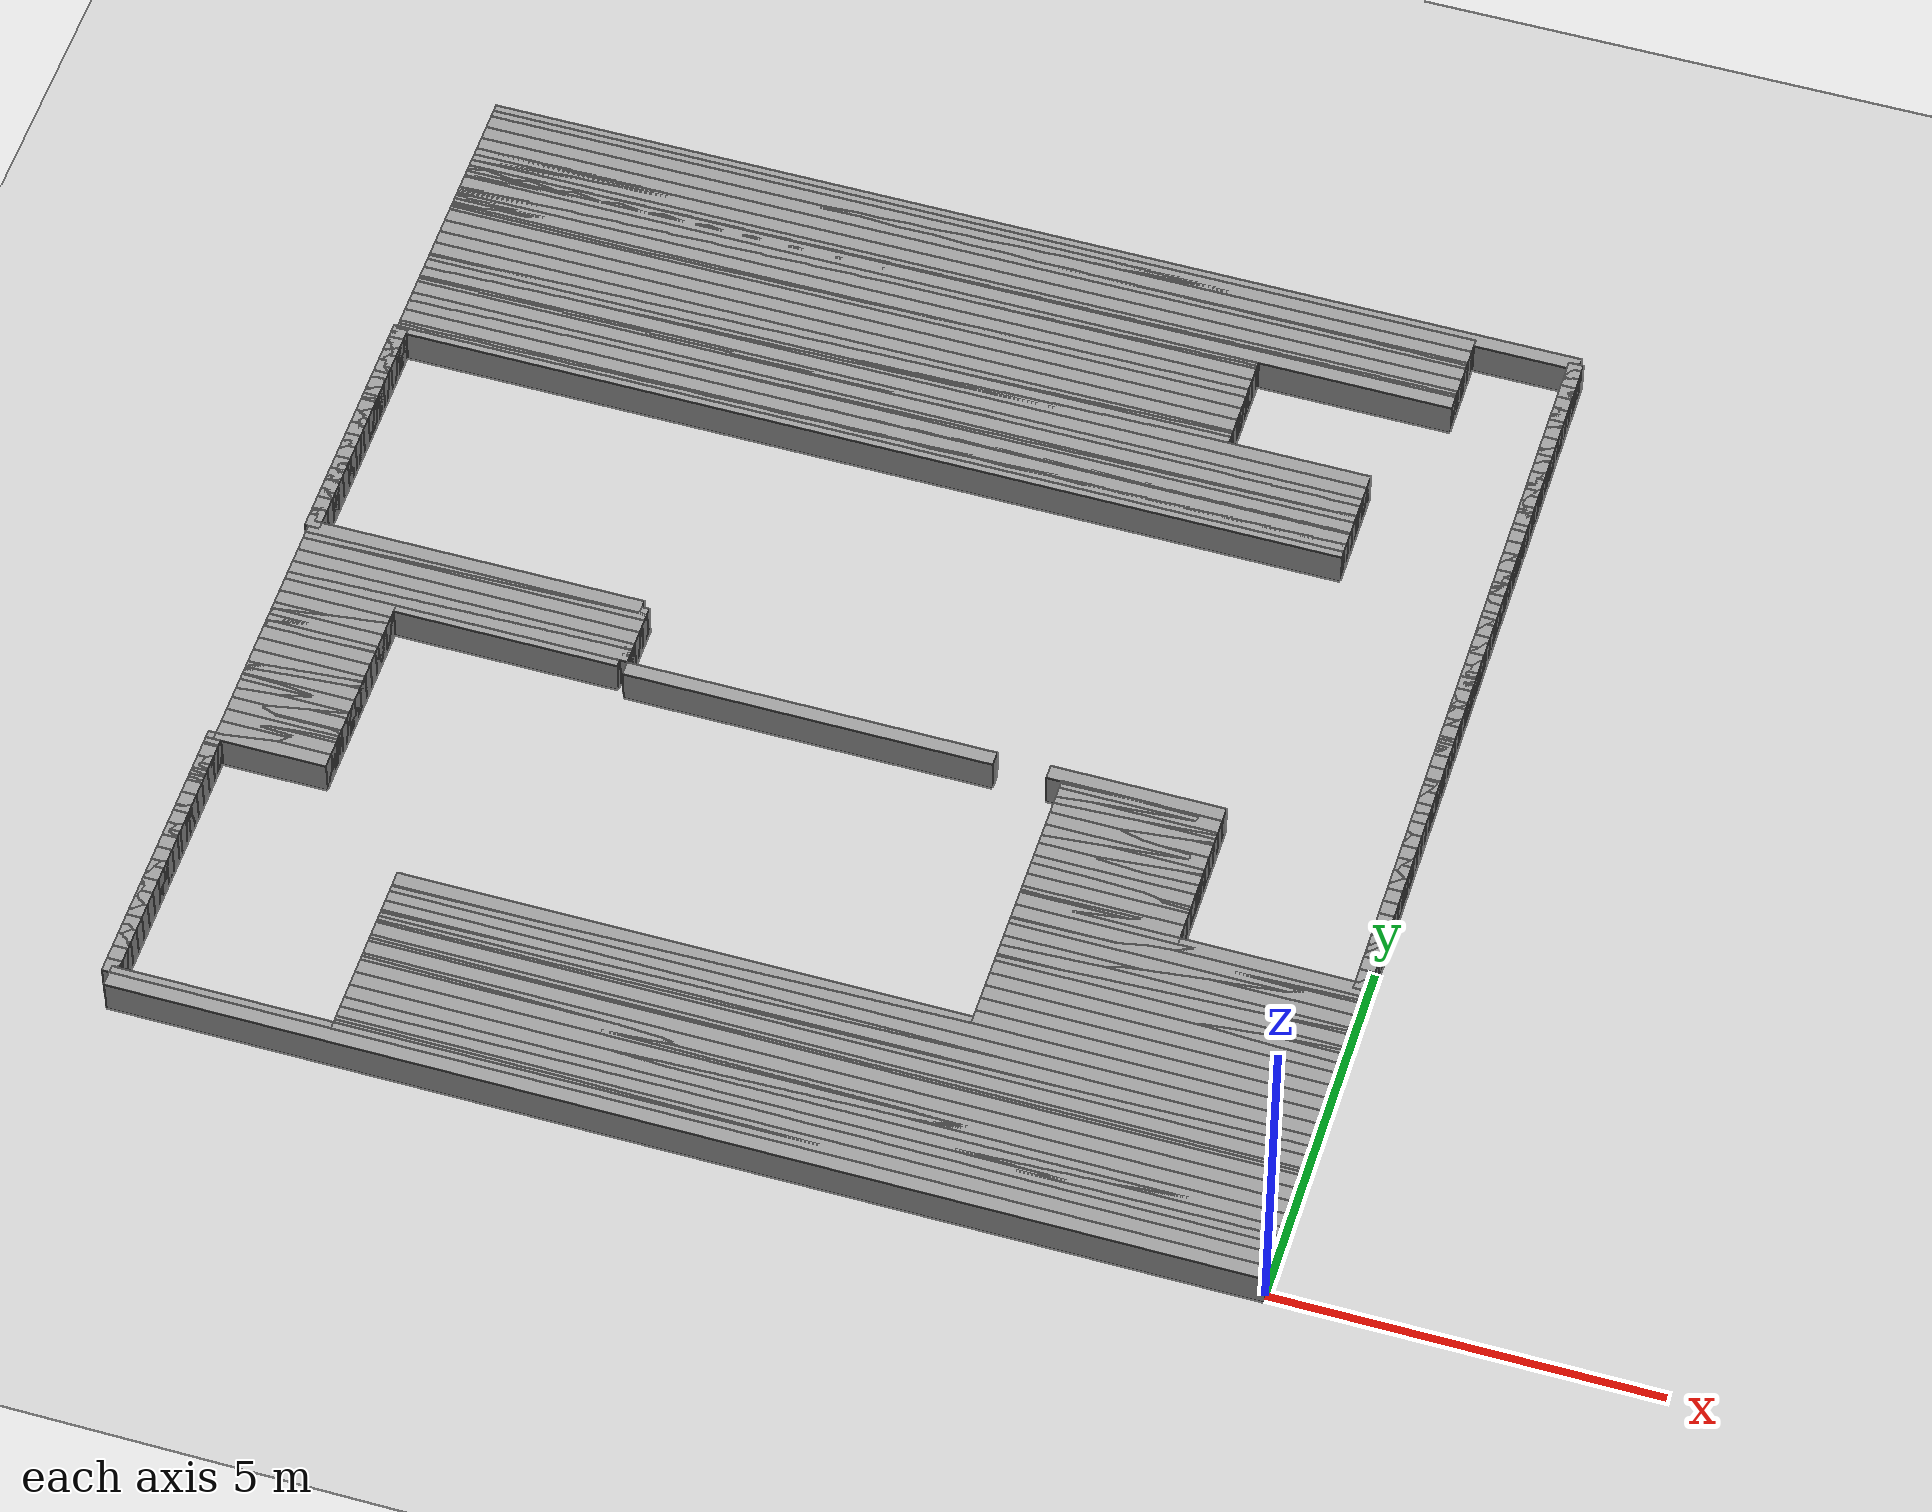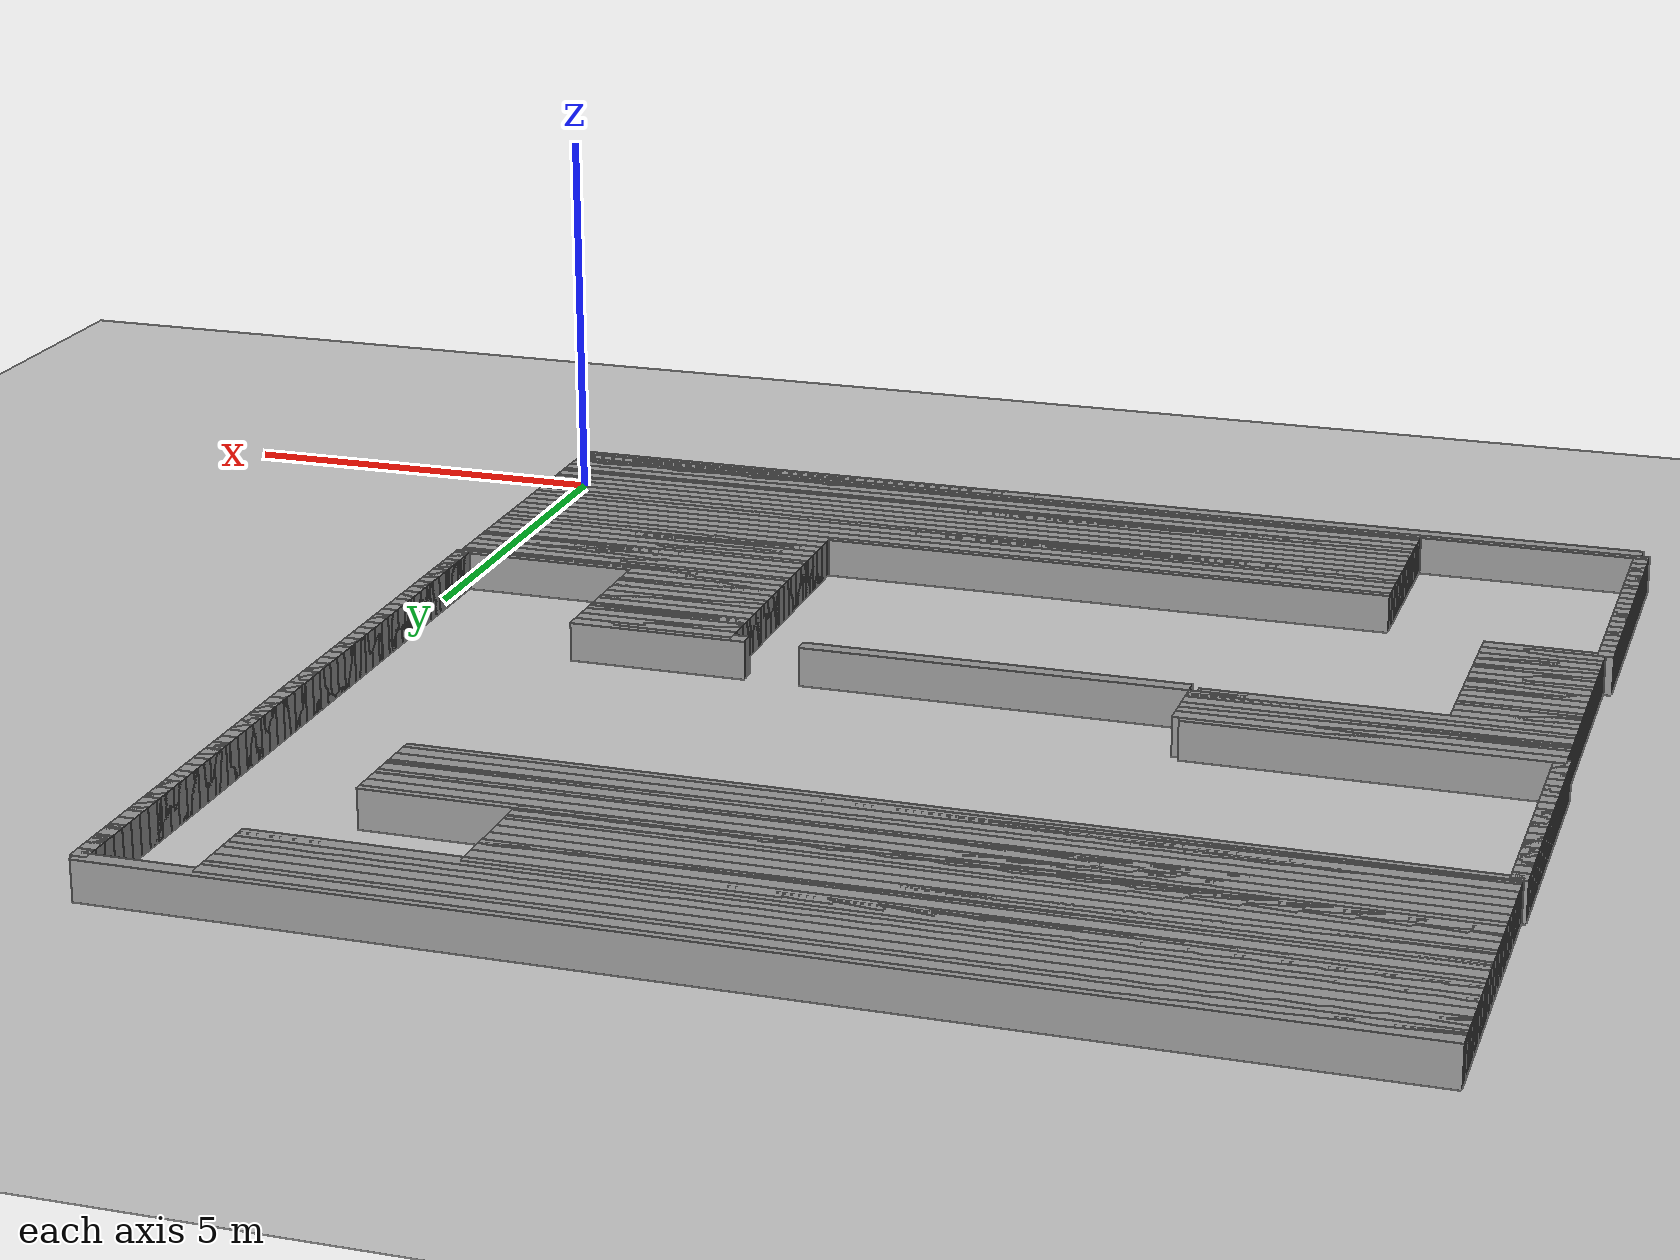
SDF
<?xml version="1.0" ?>
<sdf version="1.6">
	<world name="GridMap">
		<include>
			<uri>model://sun</uri>
		</include>
		<include>
			<uri>model://ground_plane</uri>
		</include>
		<physics type="ode">
			<real_time_update_rate>1000.0</real_time_update_rate>
			<max_step_size>0.001</max_step_size>
			<real_time_factor>1</real_time_factor>
			<ode>
				<solver>
					<type>quick</type>
					<iters>150</iters>
					<precon_iters>0</precon_iters>
					<sor>1.4</sor>
					<use_dynamic_moi_rescaling>1</use_dynamic_moi_rescaling>
				</solver>
				<constraints>
					<cfm>0.00001</cfm>
					<erp>0.2</erp>
					<contact_max_correcting_vel>2000.000000</contact_max_correcting_vel>
					<contact_surface_layer>0.01000</contact_surface_layer>
				</constraints>
			</ode>
		</physics>
		<model name="GridMap">
			<pose frame="">0 0 0 0 -0 0</pose>
			<link name="Wall_(74.5,0.0)">
				<collision name="Wall_(74.5,0.0)_Collision">
					<geometry>
						<box>
							<size>14.9 0.2 0.5</size>
						</box>
					</geometry>
					<pose frame="">-7.45 0.0 0.25 0 -0 0</pose>
				</collision>
				<inertial>
					<mass>0.5</mass>
					<pose>0 0.01 0 0 0 0</pose>
					<inertia>
						<ixx>0.004</ixx>
						<ixy>0.001</ixy>
						<ixz>0</ixz>
						<iyy>0.006</iyy>
						<iyz>0</iyz>
						<izz>0.007</izz>
					</inertia>
				</inertial>
				<visual name="Wall_(74.5,0.0)_Visual">
					<geometry>
						<box>
							<size>14.9 0.2 0.5</size>
						</box>
					</geometry>
					<pose frame="">-7.45 0.0 0.25 0 -0 0</pose>
					<material>
						<script>
							<uri>file://media/materials/scripts/gazebo.material</uri>
							<name>Gazebo/Grey</name>
						</script>
						<ambient>1 1 1 1</ambient>
					</material>
					<meta>
						<layer>0</layer>
					</meta>
				</visual>
				<pose frame="">0 0 0 0 -0 0</pose>
			</link>
			<link name="Wall_(74.5,1.0)">
				<collision name="Wall_(74.5,1.0)_Collision">
					<geometry>
						<box>
							<size>14.9 0.2 0.5</size>
						</box>
					</geometry>
					<pose frame="">-7.45 0.1 0.25 0 -0 0</pose>
				</collision>
				<inertial>
					<mass>0.5</mass>
					<pose>0 0.01 0 0 0 0</pose>
					<inertia>
						<ixx>0.004</ixx>
						<ixy>0.001</ixy>
						<ixz>0</ixz>
						<iyy>0.006</iyy>
						<iyz>0</iyz>
						<izz>0.007</izz>
					</inertia>
				</inertial>
				<visual name="Wall_(74.5,1.0)_Visual">
					<geometry>
						<box>
							<size>14.9 0.2 0.5</size>
						</box>
					</geometry>
					<pose frame="">-7.45 0.1 0.25 0 -0 0</pose>
					<material>
						<script>
							<uri>file://media/materials/scripts/gazebo.material</uri>
							<name>Gazebo/Grey</name>
						</script>
						<ambient>1 1 1 1</ambient>
					</material>
					<meta>
						<layer>0</layer>
					</meta>
				</visual>
				<pose frame="">0 0 0 0 -0 0</pose>
			</link>
			<link name="Wall_(60.0,2.0)">
				<collision name="Wall_(60.0,2.0)_Collision">
					<geometry>
						<box>
							<size>12.0 0.2 0.5</size>
						</box>
					</geometry>
					<pose frame="">-6.0 0.2 0.25 0 -0 0</pose>
				</collision>
				<inertial>
					<mass>0.5</mass>
					<pose>0 0.01 0 0 0 0</pose>
					<inertia>
						<ixx>0.004</ixx>
						<ixy>0.001</ixy>
						<ixz>0</ixz>
						<iyy>0.006</iyy>
						<iyz>0</iyz>
						<izz>0.007</izz>
					</inertia>
				</inertial>
				<visual name="Wall_(60.0,2.0)_Visual">
					<geometry>
						<box>
							<size>12.0 0.2 0.5</size>
						</box>
					</geometry>
					<pose frame="">-6.0 0.2 0.25 0 -0 0</pose>
					<material>
						<script>
							<uri>file://media/materials/scripts/gazebo.material</uri>
							<name>Gazebo/Grey</name>
						</script>
						<ambient>1 1 1 1</ambient>
					</material>
					<meta>
						<layer>0</layer>
					</meta>
				</visual>
				<pose frame="">0 0 0 0 -0 0</pose>
			</link>
			<link name="Wall_(149.0,2.0)">
				<collision name="Wall_(149.0,2.0)_Collision">
					<geometry>
						<box>
							<size>0.2 0.2 0.5</size>
						</box>
					</geometry>
					<pose frame="">-14.9 0.2 0.25 0 -0 0</pose>
				</collision>
				<inertial>
					<mass>0.5</mass>
					<pose>0 0.01 0 0 0 0</pose>
					<inertia>
						<ixx>0.004</ixx>
						<ixy>0.001</ixy>
						<ixz>0</ixz>
						<iyy>0.006</iyy>
						<iyz>0</iyz>
						<izz>0.007</izz>
					</inertia>
				</inertial>
				<visual name="Wall_(149.0,2.0)_Visual">
					<geometry>
						<box>
							<size>0.2 0.2 0.5</size>
						</box>
					</geometry>
					<pose frame="">-14.9 0.2 0.25 0 -0 0</pose>
					<material>
						<script>
							<uri>file://media/materials/scripts/gazebo.material</uri>
							<name>Gazebo/Grey</name>
						</script>
						<ambient>1 1 1 1</ambient>
					</material>
					<meta>
						<layer>0</layer>
					</meta>
				</visual>
				<pose frame="">0 0 0 0 -0 0</pose>
			</link>
			<link name="Wall_(60.0,3.0)">
				<collision name="Wall_(60.0,3.0)_Collision">
					<geometry>
						<box>
							<size>12.0 0.2 0.5</size>
						</box>
					</geometry>
					<pose frame="">-6.0 0.30000000000000004 0.25 0 -0 0</pose>
				</collision>
				<inertial>
					<mass>0.5</mass>
					<pose>0 0.01 0 0 0 0</pose>
					<inertia>
						<ixx>0.004</ixx>
						<ixy>0.001</ixy>
						<ixz>0</ixz>
						<iyy>0.006</iyy>
						<iyz>0</iyz>
						<izz>0.007</izz>
					</inertia>
				</inertial>
				<visual name="Wall_(60.0,3.0)_Visual">
					<geometry>
						<box>
							<size>12.0 0.2 0.5</size>
						</box>
					</geometry>
					<pose frame="">-6.0 0.30000000000000004 0.25 0 -0 0</pose>
					<material>
						<script>
							<uri>file://media/materials/scripts/gazebo.material</uri>
							<name>Gazebo/Grey</name>
						</script>
						<ambient>1 1 1 1</ambient>
					</material>
					<meta>
						<layer>0</layer>
					</meta>
				</visual>
				<pose frame="">0 0 0 0 -0 0</pose>
			</link>
			<link name="Wall_(149.0,3.0)">
				<collision name="Wall_(149.0,3.0)_Collision">
					<geometry>
						<box>
							<size>0.2 0.2 0.5</size>
						</box>
					</geometry>
					<pose frame="">-14.9 0.30000000000000004 0.25 0 -0 0</pose>
				</collision>
				<inertial>
					<mass>0.5</mass>
					<pose>0 0.01 0 0 0 0</pose>
					<inertia>
						<ixx>0.004</ixx>
						<ixy>0.001</ixy>
						<ixz>0</ixz>
						<iyy>0.006</iyy>
						<iyz>0</iyz>
						<izz>0.007</izz>
					</inertia>
				</inertial>
				<visual name="Wall_(149.0,3.0)_Visual">
					<geometry>
						<box>
							<size>0.2 0.2 0.5</size>
						</box>
					</geometry>
					<pose frame="">-14.9 0.30000000000000004 0.25 0 -0 0</pose>
					<material>
						<script>
							<uri>file://media/materials/scripts/gazebo.material</uri>
							<name>Gazebo/Grey</name>
						</script>
						<ambient>1 1 1 1</ambient>
					</material>
					<meta>
						<layer>0</layer>
					</meta>
				</visual>
				<pose frame="">0 0 0 0 -0 0</pose>
			</link>
			<link name="Wall_(60.0,4.0)">
				<collision name="Wall_(60.0,4.0)_Collision">
					<geometry>
						<box>
							<size>12.0 0.2 0.5</size>
						</box>
					</geometry>
					<pose frame="">-6.0 0.4 0.25 0 -0 0</pose>
				</collision>
				<inertial>
					<mass>0.5</mass>
					<pose>0 0.01 0 0 0 0</pose>
					<inertia>
						<ixx>0.004</ixx>
						<ixy>0.001</ixy>
						<ixz>0</ixz>
						<iyy>0.006</iyy>
						<iyz>0</iyz>
						<izz>0.007</izz>
					</inertia>
				</inertial>
				<visual name="Wall_(60.0,4.0)_Visual">
					<geometry>
						<box>
							<size>12.0 0.2 0.5</size>
						</box>
					</geometry>
					<pose frame="">-6.0 0.4 0.25 0 -0 0</pose>
					<material>
						<script>
							<uri>file://media/materials/scripts/gazebo.material</uri>
							<name>Gazebo/Grey</name>
						</script>
						<ambient>1 1 1 1</ambient>
					</material>
					<meta>
						<layer>0</layer>
					</meta>
				</visual>
				<pose frame="">0 0 0 0 -0 0</pose>
			</link>
			<link name="Wall_(149.0,4.0)">
				<collision name="Wall_(149.0,4.0)_Collision">
					<geometry>
						<box>
							<size>0.2 0.2 0.5</size>
						</box>
					</geometry>
					<pose frame="">-14.9 0.4 0.25 0 -0 0</pose>
				</collision>
				<inertial>
					<mass>0.5</mass>
					<pose>0 0.01 0 0 0 0</pose>
					<inertia>
						<ixx>0.004</ixx>
						<ixy>0.001</ixy>
						<ixz>0</ixz>
						<iyy>0.006</iyy>
						<iyz>0</iyz>
						<izz>0.007</izz>
					</inertia>
				</inertial>
				<visual name="Wall_(149.0,4.0)_Visual">
					<geometry>
						<box>
							<size>0.2 0.2 0.5</size>
						</box>
					</geometry>
					<pose frame="">-14.9 0.4 0.25 0 -0 0</pose>
					<material>
						<script>
							<uri>file://media/materials/scripts/gazebo.material</uri>
							<name>Gazebo/Grey</name>
						</script>
						<ambient>1 1 1 1</ambient>
					</material>
					<meta>
						<layer>0</layer>
					</meta>
				</visual>
				<pose frame="">0 0 0 0 -0 0</pose>
			</link>
			<link name="Wall_(60.0,5.0)">
				<collision name="Wall_(60.0,5.0)_Collision">
					<geometry>
						<box>
							<size>12.0 0.2 0.5</size>
						</box>
					</geometry>
					<pose frame="">-6.0 0.5 0.25 0 -0 0</pose>
				</collision>
				<inertial>
					<mass>0.5</mass>
					<pose>0 0.01 0 0 0 0</pose>
					<inertia>
						<ixx>0.004</ixx>
						<ixy>0.001</ixy>
						<ixz>0</ixz>
						<iyy>0.006</iyy>
						<iyz>0</iyz>
						<izz>0.007</izz>
					</inertia>
				</inertial>
				<visual name="Wall_(60.0,5.0)_Visual">
					<geometry>
						<box>
							<size>12.0 0.2 0.5</size>
						</box>
					</geometry>
					<pose frame="">-6.0 0.5 0.25 0 -0 0</pose>
					<material>
						<script>
							<uri>file://media/materials/scripts/gazebo.material</uri>
							<name>Gazebo/Grey</name>
						</script>
						<ambient>1 1 1 1</ambient>
					</material>
					<meta>
						<layer>0</layer>
					</meta>
				</visual>
				<pose frame="">0 0 0 0 -0 0</pose>
			</link>
			<link name="Wall_(149.0,5.0)">
				<collision name="Wall_(149.0,5.0)_Collision">
					<geometry>
						<box>
							<size>0.2 0.2 0.5</size>
						</box>
					</geometry>
					<pose frame="">-14.9 0.5 0.25 0 -0 0</pose>
				</collision>
				<inertial>
					<mass>0.5</mass>
					<pose>0 0.01 0 0 0 0</pose>
					<inertia>
						<ixx>0.004</ixx>
						<ixy>0.001</ixy>
						<ixz>0</ixz>
						<iyy>0.006</iyy>
						<iyz>0</iyz>
						<izz>0.007</izz>
					</inertia>
				</inertial>
				<visual name="Wall_(149.0,5.0)_Visual">
					<geometry>
						<box>
							<size>0.2 0.2 0.5</size>
						</box>
					</geometry>
					<pose frame="">-14.9 0.5 0.25 0 -0 0</pose>
					<material>
						<script>
							<uri>file://media/materials/scripts/gazebo.material</uri>
							<name>Gazebo/Grey</name>
						</script>
						<ambient>1 1 1 1</ambient>
					</material>
					<meta>
						<layer>0</layer>
					</meta>
				</visual>
				<pose frame="">0 0 0 0 -0 0</pose>
			</link>
			<link name="Wall_(60.0,6.0)">
				<collision name="Wall_(60.0,6.0)_Collision">
					<geometry>
						<box>
							<size>12.0 0.2 0.5</size>
						</box>
					</geometry>
					<pose frame="">-6.0 0.6000000000000001 0.25 0 -0 0</pose>
				</collision>
				<inertial>
					<mass>0.5</mass>
					<pose>0 0.01 0 0 0 0</pose>
					<inertia>
						<ixx>0.004</ixx>
						<ixy>0.001</ixy>
						<ixz>0</ixz>
						<iyy>0.006</iyy>
						<iyz>0</iyz>
						<izz>0.007</izz>
					</inertia>
				</inertial>
				<visual name="Wall_(60.0,6.0)_Visual">
					<geometry>
						<box>
							<size>12.0 0.2 0.5</size>
						</box>
					</geometry>
					<pose frame="">-6.0 0.6000000000000001 0.25 0 -0 0</pose>
					<material>
						<script>
							<uri>file://media/materials/scripts/gazebo.material</uri>
							<name>Gazebo/Grey</name>
						</script>
						<ambient>1 1 1 1</ambient>
					</material>
					<meta>
						<layer>0</layer>
					</meta>
				</visual>
				<pose frame="">0 0 0 0 -0 0</pose>
			</link>
			<link name="Wall_(149.0,6.0)">
				<collision name="Wall_(149.0,6.0)_Collision">
					<geometry>
						<box>
							<size>0.2 0.2 0.5</size>
						</box>
					</geometry>
					<pose frame="">-14.9 0.6000000000000001 0.25 0 -0 0</pose>
				</collision>
				<inertial>
					<mass>0.5</mass>
					<pose>0 0.01 0 0 0 0</pose>
					<inertia>
						<ixx>0.004</ixx>
						<ixy>0.001</ixy>
						<ixz>0</ixz>
						<iyy>0.006</iyy>
						<iyz>0</iyz>
						<izz>0.007</izz>
					</inertia>
				</inertial>
				<visual name="Wall_(149.0,6.0)_Visual">
					<geometry>
						<box>
							<size>0.2 0.2 0.5</size>
						</box>
					</geometry>
					<pose frame="">-14.9 0.6000000000000001 0.25 0 -0 0</pose>
					<material>
						<script>
							<uri>file://media/materials/scripts/gazebo.material</uri>
							<name>Gazebo/Grey</name>
						</script>
						<ambient>1 1 1 1</ambient>
					</material>
					<meta>
						<layer>0</layer>
					</meta>
				</visual>
				<pose frame="">0 0 0 0 -0 0</pose>
			</link>
			<link name="Wall_(60.0,7.0)">
				<collision name="Wall_(60.0,7.0)_Collision">
					<geometry>
						<box>
							<size>12.0 0.2 0.5</size>
						</box>
					</geometry>
					<pose frame="">-6.0 0.7000000000000001 0.25 0 -0 0</pose>
				</collision>
				<inertial>
					<mass>0.5</mass>
					<pose>0 0.01 0 0 0 0</pose>
					<inertia>
						<ixx>0.004</ixx>
						<ixy>0.001</ixy>
						<ixz>0</ixz>
						<iyy>0.006</iyy>
						<iyz>0</iyz>
						<izz>0.007</izz>
					</inertia>
				</inertial>
				<visual name="Wall_(60.0,7.0)_Visual">
					<geometry>
						<box>
							<size>12.0 0.2 0.5</size>
						</box>
					</geometry>
					<pose frame="">-6.0 0.7000000000000001 0.25 0 -0 0</pose>
					<material>
						<script>
							<uri>file://media/materials/scripts/gazebo.material</uri>
							<name>Gazebo/Grey</name>
						</script>
						<ambient>1 1 1 1</ambient>
					</material>
					<meta>
						<layer>0</layer>
					</meta>
				</visual>
				<pose frame="">0 0 0 0 -0 0</pose>
			</link>
			<link name="Wall_(149.0,7.0)">
				<collision name="Wall_(149.0,7.0)_Collision">
					<geometry>
						<box>
							<size>0.2 0.2 0.5</size>
						</box>
					</geometry>
					<pose frame="">-14.9 0.7000000000000001 0.25 0 -0 0</pose>
				</collision>
				<inertial>
					<mass>0.5</mass>
					<pose>0 0.01 0 0 0 0</pose>
					<inertia>
						<ixx>0.004</ixx>
						<ixy>0.001</ixy>
						<ixz>0</ixz>
						<iyy>0.006</iyy>
						<iyz>0</iyz>
						<izz>0.007</izz>
					</inertia>
				</inertial>
				<visual name="Wall_(149.0,7.0)_Visual">
					<geometry>
						<box>
							<size>0.2 0.2 0.5</size>
						</box>
					</geometry>
					<pose frame="">-14.9 0.7000000000000001 0.25 0 -0 0</pose>
					<material>
						<script>
							<uri>file://media/materials/scripts/gazebo.material</uri>
							<name>Gazebo/Grey</name>
						</script>
						<ambient>1 1 1 1</ambient>
					</material>
					<meta>
						<layer>0</layer>
					</meta>
				</visual>
				<pose frame="">0 0 0 0 -0 0</pose>
			</link>
			<link name="Wall_(60.0,8.0)">
				<collision name="Wall_(60.0,8.0)_Collision">
					<geometry>
						<box>
							<size>12.0 0.2 0.5</size>
						</box>
					</geometry>
					<pose frame="">-6.0 0.8 0.25 0 -0 0</pose>
				</collision>
				<inertial>
					<mass>0.5</mass>
					<pose>0 0.01 0 0 0 0</pose>
					<inertia>
						<ixx>0.004</ixx>
						<ixy>0.001</ixy>
						<ixz>0</ixz>
						<iyy>0.006</iyy>
						<iyz>0</iyz>
						<izz>0.007</izz>
					</inertia>
				</inertial>
				<visual name="Wall_(60.0,8.0)_Visual">
					<geometry>
						<box>
							<size>12.0 0.2 0.5</size>
						</box>
					</geometry>
					<pose frame="">-6.0 0.8 0.25 0 -0 0</pose>
					<material>
						<script>
							<uri>file://media/materials/scripts/gazebo.material</uri>
							<name>Gazebo/Grey</name>
						</script>
						<ambient>1 1 1 1</ambient>
					</material>
					<meta>
						<layer>0</layer>
					</meta>
				</visual>
				<pose frame="">0 0 0 0 -0 0</pose>
			</link>
			<link name="Wall_(149.0,8.0)">
				<collision name="Wall_(149.0,8.0)_Collision">
					<geometry>
						<box>
							<size>0.2 0.2 0.5</size>
						</box>
					</geometry>
					<pose frame="">-14.9 0.8 0.25 0 -0 0</pose>
				</collision>
				<inertial>
					<mass>0.5</mass>
					<pose>0 0.01 0 0 0 0</pose>
					<inertia>
						<ixx>0.004</ixx>
						<ixy>0.001</ixy>
						<ixz>0</ixz>
						<iyy>0.006</iyy>
						<iyz>0</iyz>
						<izz>0.007</izz>
					</inertia>
				</inertial>
				<visual name="Wall_(149.0,8.0)_Visual">
					<geometry>
						<box>
							<size>0.2 0.2 0.5</size>
						</box>
					</geometry>
					<pose frame="">-14.9 0.8 0.25 0 -0 0</pose>
					<material>
						<script>
							<uri>file://media/materials/scripts/gazebo.material</uri>
							<name>Gazebo/Grey</name>
						</script>
						<ambient>1 1 1 1</ambient>
					</material>
					<meta>
						<layer>0</layer>
					</meta>
				</visual>
				<pose frame="">0 0 0 0 -0 0</pose>
			</link>
			<link name="Wall_(60.0,9.0)">
				<collision name="Wall_(60.0,9.0)_Collision">
					<geometry>
						<box>
							<size>12.0 0.2 0.5</size>
						</box>
					</geometry>
					<pose frame="">-6.0 0.9 0.25 0 -0 0</pose>
				</collision>
				<inertial>
					<mass>0.5</mass>
					<pose>0 0.01 0 0 0 0</pose>
					<inertia>
						<ixx>0.004</ixx>
						<ixy>0.001</ixy>
						<ixz>0</ixz>
						<iyy>0.006</iyy>
						<iyz>0</iyz>
						<izz>0.007</izz>
					</inertia>
				</inertial>
				<visual name="Wall_(60.0,9.0)_Visual">
					<geometry>
						<box>
							<size>12.0 0.2 0.5</size>
						</box>
					</geometry>
					<pose frame="">-6.0 0.9 0.25 0 -0 0</pose>
					<material>
						<script>
							<uri>file://media/materials/scripts/gazebo.material</uri>
							<name>Gazebo/Grey</name>
						</script>
						<ambient>1 1 1 1</ambient>
					</material>
					<meta>
						<layer>0</layer>
					</meta>
				</visual>
				<pose frame="">0 0 0 0 -0 0</pose>
			</link>
			<link name="Wall_(149.0,9.0)">
				<collision name="Wall_(149.0,9.0)_Collision">
					<geometry>
						<box>
							<size>0.2 0.2 0.5</size>
						</box>
					</geometry>
					<pose frame="">-14.9 0.9 0.25 0 -0 0</pose>
				</collision>
				<inertial>
					<mass>0.5</mass>
					<pose>0 0.01 0 0 0 0</pose>
					<inertia>
						<ixx>0.004</ixx>
						<ixy>0.001</ixy>
						<ixz>0</ixz>
						<iyy>0.006</iyy>
						<iyz>0</iyz>
						<izz>0.007</izz>
					</inertia>
				</inertial>
				<visual name="Wall_(149.0,9.0)_Visual">
					<geometry>
						<box>
							<size>0.2 0.2 0.5</size>
						</box>
					</geometry>
					<pose frame="">-14.9 0.9 0.25 0 -0 0</pose>
					<material>
						<script>
							<uri>file://media/materials/scripts/gazebo.material</uri>
							<name>Gazebo/Grey</name>
						</script>
						<ambient>1 1 1 1</ambient>
					</material>
					<meta>
						<layer>0</layer>
					</meta>
				</visual>
				<pose frame="">0 0 0 0 -0 0</pose>
			</link>
			<link name="Wall_(60.0,10.0)">
				<collision name="Wall_(60.0,10.0)_Collision">
					<geometry>
						<box>
							<size>12.0 0.2 0.5</size>
						</box>
					</geometry>
					<pose frame="">-6.0 1.0 0.25 0 -0 0</pose>
				</collision>
				<inertial>
					<mass>0.5</mass>
					<pose>0 0.01 0 0 0 0</pose>
					<inertia>
						<ixx>0.004</ixx>
						<ixy>0.001</ixy>
						<ixz>0</ixz>
						<iyy>0.006</iyy>
						<iyz>0</iyz>
						<izz>0.007</izz>
					</inertia>
				</inertial>
				<visual name="Wall_(60.0,10.0)_Visual">
					<geometry>
						<box>
							<size>12.0 0.2 0.5</size>
						</box>
					</geometry>
					<pose frame="">-6.0 1.0 0.25 0 -0 0</pose>
					<material>
						<script>
							<uri>file://media/materials/scripts/gazebo.material</uri>
							<name>Gazebo/Grey</name>
						</script>
						<ambient>1 1 1 1</ambient>
					</material>
					<meta>
						<layer>0</layer>
					</meta>
				</visual>
				<pose frame="">0 0 0 0 -0 0</pose>
			</link>
			<link name="Wall_(149.0,10.0)">
				<collision name="Wall_(149.0,10.0)_Collision">
					<geometry>
						<box>
							<size>0.2 0.2 0.5</size>
						</box>
					</geometry>
					<pose frame="">-14.9 1.0 0.25 0 -0 0</pose>
				</collision>
				<inertial>
					<mass>0.5</mass>
					<pose>0 0.01 0 0 0 0</pose>
					<inertia>
						<ixx>0.004</ixx>
						<ixy>0.001</ixy>
						<ixz>0</ixz>
						<iyy>0.006</iyy>
						<iyz>0</iyz>
						<izz>0.007</izz>
					</inertia>
				</inertial>
				<visual name="Wall_(149.0,10.0)_Visual">
					<geometry>
						<box>
							<size>0.2 0.2 0.5</size>
						</box>
					</geometry>
					<pose frame="">-14.9 1.0 0.25 0 -0 0</pose>
					<material>
						<script>
							<uri>file://media/materials/scripts/gazebo.material</uri>
							<name>Gazebo/Grey</name>
						</script>
						<ambient>1 1 1 1</ambient>
					</material>
					<meta>
						<layer>0</layer>
					</meta>
				</visual>
				<pose frame="">0 0 0 0 -0 0</pose>
			</link>
			<link name="Wall_(60.0,11.0)">
				<collision name="Wall_(60.0,11.0)_Collision">
					<geometry>
						<box>
							<size>12.0 0.2 0.5</size>
						</box>
					</geometry>
					<pose frame="">-6.0 1.1 0.25 0 -0 0</pose>
				</collision>
				<inertial>
					<mass>0.5</mass>
					<pose>0 0.01 0 0 0 0</pose>
					<inertia>
						<ixx>0.004</ixx>
						<ixy>0.001</ixy>
						<ixz>0</ixz>
						<iyy>0.006</iyy>
						<iyz>0</iyz>
						<izz>0.007</izz>
					</inertia>
				</inertial>
				<visual name="Wall_(60.0,11.0)_Visual">
					<geometry>
						<box>
							<size>12.0 0.2 0.5</size>
						</box>
					</geometry>
					<pose frame="">-6.0 1.1 0.25 0 -0 0</pose>
					<material>
						<script>
							<uri>file://media/materials/scripts/gazebo.material</uri>
							<name>Gazebo/Grey</name>
						</script>
						<ambient>1 1 1 1</ambient>
					</material>
					<meta>
						<layer>0</layer>
					</meta>
				</visual>
				<pose frame="">0 0 0 0 -0 0</pose>
			</link>
			<link name="Wall_(149.0,11.0)">
				<collision name="Wall_(149.0,11.0)_Collision">
					<geometry>
						<box>
							<size>0.2 0.2 0.5</size>
						</box>
					</geometry>
					<pose frame="">-14.9 1.1 0.25 0 -0 0</pose>
				</collision>
				<inertial>
					<mass>0.5</mass>
					<pose>0 0.01 0 0 0 0</pose>
					<inertia>
						<ixx>0.004</ixx>
						<ixy>0.001</ixy>
						<ixz>0</ixz>
						<iyy>0.006</iyy>
						<iyz>0</iyz>
						<izz>0.007</izz>
					</inertia>
				</inertial>
				<visual name="Wall_(149.0,11.0)_Visual">
					<geometry>
						<box>
							<size>0.2 0.2 0.5</size>
						</box>
					</geometry>
					<pose frame="">-14.9 1.1 0.25 0 -0 0</pose>
					<material>
						<script>
							<uri>file://media/materials/scripts/gazebo.material</uri>
							<name>Gazebo/Grey</name>
						</script>
						<ambient>1 1 1 1</ambient>
					</material>
					<meta>
						<layer>0</layer>
					</meta>
				</visual>
				<pose frame="">0 0 0 0 -0 0</pose>
			</link>
			<link name="Wall_(60.0,12.0)">
				<collision name="Wall_(60.0,12.0)_Collision">
					<geometry>
						<box>
							<size>12.0 0.2 0.5</size>
						</box>
					</geometry>
					<pose frame="">-6.0 1.2000000000000002 0.25 0 -0 0</pose>
				</collision>
				<inertial>
					<mass>0.5</mass>
					<pose>0 0.01 0 0 0 0</pose>
					<inertia>
						<ixx>0.004</ixx>
						<ixy>0.001</ixy>
						<ixz>0</ixz>
						<iyy>0.006</iyy>
						<iyz>0</iyz>
						<izz>0.007</izz>
					</inertia>
				</inertial>
				<visual name="Wall_(60.0,12.0)_Visual">
					<geometry>
						<box>
							<size>12.0 0.2 0.5</size>
						</box>
					</geometry>
					<pose frame="">-6.0 1.2000000000000002 0.25 0 -0 0</pose>
					<material>
						<script>
							<uri>file://media/materials/scripts/gazebo.material</uri>
							<name>Gazebo/Grey</name>
						</script>
						<ambient>1 1 1 1</ambient>
					</material>
					<meta>
						<layer>0</layer>
					</meta>
				</visual>
				<pose frame="">0 0 0 0 -0 0</pose>
			</link>
			<link name="Wall_(149.0,12.0)">
				<collision name="Wall_(149.0,12.0)_Collision">
					<geometry>
						<box>
							<size>0.2 0.2 0.5</size>
						</box>
					</geometry>
					<pose frame="">-14.9 1.2000000000000002 0.25 0 -0 0</pose>
				</collision>
				<inertial>
					<mass>0.5</mass>
					<pose>0 0.01 0 0 0 0</pose>
					<inertia>
						<ixx>0.004</ixx>
						<ixy>0.001</ixy>
						<ixz>0</ixz>
						<iyy>0.006</iyy>
						<iyz>0</iyz>
						<izz>0.007</izz>
					</inertia>
				</inertial>
				<visual name="Wall_(149.0,12.0)_Visual">
					<geometry>
						<box>
							<size>0.2 0.2 0.5</size>
						</box>
					</geometry>
					<pose frame="">-14.9 1.2000000000000002 0.25 0 -0 0</pose>
					<material>
						<script>
							<uri>file://media/materials/scripts/gazebo.material</uri>
							<name>Gazebo/Grey</name>
						</script>
						<ambient>1 1 1 1</ambient>
					</material>
					<meta>
						<layer>0</layer>
					</meta>
				</visual>
				<pose frame="">0 0 0 0 -0 0</pose>
			</link>
			<link name="Wall_(60.0,13.0)">
				<collision name="Wall_(60.0,13.0)_Collision">
					<geometry>
						<box>
							<size>12.0 0.2 0.5</size>
						</box>
					</geometry>
					<pose frame="">-6.0 1.3 0.25 0 -0 0</pose>
				</collision>
				<inertial>
					<mass>0.5</mass>
					<pose>0 0.01 0 0 0 0</pose>
					<inertia>
						<ixx>0.004</ixx>
						<ixy>0.001</ixy>
						<ixz>0</ixz>
						<iyy>0.006</iyy>
						<iyz>0</iyz>
						<izz>0.007</izz>
					</inertia>
				</inertial>
				<visual name="Wall_(60.0,13.0)_Visual">
					<geometry>
						<box>
							<size>12.0 0.2 0.5</size>
						</box>
					</geometry>
					<pose frame="">-6.0 1.3 0.25 0 -0 0</pose>
					<material>
						<script>
							<uri>file://media/materials/scripts/gazebo.material</uri>
							<name>Gazebo/Grey</name>
						</script>
						<ambient>1 1 1 1</ambient>
					</material>
					<meta>
						<layer>0</layer>
					</meta>
				</visual>
				<pose frame="">0 0 0 0 -0 0</pose>
			</link>
			<link name="Wall_(149.0,13.0)">
				<collision name="Wall_(149.0,13.0)_Collision">
					<geometry>
						<box>
							<size>0.2 0.2 0.5</size>
						</box>
					</geometry>
					<pose frame="">-14.9 1.3 0.25 0 -0 0</pose>
				</collision>
				<inertial>
					<mass>0.5</mass>
					<pose>0 0.01 0 0 0 0</pose>
					<inertia>
						<ixx>0.004</ixx>
						<ixy>0.001</ixy>
						<ixz>0</ixz>
						<iyy>0.006</iyy>
						<iyz>0</iyz>
						<izz>0.007</izz>
					</inertia>
				</inertial>
				<visual name="Wall_(149.0,13.0)_Visual">
					<geometry>
						<box>
							<size>0.2 0.2 0.5</size>
						</box>
					</geometry>
					<pose frame="">-14.9 1.3 0.25 0 -0 0</pose>
					<material>
						<script>
							<uri>file://media/materials/scripts/gazebo.material</uri>
							<name>Gazebo/Grey</name>
						</script>
						<ambient>1 1 1 1</ambient>
					</material>
					<meta>
						<layer>0</layer>
					</meta>
				</visual>
				<pose frame="">0 0 0 0 -0 0</pose>
			</link>
			<link name="Wall_(60.0,14.0)">
				<collision name="Wall_(60.0,14.0)_Collision">
					<geometry>
						<box>
							<size>12.0 0.2 0.5</size>
						</box>
					</geometry>
					<pose frame="">-6.0 1.4000000000000001 0.25 0 -0 0</pose>
				</collision>
				<inertial>
					<mass>0.5</mass>
					<pose>0 0.01 0 0 0 0</pose>
					<inertia>
						<ixx>0.004</ixx>
						<ixy>0.001</ixy>
						<ixz>0</ixz>
						<iyy>0.006</iyy>
						<iyz>0</iyz>
						<izz>0.007</izz>
					</inertia>
				</inertial>
				<visual name="Wall_(60.0,14.0)_Visual">
					<geometry>
						<box>
							<size>12.0 0.2 0.5</size>
						</box>
					</geometry>
					<pose frame="">-6.0 1.4000000000000001 0.25 0 -0 0</pose>
					<material>
						<script>
							<uri>file://media/materials/scripts/gazebo.material</uri>
							<name>Gazebo/Grey</name>
						</script>
						<ambient>1 1 1 1</ambient>
					</material>
					<meta>
						<layer>0</layer>
					</meta>
				</visual>
				<pose frame="">0 0 0 0 -0 0</pose>
			</link>
			<link name="Wall_(149.0,14.0)">
				<collision name="Wall_(149.0,14.0)_Collision">
					<geometry>
						<box>
							<size>0.2 0.2 0.5</size>
						</box>
					</geometry>
					<pose frame="">-14.9 1.4000000000000001 0.25 0 -0 0</pose>
				</collision>
				<inertial>
					<mass>0.5</mass>
					<pose>0 0.01 0 0 0 0</pose>
					<inertia>
						<ixx>0.004</ixx>
						<ixy>0.001</ixy>
						<ixz>0</ixz>
						<iyy>0.006</iyy>
						<iyz>0</iyz>
						<izz>0.007</izz>
					</inertia>
				</inertial>
				<visual name="Wall_(149.0,14.0)_Visual">
					<geometry>
						<box>
							<size>0.2 0.2 0.5</size>
						</box>
					</geometry>
					<pose frame="">-14.9 1.4000000000000001 0.25 0 -0 0</pose>
					<material>
						<script>
							<uri>file://media/materials/scripts/gazebo.material</uri>
							<name>Gazebo/Grey</name>
						</script>
						<ambient>1 1 1 1</ambient>
					</material>
					<meta>
						<layer>0</layer>
					</meta>
				</visual>
				<pose frame="">0 0 0 0 -0 0</pose>
			</link>
			<link name="Wall_(60.0,15.0)">
				<collision name="Wall_(60.0,15.0)_Collision">
					<geometry>
						<box>
							<size>12.0 0.2 0.5</size>
						</box>
					</geometry>
					<pose frame="">-6.0 1.5 0.25 0 -0 0</pose>
				</collision>
				<inertial>
					<mass>0.5</mass>
					<pose>0 0.01 0 0 0 0</pose>
					<inertia>
						<ixx>0.004</ixx>
						<ixy>0.001</ixy>
						<ixz>0</ixz>
						<iyy>0.006</iyy>
						<iyz>0</iyz>
						<izz>0.007</izz>
					</inertia>
				</inertial>
				<visual name="Wall_(60.0,15.0)_Visual">
					<geometry>
						<box>
							<size>12.0 0.2 0.5</size>
						</box>
					</geometry>
					<pose frame="">-6.0 1.5 0.25 0 -0 0</pose>
					<material>
						<script>
							<uri>file://media/materials/scripts/gazebo.material</uri>
							<name>Gazebo/Grey</name>
						</script>
						<ambient>1 1 1 1</ambient>
					</material>
					<meta>
						<layer>0</layer>
					</meta>
				</visual>
				<pose frame="">0 0 0 0 -0 0</pose>
			</link>
			<link name="Wall_(149.0,15.0)">
				<collision name="Wall_(149.0,15.0)_Collision">
					<geometry>
						<box>
							<size>0.2 0.2 0.5</size>
						</box>
					</geometry>
					<pose frame="">-14.9 1.5 0.25 0 -0 0</pose>
				</collision>
				<inertial>
					<mass>0.5</mass>
					<pose>0 0.01 0 0 0 0</pose>
					<inertia>
						<ixx>0.004</ixx>
						<ixy>0.001</ixy>
						<ixz>0</ixz>
						<iyy>0.006</iyy>
						<iyz>0</iyz>
						<izz>0.007</izz>
					</inertia>
				</inertial>
				<visual name="Wall_(149.0,15.0)_Visual">
					<geometry>
						<box>
							<size>0.2 0.2 0.5</size>
						</box>
					</geometry>
					<pose frame="">-14.9 1.5 0.25 0 -0 0</pose>
					<material>
						<script>
							<uri>file://media/materials/scripts/gazebo.material</uri>
							<name>Gazebo/Grey</name>
						</script>
						<ambient>1 1 1 1</ambient>
					</material>
					<meta>
						<layer>0</layer>
					</meta>
				</visual>
				<pose frame="">0 0 0 0 -0 0</pose>
			</link>
			<link name="Wall_(60.0,16.0)">
				<collision name="Wall_(60.0,16.0)_Collision">
					<geometry>
						<box>
							<size>12.0 0.2 0.5</size>
						</box>
					</geometry>
					<pose frame="">-6.0 1.6 0.25 0 -0 0</pose>
				</collision>
				<inertial>
					<mass>0.5</mass>
					<pose>0 0.01 0 0 0 0</pose>
					<inertia>
						<ixx>0.004</ixx>
						<ixy>0.001</ixy>
						<ixz>0</ixz>
						<iyy>0.006</iyy>
						<iyz>0</iyz>
						<izz>0.007</izz>
					</inertia>
				</inertial>
				<visual name="Wall_(60.0,16.0)_Visual">
					<geometry>
						<box>
							<size>12.0 0.2 0.5</size>
						</box>
					</geometry>
					<pose frame="">-6.0 1.6 0.25 0 -0 0</pose>
					<material>
						<script>
							<uri>file://media/materials/scripts/gazebo.material</uri>
							<name>Gazebo/Grey</name>
						</script>
						<ambient>1 1 1 1</ambient>
					</material>
					<meta>
						<layer>0</layer>
					</meta>
				</visual>
				<pose frame="">0 0 0 0 -0 0</pose>
			</link>
			<link name="Wall_(149.0,16.0)">
				<collision name="Wall_(149.0,16.0)_Collision">
					<geometry>
						<box>
							<size>0.2 0.2 0.5</size>
						</box>
					</geometry>
					<pose frame="">-14.9 1.6 0.25 0 -0 0</pose>
				</collision>
				<inertial>
					<mass>0.5</mass>
					<pose>0 0.01 0 0 0 0</pose>
					<inertia>
						<ixx>0.004</ixx>
						<ixy>0.001</ixy>
						<ixz>0</ixz>
						<iyy>0.006</iyy>
						<iyz>0</iyz>
						<izz>0.007</izz>
					</inertia>
				</inertial>
				<visual name="Wall_(149.0,16.0)_Visual">
					<geometry>
						<box>
							<size>0.2 0.2 0.5</size>
						</box>
					</geometry>
					<pose frame="">-14.9 1.6 0.25 0 -0 0</pose>
					<material>
						<script>
							<uri>file://media/materials/scripts/gazebo.material</uri>
							<name>Gazebo/Grey</name>
						</script>
						<ambient>1 1 1 1</ambient>
					</material>
					<meta>
						<layer>0</layer>
					</meta>
				</visual>
				<pose frame="">0 0 0 0 -0 0</pose>
			</link>
			<link name="Wall_(60.0,17.0)">
				<collision name="Wall_(60.0,17.0)_Collision">
					<geometry>
						<box>
							<size>12.0 0.2 0.5</size>
						</box>
					</geometry>
					<pose frame="">-6.0 1.7000000000000002 0.25 0 -0 0</pose>
				</collision>
				<inertial>
					<mass>0.5</mass>
					<pose>0 0.01 0 0 0 0</pose>
					<inertia>
						<ixx>0.004</ixx>
						<ixy>0.001</ixy>
						<ixz>0</ixz>
						<iyy>0.006</iyy>
						<iyz>0</iyz>
						<izz>0.007</izz>
					</inertia>
				</inertial>
				<visual name="Wall_(60.0,17.0)_Visual">
					<geometry>
						<box>
							<size>12.0 0.2 0.5</size>
						</box>
					</geometry>
					<pose frame="">-6.0 1.7000000000000002 0.25 0 -0 0</pose>
					<material>
						<script>
							<uri>file://media/materials/scripts/gazebo.material</uri>
							<name>Gazebo/Grey</name>
						</script>
						<ambient>1 1 1 1</ambient>
					</material>
					<meta>
						<layer>0</layer>
					</meta>
				</visual>
				<pose frame="">0 0 0 0 -0 0</pose>
			</link>
			<link name="Wall_(149.0,17.0)">
				<collision name="Wall_(149.0,17.0)_Collision">
					<geometry>
						<box>
							<size>0.2 0.2 0.5</size>
						</box>
					</geometry>
					<pose frame="">-14.9 1.7000000000000002 0.25 0 -0 0</pose>
				</collision>
				<inertial>
					<mass>0.5</mass>
					<pose>0 0.01 0 0 0 0</pose>
					<inertia>
						<ixx>0.004</ixx>
						<ixy>0.001</ixy>
						<ixz>0</ixz>
						<iyy>0.006</iyy>
						<iyz>0</iyz>
						<izz>0.007</izz>
					</inertia>
				</inertial>
				<visual name="Wall_(149.0,17.0)_Visual">
					<geometry>
						<box>
							<size>0.2 0.2 0.5</size>
						</box>
					</geometry>
					<pose frame="">-14.9 1.7000000000000002 0.25 0 -0 0</pose>
					<material>
						<script>
							<uri>file://media/materials/scripts/gazebo.material</uri>
							<name>Gazebo/Grey</name>
						</script>
						<ambient>1 1 1 1</ambient>
					</material>
					<meta>
						<layer>0</layer>
					</meta>
				</visual>
				<pose frame="">0 0 0 0 -0 0</pose>
			</link>
			<link name="Wall_(60.0,18.0)">
				<collision name="Wall_(60.0,18.0)_Collision">
					<geometry>
						<box>
							<size>12.0 0.2 0.5</size>
						</box>
					</geometry>
					<pose frame="">-6.0 1.8 0.25 0 -0 0</pose>
				</collision>
				<inertial>
					<mass>0.5</mass>
					<pose>0 0.01 0 0 0 0</pose>
					<inertia>
						<ixx>0.004</ixx>
						<ixy>0.001</ixy>
						<ixz>0</ixz>
						<iyy>0.006</iyy>
						<iyz>0</iyz>
						<izz>0.007</izz>
					</inertia>
				</inertial>
				<visual name="Wall_(60.0,18.0)_Visual">
					<geometry>
						<box>
							<size>12.0 0.2 0.5</size>
						</box>
					</geometry>
					<pose frame="">-6.0 1.8 0.25 0 -0 0</pose>
					<material>
						<script>
							<uri>file://media/materials/scripts/gazebo.material</uri>
							<name>Gazebo/Grey</name>
						</script>
						<ambient>1 1 1 1</ambient>
					</material>
					<meta>
						<layer>0</layer>
					</meta>
				</visual>
				<pose frame="">0 0 0 0 -0 0</pose>
			</link>
			<link name="Wall_(149.0,18.0)">
				<collision name="Wall_(149.0,18.0)_Collision">
					<geometry>
						<box>
							<size>0.2 0.2 0.5</size>
						</box>
					</geometry>
					<pose frame="">-14.9 1.8 0.25 0 -0 0</pose>
				</collision>
				<inertial>
					<mass>0.5</mass>
					<pose>0 0.01 0 0 0 0</pose>
					<inertia>
						<ixx>0.004</ixx>
						<ixy>0.001</ixy>
						<ixz>0</ixz>
						<iyy>0.006</iyy>
						<iyz>0</iyz>
						<izz>0.007</izz>
					</inertia>
				</inertial>
				<visual name="Wall_(149.0,18.0)_Visual">
					<geometry>
						<box>
							<size>0.2 0.2 0.5</size>
						</box>
					</geometry>
					<pose frame="">-14.9 1.8 0.25 0 -0 0</pose>
					<material>
						<script>
							<uri>file://media/materials/scripts/gazebo.material</uri>
							<name>Gazebo/Grey</name>
						</script>
						<ambient>1 1 1 1</ambient>
					</material>
					<meta>
						<layer>0</layer>
					</meta>
				</visual>
				<pose frame="">0 0 0 0 -0 0</pose>
			</link>
			<link name="Wall_(60.0,19.0)">
				<collision name="Wall_(60.0,19.0)_Collision">
					<geometry>
						<box>
							<size>12.0 0.2 0.5</size>
						</box>
					</geometry>
					<pose frame="">-6.0 1.9000000000000001 0.25 0 -0 0</pose>
				</collision>
				<inertial>
					<mass>0.5</mass>
					<pose>0 0.01 0 0 0 0</pose>
					<inertia>
						<ixx>0.004</ixx>
						<ixy>0.001</ixy>
						<ixz>0</ixz>
						<iyy>0.006</iyy>
						<iyz>0</iyz>
						<izz>0.007</izz>
					</inertia>
				</inertial>
				<visual name="Wall_(60.0,19.0)_Visual">
					<geometry>
						<box>
							<size>12.0 0.2 0.5</size>
						</box>
					</geometry>
					<pose frame="">-6.0 1.9000000000000001 0.25 0 -0 0</pose>
					<material>
						<script>
							<uri>file://media/materials/scripts/gazebo.material</uri>
							<name>Gazebo/Grey</name>
						</script>
						<ambient>1 1 1 1</ambient>
					</material>
					<meta>
						<layer>0</layer>
					</meta>
				</visual>
				<pose frame="">0 0 0 0 -0 0</pose>
			</link>
			<link name="Wall_(149.0,19.0)">
				<collision name="Wall_(149.0,19.0)_Collision">
					<geometry>
						<box>
							<size>0.2 0.2 0.5</size>
						</box>
					</geometry>
					<pose frame="">-14.9 1.9000000000000001 0.25 0 -0 0</pose>
				</collision>
				<inertial>
					<mass>0.5</mass>
					<pose>0 0.01 0 0 0 0</pose>
					<inertia>
						<ixx>0.004</ixx>
						<ixy>0.001</ixy>
						<ixz>0</ixz>
						<iyy>0.006</iyy>
						<iyz>0</iyz>
						<izz>0.007</izz>
					</inertia>
				</inertial>
				<visual name="Wall_(149.0,19.0)_Visual">
					<geometry>
						<box>
							<size>0.2 0.2 0.5</size>
						</box>
					</geometry>
					<pose frame="">-14.9 1.9000000000000001 0.25 0 -0 0</pose>
					<material>
						<script>
							<uri>file://media/materials/scripts/gazebo.material</uri>
							<name>Gazebo/Grey</name>
						</script>
						<ambient>1 1 1 1</ambient>
					</material>
					<meta>
						<layer>0</layer>
					</meta>
				</visual>
				<pose frame="">0 0 0 0 -0 0</pose>
			</link>
			<link name="Wall_(60.0,20.0)">
				<collision name="Wall_(60.0,20.0)_Collision">
					<geometry>
						<box>
							<size>12.0 0.2 0.5</size>
						</box>
					</geometry>
					<pose frame="">-6.0 2.0 0.25 0 -0 0</pose>
				</collision>
				<inertial>
					<mass>0.5</mass>
					<pose>0 0.01 0 0 0 0</pose>
					<inertia>
						<ixx>0.004</ixx>
						<ixy>0.001</ixy>
						<ixz>0</ixz>
						<iyy>0.006</iyy>
						<iyz>0</iyz>
						<izz>0.007</izz>
					</inertia>
				</inertial>
				<visual name="Wall_(60.0,20.0)_Visual">
					<geometry>
						<box>
							<size>12.0 0.2 0.5</size>
						</box>
					</geometry>
					<pose frame="">-6.0 2.0 0.25 0 -0 0</pose>
					<material>
						<script>
							<uri>file://media/materials/scripts/gazebo.material</uri>
							<name>Gazebo/Grey</name>
						</script>
						<ambient>1 1 1 1</ambient>
					</material>
					<meta>
						<layer>0</layer>
					</meta>
				</visual>
				<pose frame="">0 0 0 0 -0 0</pose>
			</link>
			<link name="Wall_(149.0,20.0)">
				<collision name="Wall_(149.0,20.0)_Collision">
					<geometry>
						<box>
							<size>0.2 0.2 0.5</size>
						</box>
					</geometry>
					<pose frame="">-14.9 2.0 0.25 0 -0 0</pose>
				</collision>
				<inertial>
					<mass>0.5</mass>
					<pose>0 0.01 0 0 0 0</pose>
					<inertia>
						<ixx>0.004</ixx>
						<ixy>0.001</ixy>
						<ixz>0</ixz>
						<iyy>0.006</iyy>
						<iyz>0</iyz>
						<izz>0.007</izz>
					</inertia>
				</inertial>
				<visual name="Wall_(149.0,20.0)_Visual">
					<geometry>
						<box>
							<size>0.2 0.2 0.5</size>
						</box>
					</geometry>
					<pose frame="">-14.9 2.0 0.25 0 -0 0</pose>
					<material>
						<script>
							<uri>file://media/materials/scripts/gazebo.material</uri>
							<name>Gazebo/Grey</name>
						</script>
						<ambient>1 1 1 1</ambient>
					</material>
					<meta>
						<layer>0</layer>
					</meta>
				</visual>
				<pose frame="">0 0 0 0 -0 0</pose>
			</link>
			<link name="Wall_(60.0,21.0)">
				<collision name="Wall_(60.0,21.0)_Collision">
					<geometry>
						<box>
							<size>12.0 0.2 0.5</size>
						</box>
					</geometry>
					<pose frame="">-6.0 2.1 0.25 0 -0 0</pose>
				</collision>
				<inertial>
					<mass>0.5</mass>
					<pose>0 0.01 0 0 0 0</pose>
					<inertia>
						<ixx>0.004</ixx>
						<ixy>0.001</ixy>
						<ixz>0</ixz>
						<iyy>0.006</iyy>
						<iyz>0</iyz>
						<izz>0.007</izz>
					</inertia>
				</inertial>
				<visual name="Wall_(60.0,21.0)_Visual">
					<geometry>
						<box>
							<size>12.0 0.2 0.5</size>
						</box>
					</geometry>
					<pose frame="">-6.0 2.1 0.25 0 -0 0</pose>
					<material>
						<script>
							<uri>file://media/materials/scripts/gazebo.material</uri>
							<name>Gazebo/Grey</name>
						</script>
						<ambient>1 1 1 1</ambient>
					</material>
					<meta>
						<layer>0</layer>
					</meta>
				</visual>
				<pose frame="">0 0 0 0 -0 0</pose>
			</link>
			<link name="Wall_(149.0,21.0)">
				<collision name="Wall_(149.0,21.0)_Collision">
					<geometry>
						<box>
							<size>0.2 0.2 0.5</size>
						</box>
					</geometry>
					<pose frame="">-14.9 2.1 0.25 0 -0 0</pose>
				</collision>
				<inertial>
					<mass>0.5</mass>
					<pose>0 0.01 0 0 0 0</pose>
					<inertia>
						<ixx>0.004</ixx>
						<ixy>0.001</ixy>
						<ixz>0</ixz>
						<iyy>0.006</iyy>
						<iyz>0</iyz>
						<izz>0.007</izz>
					</inertia>
				</inertial>
				<visual name="Wall_(149.0,21.0)_Visual">
					<geometry>
						<box>
							<size>0.2 0.2 0.5</size>
						</box>
					</geometry>
					<pose frame="">-14.9 2.1 0.25 0 -0 0</pose>
					<material>
						<script>
							<uri>file://media/materials/scripts/gazebo.material</uri>
							<name>Gazebo/Grey</name>
						</script>
						<ambient>1 1 1 1</ambient>
					</material>
					<meta>
						<layer>0</layer>
					</meta>
				</visual>
				<pose frame="">0 0 0 0 -0 0</pose>
			</link>
			<link name="Wall_(60.0,22.0)">
				<collision name="Wall_(60.0,22.0)_Collision">
					<geometry>
						<box>
							<size>12.0 0.2 0.5</size>
						</box>
					</geometry>
					<pose frame="">-6.0 2.2 0.25 0 -0 0</pose>
				</collision>
				<inertial>
					<mass>0.5</mass>
					<pose>0 0.01 0 0 0 0</pose>
					<inertia>
						<ixx>0.004</ixx>
						<ixy>0.001</ixy>
						<ixz>0</ixz>
						<iyy>0.006</iyy>
						<iyz>0</iyz>
						<izz>0.007</izz>
					</inertia>
				</inertial>
				<visual name="Wall_(60.0,22.0)_Visual">
					<geometry>
						<box>
							<size>12.0 0.2 0.5</size>
						</box>
					</geometry>
					<pose frame="">-6.0 2.2 0.25 0 -0 0</pose>
					<material>
						<script>
							<uri>file://media/materials/scripts/gazebo.material</uri>
							<name>Gazebo/Grey</name>
						</script>
						<ambient>1 1 1 1</ambient>
					</material>
					<meta>
						<layer>0</layer>
					</meta>
				</visual>
				<pose frame="">0 0 0 0 -0 0</pose>
			</link>
			<link name="Wall_(149.0,22.0)">
				<collision name="Wall_(149.0,22.0)_Collision">
					<geometry>
						<box>
							<size>0.2 0.2 0.5</size>
						</box>
					</geometry>
					<pose frame="">-14.9 2.2 0.25 0 -0 0</pose>
				</collision>
				<inertial>
					<mass>0.5</mass>
					<pose>0 0.01 0 0 0 0</pose>
					<inertia>
						<ixx>0.004</ixx>
						<ixy>0.001</ixy>
						<ixz>0</ixz>
						<iyy>0.006</iyy>
						<iyz>0</iyz>
						<izz>0.007</izz>
					</inertia>
				</inertial>
				<visual name="Wall_(149.0,22.0)_Visual">
					<geometry>
						<box>
							<size>0.2 0.2 0.5</size>
						</box>
					</geometry>
					<pose frame="">-14.9 2.2 0.25 0 -0 0</pose>
					<material>
						<script>
							<uri>file://media/materials/scripts/gazebo.material</uri>
							<name>Gazebo/Grey</name>
						</script>
						<ambient>1 1 1 1</ambient>
					</material>
					<meta>
						<layer>0</layer>
					</meta>
				</visual>
				<pose frame="">0 0 0 0 -0 0</pose>
			</link>
			<link name="Wall_(60.0,23.0)">
				<collision name="Wall_(60.0,23.0)_Collision">
					<geometry>
						<box>
							<size>12.0 0.2 0.5</size>
						</box>
					</geometry>
					<pose frame="">-6.0 2.3000000000000003 0.25 0 -0 0</pose>
				</collision>
				<inertial>
					<mass>0.5</mass>
					<pose>0 0.01 0 0 0 0</pose>
					<inertia>
						<ixx>0.004</ixx>
						<ixy>0.001</ixy>
						<ixz>0</ixz>
						<iyy>0.006</iyy>
						<iyz>0</iyz>
						<izz>0.007</izz>
					</inertia>
				</inertial>
				<visual name="Wall_(60.0,23.0)_Visual">
					<geometry>
						<box>
							<size>12.0 0.2 0.5</size>
						</box>
					</geometry>
					<pose frame="">-6.0 2.3000000000000003 0.25 0 -0 0</pose>
					<material>
						<script>
							<uri>file://media/materials/scripts/gazebo.material</uri>
							<name>Gazebo/Grey</name>
						</script>
						<ambient>1 1 1 1</ambient>
					</material>
					<meta>
						<layer>0</layer>
					</meta>
				</visual>
				<pose frame="">0 0 0 0 -0 0</pose>
			</link>
			<link name="Wall_(149.0,23.0)">
				<collision name="Wall_(149.0,23.0)_Collision">
					<geometry>
						<box>
							<size>0.2 0.2 0.5</size>
						</box>
					</geometry>
					<pose frame="">-14.9 2.3000000000000003 0.25 0 -0 0</pose>
				</collision>
				<inertial>
					<mass>0.5</mass>
					<pose>0 0.01 0 0 0 0</pose>
					<inertia>
						<ixx>0.004</ixx>
						<ixy>0.001</ixy>
						<ixz>0</ixz>
						<iyy>0.006</iyy>
						<iyz>0</iyz>
						<izz>0.007</izz>
					</inertia>
				</inertial>
				<visual name="Wall_(149.0,23.0)_Visual">
					<geometry>
						<box>
							<size>0.2 0.2 0.5</size>
						</box>
					</geometry>
					<pose frame="">-14.9 2.3000000000000003 0.25 0 -0 0</pose>
					<material>
						<script>
							<uri>file://media/materials/scripts/gazebo.material</uri>
							<name>Gazebo/Grey</name>
						</script>
						<ambient>1 1 1 1</ambient>
					</material>
					<meta>
						<layer>0</layer>
					</meta>
				</visual>
				<pose frame="">0 0 0 0 -0 0</pose>
			</link>
			<link name="Wall_(60.0,24.0)">
				<collision name="Wall_(60.0,24.0)_Collision">
					<geometry>
						<box>
							<size>12.0 0.2 0.5</size>
						</box>
					</geometry>
					<pose frame="">-6.0 2.4000000000000004 0.25 0 -0 0</pose>
				</collision>
				<inertial>
					<mass>0.5</mass>
					<pose>0 0.01 0 0 0 0</pose>
					<inertia>
						<ixx>0.004</ixx>
						<ixy>0.001</ixy>
						<ixz>0</ixz>
						<iyy>0.006</iyy>
						<iyz>0</iyz>
						<izz>0.007</izz>
					</inertia>
				</inertial>
				<visual name="Wall_(60.0,24.0)_Visual">
					<geometry>
						<box>
							<size>12.0 0.2 0.5</size>
						</box>
					</geometry>
					<pose frame="">-6.0 2.4000000000000004 0.25 0 -0 0</pose>
					<material>
						<script>
							<uri>file://media/materials/scripts/gazebo.material</uri>
							<name>Gazebo/Grey</name>
						</script>
						<ambient>1 1 1 1</ambient>
					</material>
					<meta>
						<layer>0</layer>
					</meta>
				</visual>
				<pose frame="">0 0 0 0 -0 0</pose>
			</link>
			<link name="Wall_(149.0,24.0)">
				<collision name="Wall_(149.0,24.0)_Collision">
					<geometry>
						<box>
							<size>0.2 0.2 0.5</size>
						</box>
					</geometry>
					<pose frame="">-14.9 2.4000000000000004 0.25 0 -0 0</pose>
				</collision>
				<inertial>
					<mass>0.5</mass>
					<pose>0 0.01 0 0 0 0</pose>
					<inertia>
						<ixx>0.004</ixx>
						<ixy>0.001</ixy>
						<ixz>0</ixz>
						<iyy>0.006</iyy>
						<iyz>0</iyz>
						<izz>0.007</izz>
					</inertia>
				</inertial>
				<visual name="Wall_(149.0,24.0)_Visual">
					<geometry>
						<box>
							<size>0.2 0.2 0.5</size>
						</box>
					</geometry>
					<pose frame="">-14.9 2.4000000000000004 0.25 0 -0 0</pose>
					<material>
						<script>
							<uri>file://media/materials/scripts/gazebo.material</uri>
							<name>Gazebo/Grey</name>
						</script>
						<ambient>1 1 1 1</ambient>
					</material>
					<meta>
						<layer>0</layer>
					</meta>
				</visual>
				<pose frame="">0 0 0 0 -0 0</pose>
			</link>
			<link name="Wall_(60.0,25.0)">
				<collision name="Wall_(60.0,25.0)_Collision">
					<geometry>
						<box>
							<size>12.0 0.2 0.5</size>
						</box>
					</geometry>
					<pose frame="">-6.0 2.5 0.25 0 -0 0</pose>
				</collision>
				<inertial>
					<mass>0.5</mass>
					<pose>0 0.01 0 0 0 0</pose>
					<inertia>
						<ixx>0.004</ixx>
						<ixy>0.001</ixy>
						<ixz>0</ixz>
						<iyy>0.006</iyy>
						<iyz>0</iyz>
						<izz>0.007</izz>
					</inertia>
				</inertial>
				<visual name="Wall_(60.0,25.0)_Visual">
					<geometry>
						<box>
							<size>12.0 0.2 0.5</size>
						</box>
					</geometry>
					<pose frame="">-6.0 2.5 0.25 0 -0 0</pose>
					<material>
						<script>
							<uri>file://media/materials/scripts/gazebo.material</uri>
							<name>Gazebo/Grey</name>
						</script>
						<ambient>1 1 1 1</ambient>
					</material>
					<meta>
						<layer>0</layer>
					</meta>
				</visual>
				<pose frame="">0 0 0 0 -0 0</pose>
			</link>
			<link name="Wall_(149.0,25.0)">
				<collision name="Wall_(149.0,25.0)_Collision">
					<geometry>
						<box>
							<size>0.2 0.2 0.5</size>
						</box>
					</geometry>
					<pose frame="">-14.9 2.5 0.25 0 -0 0</pose>
				</collision>
				<inertial>
					<mass>0.5</mass>
					<pose>0 0.01 0 0 0 0</pose>
					<inertia>
						<ixx>0.004</ixx>
						<ixy>0.001</ixy>
						<ixz>0</ixz>
						<iyy>0.006</iyy>
						<iyz>0</iyz>
						<izz>0.007</izz>
					</inertia>
				</inertial>
				<visual name="Wall_(149.0,25.0)_Visual">
					<geometry>
						<box>
							<size>0.2 0.2 0.5</size>
						</box>
					</geometry>
					<pose frame="">-14.9 2.5 0.25 0 -0 0</pose>
					<material>
						<script>
							<uri>file://media/materials/scripts/gazebo.material</uri>
							<name>Gazebo/Grey</name>
						</script>
						<ambient>1 1 1 1</ambient>
					</material>
					<meta>
						<layer>0</layer>
					</meta>
				</visual>
				<pose frame="">0 0 0 0 -0 0</pose>
			</link>
			<link name="Wall_(22.5,26.0)">
				<collision name="Wall_(22.5,26.0)_Collision">
					<geometry>
						<box>
							<size>4.5 0.2 0.5</size>
						</box>
					</geometry>
					<pose frame="">-2.25 2.6 0.25 0 -0 0</pose>
				</collision>
				<inertial>
					<mass>0.5</mass>
					<pose>0 0.01 0 0 0 0</pose>
					<inertia>
						<ixx>0.004</ixx>
						<ixy>0.001</ixy>
						<ixz>0</ixz>
						<iyy>0.006</iyy>
						<iyz>0</iyz>
						<izz>0.007</izz>
					</inertia>
				</inertial>
				<visual name="Wall_(22.5,26.0)_Visual">
					<geometry>
						<box>
							<size>4.5 0.2 0.5</size>
						</box>
					</geometry>
					<pose frame="">-2.25 2.6 0.25 0 -0 0</pose>
					<material>
						<script>
							<uri>file://media/materials/scripts/gazebo.material</uri>
							<name>Gazebo/Grey</name>
						</script>
						<ambient>1 1 1 1</ambient>
					</material>
					<meta>
						<layer>0</layer>
					</meta>
				</visual>
				<pose frame="">0 0 0 0 -0 0</pose>
			</link>
			<link name="Wall_(149.0,26.0)">
				<collision name="Wall_(149.0,26.0)_Collision">
					<geometry>
						<box>
							<size>0.2 0.2 0.5</size>
						</box>
					</geometry>
					<pose frame="">-14.9 2.6 0.25 0 -0 0</pose>
				</collision>
				<inertial>
					<mass>0.5</mass>
					<pose>0 0.01 0 0 0 0</pose>
					<inertia>
						<ixx>0.004</ixx>
						<ixy>0.001</ixy>
						<ixz>0</ixz>
						<iyy>0.006</iyy>
						<iyz>0</iyz>
						<izz>0.007</izz>
					</inertia>
				</inertial>
				<visual name="Wall_(149.0,26.0)_Visual">
					<geometry>
						<box>
							<size>0.2 0.2 0.5</size>
						</box>
					</geometry>
					<pose frame="">-14.9 2.6 0.25 0 -0 0</pose>
					<material>
						<script>
							<uri>file://media/materials/scripts/gazebo.material</uri>
							<name>Gazebo/Grey</name>
						</script>
						<ambient>1 1 1 1</ambient>
					</material>
					<meta>
						<layer>0</layer>
					</meta>
				</visual>
				<pose frame="">0 0 0 0 -0 0</pose>
			</link>
			<link name="Wall_(22.5,27.0)">
				<collision name="Wall_(22.5,27.0)_Collision">
					<geometry>
						<box>
							<size>4.5 0.2 0.5</size>
						</box>
					</geometry>
					<pose frame="">-2.25 2.7 0.25 0 -0 0</pose>
				</collision>
				<inertial>
					<mass>0.5</mass>
					<pose>0 0.01 0 0 0 0</pose>
					<inertia>
						<ixx>0.004</ixx>
						<ixy>0.001</ixy>
						<ixz>0</ixz>
						<iyy>0.006</iyy>
						<iyz>0</iyz>
						<izz>0.007</izz>
					</inertia>
				</inertial>
				<visual name="Wall_(22.5,27.0)_Visual">
					<geometry>
						<box>
							<size>4.5 0.2 0.5</size>
						</box>
					</geometry>
					<pose frame="">-2.25 2.7 0.25 0 -0 0</pose>
					<material>
						<script>
							<uri>file://media/materials/scripts/gazebo.material</uri>
							<name>Gazebo/Grey</name>
						</script>
						<ambient>1 1 1 1</ambient>
					</material>
					<meta>
						<layer>0</layer>
					</meta>
				</visual>
				<pose frame="">0 0 0 0 -0 0</pose>
			</link>
			<link name="Wall_(149.0,27.0)">
				<collision name="Wall_(149.0,27.0)_Collision">
					<geometry>
						<box>
							<size>0.2 0.2 0.5</size>
						</box>
					</geometry>
					<pose frame="">-14.9 2.7 0.25 0 -0 0</pose>
				</collision>
				<inertial>
					<mass>0.5</mass>
					<pose>0 0.01 0 0 0 0</pose>
					<inertia>
						<ixx>0.004</ixx>
						<ixy>0.001</ixy>
						<ixz>0</ixz>
						<iyy>0.006</iyy>
						<iyz>0</iyz>
						<izz>0.007</izz>
					</inertia>
				</inertial>
				<visual name="Wall_(149.0,27.0)_Visual">
					<geometry>
						<box>
							<size>0.2 0.2 0.5</size>
						</box>
					</geometry>
					<pose frame="">-14.9 2.7 0.25 0 -0 0</pose>
					<material>
						<script>
							<uri>file://media/materials/scripts/gazebo.material</uri>
							<name>Gazebo/Grey</name>
						</script>
						<ambient>1 1 1 1</ambient>
					</material>
					<meta>
						<layer>0</layer>
					</meta>
				</visual>
				<pose frame="">0 0 0 0 -0 0</pose>
			</link>
			<link name="Wall_(22.5,28.0)">
				<collision name="Wall_(22.5,28.0)_Collision">
					<geometry>
						<box>
							<size>4.5 0.2 0.5</size>
						</box>
					</geometry>
					<pose frame="">-2.25 2.8000000000000003 0.25 0 -0 0</pose>
				</collision>
				<inertial>
					<mass>0.5</mass>
					<pose>0 0.01 0 0 0 0</pose>
					<inertia>
						<ixx>0.004</ixx>
						<ixy>0.001</ixy>
						<ixz>0</ixz>
						<iyy>0.006</iyy>
						<iyz>0</iyz>
						<izz>0.007</izz>
					</inertia>
				</inertial>
				<visual name="Wall_(22.5,28.0)_Visual">
					<geometry>
						<box>
							<size>4.5 0.2 0.5</size>
						</box>
					</geometry>
					<pose frame="">-2.25 2.8000000000000003 0.25 0 -0 0</pose>
					<material>
						<script>
							<uri>file://media/materials/scripts/gazebo.material</uri>
							<name>Gazebo/Grey</name>
						</script>
						<ambient>1 1 1 1</ambient>
					</material>
					<meta>
						<layer>0</layer>
					</meta>
				</visual>
				<pose frame="">0 0 0 0 -0 0</pose>
			</link>
			<link name="Wall_(149.0,28.0)">
				<collision name="Wall_(149.0,28.0)_Collision">
					<geometry>
						<box>
							<size>0.2 0.2 0.5</size>
						</box>
					</geometry>
					<pose frame="">-14.9 2.8000000000000003 0.25 0 -0 0</pose>
				</collision>
				<inertial>
					<mass>0.5</mass>
					<pose>0 0.01 0 0 0 0</pose>
					<inertia>
						<ixx>0.004</ixx>
						<ixy>0.001</ixy>
						<ixz>0</ixz>
						<iyy>0.006</iyy>
						<iyz>0</iyz>
						<izz>0.007</izz>
					</inertia>
				</inertial>
				<visual name="Wall_(149.0,28.0)_Visual">
					<geometry>
						<box>
							<size>0.2 0.2 0.5</size>
						</box>
					</geometry>
					<pose frame="">-14.9 2.8000000000000003 0.25 0 -0 0</pose>
					<material>
						<script>
							<uri>file://media/materials/scripts/gazebo.material</uri>
							<name>Gazebo/Grey</name>
						</script>
						<ambient>1 1 1 1</ambient>
					</material>
					<meta>
						<layer>0</layer>
					</meta>
				</visual>
				<pose frame="">0 0 0 0 -0 0</pose>
			</link>
			<link name="Wall_(22.5,29.0)">
				<collision name="Wall_(22.5,29.0)_Collision">
					<geometry>
						<box>
							<size>4.5 0.2 0.5</size>
						</box>
					</geometry>
					<pose frame="">-2.25 2.9000000000000004 0.25 0 -0 0</pose>
				</collision>
				<inertial>
					<mass>0.5</mass>
					<pose>0 0.01 0 0 0 0</pose>
					<inertia>
						<ixx>0.004</ixx>
						<ixy>0.001</ixy>
						<ixz>0</ixz>
						<iyy>0.006</iyy>
						<iyz>0</iyz>
						<izz>0.007</izz>
					</inertia>
				</inertial>
				<visual name="Wall_(22.5,29.0)_Visual">
					<geometry>
						<box>
							<size>4.5 0.2 0.5</size>
						</box>
					</geometry>
					<pose frame="">-2.25 2.9000000000000004 0.25 0 -0 0</pose>
					<material>
						<script>
							<uri>file://media/materials/scripts/gazebo.material</uri>
							<name>Gazebo/Grey</name>
						</script>
						<ambient>1 1 1 1</ambient>
					</material>
					<meta>
						<layer>0</layer>
					</meta>
				</visual>
				<pose frame="">0 0 0 0 -0 0</pose>
			</link>
			<link name="Wall_(149.0,29.0)">
				<collision name="Wall_(149.0,29.0)_Collision">
					<geometry>
						<box>
							<size>0.2 0.2 0.5</size>
						</box>
					</geometry>
					<pose frame="">-14.9 2.9000000000000004 0.25 0 -0 0</pose>
				</collision>
				<inertial>
					<mass>0.5</mass>
					<pose>0 0.01 0 0 0 0</pose>
					<inertia>
						<ixx>0.004</ixx>
						<ixy>0.001</ixy>
						<ixz>0</ixz>
						<iyy>0.006</iyy>
						<iyz>0</iyz>
						<izz>0.007</izz>
					</inertia>
				</inertial>
				<visual name="Wall_(149.0,29.0)_Visual">
					<geometry>
						<box>
							<size>0.2 0.2 0.5</size>
						</box>
					</geometry>
					<pose frame="">-14.9 2.9000000000000004 0.25 0 -0 0</pose>
					<material>
						<script>
							<uri>file://media/materials/scripts/gazebo.material</uri>
							<name>Gazebo/Grey</name>
						</script>
						<ambient>1 1 1 1</ambient>
					</material>
					<meta>
						<layer>0</layer>
					</meta>
				</visual>
				<pose frame="">0 0 0 0 -0 0</pose>
			</link>
			<link name="Wall_(22.5,30.0)">
				<collision name="Wall_(22.5,30.0)_Collision">
					<geometry>
						<box>
							<size>4.5 0.2 0.5</size>
						</box>
					</geometry>
					<pose frame="">-2.25 3.0 0.25 0 -0 0</pose>
				</collision>
				<inertial>
					<mass>0.5</mass>
					<pose>0 0.01 0 0 0 0</pose>
					<inertia>
						<ixx>0.004</ixx>
						<ixy>0.001</ixy>
						<ixz>0</ixz>
						<iyy>0.006</iyy>
						<iyz>0</iyz>
						<izz>0.007</izz>
					</inertia>
				</inertial>
				<visual name="Wall_(22.5,30.0)_Visual">
					<geometry>
						<box>
							<size>4.5 0.2 0.5</size>
						</box>
					</geometry>
					<pose frame="">-2.25 3.0 0.25 0 -0 0</pose>
					<material>
						<script>
							<uri>file://media/materials/scripts/gazebo.material</uri>
							<name>Gazebo/Grey</name>
						</script>
						<ambient>1 1 1 1</ambient>
					</material>
					<meta>
						<layer>0</layer>
					</meta>
				</visual>
				<pose frame="">0 0 0 0 -0 0</pose>
			</link>
			<link name="Wall_(149.0,30.0)">
				<collision name="Wall_(149.0,30.0)_Collision">
					<geometry>
						<box>
							<size>0.2 0.2 0.5</size>
						</box>
					</geometry>
					<pose frame="">-14.9 3.0 0.25 0 -0 0</pose>
				</collision>
				<inertial>
					<mass>0.5</mass>
					<pose>0 0.01 0 0 0 0</pose>
					<inertia>
						<ixx>0.004</ixx>
						<ixy>0.001</ixy>
						<ixz>0</ixz>
						<iyy>0.006</iyy>
						<iyz>0</iyz>
						<izz>0.007</izz>
					</inertia>
				</inertial>
				<visual name="Wall_(149.0,30.0)_Visual">
					<geometry>
						<box>
							<size>0.2 0.2 0.5</size>
						</box>
					</geometry>
					<pose frame="">-14.9 3.0 0.25 0 -0 0</pose>
					<material>
						<script>
							<uri>file://media/materials/scripts/gazebo.material</uri>
							<name>Gazebo/Grey</name>
						</script>
						<ambient>1 1 1 1</ambient>
					</material>
					<meta>
						<layer>0</layer>
					</meta>
				</visual>
				<pose frame="">0 0 0 0 -0 0</pose>
			</link>
			<link name="Wall_(22.5,31.0)">
				<collision name="Wall_(22.5,31.0)_Collision">
					<geometry>
						<box>
							<size>4.5 0.2 0.5</size>
						</box>
					</geometry>
					<pose frame="">-2.25 3.1 0.25 0 -0 0</pose>
				</collision>
				<inertial>
					<mass>0.5</mass>
					<pose>0 0.01 0 0 0 0</pose>
					<inertia>
						<ixx>0.004</ixx>
						<ixy>0.001</ixy>
						<ixz>0</ixz>
						<iyy>0.006</iyy>
						<iyz>0</iyz>
						<izz>0.007</izz>
					</inertia>
				</inertial>
				<visual name="Wall_(22.5,31.0)_Visual">
					<geometry>
						<box>
							<size>4.5 0.2 0.5</size>
						</box>
					</geometry>
					<pose frame="">-2.25 3.1 0.25 0 -0 0</pose>
					<material>
						<script>
							<uri>file://media/materials/scripts/gazebo.material</uri>
							<name>Gazebo/Grey</name>
						</script>
						<ambient>1 1 1 1</ambient>
					</material>
					<meta>
						<layer>0</layer>
					</meta>
				</visual>
				<pose frame="">0 0 0 0 -0 0</pose>
			</link>
			<link name="Wall_(149.0,31.0)">
				<collision name="Wall_(149.0,31.0)_Collision">
					<geometry>
						<box>
							<size>0.2 0.2 0.5</size>
						</box>
					</geometry>
					<pose frame="">-14.9 3.1 0.25 0 -0 0</pose>
				</collision>
				<inertial>
					<mass>0.5</mass>
					<pose>0 0.01 0 0 0 0</pose>
					<inertia>
						<ixx>0.004</ixx>
						<ixy>0.001</ixy>
						<ixz>0</ixz>
						<iyy>0.006</iyy>
						<iyz>0</iyz>
						<izz>0.007</izz>
					</inertia>
				</inertial>
				<visual name="Wall_(149.0,31.0)_Visual">
					<geometry>
						<box>
							<size>0.2 0.2 0.5</size>
						</box>
					</geometry>
					<pose frame="">-14.9 3.1 0.25 0 -0 0</pose>
					<material>
						<script>
							<uri>file://media/materials/scripts/gazebo.material</uri>
							<name>Gazebo/Grey</name>
						</script>
						<ambient>1 1 1 1</ambient>
					</material>
					<meta>
						<layer>0</layer>
					</meta>
				</visual>
				<pose frame="">0 0 0 0 -0 0</pose>
			</link>
			<link name="Wall_(22.5,32.0)">
				<collision name="Wall_(22.5,32.0)_Collision">
					<geometry>
						<box>
							<size>4.5 0.2 0.5</size>
						</box>
					</geometry>
					<pose frame="">-2.25 3.2 0.25 0 -0 0</pose>
				</collision>
				<inertial>
					<mass>0.5</mass>
					<pose>0 0.01 0 0 0 0</pose>
					<inertia>
						<ixx>0.004</ixx>
						<ixy>0.001</ixy>
						<ixz>0</ixz>
						<iyy>0.006</iyy>
						<iyz>0</iyz>
						<izz>0.007</izz>
					</inertia>
				</inertial>
				<visual name="Wall_(22.5,32.0)_Visual">
					<geometry>
						<box>
							<size>4.5 0.2 0.5</size>
						</box>
					</geometry>
					<pose frame="">-2.25 3.2 0.25 0 -0 0</pose>
					<material>
						<script>
							<uri>file://media/materials/scripts/gazebo.material</uri>
							<name>Gazebo/Grey</name>
						</script>
						<ambient>1 1 1 1</ambient>
					</material>
					<meta>
						<layer>0</layer>
					</meta>
				</visual>
				<pose frame="">0 0 0 0 -0 0</pose>
			</link>
			<link name="Wall_(149.0,32.0)">
				<collision name="Wall_(149.0,32.0)_Collision">
					<geometry>
						<box>
							<size>0.2 0.2 0.5</size>
						</box>
					</geometry>
					<pose frame="">-14.9 3.2 0.25 0 -0 0</pose>
				</collision>
				<inertial>
					<mass>0.5</mass>
					<pose>0 0.01 0 0 0 0</pose>
					<inertia>
						<ixx>0.004</ixx>
						<ixy>0.001</ixy>
						<ixz>0</ixz>
						<iyy>0.006</iyy>
						<iyz>0</iyz>
						<izz>0.007</izz>
					</inertia>
				</inertial>
				<visual name="Wall_(149.0,32.0)_Visual">
					<geometry>
						<box>
							<size>0.2 0.2 0.5</size>
						</box>
					</geometry>
					<pose frame="">-14.9 3.2 0.25 0 -0 0</pose>
					<material>
						<script>
							<uri>file://media/materials/scripts/gazebo.material</uri>
							<name>Gazebo/Grey</name>
						</script>
						<ambient>1 1 1 1</ambient>
					</material>
					<meta>
						<layer>0</layer>
					</meta>
				</visual>
				<pose frame="">0 0 0 0 -0 0</pose>
			</link>
			<link name="Wall_(22.5,33.0)">
				<collision name="Wall_(22.5,33.0)_Collision">
					<geometry>
						<box>
							<size>4.5 0.2 0.5</size>
						</box>
					</geometry>
					<pose frame="">-2.25 3.3000000000000003 0.25 0 -0 0</pose>
				</collision>
				<inertial>
					<mass>0.5</mass>
					<pose>0 0.01 0 0 0 0</pose>
					<inertia>
						<ixx>0.004</ixx>
						<ixy>0.001</ixy>
						<ixz>0</ixz>
						<iyy>0.006</iyy>
						<iyz>0</iyz>
						<izz>0.007</izz>
					</inertia>
				</inertial>
				<visual name="Wall_(22.5,33.0)_Visual">
					<geometry>
						<box>
							<size>4.5 0.2 0.5</size>
						</box>
					</geometry>
					<pose frame="">-2.25 3.3000000000000003 0.25 0 -0 0</pose>
					<material>
						<script>
							<uri>file://media/materials/scripts/gazebo.material</uri>
							<name>Gazebo/Grey</name>
						</script>
						<ambient>1 1 1 1</ambient>
					</material>
					<meta>
						<layer>0</layer>
					</meta>
				</visual>
				<pose frame="">0 0 0 0 -0 0</pose>
			</link>
			<link name="Wall_(149.0,33.0)">
				<collision name="Wall_(149.0,33.0)_Collision">
					<geometry>
						<box>
							<size>0.2 0.2 0.5</size>
						</box>
					</geometry>
					<pose frame="">-14.9 3.3000000000000003 0.25 0 -0 0</pose>
				</collision>
				<inertial>
					<mass>0.5</mass>
					<pose>0 0.01 0 0 0 0</pose>
					<inertia>
						<ixx>0.004</ixx>
						<ixy>0.001</ixy>
						<ixz>0</ixz>
						<iyy>0.006</iyy>
						<iyz>0</iyz>
						<izz>0.007</izz>
					</inertia>
				</inertial>
				<visual name="Wall_(149.0,33.0)_Visual">
					<geometry>
						<box>
							<size>0.2 0.2 0.5</size>
						</box>
					</geometry>
					<pose frame="">-14.9 3.3000000000000003 0.25 0 -0 0</pose>
					<material>
						<script>
							<uri>file://media/materials/scripts/gazebo.material</uri>
							<name>Gazebo/Grey</name>
						</script>
						<ambient>1 1 1 1</ambient>
					</material>
					<meta>
						<layer>0</layer>
					</meta>
				</visual>
				<pose frame="">0 0 0 0 -0 0</pose>
			</link>
			<link name="Wall_(22.5,34.0)">
				<collision name="Wall_(22.5,34.0)_Collision">
					<geometry>
						<box>
							<size>4.5 0.2 0.5</size>
						</box>
					</geometry>
					<pose frame="">-2.25 3.4000000000000004 0.25 0 -0 0</pose>
				</collision>
				<inertial>
					<mass>0.5</mass>
					<pose>0 0.01 0 0 0 0</pose>
					<inertia>
						<ixx>0.004</ixx>
						<ixy>0.001</ixy>
						<ixz>0</ixz>
						<iyy>0.006</iyy>
						<iyz>0</iyz>
						<izz>0.007</izz>
					</inertia>
				</inertial>
				<visual name="Wall_(22.5,34.0)_Visual">
					<geometry>
						<box>
							<size>4.5 0.2 0.5</size>
						</box>
					</geometry>
					<pose frame="">-2.25 3.4000000000000004 0.25 0 -0 0</pose>
					<material>
						<script>
							<uri>file://media/materials/scripts/gazebo.material</uri>
							<name>Gazebo/Grey</name>
						</script>
						<ambient>1 1 1 1</ambient>
					</material>
					<meta>
						<layer>0</layer>
					</meta>
				</visual>
				<pose frame="">0 0 0 0 -0 0</pose>
			</link>
			<link name="Wall_(149.0,34.0)">
				<collision name="Wall_(149.0,34.0)_Collision">
					<geometry>
						<box>
							<size>0.2 0.2 0.5</size>
						</box>
					</geometry>
					<pose frame="">-14.9 3.4000000000000004 0.25 0 -0 0</pose>
				</collision>
				<inertial>
					<mass>0.5</mass>
					<pose>0 0.01 0 0 0 0</pose>
					<inertia>
						<ixx>0.004</ixx>
						<ixy>0.001</ixy>
						<ixz>0</ixz>
						<iyy>0.006</iyy>
						<iyz>0</iyz>
						<izz>0.007</izz>
					</inertia>
				</inertial>
				<visual name="Wall_(149.0,34.0)_Visual">
					<geometry>
						<box>
							<size>0.2 0.2 0.5</size>
						</box>
					</geometry>
					<pose frame="">-14.9 3.4000000000000004 0.25 0 -0 0</pose>
					<material>
						<script>
							<uri>file://media/materials/scripts/gazebo.material</uri>
							<name>Gazebo/Grey</name>
						</script>
						<ambient>1 1 1 1</ambient>
					</material>
					<meta>
						<layer>0</layer>
					</meta>
				</visual>
				<pose frame="">0 0 0 0 -0 0</pose>
			</link>
			<link name="Wall_(22.5,35.0)">
				<collision name="Wall_(22.5,35.0)_Collision">
					<geometry>
						<box>
							<size>4.5 0.2 0.5</size>
						</box>
					</geometry>
					<pose frame="">-2.25 3.5 0.25 0 -0 0</pose>
				</collision>
				<inertial>
					<mass>0.5</mass>
					<pose>0 0.01 0 0 0 0</pose>
					<inertia>
						<ixx>0.004</ixx>
						<ixy>0.001</ixy>
						<ixz>0</ixz>
						<iyy>0.006</iyy>
						<iyz>0</iyz>
						<izz>0.007</izz>
					</inertia>
				</inertial>
				<visual name="Wall_(22.5,35.0)_Visual">
					<geometry>
						<box>
							<size>4.5 0.2 0.5</size>
						</box>
					</geometry>
					<pose frame="">-2.25 3.5 0.25 0 -0 0</pose>
					<material>
						<script>
							<uri>file://media/materials/scripts/gazebo.material</uri>
							<name>Gazebo/Grey</name>
						</script>
						<ambient>1 1 1 1</ambient>
					</material>
					<meta>
						<layer>0</layer>
					</meta>
				</visual>
				<pose frame="">0 0 0 0 -0 0</pose>
			</link>
			<link name="Wall_(149.0,35.0)">
				<collision name="Wall_(149.0,35.0)_Collision">
					<geometry>
						<box>
							<size>0.2 0.2 0.5</size>
						</box>
					</geometry>
					<pose frame="">-14.9 3.5 0.25 0 -0 0</pose>
				</collision>
				<inertial>
					<mass>0.5</mass>
					<pose>0 0.01 0 0 0 0</pose>
					<inertia>
						<ixx>0.004</ixx>
						<ixy>0.001</ixy>
						<ixz>0</ixz>
						<iyy>0.006</iyy>
						<iyz>0</iyz>
						<izz>0.007</izz>
					</inertia>
				</inertial>
				<visual name="Wall_(149.0,35.0)_Visual">
					<geometry>
						<box>
							<size>0.2 0.2 0.5</size>
						</box>
					</geometry>
					<pose frame="">-14.9 3.5 0.25 0 -0 0</pose>
					<material>
						<script>
							<uri>file://media/materials/scripts/gazebo.material</uri>
							<name>Gazebo/Grey</name>
						</script>
						<ambient>1 1 1 1</ambient>
					</material>
					<meta>
						<layer>0</layer>
					</meta>
				</visual>
				<pose frame="">0 0 0 0 -0 0</pose>
			</link>
			<link name="Wall_(22.5,36.0)">
				<collision name="Wall_(22.5,36.0)_Collision">
					<geometry>
						<box>
							<size>4.5 0.2 0.5</size>
						</box>
					</geometry>
					<pose frame="">-2.25 3.6 0.25 0 -0 0</pose>
				</collision>
				<inertial>
					<mass>0.5</mass>
					<pose>0 0.01 0 0 0 0</pose>
					<inertia>
						<ixx>0.004</ixx>
						<ixy>0.001</ixy>
						<ixz>0</ixz>
						<iyy>0.006</iyy>
						<iyz>0</iyz>
						<izz>0.007</izz>
					</inertia>
				</inertial>
				<visual name="Wall_(22.5,36.0)_Visual">
					<geometry>
						<box>
							<size>4.5 0.2 0.5</size>
						</box>
					</geometry>
					<pose frame="">-2.25 3.6 0.25 0 -0 0</pose>
					<material>
						<script>
							<uri>file://media/materials/scripts/gazebo.material</uri>
							<name>Gazebo/Grey</name>
						</script>
						<ambient>1 1 1 1</ambient>
					</material>
					<meta>
						<layer>0</layer>
					</meta>
				</visual>
				<pose frame="">0 0 0 0 -0 0</pose>
			</link>
			<link name="Wall_(149.0,36.0)">
				<collision name="Wall_(149.0,36.0)_Collision">
					<geometry>
						<box>
							<size>0.2 0.2 0.5</size>
						</box>
					</geometry>
					<pose frame="">-14.9 3.6 0.25 0 -0 0</pose>
				</collision>
				<inertial>
					<mass>0.5</mass>
					<pose>0 0.01 0 0 0 0</pose>
					<inertia>
						<ixx>0.004</ixx>
						<ixy>0.001</ixy>
						<ixz>0</ixz>
						<iyy>0.006</iyy>
						<iyz>0</iyz>
						<izz>0.007</izz>
					</inertia>
				</inertial>
				<visual name="Wall_(149.0,36.0)_Visual">
					<geometry>
						<box>
							<size>0.2 0.2 0.5</size>
						</box>
					</geometry>
					<pose frame="">-14.9 3.6 0.25 0 -0 0</pose>
					<material>
						<script>
							<uri>file://media/materials/scripts/gazebo.material</uri>
							<name>Gazebo/Grey</name>
						</script>
						<ambient>1 1 1 1</ambient>
					</material>
					<meta>
						<layer>0</layer>
					</meta>
				</visual>
				<pose frame="">0 0 0 0 -0 0</pose>
			</link>
			<link name="Wall_(22.5,37.0)">
				<collision name="Wall_(22.5,37.0)_Collision">
					<geometry>
						<box>
							<size>4.5 0.2 0.5</size>
						</box>
					</geometry>
					<pose frame="">-2.25 3.7 0.25 0 -0 0</pose>
				</collision>
				<inertial>
					<mass>0.5</mass>
					<pose>0 0.01 0 0 0 0</pose>
					<inertia>
						<ixx>0.004</ixx>
						<ixy>0.001</ixy>
						<ixz>0</ixz>
						<iyy>0.006</iyy>
						<iyz>0</iyz>
						<izz>0.007</izz>
					</inertia>
				</inertial>
				<visual name="Wall_(22.5,37.0)_Visual">
					<geometry>
						<box>
							<size>4.5 0.2 0.5</size>
						</box>
					</geometry>
					<pose frame="">-2.25 3.7 0.25 0 -0 0</pose>
					<material>
						<script>
							<uri>file://media/materials/scripts/gazebo.material</uri>
							<name>Gazebo/Grey</name>
						</script>
						<ambient>1 1 1 1</ambient>
					</material>
					<meta>
						<layer>0</layer>
					</meta>
				</visual>
				<pose frame="">0 0 0 0 -0 0</pose>
			</link>
			<link name="Wall_(149.0,37.0)">
				<collision name="Wall_(149.0,37.0)_Collision">
					<geometry>
						<box>
							<size>0.2 0.2 0.5</size>
						</box>
					</geometry>
					<pose frame="">-14.9 3.7 0.25 0 -0 0</pose>
				</collision>
				<inertial>
					<mass>0.5</mass>
					<pose>0 0.01 0 0 0 0</pose>
					<inertia>
						<ixx>0.004</ixx>
						<ixy>0.001</ixy>
						<ixz>0</ixz>
						<iyy>0.006</iyy>
						<iyz>0</iyz>
						<izz>0.007</izz>
					</inertia>
				</inertial>
				<visual name="Wall_(149.0,37.0)_Visual">
					<geometry>
						<box>
							<size>0.2 0.2 0.5</size>
						</box>
					</geometry>
					<pose frame="">-14.9 3.7 0.25 0 -0 0</pose>
					<material>
						<script>
							<uri>file://media/materials/scripts/gazebo.material</uri>
							<name>Gazebo/Grey</name>
						</script>
						<ambient>1 1 1 1</ambient>
					</material>
					<meta>
						<layer>0</layer>
					</meta>
				</visual>
				<pose frame="">0 0 0 0 -0 0</pose>
			</link>
			<link name="Wall_(22.5,38.0)">
				<collision name="Wall_(22.5,38.0)_Collision">
					<geometry>
						<box>
							<size>4.5 0.2 0.5</size>
						</box>
					</geometry>
					<pose frame="">-2.25 3.8000000000000003 0.25 0 -0 0</pose>
				</collision>
				<inertial>
					<mass>0.5</mass>
					<pose>0 0.01 0 0 0 0</pose>
					<inertia>
						<ixx>0.004</ixx>
						<ixy>0.001</ixy>
						<ixz>0</ixz>
						<iyy>0.006</iyy>
						<iyz>0</iyz>
						<izz>0.007</izz>
					</inertia>
				</inertial>
				<visual name="Wall_(22.5,38.0)_Visual">
					<geometry>
						<box>
							<size>4.5 0.2 0.5</size>
						</box>
					</geometry>
					<pose frame="">-2.25 3.8000000000000003 0.25 0 -0 0</pose>
					<material>
						<script>
							<uri>file://media/materials/scripts/gazebo.material</uri>
							<name>Gazebo/Grey</name>
						</script>
						<ambient>1 1 1 1</ambient>
					</material>
					<meta>
						<layer>0</layer>
					</meta>
				</visual>
				<pose frame="">0 0 0 0 -0 0</pose>
			</link>
			<link name="Wall_(149.0,38.0)">
				<collision name="Wall_(149.0,38.0)_Collision">
					<geometry>
						<box>
							<size>0.2 0.2 0.5</size>
						</box>
					</geometry>
					<pose frame="">-14.9 3.8000000000000003 0.25 0 -0 0</pose>
				</collision>
				<inertial>
					<mass>0.5</mass>
					<pose>0 0.01 0 0 0 0</pose>
					<inertia>
						<ixx>0.004</ixx>
						<ixy>0.001</ixy>
						<ixz>0</ixz>
						<iyy>0.006</iyy>
						<iyz>0</iyz>
						<izz>0.007</izz>
					</inertia>
				</inertial>
				<visual name="Wall_(149.0,38.0)_Visual">
					<geometry>
						<box>
							<size>0.2 0.2 0.5</size>
						</box>
					</geometry>
					<pose frame="">-14.9 3.8000000000000003 0.25 0 -0 0</pose>
					<material>
						<script>
							<uri>file://media/materials/scripts/gazebo.material</uri>
							<name>Gazebo/Grey</name>
						</script>
						<ambient>1 1 1 1</ambient>
					</material>
					<meta>
						<layer>0</layer>
					</meta>
				</visual>
				<pose frame="">0 0 0 0 -0 0</pose>
			</link>
			<link name="Wall_(22.5,39.0)">
				<collision name="Wall_(22.5,39.0)_Collision">
					<geometry>
						<box>
							<size>4.5 0.2 0.5</size>
						</box>
					</geometry>
					<pose frame="">-2.25 3.9000000000000004 0.25 0 -0 0</pose>
				</collision>
				<inertial>
					<mass>0.5</mass>
					<pose>0 0.01 0 0 0 0</pose>
					<inertia>
						<ixx>0.004</ixx>
						<ixy>0.001</ixy>
						<ixz>0</ixz>
						<iyy>0.006</iyy>
						<iyz>0</iyz>
						<izz>0.007</izz>
					</inertia>
				</inertial>
				<visual name="Wall_(22.5,39.0)_Visual">
					<geometry>
						<box>
							<size>4.5 0.2 0.5</size>
						</box>
					</geometry>
					<pose frame="">-2.25 3.9000000000000004 0.25 0 -0 0</pose>
					<material>
						<script>
							<uri>file://media/materials/scripts/gazebo.material</uri>
							<name>Gazebo/Grey</name>
						</script>
						<ambient>1 1 1 1</ambient>
					</material>
					<meta>
						<layer>0</layer>
					</meta>
				</visual>
				<pose frame="">0 0 0 0 -0 0</pose>
			</link>
			<link name="Wall_(149.0,39.0)">
				<collision name="Wall_(149.0,39.0)_Collision">
					<geometry>
						<box>
							<size>0.2 0.2 0.5</size>
						</box>
					</geometry>
					<pose frame="">-14.9 3.9000000000000004 0.25 0 -0 0</pose>
				</collision>
				<inertial>
					<mass>0.5</mass>
					<pose>0 0.01 0 0 0 0</pose>
					<inertia>
						<ixx>0.004</ixx>
						<ixy>0.001</ixy>
						<ixz>0</ixz>
						<iyy>0.006</iyy>
						<iyz>0</iyz>
						<izz>0.007</izz>
					</inertia>
				</inertial>
				<visual name="Wall_(149.0,39.0)_Visual">
					<geometry>
						<box>
							<size>0.2 0.2 0.5</size>
						</box>
					</geometry>
					<pose frame="">-14.9 3.9000000000000004 0.25 0 -0 0</pose>
					<material>
						<script>
							<uri>file://media/materials/scripts/gazebo.material</uri>
							<name>Gazebo/Grey</name>
						</script>
						<ambient>1 1 1 1</ambient>
					</material>
					<meta>
						<layer>0</layer>
					</meta>
				</visual>
				<pose frame="">0 0 0 0 -0 0</pose>
			</link>
			<link name="Wall_(22.5,40.0)">
				<collision name="Wall_(22.5,40.0)_Collision">
					<geometry>
						<box>
							<size>4.5 0.2 0.5</size>
						</box>
					</geometry>
					<pose frame="">-2.25 4.0 0.25 0 -0 0</pose>
				</collision>
				<inertial>
					<mass>0.5</mass>
					<pose>0 0.01 0 0 0 0</pose>
					<inertia>
						<ixx>0.004</ixx>
						<ixy>0.001</ixy>
						<ixz>0</ixz>
						<iyy>0.006</iyy>
						<iyz>0</iyz>
						<izz>0.007</izz>
					</inertia>
				</inertial>
				<visual name="Wall_(22.5,40.0)_Visual">
					<geometry>
						<box>
							<size>4.5 0.2 0.5</size>
						</box>
					</geometry>
					<pose frame="">-2.25 4.0 0.25 0 -0 0</pose>
					<material>
						<script>
							<uri>file://media/materials/scripts/gazebo.material</uri>
							<name>Gazebo/Grey</name>
						</script>
						<ambient>1 1 1 1</ambient>
					</material>
					<meta>
						<layer>0</layer>
					</meta>
				</visual>
				<pose frame="">0 0 0 0 -0 0</pose>
			</link>
			<link name="Wall_(141.5,40.0)">
				<collision name="Wall_(141.5,40.0)_Collision">
					<geometry>
						<box>
							<size>1.5 0.2 0.5</size>
						</box>
					</geometry>
					<pose frame="">-14.15 4.0 0.25 0 -0 0</pose>
				</collision>
				<inertial>
					<mass>0.5</mass>
					<pose>0 0.01 0 0 0 0</pose>
					<inertia>
						<ixx>0.004</ixx>
						<ixy>0.001</ixy>
						<ixz>0</ixz>
						<iyy>0.006</iyy>
						<iyz>0</iyz>
						<izz>0.007</izz>
					</inertia>
				</inertial>
				<visual name="Wall_(141.5,40.0)_Visual">
					<geometry>
						<box>
							<size>1.5 0.2 0.5</size>
						</box>
					</geometry>
					<pose frame="">-14.15 4.0 0.25 0 -0 0</pose>
					<material>
						<script>
							<uri>file://media/materials/scripts/gazebo.material</uri>
							<name>Gazebo/Grey</name>
						</script>
						<ambient>1 1 1 1</ambient>
					</material>
					<meta>
						<layer>0</layer>
					</meta>
				</visual>
				<pose frame="">0 0 0 0 -0 0</pose>
			</link>
			<link name="Wall_(22.5,41.0)">
				<collision name="Wall_(22.5,41.0)_Collision">
					<geometry>
						<box>
							<size>4.5 0.2 0.5</size>
						</box>
					</geometry>
					<pose frame="">-2.25 4.1000000000000005 0.25 0 -0 0</pose>
				</collision>
				<inertial>
					<mass>0.5</mass>
					<pose>0 0.01 0 0 0 0</pose>
					<inertia>
						<ixx>0.004</ixx>
						<ixy>0.001</ixy>
						<ixz>0</ixz>
						<iyy>0.006</iyy>
						<iyz>0</iyz>
						<izz>0.007</izz>
					</inertia>
				</inertial>
				<visual name="Wall_(22.5,41.0)_Visual">
					<geometry>
						<box>
							<size>4.5 0.2 0.5</size>
						</box>
					</geometry>
					<pose frame="">-2.25 4.1000000000000005 0.25 0 -0 0</pose>
					<material>
						<script>
							<uri>file://media/materials/scripts/gazebo.material</uri>
							<name>Gazebo/Grey</name>
						</script>
						<ambient>1 1 1 1</ambient>
					</material>
					<meta>
						<layer>0</layer>
					</meta>
				</visual>
				<pose frame="">0 0 0 0 -0 0</pose>
			</link>
			<link name="Wall_(141.5,41.0)">
				<collision name="Wall_(141.5,41.0)_Collision">
					<geometry>
						<box>
							<size>1.5 0.2 0.5</size>
						</box>
					</geometry>
					<pose frame="">-14.15 4.1000000000000005 0.25 0 -0 0</pose>
				</collision>
				<inertial>
					<mass>0.5</mass>
					<pose>0 0.01 0 0 0 0</pose>
					<inertia>
						<ixx>0.004</ixx>
						<ixy>0.001</ixy>
						<ixz>0</ixz>
						<iyy>0.006</iyy>
						<iyz>0</iyz>
						<izz>0.007</izz>
					</inertia>
				</inertial>
				<visual name="Wall_(141.5,41.0)_Visual">
					<geometry>
						<box>
							<size>1.5 0.2 0.5</size>
						</box>
					</geometry>
					<pose frame="">-14.15 4.1000000000000005 0.25 0 -0 0</pose>
					<material>
						<script>
							<uri>file://media/materials/scripts/gazebo.material</uri>
							<name>Gazebo/Grey</name>
						</script>
						<ambient>1 1 1 1</ambient>
					</material>
					<meta>
						<layer>0</layer>
					</meta>
				</visual>
				<pose frame="">0 0 0 0 -0 0</pose>
			</link>
			<link name="Wall_(22.5,42.0)">
				<collision name="Wall_(22.5,42.0)_Collision">
					<geometry>
						<box>
							<size>4.5 0.2 0.5</size>
						</box>
					</geometry>
					<pose frame="">-2.25 4.2 0.25 0 -0 0</pose>
				</collision>
				<inertial>
					<mass>0.5</mass>
					<pose>0 0.01 0 0 0 0</pose>
					<inertia>
						<ixx>0.004</ixx>
						<ixy>0.001</ixy>
						<ixz>0</ixz>
						<iyy>0.006</iyy>
						<iyz>0</iyz>
						<izz>0.007</izz>
					</inertia>
				</inertial>
				<visual name="Wall_(22.5,42.0)_Visual">
					<geometry>
						<box>
							<size>4.5 0.2 0.5</size>
						</box>
					</geometry>
					<pose frame="">-2.25 4.2 0.25 0 -0 0</pose>
					<material>
						<script>
							<uri>file://media/materials/scripts/gazebo.material</uri>
							<name>Gazebo/Grey</name>
						</script>
						<ambient>1 1 1 1</ambient>
					</material>
					<meta>
						<layer>0</layer>
					</meta>
				</visual>
				<pose frame="">0 0 0 0 -0 0</pose>
			</link>
			<link name="Wall_(141.5,42.0)">
				<collision name="Wall_(141.5,42.0)_Collision">
					<geometry>
						<box>
							<size>1.5 0.2 0.5</size>
						</box>
					</geometry>
					<pose frame="">-14.15 4.2 0.25 0 -0 0</pose>
				</collision>
				<inertial>
					<mass>0.5</mass>
					<pose>0 0.01 0 0 0 0</pose>
					<inertia>
						<ixx>0.004</ixx>
						<ixy>0.001</ixy>
						<ixz>0</ixz>
						<iyy>0.006</iyy>
						<iyz>0</iyz>
						<izz>0.007</izz>
					</inertia>
				</inertial>
				<visual name="Wall_(141.5,42.0)_Visual">
					<geometry>
						<box>
							<size>1.5 0.2 0.5</size>
						</box>
					</geometry>
					<pose frame="">-14.15 4.2 0.25 0 -0 0</pose>
					<material>
						<script>
							<uri>file://media/materials/scripts/gazebo.material</uri>
							<name>Gazebo/Grey</name>
						</script>
						<ambient>1 1 1 1</ambient>
					</material>
					<meta>
						<layer>0</layer>
					</meta>
				</visual>
				<pose frame="">0 0 0 0 -0 0</pose>
			</link>
			<link name="Wall_(22.5,43.0)">
				<collision name="Wall_(22.5,43.0)_Collision">
					<geometry>
						<box>
							<size>4.5 0.2 0.5</size>
						</box>
					</geometry>
					<pose frame="">-2.25 4.3 0.25 0 -0 0</pose>
				</collision>
				<inertial>
					<mass>0.5</mass>
					<pose>0 0.01 0 0 0 0</pose>
					<inertia>
						<ixx>0.004</ixx>
						<ixy>0.001</ixy>
						<ixz>0</ixz>
						<iyy>0.006</iyy>
						<iyz>0</iyz>
						<izz>0.007</izz>
					</inertia>
				</inertial>
				<visual name="Wall_(22.5,43.0)_Visual">
					<geometry>
						<box>
							<size>4.5 0.2 0.5</size>
						</box>
					</geometry>
					<pose frame="">-2.25 4.3 0.25 0 -0 0</pose>
					<material>
						<script>
							<uri>file://media/materials/scripts/gazebo.material</uri>
							<name>Gazebo/Grey</name>
						</script>
						<ambient>1 1 1 1</ambient>
					</material>
					<meta>
						<layer>0</layer>
					</meta>
				</visual>
				<pose frame="">0 0 0 0 -0 0</pose>
			</link>
			<link name="Wall_(141.5,43.0)">
				<collision name="Wall_(141.5,43.0)_Collision">
					<geometry>
						<box>
							<size>1.5 0.2 0.5</size>
						</box>
					</geometry>
					<pose frame="">-14.15 4.3 0.25 0 -0 0</pose>
				</collision>
				<inertial>
					<mass>0.5</mass>
					<pose>0 0.01 0 0 0 0</pose>
					<inertia>
						<ixx>0.004</ixx>
						<ixy>0.001</ixy>
						<ixz>0</ixz>
						<iyy>0.006</iyy>
						<iyz>0</iyz>
						<izz>0.007</izz>
					</inertia>
				</inertial>
				<visual name="Wall_(141.5,43.0)_Visual">
					<geometry>
						<box>
							<size>1.5 0.2 0.5</size>
						</box>
					</geometry>
					<pose frame="">-14.15 4.3 0.25 0 -0 0</pose>
					<material>
						<script>
							<uri>file://media/materials/scripts/gazebo.material</uri>
							<name>Gazebo/Grey</name>
						</script>
						<ambient>1 1 1 1</ambient>
					</material>
					<meta>
						<layer>0</layer>
					</meta>
				</visual>
				<pose frame="">0 0 0 0 -0 0</pose>
			</link>
			<link name="Wall_(22.5,44.0)">
				<collision name="Wall_(22.5,44.0)_Collision">
					<geometry>
						<box>
							<size>4.5 0.2 0.5</size>
						</box>
					</geometry>
					<pose frame="">-2.25 4.4 0.25 0 -0 0</pose>
				</collision>
				<inertial>
					<mass>0.5</mass>
					<pose>0 0.01 0 0 0 0</pose>
					<inertia>
						<ixx>0.004</ixx>
						<ixy>0.001</ixy>
						<ixz>0</ixz>
						<iyy>0.006</iyy>
						<iyz>0</iyz>
						<izz>0.007</izz>
					</inertia>
				</inertial>
				<visual name="Wall_(22.5,44.0)_Visual">
					<geometry>
						<box>
							<size>4.5 0.2 0.5</size>
						</box>
					</geometry>
					<pose frame="">-2.25 4.4 0.25 0 -0 0</pose>
					<material>
						<script>
							<uri>file://media/materials/scripts/gazebo.material</uri>
							<name>Gazebo/Grey</name>
						</script>
						<ambient>1 1 1 1</ambient>
					</material>
					<meta>
						<layer>0</layer>
					</meta>
				</visual>
				<pose frame="">0 0 0 0 -0 0</pose>
			</link>
			<link name="Wall_(141.5,44.0)">
				<collision name="Wall_(141.5,44.0)_Collision">
					<geometry>
						<box>
							<size>1.5 0.2 0.5</size>
						</box>
					</geometry>
					<pose frame="">-14.15 4.4 0.25 0 -0 0</pose>
				</collision>
				<inertial>
					<mass>0.5</mass>
					<pose>0 0.01 0 0 0 0</pose>
					<inertia>
						<ixx>0.004</ixx>
						<ixy>0.001</ixy>
						<ixz>0</ixz>
						<iyy>0.006</iyy>
						<iyz>0</iyz>
						<izz>0.007</izz>
					</inertia>
				</inertial>
				<visual name="Wall_(141.5,44.0)_Visual">
					<geometry>
						<box>
							<size>1.5 0.2 0.5</size>
						</box>
					</geometry>
					<pose frame="">-14.15 4.4 0.25 0 -0 0</pose>
					<material>
						<script>
							<uri>file://media/materials/scripts/gazebo.material</uri>
							<name>Gazebo/Grey</name>
						</script>
						<ambient>1 1 1 1</ambient>
					</material>
					<meta>
						<layer>0</layer>
					</meta>
				</visual>
				<pose frame="">0 0 0 0 -0 0</pose>
			</link>
			<link name="Wall_(0.5,45.0)">
				<collision name="Wall_(0.5,45.0)_Collision">
					<geometry>
						<box>
							<size>0.2 0.2 0.5</size>
						</box>
					</geometry>
					<pose frame="">-0.05 4.5 0.25 0 -0 0</pose>
				</collision>
				<inertial>
					<mass>0.5</mass>
					<pose>0 0.01 0 0 0 0</pose>
					<inertia>
						<ixx>0.004</ixx>
						<ixy>0.001</ixy>
						<ixz>0</ixz>
						<iyy>0.006</iyy>
						<iyz>0</iyz>
						<izz>0.007</izz>
					</inertia>
				</inertial>
				<visual name="Wall_(0.5,45.0)_Visual">
					<geometry>
						<box>
							<size>0.2 0.2 0.5</size>
						</box>
					</geometry>
					<pose frame="">-0.05 4.5 0.25 0 -0 0</pose>
					<material>
						<script>
							<uri>file://media/materials/scripts/gazebo.material</uri>
							<name>Gazebo/Grey</name>
						</script>
						<ambient>1 1 1 1</ambient>
					</material>
					<meta>
						<layer>0</layer>
					</meta>
				</visual>
				<pose frame="">0 0 0 0 -0 0</pose>
			</link>
			<link name="Wall_(34.5,45.0)">
				<collision name="Wall_(34.5,45.0)_Collision">
					<geometry>
						<box>
							<size>2.1 0.2 0.5</size>
						</box>
					</geometry>
					<pose frame="">-3.45 4.5 0.25 0 -0 0</pose>
				</collision>
				<inertial>
					<mass>0.5</mass>
					<pose>0 0.01 0 0 0 0</pose>
					<inertia>
						<ixx>0.004</ixx>
						<ixy>0.001</ixy>
						<ixz>0</ixz>
						<iyy>0.006</iyy>
						<iyz>0</iyz>
						<izz>0.007</izz>
					</inertia>
				</inertial>
				<visual name="Wall_(34.5,45.0)_Visual">
					<geometry>
						<box>
							<size>2.1 0.2 0.5</size>
						</box>
					</geometry>
					<pose frame="">-3.45 4.5 0.25 0 -0 0</pose>
					<material>
						<script>
							<uri>file://media/materials/scripts/gazebo.material</uri>
							<name>Gazebo/Grey</name>
						</script>
						<ambient>1 1 1 1</ambient>
					</material>
					<meta>
						<layer>0</layer>
					</meta>
				</visual>
				<pose frame="">0 0 0 0 -0 0</pose>
			</link>
			<link name="Wall_(141.5,45.0)">
				<collision name="Wall_(141.5,45.0)_Collision">
					<geometry>
						<box>
							<size>1.5 0.2 0.5</size>
						</box>
					</geometry>
					<pose frame="">-14.15 4.5 0.25 0 -0 0</pose>
				</collision>
				<inertial>
					<mass>0.5</mass>
					<pose>0 0.01 0 0 0 0</pose>
					<inertia>
						<ixx>0.004</ixx>
						<ixy>0.001</ixy>
						<ixz>0</ixz>
						<iyy>0.006</iyy>
						<iyz>0</iyz>
						<izz>0.007</izz>
					</inertia>
				</inertial>
				<visual name="Wall_(141.5,45.0)_Visual">
					<geometry>
						<box>
							<size>1.5 0.2 0.5</size>
						</box>
					</geometry>
					<pose frame="">-14.15 4.5 0.25 0 -0 0</pose>
					<material>
						<script>
							<uri>file://media/materials/scripts/gazebo.material</uri>
							<name>Gazebo/Grey</name>
						</script>
						<ambient>1 1 1 1</ambient>
					</material>
					<meta>
						<layer>0</layer>
					</meta>
				</visual>
				<pose frame="">0 0 0 0 -0 0</pose>
			</link>
			<link name="Wall_(0.5,46.0)">
				<collision name="Wall_(0.5,46.0)_Collision">
					<geometry>
						<box>
							<size>0.2 0.2 0.5</size>
						</box>
					</geometry>
					<pose frame="">-0.05 4.6000000000000005 0.25 0 -0 0</pose>
				</collision>
				<inertial>
					<mass>0.5</mass>
					<pose>0 0.01 0 0 0 0</pose>
					<inertia>
						<ixx>0.004</ixx>
						<ixy>0.001</ixy>
						<ixz>0</ixz>
						<iyy>0.006</iyy>
						<iyz>0</iyz>
						<izz>0.007</izz>
					</inertia>
				</inertial>
				<visual name="Wall_(0.5,46.0)_Visual">
					<geometry>
						<box>
							<size>0.2 0.2 0.5</size>
						</box>
					</geometry>
					<pose frame="">-0.05 4.6000000000000005 0.25 0 -0 0</pose>
					<material>
						<script>
							<uri>file://media/materials/scripts/gazebo.material</uri>
							<name>Gazebo/Grey</name>
						</script>
						<ambient>1 1 1 1</ambient>
					</material>
					<meta>
						<layer>0</layer>
					</meta>
				</visual>
				<pose frame="">0 0 0 0 -0 0</pose>
			</link>
			<link name="Wall_(34.5,46.0)">
				<collision name="Wall_(34.5,46.0)_Collision">
					<geometry>
						<box>
							<size>2.1 0.2 0.5</size>
						</box>
					</geometry>
					<pose frame="">-3.45 4.6000000000000005 0.25 0 -0 0</pose>
				</collision>
				<inertial>
					<mass>0.5</mass>
					<pose>0 0.01 0 0 0 0</pose>
					<inertia>
						<ixx>0.004</ixx>
						<ixy>0.001</ixy>
						<ixz>0</ixz>
						<iyy>0.006</iyy>
						<iyz>0</iyz>
						<izz>0.007</izz>
					</inertia>
				</inertial>
				<visual name="Wall_(34.5,46.0)_Visual">
					<geometry>
						<box>
							<size>2.1 0.2 0.5</size>
						</box>
					</geometry>
					<pose frame="">-3.45 4.6000000000000005 0.25 0 -0 0</pose>
					<material>
						<script>
							<uri>file://media/materials/scripts/gazebo.material</uri>
							<name>Gazebo/Grey</name>
						</script>
						<ambient>1 1 1 1</ambient>
					</material>
					<meta>
						<layer>0</layer>
					</meta>
				</visual>
				<pose frame="">0 0 0 0 -0 0</pose>
			</link>
			<link name="Wall_(141.5,46.0)">
				<collision name="Wall_(141.5,46.0)_Collision">
					<geometry>
						<box>
							<size>1.5 0.2 0.5</size>
						</box>
					</geometry>
					<pose frame="">-14.15 4.6000000000000005 0.25 0 -0 0</pose>
				</collision>
				<inertial>
					<mass>0.5</mass>
					<pose>0 0.01 0 0 0 0</pose>
					<inertia>
						<ixx>0.004</ixx>
						<ixy>0.001</ixy>
						<ixz>0</ixz>
						<iyy>0.006</iyy>
						<iyz>0</iyz>
						<izz>0.007</izz>
					</inertia>
				</inertial>
				<visual name="Wall_(141.5,46.0)_Visual">
					<geometry>
						<box>
							<size>1.5 0.2 0.5</size>
						</box>
					</geometry>
					<pose frame="">-14.15 4.6000000000000005 0.25 0 -0 0</pose>
					<material>
						<script>
							<uri>file://media/materials/scripts/gazebo.material</uri>
							<name>Gazebo/Grey</name>
						</script>
						<ambient>1 1 1 1</ambient>
					</material>
					<meta>
						<layer>0</layer>
					</meta>
				</visual>
				<pose frame="">0 0 0 0 -0 0</pose>
			</link>
			<link name="Wall_(0.5,47.0)">
				<collision name="Wall_(0.5,47.0)_Collision">
					<geometry>
						<box>
							<size>0.2 0.2 0.5</size>
						</box>
					</geometry>
					<pose frame="">-0.05 4.7 0.25 0 -0 0</pose>
				</collision>
				<inertial>
					<mass>0.5</mass>
					<pose>0 0.01 0 0 0 0</pose>
					<inertia>
						<ixx>0.004</ixx>
						<ixy>0.001</ixy>
						<ixz>0</ixz>
						<iyy>0.006</iyy>
						<iyz>0</iyz>
						<izz>0.007</izz>
					</inertia>
				</inertial>
				<visual name="Wall_(0.5,47.0)_Visual">
					<geometry>
						<box>
							<size>0.2 0.2 0.5</size>
						</box>
					</geometry>
					<pose frame="">-0.05 4.7 0.25 0 -0 0</pose>
					<material>
						<script>
							<uri>file://media/materials/scripts/gazebo.material</uri>
							<name>Gazebo/Grey</name>
						</script>
						<ambient>1 1 1 1</ambient>
					</material>
					<meta>
						<layer>0</layer>
					</meta>
				</visual>
				<pose frame="">0 0 0 0 -0 0</pose>
			</link>
			<link name="Wall_(34.5,47.0)">
				<collision name="Wall_(34.5,47.0)_Collision">
					<geometry>
						<box>
							<size>2.1 0.2 0.5</size>
						</box>
					</geometry>
					<pose frame="">-3.45 4.7 0.25 0 -0 0</pose>
				</collision>
				<inertial>
					<mass>0.5</mass>
					<pose>0 0.01 0 0 0 0</pose>
					<inertia>
						<ixx>0.004</ixx>
						<ixy>0.001</ixy>
						<ixz>0</ixz>
						<iyy>0.006</iyy>
						<iyz>0</iyz>
						<izz>0.007</izz>
					</inertia>
				</inertial>
				<visual name="Wall_(34.5,47.0)_Visual">
					<geometry>
						<box>
							<size>2.1 0.2 0.5</size>
						</box>
					</geometry>
					<pose frame="">-3.45 4.7 0.25 0 -0 0</pose>
					<material>
						<script>
							<uri>file://media/materials/scripts/gazebo.material</uri>
							<name>Gazebo/Grey</name>
						</script>
						<ambient>1 1 1 1</ambient>
					</material>
					<meta>
						<layer>0</layer>
					</meta>
				</visual>
				<pose frame="">0 0 0 0 -0 0</pose>
			</link>
			<link name="Wall_(141.5,47.0)">
				<collision name="Wall_(141.5,47.0)_Collision">
					<geometry>
						<box>
							<size>1.5 0.2 0.5</size>
						</box>
					</geometry>
					<pose frame="">-14.15 4.7 0.25 0 -0 0</pose>
				</collision>
				<inertial>
					<mass>0.5</mass>
					<pose>0 0.01 0 0 0 0</pose>
					<inertia>
						<ixx>0.004</ixx>
						<ixy>0.001</ixy>
						<ixz>0</ixz>
						<iyy>0.006</iyy>
						<iyz>0</iyz>
						<izz>0.007</izz>
					</inertia>
				</inertial>
				<visual name="Wall_(141.5,47.0)_Visual">
					<geometry>
						<box>
							<size>1.5 0.2 0.5</size>
						</box>
					</geometry>
					<pose frame="">-14.15 4.7 0.25 0 -0 0</pose>
					<material>
						<script>
							<uri>file://media/materials/scripts/gazebo.material</uri>
							<name>Gazebo/Grey</name>
						</script>
						<ambient>1 1 1 1</ambient>
					</material>
					<meta>
						<layer>0</layer>
					</meta>
				</visual>
				<pose frame="">0 0 0 0 -0 0</pose>
			</link>
			<link name="Wall_(0.5,48.0)">
				<collision name="Wall_(0.5,48.0)_Collision">
					<geometry>
						<box>
							<size>0.2 0.2 0.5</size>
						</box>
					</geometry>
					<pose frame="">-0.05 4.800000000000001 0.25 0 -0 0</pose>
				</collision>
				<inertial>
					<mass>0.5</mass>
					<pose>0 0.01 0 0 0 0</pose>
					<inertia>
						<ixx>0.004</ixx>
						<ixy>0.001</ixy>
						<ixz>0</ixz>
						<iyy>0.006</iyy>
						<iyz>0</iyz>
						<izz>0.007</izz>
					</inertia>
				</inertial>
				<visual name="Wall_(0.5,48.0)_Visual">
					<geometry>
						<box>
							<size>0.2 0.2 0.5</size>
						</box>
					</geometry>
					<pose frame="">-0.05 4.800000000000001 0.25 0 -0 0</pose>
					<material>
						<script>
							<uri>file://media/materials/scripts/gazebo.material</uri>
							<name>Gazebo/Grey</name>
						</script>
						<ambient>1 1 1 1</ambient>
					</material>
					<meta>
						<layer>0</layer>
					</meta>
				</visual>
				<pose frame="">0 0 0 0 -0 0</pose>
			</link>
			<link name="Wall_(34.5,48.0)">
				<collision name="Wall_(34.5,48.0)_Collision">
					<geometry>
						<box>
							<size>2.1 0.2 0.5</size>
						</box>
					</geometry>
					<pose frame="">-3.45 4.800000000000001 0.25 0 -0 0</pose>
				</collision>
				<inertial>
					<mass>0.5</mass>
					<pose>0 0.01 0 0 0 0</pose>
					<inertia>
						<ixx>0.004</ixx>
						<ixy>0.001</ixy>
						<ixz>0</ixz>
						<iyy>0.006</iyy>
						<iyz>0</iyz>
						<izz>0.007</izz>
					</inertia>
				</inertial>
				<visual name="Wall_(34.5,48.0)_Visual">
					<geometry>
						<box>
							<size>2.1 0.2 0.5</size>
						</box>
					</geometry>
					<pose frame="">-3.45 4.800000000000001 0.25 0 -0 0</pose>
					<material>
						<script>
							<uri>file://media/materials/scripts/gazebo.material</uri>
							<name>Gazebo/Grey</name>
						</script>
						<ambient>1 1 1 1</ambient>
					</material>
					<meta>
						<layer>0</layer>
					</meta>
				</visual>
				<pose frame="">0 0 0 0 -0 0</pose>
			</link>
			<link name="Wall_(141.5,48.0)">
				<collision name="Wall_(141.5,48.0)_Collision">
					<geometry>
						<box>
							<size>1.5 0.2 0.5</size>
						</box>
					</geometry>
					<pose frame="">-14.15 4.800000000000001 0.25 0 -0 0</pose>
				</collision>
				<inertial>
					<mass>0.5</mass>
					<pose>0 0.01 0 0 0 0</pose>
					<inertia>
						<ixx>0.004</ixx>
						<ixy>0.001</ixy>
						<ixz>0</ixz>
						<iyy>0.006</iyy>
						<iyz>0</iyz>
						<izz>0.007</izz>
					</inertia>
				</inertial>
				<visual name="Wall_(141.5,48.0)_Visual">
					<geometry>
						<box>
							<size>1.5 0.2 0.5</size>
						</box>
					</geometry>
					<pose frame="">-14.15 4.800000000000001 0.25 0 -0 0</pose>
					<material>
						<script>
							<uri>file://media/materials/scripts/gazebo.material</uri>
							<name>Gazebo/Grey</name>
						</script>
						<ambient>1 1 1 1</ambient>
					</material>
					<meta>
						<layer>0</layer>
					</meta>
				</visual>
				<pose frame="">0 0 0 0 -0 0</pose>
			</link>
			<link name="Wall_(0.5,49.0)">
				<collision name="Wall_(0.5,49.0)_Collision">
					<geometry>
						<box>
							<size>0.2 0.2 0.5</size>
						</box>
					</geometry>
					<pose frame="">-0.05 4.9 0.25 0 -0 0</pose>
				</collision>
				<inertial>
					<mass>0.5</mass>
					<pose>0 0.01 0 0 0 0</pose>
					<inertia>
						<ixx>0.004</ixx>
						<ixy>0.001</ixy>
						<ixz>0</ixz>
						<iyy>0.006</iyy>
						<iyz>0</iyz>
						<izz>0.007</izz>
					</inertia>
				</inertial>
				<visual name="Wall_(0.5,49.0)_Visual">
					<geometry>
						<box>
							<size>0.2 0.2 0.5</size>
						</box>
					</geometry>
					<pose frame="">-0.05 4.9 0.25 0 -0 0</pose>
					<material>
						<script>
							<uri>file://media/materials/scripts/gazebo.material</uri>
							<name>Gazebo/Grey</name>
						</script>
						<ambient>1 1 1 1</ambient>
					</material>
					<meta>
						<layer>0</layer>
					</meta>
				</visual>
				<pose frame="">0 0 0 0 -0 0</pose>
			</link>
			<link name="Wall_(34.5,49.0)">
				<collision name="Wall_(34.5,49.0)_Collision">
					<geometry>
						<box>
							<size>2.1 0.2 0.5</size>
						</box>
					</geometry>
					<pose frame="">-3.45 4.9 0.25 0 -0 0</pose>
				</collision>
				<inertial>
					<mass>0.5</mass>
					<pose>0 0.01 0 0 0 0</pose>
					<inertia>
						<ixx>0.004</ixx>
						<ixy>0.001</ixy>
						<ixz>0</ixz>
						<iyy>0.006</iyy>
						<iyz>0</iyz>
						<izz>0.007</izz>
					</inertia>
				</inertial>
				<visual name="Wall_(34.5,49.0)_Visual">
					<geometry>
						<box>
							<size>2.1 0.2 0.5</size>
						</box>
					</geometry>
					<pose frame="">-3.45 4.9 0.25 0 -0 0</pose>
					<material>
						<script>
							<uri>file://media/materials/scripts/gazebo.material</uri>
							<name>Gazebo/Grey</name>
						</script>
						<ambient>1 1 1 1</ambient>
					</material>
					<meta>
						<layer>0</layer>
					</meta>
				</visual>
				<pose frame="">0 0 0 0 -0 0</pose>
			</link>
			<link name="Wall_(141.5,49.0)">
				<collision name="Wall_(141.5,49.0)_Collision">
					<geometry>
						<box>
							<size>1.5 0.2 0.5</size>
						</box>
					</geometry>
					<pose frame="">-14.15 4.9 0.25 0 -0 0</pose>
				</collision>
				<inertial>
					<mass>0.5</mass>
					<pose>0 0.01 0 0 0 0</pose>
					<inertia>
						<ixx>0.004</ixx>
						<ixy>0.001</ixy>
						<ixz>0</ixz>
						<iyy>0.006</iyy>
						<iyz>0</iyz>
						<izz>0.007</izz>
					</inertia>
				</inertial>
				<visual name="Wall_(141.5,49.0)_Visual">
					<geometry>
						<box>
							<size>1.5 0.2 0.5</size>
						</box>
					</geometry>
					<pose frame="">-14.15 4.9 0.25 0 -0 0</pose>
					<material>
						<script>
							<uri>file://media/materials/scripts/gazebo.material</uri>
							<name>Gazebo/Grey</name>
						</script>
						<ambient>1 1 1 1</ambient>
					</material>
					<meta>
						<layer>0</layer>
					</meta>
				</visual>
				<pose frame="">0 0 0 0 -0 0</pose>
			</link>
			<link name="Wall_(0.5,50.0)">
				<collision name="Wall_(0.5,50.0)_Collision">
					<geometry>
						<box>
							<size>0.2 0.2 0.5</size>
						</box>
					</geometry>
					<pose frame="">-0.05 5.0 0.25 0 -0 0</pose>
				</collision>
				<inertial>
					<mass>0.5</mass>
					<pose>0 0.01 0 0 0 0</pose>
					<inertia>
						<ixx>0.004</ixx>
						<ixy>0.001</ixy>
						<ixz>0</ixz>
						<iyy>0.006</iyy>
						<iyz>0</iyz>
						<izz>0.007</izz>
					</inertia>
				</inertial>
				<visual name="Wall_(0.5,50.0)_Visual">
					<geometry>
						<box>
							<size>0.2 0.2 0.5</size>
						</box>
					</geometry>
					<pose frame="">-0.05 5.0 0.25 0 -0 0</pose>
					<material>
						<script>
							<uri>file://media/materials/scripts/gazebo.material</uri>
							<name>Gazebo/Grey</name>
						</script>
						<ambient>1 1 1 1</ambient>
					</material>
					<meta>
						<layer>0</layer>
					</meta>
				</visual>
				<pose frame="">0 0 0 0 -0 0</pose>
			</link>
			<link name="Wall_(34.5,50.0)">
				<collision name="Wall_(34.5,50.0)_Collision">
					<geometry>
						<box>
							<size>2.1 0.2 0.5</size>
						</box>
					</geometry>
					<pose frame="">-3.45 5.0 0.25 0 -0 0</pose>
				</collision>
				<inertial>
					<mass>0.5</mass>
					<pose>0 0.01 0 0 0 0</pose>
					<inertia>
						<ixx>0.004</ixx>
						<ixy>0.001</ixy>
						<ixz>0</ixz>
						<iyy>0.006</iyy>
						<iyz>0</iyz>
						<izz>0.007</izz>
					</inertia>
				</inertial>
				<visual name="Wall_(34.5,50.0)_Visual">
					<geometry>
						<box>
							<size>2.1 0.2 0.5</size>
						</box>
					</geometry>
					<pose frame="">-3.45 5.0 0.25 0 -0 0</pose>
					<material>
						<script>
							<uri>file://media/materials/scripts/gazebo.material</uri>
							<name>Gazebo/Grey</name>
						</script>
						<ambient>1 1 1 1</ambient>
					</material>
					<meta>
						<layer>0</layer>
					</meta>
				</visual>
				<pose frame="">0 0 0 0 -0 0</pose>
			</link>
			<link name="Wall_(141.5,50.0)">
				<collision name="Wall_(141.5,50.0)_Collision">
					<geometry>
						<box>
							<size>1.5 0.2 0.5</size>
						</box>
					</geometry>
					<pose frame="">-14.15 5.0 0.25 0 -0 0</pose>
				</collision>
				<inertial>
					<mass>0.5</mass>
					<pose>0 0.01 0 0 0 0</pose>
					<inertia>
						<ixx>0.004</ixx>
						<ixy>0.001</ixy>
						<ixz>0</ixz>
						<iyy>0.006</iyy>
						<iyz>0</iyz>
						<izz>0.007</izz>
					</inertia>
				</inertial>
				<visual name="Wall_(141.5,50.0)_Visual">
					<geometry>
						<box>
							<size>1.5 0.2 0.5</size>
						</box>
					</geometry>
					<pose frame="">-14.15 5.0 0.25 0 -0 0</pose>
					<material>
						<script>
							<uri>file://media/materials/scripts/gazebo.material</uri>
							<name>Gazebo/Grey</name>
						</script>
						<ambient>1 1 1 1</ambient>
					</material>
					<meta>
						<layer>0</layer>
					</meta>
				</visual>
				<pose frame="">0 0 0 0 -0 0</pose>
			</link>
			<link name="Wall_(0.5,51.0)">
				<collision name="Wall_(0.5,51.0)_Collision">
					<geometry>
						<box>
							<size>0.2 0.2 0.5</size>
						</box>
					</geometry>
					<pose frame="">-0.05 5.1000000000000005 0.25 0 -0 0</pose>
				</collision>
				<inertial>
					<mass>0.5</mass>
					<pose>0 0.01 0 0 0 0</pose>
					<inertia>
						<ixx>0.004</ixx>
						<ixy>0.001</ixy>
						<ixz>0</ixz>
						<iyy>0.006</iyy>
						<iyz>0</iyz>
						<izz>0.007</izz>
					</inertia>
				</inertial>
				<visual name="Wall_(0.5,51.0)_Visual">
					<geometry>
						<box>
							<size>0.2 0.2 0.5</size>
						</box>
					</geometry>
					<pose frame="">-0.05 5.1000000000000005 0.25 0 -0 0</pose>
					<material>
						<script>
							<uri>file://media/materials/scripts/gazebo.material</uri>
							<name>Gazebo/Grey</name>
						</script>
						<ambient>1 1 1 1</ambient>
					</material>
					<meta>
						<layer>0</layer>
					</meta>
				</visual>
				<pose frame="">0 0 0 0 -0 0</pose>
			</link>
			<link name="Wall_(34.5,51.0)">
				<collision name="Wall_(34.5,51.0)_Collision">
					<geometry>
						<box>
							<size>2.1 0.2 0.5</size>
						</box>
					</geometry>
					<pose frame="">-3.45 5.1000000000000005 0.25 0 -0 0</pose>
				</collision>
				<inertial>
					<mass>0.5</mass>
					<pose>0 0.01 0 0 0 0</pose>
					<inertia>
						<ixx>0.004</ixx>
						<ixy>0.001</ixy>
						<ixz>0</ixz>
						<iyy>0.006</iyy>
						<iyz>0</iyz>
						<izz>0.007</izz>
					</inertia>
				</inertial>
				<visual name="Wall_(34.5,51.0)_Visual">
					<geometry>
						<box>
							<size>2.1 0.2 0.5</size>
						</box>
					</geometry>
					<pose frame="">-3.45 5.1000000000000005 0.25 0 -0 0</pose>
					<material>
						<script>
							<uri>file://media/materials/scripts/gazebo.material</uri>
							<name>Gazebo/Grey</name>
						</script>
						<ambient>1 1 1 1</ambient>
					</material>
					<meta>
						<layer>0</layer>
					</meta>
				</visual>
				<pose frame="">0 0 0 0 -0 0</pose>
			</link>
			<link name="Wall_(141.5,51.0)">
				<collision name="Wall_(141.5,51.0)_Collision">
					<geometry>
						<box>
							<size>1.5 0.2 0.5</size>
						</box>
					</geometry>
					<pose frame="">-14.15 5.1000000000000005 0.25 0 -0 0</pose>
				</collision>
				<inertial>
					<mass>0.5</mass>
					<pose>0 0.01 0 0 0 0</pose>
					<inertia>
						<ixx>0.004</ixx>
						<ixy>0.001</ixy>
						<ixz>0</ixz>
						<iyy>0.006</iyy>
						<iyz>0</iyz>
						<izz>0.007</izz>
					</inertia>
				</inertial>
				<visual name="Wall_(141.5,51.0)_Visual">
					<geometry>
						<box>
							<size>1.5 0.2 0.5</size>
						</box>
					</geometry>
					<pose frame="">-14.15 5.1000000000000005 0.25 0 -0 0</pose>
					<material>
						<script>
							<uri>file://media/materials/scripts/gazebo.material</uri>
							<name>Gazebo/Grey</name>
						</script>
						<ambient>1 1 1 1</ambient>
					</material>
					<meta>
						<layer>0</layer>
					</meta>
				</visual>
				<pose frame="">0 0 0 0 -0 0</pose>
			</link>
			<link name="Wall_(0.5,52.0)">
				<collision name="Wall_(0.5,52.0)_Collision">
					<geometry>
						<box>
							<size>0.2 0.2 0.5</size>
						</box>
					</geometry>
					<pose frame="">-0.05 5.2 0.25 0 -0 0</pose>
				</collision>
				<inertial>
					<mass>0.5</mass>
					<pose>0 0.01 0 0 0 0</pose>
					<inertia>
						<ixx>0.004</ixx>
						<ixy>0.001</ixy>
						<ixz>0</ixz>
						<iyy>0.006</iyy>
						<iyz>0</iyz>
						<izz>0.007</izz>
					</inertia>
				</inertial>
				<visual name="Wall_(0.5,52.0)_Visual">
					<geometry>
						<box>
							<size>0.2 0.2 0.5</size>
						</box>
					</geometry>
					<pose frame="">-0.05 5.2 0.25 0 -0 0</pose>
					<material>
						<script>
							<uri>file://media/materials/scripts/gazebo.material</uri>
							<name>Gazebo/Grey</name>
						</script>
						<ambient>1 1 1 1</ambient>
					</material>
					<meta>
						<layer>0</layer>
					</meta>
				</visual>
				<pose frame="">0 0 0 0 -0 0</pose>
			</link>
			<link name="Wall_(34.5,52.0)">
				<collision name="Wall_(34.5,52.0)_Collision">
					<geometry>
						<box>
							<size>2.1 0.2 0.5</size>
						</box>
					</geometry>
					<pose frame="">-3.45 5.2 0.25 0 -0 0</pose>
				</collision>
				<inertial>
					<mass>0.5</mass>
					<pose>0 0.01 0 0 0 0</pose>
					<inertia>
						<ixx>0.004</ixx>
						<ixy>0.001</ixy>
						<ixz>0</ixz>
						<iyy>0.006</iyy>
						<iyz>0</iyz>
						<izz>0.007</izz>
					</inertia>
				</inertial>
				<visual name="Wall_(34.5,52.0)_Visual">
					<geometry>
						<box>
							<size>2.1 0.2 0.5</size>
						</box>
					</geometry>
					<pose frame="">-3.45 5.2 0.25 0 -0 0</pose>
					<material>
						<script>
							<uri>file://media/materials/scripts/gazebo.material</uri>
							<name>Gazebo/Grey</name>
						</script>
						<ambient>1 1 1 1</ambient>
					</material>
					<meta>
						<layer>0</layer>
					</meta>
				</visual>
				<pose frame="">0 0 0 0 -0 0</pose>
			</link>
			<link name="Wall_(141.5,52.0)">
				<collision name="Wall_(141.5,52.0)_Collision">
					<geometry>
						<box>
							<size>1.5 0.2 0.5</size>
						</box>
					</geometry>
					<pose frame="">-14.15 5.2 0.25 0 -0 0</pose>
				</collision>
				<inertial>
					<mass>0.5</mass>
					<pose>0 0.01 0 0 0 0</pose>
					<inertia>
						<ixx>0.004</ixx>
						<ixy>0.001</ixy>
						<ixz>0</ixz>
						<iyy>0.006</iyy>
						<iyz>0</iyz>
						<izz>0.007</izz>
					</inertia>
				</inertial>
				<visual name="Wall_(141.5,52.0)_Visual">
					<geometry>
						<box>
							<size>1.5 0.2 0.5</size>
						</box>
					</geometry>
					<pose frame="">-14.15 5.2 0.25 0 -0 0</pose>
					<material>
						<script>
							<uri>file://media/materials/scripts/gazebo.material</uri>
							<name>Gazebo/Grey</name>
						</script>
						<ambient>1 1 1 1</ambient>
					</material>
					<meta>
						<layer>0</layer>
					</meta>
				</visual>
				<pose frame="">0 0 0 0 -0 0</pose>
			</link>
			<link name="Wall_(0.5,53.0)">
				<collision name="Wall_(0.5,53.0)_Collision">
					<geometry>
						<box>
							<size>0.2 0.2 0.5</size>
						</box>
					</geometry>
					<pose frame="">-0.05 5.300000000000001 0.25 0 -0 0</pose>
				</collision>
				<inertial>
					<mass>0.5</mass>
					<pose>0 0.01 0 0 0 0</pose>
					<inertia>
						<ixx>0.004</ixx>
						<ixy>0.001</ixy>
						<ixz>0</ixz>
						<iyy>0.006</iyy>
						<iyz>0</iyz>
						<izz>0.007</izz>
					</inertia>
				</inertial>
				<visual name="Wall_(0.5,53.0)_Visual">
					<geometry>
						<box>
							<size>0.2 0.2 0.5</size>
						</box>
					</geometry>
					<pose frame="">-0.05 5.300000000000001 0.25 0 -0 0</pose>
					<material>
						<script>
							<uri>file://media/materials/scripts/gazebo.material</uri>
							<name>Gazebo/Grey</name>
						</script>
						<ambient>1 1 1 1</ambient>
					</material>
					<meta>
						<layer>0</layer>
					</meta>
				</visual>
				<pose frame="">0 0 0 0 -0 0</pose>
			</link>
			<link name="Wall_(34.5,53.0)">
				<collision name="Wall_(34.5,53.0)_Collision">
					<geometry>
						<box>
							<size>2.1 0.2 0.5</size>
						</box>
					</geometry>
					<pose frame="">-3.45 5.300000000000001 0.25 0 -0 0</pose>
				</collision>
				<inertial>
					<mass>0.5</mass>
					<pose>0 0.01 0 0 0 0</pose>
					<inertia>
						<ixx>0.004</ixx>
						<ixy>0.001</ixy>
						<ixz>0</ixz>
						<iyy>0.006</iyy>
						<iyz>0</iyz>
						<izz>0.007</izz>
					</inertia>
				</inertial>
				<visual name="Wall_(34.5,53.0)_Visual">
					<geometry>
						<box>
							<size>2.1 0.2 0.5</size>
						</box>
					</geometry>
					<pose frame="">-3.45 5.300000000000001 0.25 0 -0 0</pose>
					<material>
						<script>
							<uri>file://media/materials/scripts/gazebo.material</uri>
							<name>Gazebo/Grey</name>
						</script>
						<ambient>1 1 1 1</ambient>
					</material>
					<meta>
						<layer>0</layer>
					</meta>
				</visual>
				<pose frame="">0 0 0 0 -0 0</pose>
			</link>
			<link name="Wall_(141.5,53.0)">
				<collision name="Wall_(141.5,53.0)_Collision">
					<geometry>
						<box>
							<size>1.5 0.2 0.5</size>
						</box>
					</geometry>
					<pose frame="">-14.15 5.300000000000001 0.25 0 -0 0</pose>
				</collision>
				<inertial>
					<mass>0.5</mass>
					<pose>0 0.01 0 0 0 0</pose>
					<inertia>
						<ixx>0.004</ixx>
						<ixy>0.001</ixy>
						<ixz>0</ixz>
						<iyy>0.006</iyy>
						<iyz>0</iyz>
						<izz>0.007</izz>
					</inertia>
				</inertial>
				<visual name="Wall_(141.5,53.0)_Visual">
					<geometry>
						<box>
							<size>1.5 0.2 0.5</size>
						</box>
					</geometry>
					<pose frame="">-14.15 5.300000000000001 0.25 0 -0 0</pose>
					<material>
						<script>
							<uri>file://media/materials/scripts/gazebo.material</uri>
							<name>Gazebo/Grey</name>
						</script>
						<ambient>1 1 1 1</ambient>
					</material>
					<meta>
						<layer>0</layer>
					</meta>
				</visual>
				<pose frame="">0 0 0 0 -0 0</pose>
			</link>
			<link name="Wall_(0.5,54.0)">
				<collision name="Wall_(0.5,54.0)_Collision">
					<geometry>
						<box>
							<size>0.2 0.2 0.5</size>
						</box>
					</geometry>
					<pose frame="">-0.05 5.4 0.25 0 -0 0</pose>
				</collision>
				<inertial>
					<mass>0.5</mass>
					<pose>0 0.01 0 0 0 0</pose>
					<inertia>
						<ixx>0.004</ixx>
						<ixy>0.001</ixy>
						<ixz>0</ixz>
						<iyy>0.006</iyy>
						<iyz>0</iyz>
						<izz>0.007</izz>
					</inertia>
				</inertial>
				<visual name="Wall_(0.5,54.0)_Visual">
					<geometry>
						<box>
							<size>0.2 0.2 0.5</size>
						</box>
					</geometry>
					<pose frame="">-0.05 5.4 0.25 0 -0 0</pose>
					<material>
						<script>
							<uri>file://media/materials/scripts/gazebo.material</uri>
							<name>Gazebo/Grey</name>
						</script>
						<ambient>1 1 1 1</ambient>
					</material>
					<meta>
						<layer>0</layer>
					</meta>
				</visual>
				<pose frame="">0 0 0 0 -0 0</pose>
			</link>
			<link name="Wall_(34.5,54.0)">
				<collision name="Wall_(34.5,54.0)_Collision">
					<geometry>
						<box>
							<size>2.1 0.2 0.5</size>
						</box>
					</geometry>
					<pose frame="">-3.45 5.4 0.25 0 -0 0</pose>
				</collision>
				<inertial>
					<mass>0.5</mass>
					<pose>0 0.01 0 0 0 0</pose>
					<inertia>
						<ixx>0.004</ixx>
						<ixy>0.001</ixy>
						<ixz>0</ixz>
						<iyy>0.006</iyy>
						<iyz>0</iyz>
						<izz>0.007</izz>
					</inertia>
				</inertial>
				<visual name="Wall_(34.5,54.0)_Visual">
					<geometry>
						<box>
							<size>2.1 0.2 0.5</size>
						</box>
					</geometry>
					<pose frame="">-3.45 5.4 0.25 0 -0 0</pose>
					<material>
						<script>
							<uri>file://media/materials/scripts/gazebo.material</uri>
							<name>Gazebo/Grey</name>
						</script>
						<ambient>1 1 1 1</ambient>
					</material>
					<meta>
						<layer>0</layer>
					</meta>
				</visual>
				<pose frame="">0 0 0 0 -0 0</pose>
			</link>
			<link name="Wall_(141.5,54.0)">
				<collision name="Wall_(141.5,54.0)_Collision">
					<geometry>
						<box>
							<size>1.5 0.2 0.5</size>
						</box>
					</geometry>
					<pose frame="">-14.15 5.4 0.25 0 -0 0</pose>
				</collision>
				<inertial>
					<mass>0.5</mass>
					<pose>0 0.01 0 0 0 0</pose>
					<inertia>
						<ixx>0.004</ixx>
						<ixy>0.001</ixy>
						<ixz>0</ixz>
						<iyy>0.006</iyy>
						<iyz>0</iyz>
						<izz>0.007</izz>
					</inertia>
				</inertial>
				<visual name="Wall_(141.5,54.0)_Visual">
					<geometry>
						<box>
							<size>1.5 0.2 0.5</size>
						</box>
					</geometry>
					<pose frame="">-14.15 5.4 0.25 0 -0 0</pose>
					<material>
						<script>
							<uri>file://media/materials/scripts/gazebo.material</uri>
							<name>Gazebo/Grey</name>
						</script>
						<ambient>1 1 1 1</ambient>
					</material>
					<meta>
						<layer>0</layer>
					</meta>
				</visual>
				<pose frame="">0 0 0 0 -0 0</pose>
			</link>
			<link name="Wall_(0.5,55.0)">
				<collision name="Wall_(0.5,55.0)_Collision">
					<geometry>
						<box>
							<size>0.2 0.2 0.5</size>
						</box>
					</geometry>
					<pose frame="">-0.05 5.5 0.25 0 -0 0</pose>
				</collision>
				<inertial>
					<mass>0.5</mass>
					<pose>0 0.01 0 0 0 0</pose>
					<inertia>
						<ixx>0.004</ixx>
						<ixy>0.001</ixy>
						<ixz>0</ixz>
						<iyy>0.006</iyy>
						<iyz>0</iyz>
						<izz>0.007</izz>
					</inertia>
				</inertial>
				<visual name="Wall_(0.5,55.0)_Visual">
					<geometry>
						<box>
							<size>0.2 0.2 0.5</size>
						</box>
					</geometry>
					<pose frame="">-0.05 5.5 0.25 0 -0 0</pose>
					<material>
						<script>
							<uri>file://media/materials/scripts/gazebo.material</uri>
							<name>Gazebo/Grey</name>
						</script>
						<ambient>1 1 1 1</ambient>
					</material>
					<meta>
						<layer>0</layer>
					</meta>
				</visual>
				<pose frame="">0 0 0 0 -0 0</pose>
			</link>
			<link name="Wall_(34.5,55.0)">
				<collision name="Wall_(34.5,55.0)_Collision">
					<geometry>
						<box>
							<size>2.1 0.2 0.5</size>
						</box>
					</geometry>
					<pose frame="">-3.45 5.5 0.25 0 -0 0</pose>
				</collision>
				<inertial>
					<mass>0.5</mass>
					<pose>0 0.01 0 0 0 0</pose>
					<inertia>
						<ixx>0.004</ixx>
						<ixy>0.001</ixy>
						<ixz>0</ixz>
						<iyy>0.006</iyy>
						<iyz>0</iyz>
						<izz>0.007</izz>
					</inertia>
				</inertial>
				<visual name="Wall_(34.5,55.0)_Visual">
					<geometry>
						<box>
							<size>2.1 0.2 0.5</size>
						</box>
					</geometry>
					<pose frame="">-3.45 5.5 0.25 0 -0 0</pose>
					<material>
						<script>
							<uri>file://media/materials/scripts/gazebo.material</uri>
							<name>Gazebo/Grey</name>
						</script>
						<ambient>1 1 1 1</ambient>
					</material>
					<meta>
						<layer>0</layer>
					</meta>
				</visual>
				<pose frame="">0 0 0 0 -0 0</pose>
			</link>
			<link name="Wall_(141.5,55.0)">
				<collision name="Wall_(141.5,55.0)_Collision">
					<geometry>
						<box>
							<size>1.5 0.2 0.5</size>
						</box>
					</geometry>
					<pose frame="">-14.15 5.5 0.25 0 -0 0</pose>
				</collision>
				<inertial>
					<mass>0.5</mass>
					<pose>0 0.01 0 0 0 0</pose>
					<inertia>
						<ixx>0.004</ixx>
						<ixy>0.001</ixy>
						<ixz>0</ixz>
						<iyy>0.006</iyy>
						<iyz>0</iyz>
						<izz>0.007</izz>
					</inertia>
				</inertial>
				<visual name="Wall_(141.5,55.0)_Visual">
					<geometry>
						<box>
							<size>1.5 0.2 0.5</size>
						</box>
					</geometry>
					<pose frame="">-14.15 5.5 0.25 0 -0 0</pose>
					<material>
						<script>
							<uri>file://media/materials/scripts/gazebo.material</uri>
							<name>Gazebo/Grey</name>
						</script>
						<ambient>1 1 1 1</ambient>
					</material>
					<meta>
						<layer>0</layer>
					</meta>
				</visual>
				<pose frame="">0 0 0 0 -0 0</pose>
			</link>
			<link name="Wall_(0.5,56.0)">
				<collision name="Wall_(0.5,56.0)_Collision">
					<geometry>
						<box>
							<size>0.2 0.2 0.5</size>
						</box>
					</geometry>
					<pose frame="">-0.05 5.6000000000000005 0.25 0 -0 0</pose>
				</collision>
				<inertial>
					<mass>0.5</mass>
					<pose>0 0.01 0 0 0 0</pose>
					<inertia>
						<ixx>0.004</ixx>
						<ixy>0.001</ixy>
						<ixz>0</ixz>
						<iyy>0.006</iyy>
						<iyz>0</iyz>
						<izz>0.007</izz>
					</inertia>
				</inertial>
				<visual name="Wall_(0.5,56.0)_Visual">
					<geometry>
						<box>
							<size>0.2 0.2 0.5</size>
						</box>
					</geometry>
					<pose frame="">-0.05 5.6000000000000005 0.25 0 -0 0</pose>
					<material>
						<script>
							<uri>file://media/materials/scripts/gazebo.material</uri>
							<name>Gazebo/Grey</name>
						</script>
						<ambient>1 1 1 1</ambient>
					</material>
					<meta>
						<layer>0</layer>
					</meta>
				</visual>
				<pose frame="">0 0 0 0 -0 0</pose>
			</link>
			<link name="Wall_(34.5,56.0)">
				<collision name="Wall_(34.5,56.0)_Collision">
					<geometry>
						<box>
							<size>2.1 0.2 0.5</size>
						</box>
					</geometry>
					<pose frame="">-3.45 5.6000000000000005 0.25 0 -0 0</pose>
				</collision>
				<inertial>
					<mass>0.5</mass>
					<pose>0 0.01 0 0 0 0</pose>
					<inertia>
						<ixx>0.004</ixx>
						<ixy>0.001</ixy>
						<ixz>0</ixz>
						<iyy>0.006</iyy>
						<iyz>0</iyz>
						<izz>0.007</izz>
					</inertia>
				</inertial>
				<visual name="Wall_(34.5,56.0)_Visual">
					<geometry>
						<box>
							<size>2.1 0.2 0.5</size>
						</box>
					</geometry>
					<pose frame="">-3.45 5.6000000000000005 0.25 0 -0 0</pose>
					<material>
						<script>
							<uri>file://media/materials/scripts/gazebo.material</uri>
							<name>Gazebo/Grey</name>
						</script>
						<ambient>1 1 1 1</ambient>
					</material>
					<meta>
						<layer>0</layer>
					</meta>
				</visual>
				<pose frame="">0 0 0 0 -0 0</pose>
			</link>
			<link name="Wall_(141.5,56.0)">
				<collision name="Wall_(141.5,56.0)_Collision">
					<geometry>
						<box>
							<size>1.5 0.2 0.5</size>
						</box>
					</geometry>
					<pose frame="">-14.15 5.6000000000000005 0.25 0 -0 0</pose>
				</collision>
				<inertial>
					<mass>0.5</mass>
					<pose>0 0.01 0 0 0 0</pose>
					<inertia>
						<ixx>0.004</ixx>
						<ixy>0.001</ixy>
						<ixz>0</ixz>
						<iyy>0.006</iyy>
						<iyz>0</iyz>
						<izz>0.007</izz>
					</inertia>
				</inertial>
				<visual name="Wall_(141.5,56.0)_Visual">
					<geometry>
						<box>
							<size>1.5 0.2 0.5</size>
						</box>
					</geometry>
					<pose frame="">-14.15 5.6000000000000005 0.25 0 -0 0</pose>
					<material>
						<script>
							<uri>file://media/materials/scripts/gazebo.material</uri>
							<name>Gazebo/Grey</name>
						</script>
						<ambient>1 1 1 1</ambient>
					</material>
					<meta>
						<layer>0</layer>
					</meta>
				</visual>
				<pose frame="">0 0 0 0 -0 0</pose>
			</link>
			<link name="Wall_(0.5,57.0)">
				<collision name="Wall_(0.5,57.0)_Collision">
					<geometry>
						<box>
							<size>0.2 0.2 0.5</size>
						</box>
					</geometry>
					<pose frame="">-0.05 5.7 0.25 0 -0 0</pose>
				</collision>
				<inertial>
					<mass>0.5</mass>
					<pose>0 0.01 0 0 0 0</pose>
					<inertia>
						<ixx>0.004</ixx>
						<ixy>0.001</ixy>
						<ixz>0</ixz>
						<iyy>0.006</iyy>
						<iyz>0</iyz>
						<izz>0.007</izz>
					</inertia>
				</inertial>
				<visual name="Wall_(0.5,57.0)_Visual">
					<geometry>
						<box>
							<size>0.2 0.2 0.5</size>
						</box>
					</geometry>
					<pose frame="">-0.05 5.7 0.25 0 -0 0</pose>
					<material>
						<script>
							<uri>file://media/materials/scripts/gazebo.material</uri>
							<name>Gazebo/Grey</name>
						</script>
						<ambient>1 1 1 1</ambient>
					</material>
					<meta>
						<layer>0</layer>
					</meta>
				</visual>
				<pose frame="">0 0 0 0 -0 0</pose>
			</link>
			<link name="Wall_(34.5,57.0)">
				<collision name="Wall_(34.5,57.0)_Collision">
					<geometry>
						<box>
							<size>2.1 0.2 0.5</size>
						</box>
					</geometry>
					<pose frame="">-3.45 5.7 0.25 0 -0 0</pose>
				</collision>
				<inertial>
					<mass>0.5</mass>
					<pose>0 0.01 0 0 0 0</pose>
					<inertia>
						<ixx>0.004</ixx>
						<ixy>0.001</ixy>
						<ixz>0</ixz>
						<iyy>0.006</iyy>
						<iyz>0</iyz>
						<izz>0.007</izz>
					</inertia>
				</inertial>
				<visual name="Wall_(34.5,57.0)_Visual">
					<geometry>
						<box>
							<size>2.1 0.2 0.5</size>
						</box>
					</geometry>
					<pose frame="">-3.45 5.7 0.25 0 -0 0</pose>
					<material>
						<script>
							<uri>file://media/materials/scripts/gazebo.material</uri>
							<name>Gazebo/Grey</name>
						</script>
						<ambient>1 1 1 1</ambient>
					</material>
					<meta>
						<layer>0</layer>
					</meta>
				</visual>
				<pose frame="">0 0 0 0 -0 0</pose>
			</link>
			<link name="Wall_(141.5,57.0)">
				<collision name="Wall_(141.5,57.0)_Collision">
					<geometry>
						<box>
							<size>1.5 0.2 0.5</size>
						</box>
					</geometry>
					<pose frame="">-14.15 5.7 0.25 0 -0 0</pose>
				</collision>
				<inertial>
					<mass>0.5</mass>
					<pose>0 0.01 0 0 0 0</pose>
					<inertia>
						<ixx>0.004</ixx>
						<ixy>0.001</ixy>
						<ixz>0</ixz>
						<iyy>0.006</iyy>
						<iyz>0</iyz>
						<izz>0.007</izz>
					</inertia>
				</inertial>
				<visual name="Wall_(141.5,57.0)_Visual">
					<geometry>
						<box>
							<size>1.5 0.2 0.5</size>
						</box>
					</geometry>
					<pose frame="">-14.15 5.7 0.25 0 -0 0</pose>
					<material>
						<script>
							<uri>file://media/materials/scripts/gazebo.material</uri>
							<name>Gazebo/Grey</name>
						</script>
						<ambient>1 1 1 1</ambient>
					</material>
					<meta>
						<layer>0</layer>
					</meta>
				</visual>
				<pose frame="">0 0 0 0 -0 0</pose>
			</link>
			<link name="Wall_(0.5,58.0)">
				<collision name="Wall_(0.5,58.0)_Collision">
					<geometry>
						<box>
							<size>0.2 0.2 0.5</size>
						</box>
					</geometry>
					<pose frame="">-0.05 5.800000000000001 0.25 0 -0 0</pose>
				</collision>
				<inertial>
					<mass>0.5</mass>
					<pose>0 0.01 0 0 0 0</pose>
					<inertia>
						<ixx>0.004</ixx>
						<ixy>0.001</ixy>
						<ixz>0</ixz>
						<iyy>0.006</iyy>
						<iyz>0</iyz>
						<izz>0.007</izz>
					</inertia>
				</inertial>
				<visual name="Wall_(0.5,58.0)_Visual">
					<geometry>
						<box>
							<size>0.2 0.2 0.5</size>
						</box>
					</geometry>
					<pose frame="">-0.05 5.800000000000001 0.25 0 -0 0</pose>
					<material>
						<script>
							<uri>file://media/materials/scripts/gazebo.material</uri>
							<name>Gazebo/Grey</name>
						</script>
						<ambient>1 1 1 1</ambient>
					</material>
					<meta>
						<layer>0</layer>
					</meta>
				</visual>
				<pose frame="">0 0 0 0 -0 0</pose>
			</link>
			<link name="Wall_(34.5,58.0)">
				<collision name="Wall_(34.5,58.0)_Collision">
					<geometry>
						<box>
							<size>2.1 0.2 0.5</size>
						</box>
					</geometry>
					<pose frame="">-3.45 5.800000000000001 0.25 0 -0 0</pose>
				</collision>
				<inertial>
					<mass>0.5</mass>
					<pose>0 0.01 0 0 0 0</pose>
					<inertia>
						<ixx>0.004</ixx>
						<ixy>0.001</ixy>
						<ixz>0</ixz>
						<iyy>0.006</iyy>
						<iyz>0</iyz>
						<izz>0.007</izz>
					</inertia>
				</inertial>
				<visual name="Wall_(34.5,58.0)_Visual">
					<geometry>
						<box>
							<size>2.1 0.2 0.5</size>
						</box>
					</geometry>
					<pose frame="">-3.45 5.800000000000001 0.25 0 -0 0</pose>
					<material>
						<script>
							<uri>file://media/materials/scripts/gazebo.material</uri>
							<name>Gazebo/Grey</name>
						</script>
						<ambient>1 1 1 1</ambient>
					</material>
					<meta>
						<layer>0</layer>
					</meta>
				</visual>
				<pose frame="">0 0 0 0 -0 0</pose>
			</link>
			<link name="Wall_(141.5,58.0)">
				<collision name="Wall_(141.5,58.0)_Collision">
					<geometry>
						<box>
							<size>1.5 0.2 0.5</size>
						</box>
					</geometry>
					<pose frame="">-14.15 5.800000000000001 0.25 0 -0 0</pose>
				</collision>
				<inertial>
					<mass>0.5</mass>
					<pose>0 0.01 0 0 0 0</pose>
					<inertia>
						<ixx>0.004</ixx>
						<ixy>0.001</ixy>
						<ixz>0</ixz>
						<iyy>0.006</iyy>
						<iyz>0</iyz>
						<izz>0.007</izz>
					</inertia>
				</inertial>
				<visual name="Wall_(141.5,58.0)_Visual">
					<geometry>
						<box>
							<size>1.5 0.2 0.5</size>
						</box>
					</geometry>
					<pose frame="">-14.15 5.800000000000001 0.25 0 -0 0</pose>
					<material>
						<script>
							<uri>file://media/materials/scripts/gazebo.material</uri>
							<name>Gazebo/Grey</name>
						</script>
						<ambient>1 1 1 1</ambient>
					</material>
					<meta>
						<layer>0</layer>
					</meta>
				</visual>
				<pose frame="">0 0 0 0 -0 0</pose>
			</link>
			<link name="Wall_(0.5,59.0)">
				<collision name="Wall_(0.5,59.0)_Collision">
					<geometry>
						<box>
							<size>0.2 0.2 0.5</size>
						</box>
					</geometry>
					<pose frame="">-0.05 5.9 0.25 0 -0 0</pose>
				</collision>
				<inertial>
					<mass>0.5</mass>
					<pose>0 0.01 0 0 0 0</pose>
					<inertia>
						<ixx>0.004</ixx>
						<ixy>0.001</ixy>
						<ixz>0</ixz>
						<iyy>0.006</iyy>
						<iyz>0</iyz>
						<izz>0.007</izz>
					</inertia>
				</inertial>
				<visual name="Wall_(0.5,59.0)_Visual">
					<geometry>
						<box>
							<size>0.2 0.2 0.5</size>
						</box>
					</geometry>
					<pose frame="">-0.05 5.9 0.25 0 -0 0</pose>
					<material>
						<script>
							<uri>file://media/materials/scripts/gazebo.material</uri>
							<name>Gazebo/Grey</name>
						</script>
						<ambient>1 1 1 1</ambient>
					</material>
					<meta>
						<layer>0</layer>
					</meta>
				</visual>
				<pose frame="">0 0 0 0 -0 0</pose>
			</link>
			<link name="Wall_(34.5,59.0)">
				<collision name="Wall_(34.5,59.0)_Collision">
					<geometry>
						<box>
							<size>2.1 0.2 0.5</size>
						</box>
					</geometry>
					<pose frame="">-3.45 5.9 0.25 0 -0 0</pose>
				</collision>
				<inertial>
					<mass>0.5</mass>
					<pose>0 0.01 0 0 0 0</pose>
					<inertia>
						<ixx>0.004</ixx>
						<ixy>0.001</ixy>
						<ixz>0</ixz>
						<iyy>0.006</iyy>
						<iyz>0</iyz>
						<izz>0.007</izz>
					</inertia>
				</inertial>
				<visual name="Wall_(34.5,59.0)_Visual">
					<geometry>
						<box>
							<size>2.1 0.2 0.5</size>
						</box>
					</geometry>
					<pose frame="">-3.45 5.9 0.25 0 -0 0</pose>
					<material>
						<script>
							<uri>file://media/materials/scripts/gazebo.material</uri>
							<name>Gazebo/Grey</name>
						</script>
						<ambient>1 1 1 1</ambient>
					</material>
					<meta>
						<layer>0</layer>
					</meta>
				</visual>
				<pose frame="">0 0 0 0 -0 0</pose>
			</link>
			<link name="Wall_(141.5,59.0)">
				<collision name="Wall_(141.5,59.0)_Collision">
					<geometry>
						<box>
							<size>1.5 0.2 0.5</size>
						</box>
					</geometry>
					<pose frame="">-14.15 5.9 0.25 0 -0 0</pose>
				</collision>
				<inertial>
					<mass>0.5</mass>
					<pose>0 0.01 0 0 0 0</pose>
					<inertia>
						<ixx>0.004</ixx>
						<ixy>0.001</ixy>
						<ixz>0</ixz>
						<iyy>0.006</iyy>
						<iyz>0</iyz>
						<izz>0.007</izz>
					</inertia>
				</inertial>
				<visual name="Wall_(141.5,59.0)_Visual">
					<geometry>
						<box>
							<size>1.5 0.2 0.5</size>
						</box>
					</geometry>
					<pose frame="">-14.15 5.9 0.25 0 -0 0</pose>
					<material>
						<script>
							<uri>file://media/materials/scripts/gazebo.material</uri>
							<name>Gazebo/Grey</name>
						</script>
						<ambient>1 1 1 1</ambient>
					</material>
					<meta>
						<layer>0</layer>
					</meta>
				</visual>
				<pose frame="">0 0 0 0 -0 0</pose>
			</link>
			<link name="Wall_(0.5,60.0)">
				<collision name="Wall_(0.5,60.0)_Collision">
					<geometry>
						<box>
							<size>0.2 0.2 0.5</size>
						</box>
					</geometry>
					<pose frame="">-0.05 6.0 0.25 0 -0 0</pose>
				</collision>
				<inertial>
					<mass>0.5</mass>
					<pose>0 0.01 0 0 0 0</pose>
					<inertia>
						<ixx>0.004</ixx>
						<ixy>0.001</ixy>
						<ixz>0</ixz>
						<iyy>0.006</iyy>
						<iyz>0</iyz>
						<izz>0.007</izz>
					</inertia>
				</inertial>
				<visual name="Wall_(0.5,60.0)_Visual">
					<geometry>
						<box>
							<size>0.2 0.2 0.5</size>
						</box>
					</geometry>
					<pose frame="">-0.05 6.0 0.25 0 -0 0</pose>
					<material>
						<script>
							<uri>file://media/materials/scripts/gazebo.material</uri>
							<name>Gazebo/Grey</name>
						</script>
						<ambient>1 1 1 1</ambient>
					</material>
					<meta>
						<layer>0</layer>
					</meta>
				</visual>
				<pose frame="">0 0 0 0 -0 0</pose>
			</link>
			<link name="Wall_(34.5,60.0)">
				<collision name="Wall_(34.5,60.0)_Collision">
					<geometry>
						<box>
							<size>2.1 0.2 0.5</size>
						</box>
					</geometry>
					<pose frame="">-3.45 6.0 0.25 0 -0 0</pose>
				</collision>
				<inertial>
					<mass>0.5</mass>
					<pose>0 0.01 0 0 0 0</pose>
					<inertia>
						<ixx>0.004</ixx>
						<ixy>0.001</ixy>
						<ixz>0</ixz>
						<iyy>0.006</iyy>
						<iyz>0</iyz>
						<izz>0.007</izz>
					</inertia>
				</inertial>
				<visual name="Wall_(34.5,60.0)_Visual">
					<geometry>
						<box>
							<size>2.1 0.2 0.5</size>
						</box>
					</geometry>
					<pose frame="">-3.45 6.0 0.25 0 -0 0</pose>
					<material>
						<script>
							<uri>file://media/materials/scripts/gazebo.material</uri>
							<name>Gazebo/Grey</name>
						</script>
						<ambient>1 1 1 1</ambient>
					</material>
					<meta>
						<layer>0</layer>
					</meta>
				</visual>
				<pose frame="">0 0 0 0 -0 0</pose>
			</link>
			<link name="Wall_(141.5,60.0)">
				<collision name="Wall_(141.5,60.0)_Collision">
					<geometry>
						<box>
							<size>1.5 0.2 0.5</size>
						</box>
					</geometry>
					<pose frame="">-14.15 6.0 0.25 0 -0 0</pose>
				</collision>
				<inertial>
					<mass>0.5</mass>
					<pose>0 0.01 0 0 0 0</pose>
					<inertia>
						<ixx>0.004</ixx>
						<ixy>0.001</ixy>
						<ixz>0</ixz>
						<iyy>0.006</iyy>
						<iyz>0</iyz>
						<izz>0.007</izz>
					</inertia>
				</inertial>
				<visual name="Wall_(141.5,60.0)_Visual">
					<geometry>
						<box>
							<size>1.5 0.2 0.5</size>
						</box>
					</geometry>
					<pose frame="">-14.15 6.0 0.25 0 -0 0</pose>
					<material>
						<script>
							<uri>file://media/materials/scripts/gazebo.material</uri>
							<name>Gazebo/Grey</name>
						</script>
						<ambient>1 1 1 1</ambient>
					</material>
					<meta>
						<layer>0</layer>
					</meta>
				</visual>
				<pose frame="">0 0 0 0 -0 0</pose>
			</link>
			<link name="Wall_(0.5,61.0)">
				<collision name="Wall_(0.5,61.0)_Collision">
					<geometry>
						<box>
							<size>0.2 0.2 0.5</size>
						</box>
					</geometry>
					<pose frame="">-0.05 6.1000000000000005 0.25 0 -0 0</pose>
				</collision>
				<inertial>
					<mass>0.5</mass>
					<pose>0 0.01 0 0 0 0</pose>
					<inertia>
						<ixx>0.004</ixx>
						<ixy>0.001</ixy>
						<ixz>0</ixz>
						<iyy>0.006</iyy>
						<iyz>0</iyz>
						<izz>0.007</izz>
					</inertia>
				</inertial>
				<visual name="Wall_(0.5,61.0)_Visual">
					<geometry>
						<box>
							<size>0.2 0.2 0.5</size>
						</box>
					</geometry>
					<pose frame="">-0.05 6.1000000000000005 0.25 0 -0 0</pose>
					<material>
						<script>
							<uri>file://media/materials/scripts/gazebo.material</uri>
							<name>Gazebo/Grey</name>
						</script>
						<ambient>1 1 1 1</ambient>
					</material>
					<meta>
						<layer>0</layer>
					</meta>
				</visual>
				<pose frame="">0 0 0 0 -0 0</pose>
			</link>
			<link name="Wall_(34.5,61.0)">
				<collision name="Wall_(34.5,61.0)_Collision">
					<geometry>
						<box>
							<size>2.1 0.2 0.5</size>
						</box>
					</geometry>
					<pose frame="">-3.45 6.1000000000000005 0.25 0 -0 0</pose>
				</collision>
				<inertial>
					<mass>0.5</mass>
					<pose>0 0.01 0 0 0 0</pose>
					<inertia>
						<ixx>0.004</ixx>
						<ixy>0.001</ixy>
						<ixz>0</ixz>
						<iyy>0.006</iyy>
						<iyz>0</iyz>
						<izz>0.007</izz>
					</inertia>
				</inertial>
				<visual name="Wall_(34.5,61.0)_Visual">
					<geometry>
						<box>
							<size>2.1 0.2 0.5</size>
						</box>
					</geometry>
					<pose frame="">-3.45 6.1000000000000005 0.25 0 -0 0</pose>
					<material>
						<script>
							<uri>file://media/materials/scripts/gazebo.material</uri>
							<name>Gazebo/Grey</name>
						</script>
						<ambient>1 1 1 1</ambient>
					</material>
					<meta>
						<layer>0</layer>
					</meta>
				</visual>
				<pose frame="">0 0 0 0 -0 0</pose>
			</link>
			<link name="Wall_(141.5,61.0)">
				<collision name="Wall_(141.5,61.0)_Collision">
					<geometry>
						<box>
							<size>1.5 0.2 0.5</size>
						</box>
					</geometry>
					<pose frame="">-14.15 6.1000000000000005 0.25 0 -0 0</pose>
				</collision>
				<inertial>
					<mass>0.5</mass>
					<pose>0 0.01 0 0 0 0</pose>
					<inertia>
						<ixx>0.004</ixx>
						<ixy>0.001</ixy>
						<ixz>0</ixz>
						<iyy>0.006</iyy>
						<iyz>0</iyz>
						<izz>0.007</izz>
					</inertia>
				</inertial>
				<visual name="Wall_(141.5,61.0)_Visual">
					<geometry>
						<box>
							<size>1.5 0.2 0.5</size>
						</box>
					</geometry>
					<pose frame="">-14.15 6.1000000000000005 0.25 0 -0 0</pose>
					<material>
						<script>
							<uri>file://media/materials/scripts/gazebo.material</uri>
							<name>Gazebo/Grey</name>
						</script>
						<ambient>1 1 1 1</ambient>
					</material>
					<meta>
						<layer>0</layer>
					</meta>
				</visual>
				<pose frame="">0 0 0 0 -0 0</pose>
			</link>
			<link name="Wall_(0.5,62.0)">
				<collision name="Wall_(0.5,62.0)_Collision">
					<geometry>
						<box>
							<size>0.2 0.2 0.5</size>
						</box>
					</geometry>
					<pose frame="">-0.05 6.2 0.25 0 -0 0</pose>
				</collision>
				<inertial>
					<mass>0.5</mass>
					<pose>0 0.01 0 0 0 0</pose>
					<inertia>
						<ixx>0.004</ixx>
						<ixy>0.001</ixy>
						<ixz>0</ixz>
						<iyy>0.006</iyy>
						<iyz>0</iyz>
						<izz>0.007</izz>
					</inertia>
				</inertial>
				<visual name="Wall_(0.5,62.0)_Visual">
					<geometry>
						<box>
							<size>0.2 0.2 0.5</size>
						</box>
					</geometry>
					<pose frame="">-0.05 6.2 0.25 0 -0 0</pose>
					<material>
						<script>
							<uri>file://media/materials/scripts/gazebo.material</uri>
							<name>Gazebo/Grey</name>
						</script>
						<ambient>1 1 1 1</ambient>
					</material>
					<meta>
						<layer>0</layer>
					</meta>
				</visual>
				<pose frame="">0 0 0 0 -0 0</pose>
			</link>
			<link name="Wall_(34.5,62.0)">
				<collision name="Wall_(34.5,62.0)_Collision">
					<geometry>
						<box>
							<size>2.1 0.2 0.5</size>
						</box>
					</geometry>
					<pose frame="">-3.45 6.2 0.25 0 -0 0</pose>
				</collision>
				<inertial>
					<mass>0.5</mass>
					<pose>0 0.01 0 0 0 0</pose>
					<inertia>
						<ixx>0.004</ixx>
						<ixy>0.001</ixy>
						<ixz>0</ixz>
						<iyy>0.006</iyy>
						<iyz>0</iyz>
						<izz>0.007</izz>
					</inertia>
				</inertial>
				<visual name="Wall_(34.5,62.0)_Visual">
					<geometry>
						<box>
							<size>2.1 0.2 0.5</size>
						</box>
					</geometry>
					<pose frame="">-3.45 6.2 0.25 0 -0 0</pose>
					<material>
						<script>
							<uri>file://media/materials/scripts/gazebo.material</uri>
							<name>Gazebo/Grey</name>
						</script>
						<ambient>1 1 1 1</ambient>
					</material>
					<meta>
						<layer>0</layer>
					</meta>
				</visual>
				<pose frame="">0 0 0 0 -0 0</pose>
			</link>
			<link name="Wall_(141.5,62.0)">
				<collision name="Wall_(141.5,62.0)_Collision">
					<geometry>
						<box>
							<size>1.5 0.2 0.5</size>
						</box>
					</geometry>
					<pose frame="">-14.15 6.2 0.25 0 -0 0</pose>
				</collision>
				<inertial>
					<mass>0.5</mass>
					<pose>0 0.01 0 0 0 0</pose>
					<inertia>
						<ixx>0.004</ixx>
						<ixy>0.001</ixy>
						<ixz>0</ixz>
						<iyy>0.006</iyy>
						<iyz>0</iyz>
						<izz>0.007</izz>
					</inertia>
				</inertial>
				<visual name="Wall_(141.5,62.0)_Visual">
					<geometry>
						<box>
							<size>1.5 0.2 0.5</size>
						</box>
					</geometry>
					<pose frame="">-14.15 6.2 0.25 0 -0 0</pose>
					<material>
						<script>
							<uri>file://media/materials/scripts/gazebo.material</uri>
							<name>Gazebo/Grey</name>
						</script>
						<ambient>1 1 1 1</ambient>
					</material>
					<meta>
						<layer>0</layer>
					</meta>
				</visual>
				<pose frame="">0 0 0 0 -0 0</pose>
			</link>
			<link name="Wall_(0.5,63.0)">
				<collision name="Wall_(0.5,63.0)_Collision">
					<geometry>
						<box>
							<size>0.2 0.2 0.5</size>
						</box>
					</geometry>
					<pose frame="">-0.05 6.300000000000001 0.25 0 -0 0</pose>
				</collision>
				<inertial>
					<mass>0.5</mass>
					<pose>0 0.01 0 0 0 0</pose>
					<inertia>
						<ixx>0.004</ixx>
						<ixy>0.001</ixy>
						<ixz>0</ixz>
						<iyy>0.006</iyy>
						<iyz>0</iyz>
						<izz>0.007</izz>
					</inertia>
				</inertial>
				<visual name="Wall_(0.5,63.0)_Visual">
					<geometry>
						<box>
							<size>0.2 0.2 0.5</size>
						</box>
					</geometry>
					<pose frame="">-0.05 6.300000000000001 0.25 0 -0 0</pose>
					<material>
						<script>
							<uri>file://media/materials/scripts/gazebo.material</uri>
							<name>Gazebo/Grey</name>
						</script>
						<ambient>1 1 1 1</ambient>
					</material>
					<meta>
						<layer>0</layer>
					</meta>
				</visual>
				<pose frame="">0 0 0 0 -0 0</pose>
			</link>
			<link name="Wall_(34.5,63.0)">
				<collision name="Wall_(34.5,63.0)_Collision">
					<geometry>
						<box>
							<size>2.1 0.2 0.5</size>
						</box>
					</geometry>
					<pose frame="">-3.45 6.300000000000001 0.25 0 -0 0</pose>
				</collision>
				<inertial>
					<mass>0.5</mass>
					<pose>0 0.01 0 0 0 0</pose>
					<inertia>
						<ixx>0.004</ixx>
						<ixy>0.001</ixy>
						<ixz>0</ixz>
						<iyy>0.006</iyy>
						<iyz>0</iyz>
						<izz>0.007</izz>
					</inertia>
				</inertial>
				<visual name="Wall_(34.5,63.0)_Visual">
					<geometry>
						<box>
							<size>2.1 0.2 0.5</size>
						</box>
					</geometry>
					<pose frame="">-3.45 6.300000000000001 0.25 0 -0 0</pose>
					<material>
						<script>
							<uri>file://media/materials/scripts/gazebo.material</uri>
							<name>Gazebo/Grey</name>
						</script>
						<ambient>1 1 1 1</ambient>
					</material>
					<meta>
						<layer>0</layer>
					</meta>
				</visual>
				<pose frame="">0 0 0 0 -0 0</pose>
			</link>
			<link name="Wall_(141.5,63.0)">
				<collision name="Wall_(141.5,63.0)_Collision">
					<geometry>
						<box>
							<size>1.5 0.2 0.5</size>
						</box>
					</geometry>
					<pose frame="">-14.15 6.300000000000001 0.25 0 -0 0</pose>
				</collision>
				<inertial>
					<mass>0.5</mass>
					<pose>0 0.01 0 0 0 0</pose>
					<inertia>
						<ixx>0.004</ixx>
						<ixy>0.001</ixy>
						<ixz>0</ixz>
						<iyy>0.006</iyy>
						<iyz>0</iyz>
						<izz>0.007</izz>
					</inertia>
				</inertial>
				<visual name="Wall_(141.5,63.0)_Visual">
					<geometry>
						<box>
							<size>1.5 0.2 0.5</size>
						</box>
					</geometry>
					<pose frame="">-14.15 6.300000000000001 0.25 0 -0 0</pose>
					<material>
						<script>
							<uri>file://media/materials/scripts/gazebo.material</uri>
							<name>Gazebo/Grey</name>
						</script>
						<ambient>1 1 1 1</ambient>
					</material>
					<meta>
						<layer>0</layer>
					</meta>
				</visual>
				<pose frame="">0 0 0 0 -0 0</pose>
			</link>
			<link name="Wall_(0.5,64.0)">
				<collision name="Wall_(0.5,64.0)_Collision">
					<geometry>
						<box>
							<size>0.2 0.2 0.5</size>
						</box>
					</geometry>
					<pose frame="">-0.05 6.4 0.25 0 -0 0</pose>
				</collision>
				<inertial>
					<mass>0.5</mass>
					<pose>0 0.01 0 0 0 0</pose>
					<inertia>
						<ixx>0.004</ixx>
						<ixy>0.001</ixy>
						<ixz>0</ixz>
						<iyy>0.006</iyy>
						<iyz>0</iyz>
						<izz>0.007</izz>
					</inertia>
				</inertial>
				<visual name="Wall_(0.5,64.0)_Visual">
					<geometry>
						<box>
							<size>0.2 0.2 0.5</size>
						</box>
					</geometry>
					<pose frame="">-0.05 6.4 0.25 0 -0 0</pose>
					<material>
						<script>
							<uri>file://media/materials/scripts/gazebo.material</uri>
							<name>Gazebo/Grey</name>
						</script>
						<ambient>1 1 1 1</ambient>
					</material>
					<meta>
						<layer>0</layer>
					</meta>
				</visual>
				<pose frame="">0 0 0 0 -0 0</pose>
			</link>
			<link name="Wall_(34.5,64.0)">
				<collision name="Wall_(34.5,64.0)_Collision">
					<geometry>
						<box>
							<size>2.1 0.2 0.5</size>
						</box>
					</geometry>
					<pose frame="">-3.45 6.4 0.25 0 -0 0</pose>
				</collision>
				<inertial>
					<mass>0.5</mass>
					<pose>0 0.01 0 0 0 0</pose>
					<inertia>
						<ixx>0.004</ixx>
						<ixy>0.001</ixy>
						<ixz>0</ixz>
						<iyy>0.006</iyy>
						<iyz>0</iyz>
						<izz>0.007</izz>
					</inertia>
				</inertial>
				<visual name="Wall_(34.5,64.0)_Visual">
					<geometry>
						<box>
							<size>2.1 0.2 0.5</size>
						</box>
					</geometry>
					<pose frame="">-3.45 6.4 0.25 0 -0 0</pose>
					<material>
						<script>
							<uri>file://media/materials/scripts/gazebo.material</uri>
							<name>Gazebo/Grey</name>
						</script>
						<ambient>1 1 1 1</ambient>
					</material>
					<meta>
						<layer>0</layer>
					</meta>
				</visual>
				<pose frame="">0 0 0 0 -0 0</pose>
			</link>
			<link name="Wall_(141.5,64.0)">
				<collision name="Wall_(141.5,64.0)_Collision">
					<geometry>
						<box>
							<size>1.5 0.2 0.5</size>
						</box>
					</geometry>
					<pose frame="">-14.15 6.4 0.25 0 -0 0</pose>
				</collision>
				<inertial>
					<mass>0.5</mass>
					<pose>0 0.01 0 0 0 0</pose>
					<inertia>
						<ixx>0.004</ixx>
						<ixy>0.001</ixy>
						<ixz>0</ixz>
						<iyy>0.006</iyy>
						<iyz>0</iyz>
						<izz>0.007</izz>
					</inertia>
				</inertial>
				<visual name="Wall_(141.5,64.0)_Visual">
					<geometry>
						<box>
							<size>1.5 0.2 0.5</size>
						</box>
					</geometry>
					<pose frame="">-14.15 6.4 0.25 0 -0 0</pose>
					<material>
						<script>
							<uri>file://media/materials/scripts/gazebo.material</uri>
							<name>Gazebo/Grey</name>
						</script>
						<ambient>1 1 1 1</ambient>
					</material>
					<meta>
						<layer>0</layer>
					</meta>
				</visual>
				<pose frame="">0 0 0 0 -0 0</pose>
			</link>
			<link name="Wall_(0.5,65.0)">
				<collision name="Wall_(0.5,65.0)_Collision">
					<geometry>
						<box>
							<size>0.2 0.2 0.5</size>
						</box>
					</geometry>
					<pose frame="">-0.05 6.5 0.25 0 -0 0</pose>
				</collision>
				<inertial>
					<mass>0.5</mass>
					<pose>0 0.01 0 0 0 0</pose>
					<inertia>
						<ixx>0.004</ixx>
						<ixy>0.001</ixy>
						<ixz>0</ixz>
						<iyy>0.006</iyy>
						<iyz>0</iyz>
						<izz>0.007</izz>
					</inertia>
				</inertial>
				<visual name="Wall_(0.5,65.0)_Visual">
					<geometry>
						<box>
							<size>0.2 0.2 0.5</size>
						</box>
					</geometry>
					<pose frame="">-0.05 6.5 0.25 0 -0 0</pose>
					<material>
						<script>
							<uri>file://media/materials/scripts/gazebo.material</uri>
							<name>Gazebo/Grey</name>
						</script>
						<ambient>1 1 1 1</ambient>
					</material>
					<meta>
						<layer>0</layer>
					</meta>
				</visual>
				<pose frame="">0 0 0 0 -0 0</pose>
			</link>
			<link name="Wall_(35.5,65.0)">
				<collision name="Wall_(35.5,65.0)_Collision">
					<geometry>
						<box>
							<size>2.3000000000000003 0.2 0.5</size>
						</box>
					</geometry>
					<pose frame="">-3.5500000000000003 6.5 0.25 0 -0 0</pose>
				</collision>
				<inertial>
					<mass>0.5</mass>
					<pose>0 0.01 0 0 0 0</pose>
					<inertia>
						<ixx>0.004</ixx>
						<ixy>0.001</ixy>
						<ixz>0</ixz>
						<iyy>0.006</iyy>
						<iyz>0</iyz>
						<izz>0.007</izz>
					</inertia>
				</inertial>
				<visual name="Wall_(35.5,65.0)_Visual">
					<geometry>
						<box>
							<size>2.3000000000000003 0.2 0.5</size>
						</box>
					</geometry>
					<pose frame="">-3.5500000000000003 6.5 0.25 0 -0 0</pose>
					<material>
						<script>
							<uri>file://media/materials/scripts/gazebo.material</uri>
							<name>Gazebo/Grey</name>
						</script>
						<ambient>1 1 1 1</ambient>
					</material>
					<meta>
						<layer>0</layer>
					</meta>
				</visual>
				<pose frame="">0 0 0 0 -0 0</pose>
			</link>
			<link name="Wall_(78.5,65.0)">
				<collision name="Wall_(78.5,65.0)_Collision">
					<geometry>
						<box>
							<size>4.9 0.2 0.5</size>
						</box>
					</geometry>
					<pose frame="">-7.8500000000000005 6.5 0.25 0 -0 0</pose>
				</collision>
				<inertial>
					<mass>0.5</mass>
					<pose>0 0.01 0 0 0 0</pose>
					<inertia>
						<ixx>0.004</ixx>
						<ixy>0.001</ixy>
						<ixz>0</ixz>
						<iyy>0.006</iyy>
						<iyz>0</iyz>
						<izz>0.007</izz>
					</inertia>
				</inertial>
				<visual name="Wall_(78.5,65.0)_Visual">
					<geometry>
						<box>
							<size>4.9 0.2 0.5</size>
						</box>
					</geometry>
					<pose frame="">-7.8500000000000005 6.5 0.25 0 -0 0</pose>
					<material>
						<script>
							<uri>file://media/materials/scripts/gazebo.material</uri>
							<name>Gazebo/Grey</name>
						</script>
						<ambient>1 1 1 1</ambient>
					</material>
					<meta>
						<layer>0</layer>
					</meta>
				</visual>
				<pose frame="">0 0 0 0 -0 0</pose>
			</link>
			<link name="Wall_(141.5,65.0)">
				<collision name="Wall_(141.5,65.0)_Collision">
					<geometry>
						<box>
							<size>1.5 0.2 0.5</size>
						</box>
					</geometry>
					<pose frame="">-14.15 6.5 0.25 0 -0 0</pose>
				</collision>
				<inertial>
					<mass>0.5</mass>
					<pose>0 0.01 0 0 0 0</pose>
					<inertia>
						<ixx>0.004</ixx>
						<ixy>0.001</ixy>
						<ixz>0</ixz>
						<iyy>0.006</iyy>
						<iyz>0</iyz>
						<izz>0.007</izz>
					</inertia>
				</inertial>
				<visual name="Wall_(141.5,65.0)_Visual">
					<geometry>
						<box>
							<size>1.5 0.2 0.5</size>
						</box>
					</geometry>
					<pose frame="">-14.15 6.5 0.25 0 -0 0</pose>
					<material>
						<script>
							<uri>file://media/materials/scripts/gazebo.material</uri>
							<name>Gazebo/Grey</name>
						</script>
						<ambient>1 1 1 1</ambient>
					</material>
					<meta>
						<layer>0</layer>
					</meta>
				</visual>
				<pose frame="">0 0 0 0 -0 0</pose>
			</link>
			<link name="Wall_(0.5,66.0)">
				<collision name="Wall_(0.5,66.0)_Collision">
					<geometry>
						<box>
							<size>0.2 0.2 0.5</size>
						</box>
					</geometry>
					<pose frame="">-0.05 6.6000000000000005 0.25 0 -0 0</pose>
				</collision>
				<inertial>
					<mass>0.5</mass>
					<pose>0 0.01 0 0 0 0</pose>
					<inertia>
						<ixx>0.004</ixx>
						<ixy>0.001</ixy>
						<ixz>0</ixz>
						<iyy>0.006</iyy>
						<iyz>0</iyz>
						<izz>0.007</izz>
					</inertia>
				</inertial>
				<visual name="Wall_(0.5,66.0)_Visual">
					<geometry>
						<box>
							<size>0.2 0.2 0.5</size>
						</box>
					</geometry>
					<pose frame="">-0.05 6.6000000000000005 0.25 0 -0 0</pose>
					<material>
						<script>
							<uri>file://media/materials/scripts/gazebo.material</uri>
							<name>Gazebo/Grey</name>
						</script>
						<ambient>1 1 1 1</ambient>
					</material>
					<meta>
						<layer>0</layer>
					</meta>
				</visual>
				<pose frame="">0 0 0 0 -0 0</pose>
			</link>
			<link name="Wall_(126.5,66.0)">
				<collision name="Wall_(126.5,66.0)_Collision">
					<geometry>
						<box>
							<size>4.5 0.2 0.5</size>
						</box>
					</geometry>
					<pose frame="">-12.65 6.6000000000000005 0.25 0 -0 0</pose>
				</collision>
				<inertial>
					<mass>0.5</mass>
					<pose>0 0.01 0 0 0 0</pose>
					<inertia>
						<ixx>0.004</ixx>
						<ixy>0.001</ixy>
						<ixz>0</ixz>
						<iyy>0.006</iyy>
						<iyz>0</iyz>
						<izz>0.007</izz>
					</inertia>
				</inertial>
				<visual name="Wall_(126.5,66.0)_Visual">
					<geometry>
						<box>
							<size>4.5 0.2 0.5</size>
						</box>
					</geometry>
					<pose frame="">-12.65 6.6000000000000005 0.25 0 -0 0</pose>
					<material>
						<script>
							<uri>file://media/materials/scripts/gazebo.material</uri>
							<name>Gazebo/Grey</name>
						</script>
						<ambient>1 1 1 1</ambient>
					</material>
					<meta>
						<layer>0</layer>
					</meta>
				</visual>
				<pose frame="">0 0 0 0 -0 0</pose>
			</link>
			<link name="Wall_(0.5,67.0)">
				<collision name="Wall_(0.5,67.0)_Collision">
					<geometry>
						<box>
							<size>0.2 0.2 0.5</size>
						</box>
					</geometry>
					<pose frame="">-0.05 6.7 0.25 0 -0 0</pose>
				</collision>
				<inertial>
					<mass>0.5</mass>
					<pose>0 0.01 0 0 0 0</pose>
					<inertia>
						<ixx>0.004</ixx>
						<ixy>0.001</ixy>
						<ixz>0</ixz>
						<iyy>0.006</iyy>
						<iyz>0</iyz>
						<izz>0.007</izz>
					</inertia>
				</inertial>
				<visual name="Wall_(0.5,67.0)_Visual">
					<geometry>
						<box>
							<size>0.2 0.2 0.5</size>
						</box>
					</geometry>
					<pose frame="">-0.05 6.7 0.25 0 -0 0</pose>
					<material>
						<script>
							<uri>file://media/materials/scripts/gazebo.material</uri>
							<name>Gazebo/Grey</name>
						</script>
						<ambient>1 1 1 1</ambient>
					</material>
					<meta>
						<layer>0</layer>
					</meta>
				</visual>
				<pose frame="">0 0 0 0 -0 0</pose>
			</link>
			<link name="Wall_(126.0,67.0)">
				<collision name="Wall_(126.0,67.0)_Collision">
					<geometry>
						<box>
							<size>4.6000000000000005 0.2 0.5</size>
						</box>
					</geometry>
					<pose frame="">-12.600000000000001 6.7 0.25 0 -0 0</pose>
				</collision>
				<inertial>
					<mass>0.5</mass>
					<pose>0 0.01 0 0 0 0</pose>
					<inertia>
						<ixx>0.004</ixx>
						<ixy>0.001</ixy>
						<ixz>0</ixz>
						<iyy>0.006</iyy>
						<iyz>0</iyz>
						<izz>0.007</izz>
					</inertia>
				</inertial>
				<visual name="Wall_(126.0,67.0)_Visual">
					<geometry>
						<box>
							<size>4.6000000000000005 0.2 0.5</size>
						</box>
					</geometry>
					<pose frame="">-12.600000000000001 6.7 0.25 0 -0 0</pose>
					<material>
						<script>
							<uri>file://media/materials/scripts/gazebo.material</uri>
							<name>Gazebo/Grey</name>
						</script>
						<ambient>1 1 1 1</ambient>
					</material>
					<meta>
						<layer>0</layer>
					</meta>
				</visual>
				<pose frame="">0 0 0 0 -0 0</pose>
			</link>
			<link name="Wall_(0.5,68.0)">
				<collision name="Wall_(0.5,68.0)_Collision">
					<geometry>
						<box>
							<size>0.2 0.2 0.5</size>
						</box>
					</geometry>
					<pose frame="">-0.05 6.800000000000001 0.25 0 -0 0</pose>
				</collision>
				<inertial>
					<mass>0.5</mass>
					<pose>0 0.01 0 0 0 0</pose>
					<inertia>
						<ixx>0.004</ixx>
						<ixy>0.001</ixy>
						<ixz>0</ixz>
						<iyy>0.006</iyy>
						<iyz>0</iyz>
						<izz>0.007</izz>
					</inertia>
				</inertial>
				<visual name="Wall_(0.5,68.0)_Visual">
					<geometry>
						<box>
							<size>0.2 0.2 0.5</size>
						</box>
					</geometry>
					<pose frame="">-0.05 6.800000000000001 0.25 0 -0 0</pose>
					<material>
						<script>
							<uri>file://media/materials/scripts/gazebo.material</uri>
							<name>Gazebo/Grey</name>
						</script>
						<ambient>1 1 1 1</ambient>
					</material>
					<meta>
						<layer>0</layer>
					</meta>
				</visual>
				<pose frame="">0 0 0 0 -0 0</pose>
			</link>
			<link name="Wall_(126.0,68.0)">
				<collision name="Wall_(126.0,68.0)_Collision">
					<geometry>
						<box>
							<size>4.6000000000000005 0.2 0.5</size>
						</box>
					</geometry>
					<pose frame="">-12.600000000000001 6.800000000000001 0.25 0 -0 0</pose>
				</collision>
				<inertial>
					<mass>0.5</mass>
					<pose>0 0.01 0 0 0 0</pose>
					<inertia>
						<ixx>0.004</ixx>
						<ixy>0.001</ixy>
						<ixz>0</ixz>
						<iyy>0.006</iyy>
						<iyz>0</iyz>
						<izz>0.007</izz>
					</inertia>
				</inertial>
				<visual name="Wall_(126.0,68.0)_Visual">
					<geometry>
						<box>
							<size>4.6000000000000005 0.2 0.5</size>
						</box>
					</geometry>
					<pose frame="">-12.600000000000001 6.800000000000001 0.25 0 -0 0</pose>
					<material>
						<script>
							<uri>file://media/materials/scripts/gazebo.material</uri>
							<name>Gazebo/Grey</name>
						</script>
						<ambient>1 1 1 1</ambient>
					</material>
					<meta>
						<layer>0</layer>
					</meta>
				</visual>
				<pose frame="">0 0 0 0 -0 0</pose>
			</link>
			<link name="Wall_(0.5,69.0)">
				<collision name="Wall_(0.5,69.0)_Collision">
					<geometry>
						<box>
							<size>0.2 0.2 0.5</size>
						</box>
					</geometry>
					<pose frame="">-0.05 6.9 0.25 0 -0 0</pose>
				</collision>
				<inertial>
					<mass>0.5</mass>
					<pose>0 0.01 0 0 0 0</pose>
					<inertia>
						<ixx>0.004</ixx>
						<ixy>0.001</ixy>
						<ixz>0</ixz>
						<iyy>0.006</iyy>
						<iyz>0</iyz>
						<izz>0.007</izz>
					</inertia>
				</inertial>
				<visual name="Wall_(0.5,69.0)_Visual">
					<geometry>
						<box>
							<size>0.2 0.2 0.5</size>
						</box>
					</geometry>
					<pose frame="">-0.05 6.9 0.25 0 -0 0</pose>
					<material>
						<script>
							<uri>file://media/materials/scripts/gazebo.material</uri>
							<name>Gazebo/Grey</name>
						</script>
						<ambient>1 1 1 1</ambient>
					</material>
					<meta>
						<layer>0</layer>
					</meta>
				</visual>
				<pose frame="">0 0 0 0 -0 0</pose>
			</link>
			<link name="Wall_(126.0,69.0)">
				<collision name="Wall_(126.0,69.0)_Collision">
					<geometry>
						<box>
							<size>4.6000000000000005 0.2 0.5</size>
						</box>
					</geometry>
					<pose frame="">-12.600000000000001 6.9 0.25 0 -0 0</pose>
				</collision>
				<inertial>
					<mass>0.5</mass>
					<pose>0 0.01 0 0 0 0</pose>
					<inertia>
						<ixx>0.004</ixx>
						<ixy>0.001</ixy>
						<ixz>0</ixz>
						<iyy>0.006</iyy>
						<iyz>0</iyz>
						<izz>0.007</izz>
					</inertia>
				</inertial>
				<visual name="Wall_(126.0,69.0)_Visual">
					<geometry>
						<box>
							<size>4.6000000000000005 0.2 0.5</size>
						</box>
					</geometry>
					<pose frame="">-12.600000000000001 6.9 0.25 0 -0 0</pose>
					<material>
						<script>
							<uri>file://media/materials/scripts/gazebo.material</uri>
							<name>Gazebo/Grey</name>
						</script>
						<ambient>1 1 1 1</ambient>
					</material>
					<meta>
						<layer>0</layer>
					</meta>
				</visual>
				<pose frame="">0 0 0 0 -0 0</pose>
			</link>
			<link name="Wall_(0.5,70.0)">
				<collision name="Wall_(0.5,70.0)_Collision">
					<geometry>
						<box>
							<size>0.2 0.2 0.5</size>
						</box>
					</geometry>
					<pose frame="">-0.05 7.0 0.25 0 -0 0</pose>
				</collision>
				<inertial>
					<mass>0.5</mass>
					<pose>0 0.01 0 0 0 0</pose>
					<inertia>
						<ixx>0.004</ixx>
						<ixy>0.001</ixy>
						<ixz>0</ixz>
						<iyy>0.006</iyy>
						<iyz>0</iyz>
						<izz>0.007</izz>
					</inertia>
				</inertial>
				<visual name="Wall_(0.5,70.0)_Visual">
					<geometry>
						<box>
							<size>0.2 0.2 0.5</size>
						</box>
					</geometry>
					<pose frame="">-0.05 7.0 0.25 0 -0 0</pose>
					<material>
						<script>
							<uri>file://media/materials/scripts/gazebo.material</uri>
							<name>Gazebo/Grey</name>
						</script>
						<ambient>1 1 1 1</ambient>
					</material>
					<meta>
						<layer>0</layer>
					</meta>
				</visual>
				<pose frame="">0 0 0 0 -0 0</pose>
			</link>
			<link name="Wall_(126.0,70.0)">
				<collision name="Wall_(126.0,70.0)_Collision">
					<geometry>
						<box>
							<size>4.6000000000000005 0.2 0.5</size>
						</box>
					</geometry>
					<pose frame="">-12.600000000000001 7.0 0.25 0 -0 0</pose>
				</collision>
				<inertial>
					<mass>0.5</mass>
					<pose>0 0.01 0 0 0 0</pose>
					<inertia>
						<ixx>0.004</ixx>
						<ixy>0.001</ixy>
						<ixz>0</ixz>
						<iyy>0.006</iyy>
						<iyz>0</iyz>
						<izz>0.007</izz>
					</inertia>
				</inertial>
				<visual name="Wall_(126.0,70.0)_Visual">
					<geometry>
						<box>
							<size>4.6000000000000005 0.2 0.5</size>
						</box>
					</geometry>
					<pose frame="">-12.600000000000001 7.0 0.25 0 -0 0</pose>
					<material>
						<script>
							<uri>file://media/materials/scripts/gazebo.material</uri>
							<name>Gazebo/Grey</name>
						</script>
						<ambient>1 1 1 1</ambient>
					</material>
					<meta>
						<layer>0</layer>
					</meta>
				</visual>
				<pose frame="">0 0 0 0 -0 0</pose>
			</link>
			<link name="Wall_(0.5,71.0)">
				<collision name="Wall_(0.5,71.0)_Collision">
					<geometry>
						<box>
							<size>0.2 0.2 0.5</size>
						</box>
					</geometry>
					<pose frame="">-0.05 7.1000000000000005 0.25 0 -0 0</pose>
				</collision>
				<inertial>
					<mass>0.5</mass>
					<pose>0 0.01 0 0 0 0</pose>
					<inertia>
						<ixx>0.004</ixx>
						<ixy>0.001</ixy>
						<ixz>0</ixz>
						<iyy>0.006</iyy>
						<iyz>0</iyz>
						<izz>0.007</izz>
					</inertia>
				</inertial>
				<visual name="Wall_(0.5,71.0)_Visual">
					<geometry>
						<box>
							<size>0.2 0.2 0.5</size>
						</box>
					</geometry>
					<pose frame="">-0.05 7.1000000000000005 0.25 0 -0 0</pose>
					<material>
						<script>
							<uri>file://media/materials/scripts/gazebo.material</uri>
							<name>Gazebo/Grey</name>
						</script>
						<ambient>1 1 1 1</ambient>
					</material>
					<meta>
						<layer>0</layer>
					</meta>
				</visual>
				<pose frame="">0 0 0 0 -0 0</pose>
			</link>
			<link name="Wall_(126.0,71.0)">
				<collision name="Wall_(126.0,71.0)_Collision">
					<geometry>
						<box>
							<size>4.6000000000000005 0.2 0.5</size>
						</box>
					</geometry>
					<pose frame="">-12.600000000000001 7.1000000000000005 0.25 0 -0 0</pose>
				</collision>
				<inertial>
					<mass>0.5</mass>
					<pose>0 0.01 0 0 0 0</pose>
					<inertia>
						<ixx>0.004</ixx>
						<ixy>0.001</ixy>
						<ixz>0</ixz>
						<iyy>0.006</iyy>
						<iyz>0</iyz>
						<izz>0.007</izz>
					</inertia>
				</inertial>
				<visual name="Wall_(126.0,71.0)_Visual">
					<geometry>
						<box>
							<size>4.6000000000000005 0.2 0.5</size>
						</box>
					</geometry>
					<pose frame="">-12.600000000000001 7.1000000000000005 0.25 0 -0 0</pose>
					<material>
						<script>
							<uri>file://media/materials/scripts/gazebo.material</uri>
							<name>Gazebo/Grey</name>
						</script>
						<ambient>1 1 1 1</ambient>
					</material>
					<meta>
						<layer>0</layer>
					</meta>
				</visual>
				<pose frame="">0 0 0 0 -0 0</pose>
			</link>
			<link name="Wall_(0.5,72.0)">
				<collision name="Wall_(0.5,72.0)_Collision">
					<geometry>
						<box>
							<size>0.2 0.2 0.5</size>
						</box>
					</geometry>
					<pose frame="">-0.05 7.2 0.25 0 -0 0</pose>
				</collision>
				<inertial>
					<mass>0.5</mass>
					<pose>0 0.01 0 0 0 0</pose>
					<inertia>
						<ixx>0.004</ixx>
						<ixy>0.001</ixy>
						<ixz>0</ixz>
						<iyy>0.006</iyy>
						<iyz>0</iyz>
						<izz>0.007</izz>
					</inertia>
				</inertial>
				<visual name="Wall_(0.5,72.0)_Visual">
					<geometry>
						<box>
							<size>0.2 0.2 0.5</size>
						</box>
					</geometry>
					<pose frame="">-0.05 7.2 0.25 0 -0 0</pose>
					<material>
						<script>
							<uri>file://media/materials/scripts/gazebo.material</uri>
							<name>Gazebo/Grey</name>
						</script>
						<ambient>1 1 1 1</ambient>
					</material>
					<meta>
						<layer>0</layer>
					</meta>
				</visual>
				<pose frame="">0 0 0 0 -0 0</pose>
			</link>
			<link name="Wall_(126.0,72.0)">
				<collision name="Wall_(126.0,72.0)_Collision">
					<geometry>
						<box>
							<size>4.6000000000000005 0.2 0.5</size>
						</box>
					</geometry>
					<pose frame="">-12.600000000000001 7.2 0.25 0 -0 0</pose>
				</collision>
				<inertial>
					<mass>0.5</mass>
					<pose>0 0.01 0 0 0 0</pose>
					<inertia>
						<ixx>0.004</ixx>
						<ixy>0.001</ixy>
						<ixz>0</ixz>
						<iyy>0.006</iyy>
						<iyz>0</iyz>
						<izz>0.007</izz>
					</inertia>
				</inertial>
				<visual name="Wall_(126.0,72.0)_Visual">
					<geometry>
						<box>
							<size>4.6000000000000005 0.2 0.5</size>
						</box>
					</geometry>
					<pose frame="">-12.600000000000001 7.2 0.25 0 -0 0</pose>
					<material>
						<script>
							<uri>file://media/materials/scripts/gazebo.material</uri>
							<name>Gazebo/Grey</name>
						</script>
						<ambient>1 1 1 1</ambient>
					</material>
					<meta>
						<layer>0</layer>
					</meta>
				</visual>
				<pose frame="">0 0 0 0 -0 0</pose>
			</link>
			<link name="Wall_(0.5,73.0)">
				<collision name="Wall_(0.5,73.0)_Collision">
					<geometry>
						<box>
							<size>0.2 0.2 0.5</size>
						</box>
					</geometry>
					<pose frame="">-0.05 7.300000000000001 0.25 0 -0 0</pose>
				</collision>
				<inertial>
					<mass>0.5</mass>
					<pose>0 0.01 0 0 0 0</pose>
					<inertia>
						<ixx>0.004</ixx>
						<ixy>0.001</ixy>
						<ixz>0</ixz>
						<iyy>0.006</iyy>
						<iyz>0</iyz>
						<izz>0.007</izz>
					</inertia>
				</inertial>
				<visual name="Wall_(0.5,73.0)_Visual">
					<geometry>
						<box>
							<size>0.2 0.2 0.5</size>
						</box>
					</geometry>
					<pose frame="">-0.05 7.300000000000001 0.25 0 -0 0</pose>
					<material>
						<script>
							<uri>file://media/materials/scripts/gazebo.material</uri>
							<name>Gazebo/Grey</name>
						</script>
						<ambient>1 1 1 1</ambient>
					</material>
					<meta>
						<layer>0</layer>
					</meta>
				</visual>
				<pose frame="">0 0 0 0 -0 0</pose>
			</link>
			<link name="Wall_(126.0,73.0)">
				<collision name="Wall_(126.0,73.0)_Collision">
					<geometry>
						<box>
							<size>4.6000000000000005 0.2 0.5</size>
						</box>
					</geometry>
					<pose frame="">-12.600000000000001 7.300000000000001 0.25 0 -0 0</pose>
				</collision>
				<inertial>
					<mass>0.5</mass>
					<pose>0 0.01 0 0 0 0</pose>
					<inertia>
						<ixx>0.004</ixx>
						<ixy>0.001</ixy>
						<ixz>0</ixz>
						<iyy>0.006</iyy>
						<iyz>0</iyz>
						<izz>0.007</izz>
					</inertia>
				</inertial>
				<visual name="Wall_(126.0,73.0)_Visual">
					<geometry>
						<box>
							<size>4.6000000000000005 0.2 0.5</size>
						</box>
					</geometry>
					<pose frame="">-12.600000000000001 7.300000000000001 0.25 0 -0 0</pose>
					<material>
						<script>
							<uri>file://media/materials/scripts/gazebo.material</uri>
							<name>Gazebo/Grey</name>
						</script>
						<ambient>1 1 1 1</ambient>
					</material>
					<meta>
						<layer>0</layer>
					</meta>
				</visual>
				<pose frame="">0 0 0 0 -0 0</pose>
			</link>
			<link name="Wall_(0.5,74.0)">
				<collision name="Wall_(0.5,74.0)_Collision">
					<geometry>
						<box>
							<size>0.2 0.2 0.5</size>
						</box>
					</geometry>
					<pose frame="">-0.05 7.4 0.25 0 -0 0</pose>
				</collision>
				<inertial>
					<mass>0.5</mass>
					<pose>0 0.01 0 0 0 0</pose>
					<inertia>
						<ixx>0.004</ixx>
						<ixy>0.001</ixy>
						<ixz>0</ixz>
						<iyy>0.006</iyy>
						<iyz>0</iyz>
						<izz>0.007</izz>
					</inertia>
				</inertial>
				<visual name="Wall_(0.5,74.0)_Visual">
					<geometry>
						<box>
							<size>0.2 0.2 0.5</size>
						</box>
					</geometry>
					<pose frame="">-0.05 7.4 0.25 0 -0 0</pose>
					<material>
						<script>
							<uri>file://media/materials/scripts/gazebo.material</uri>
							<name>Gazebo/Grey</name>
						</script>
						<ambient>1 1 1 1</ambient>
					</material>
					<meta>
						<layer>0</layer>
					</meta>
				</visual>
				<pose frame="">0 0 0 0 -0 0</pose>
			</link>
			<link name="Wall_(126.0,74.0)">
				<collision name="Wall_(126.0,74.0)_Collision">
					<geometry>
						<box>
							<size>4.6000000000000005 0.2 0.5</size>
						</box>
					</geometry>
					<pose frame="">-12.600000000000001 7.4 0.25 0 -0 0</pose>
				</collision>
				<inertial>
					<mass>0.5</mass>
					<pose>0 0.01 0 0 0 0</pose>
					<inertia>
						<ixx>0.004</ixx>
						<ixy>0.001</ixy>
						<ixz>0</ixz>
						<iyy>0.006</iyy>
						<iyz>0</iyz>
						<izz>0.007</izz>
					</inertia>
				</inertial>
				<visual name="Wall_(126.0,74.0)_Visual">
					<geometry>
						<box>
							<size>4.6000000000000005 0.2 0.5</size>
						</box>
					</geometry>
					<pose frame="">-12.600000000000001 7.4 0.25 0 -0 0</pose>
					<material>
						<script>
							<uri>file://media/materials/scripts/gazebo.material</uri>
							<name>Gazebo/Grey</name>
						</script>
						<ambient>1 1 1 1</ambient>
					</material>
					<meta>
						<layer>0</layer>
					</meta>
				</visual>
				<pose frame="">0 0 0 0 -0 0</pose>
			</link>
			<link name="Wall_(0.5,75.0)">
				<collision name="Wall_(0.5,75.0)_Collision">
					<geometry>
						<box>
							<size>0.2 0.2 0.5</size>
						</box>
					</geometry>
					<pose frame="">-0.05 7.5 0.25 0 -0 0</pose>
				</collision>
				<inertial>
					<mass>0.5</mass>
					<pose>0 0.01 0 0 0 0</pose>
					<inertia>
						<ixx>0.004</ixx>
						<ixy>0.001</ixy>
						<ixz>0</ixz>
						<iyy>0.006</iyy>
						<iyz>0</iyz>
						<izz>0.007</izz>
					</inertia>
				</inertial>
				<visual name="Wall_(0.5,75.0)_Visual">
					<geometry>
						<box>
							<size>0.2 0.2 0.5</size>
						</box>
					</geometry>
					<pose frame="">-0.05 7.5 0.25 0 -0 0</pose>
					<material>
						<script>
							<uri>file://media/materials/scripts/gazebo.material</uri>
							<name>Gazebo/Grey</name>
						</script>
						<ambient>1 1 1 1</ambient>
					</material>
					<meta>
						<layer>0</layer>
					</meta>
				</visual>
				<pose frame="">0 0 0 0 -0 0</pose>
			</link>
			<link name="Wall_(126.5,75.0)">
				<collision name="Wall_(126.5,75.0)_Collision">
					<geometry>
						<box>
							<size>4.5 0.2 0.5</size>
						</box>
					</geometry>
					<pose frame="">-12.65 7.5 0.25 0 -0 0</pose>
				</collision>
				<inertial>
					<mass>0.5</mass>
					<pose>0 0.01 0 0 0 0</pose>
					<inertia>
						<ixx>0.004</ixx>
						<ixy>0.001</ixy>
						<ixz>0</ixz>
						<iyy>0.006</iyy>
						<iyz>0</iyz>
						<izz>0.007</izz>
					</inertia>
				</inertial>
				<visual name="Wall_(126.5,75.0)_Visual">
					<geometry>
						<box>
							<size>4.5 0.2 0.5</size>
						</box>
					</geometry>
					<pose frame="">-12.65 7.5 0.25 0 -0 0</pose>
					<material>
						<script>
							<uri>file://media/materials/scripts/gazebo.material</uri>
							<name>Gazebo/Grey</name>
						</script>
						<ambient>1 1 1 1</ambient>
					</material>
					<meta>
						<layer>0</layer>
					</meta>
				</visual>
				<pose frame="">0 0 0 0 -0 0</pose>
			</link>
			<link name="Wall_(0.5,76.0)">
				<collision name="Wall_(0.5,76.0)_Collision">
					<geometry>
						<box>
							<size>0.2 0.2 0.5</size>
						</box>
					</geometry>
					<pose frame="">-0.05 7.6000000000000005 0.25 0 -0 0</pose>
				</collision>
				<inertial>
					<mass>0.5</mass>
					<pose>0 0.01 0 0 0 0</pose>
					<inertia>
						<ixx>0.004</ixx>
						<ixy>0.001</ixy>
						<ixz>0</ixz>
						<iyy>0.006</iyy>
						<iyz>0</iyz>
						<izz>0.007</izz>
					</inertia>
				</inertial>
				<visual name="Wall_(0.5,76.0)_Visual">
					<geometry>
						<box>
							<size>0.2 0.2 0.5</size>
						</box>
					</geometry>
					<pose frame="">-0.05 7.6000000000000005 0.25 0 -0 0</pose>
					<material>
						<script>
							<uri>file://media/materials/scripts/gazebo.material</uri>
							<name>Gazebo/Grey</name>
						</script>
						<ambient>1 1 1 1</ambient>
					</material>
					<meta>
						<layer>0</layer>
					</meta>
				</visual>
				<pose frame="">0 0 0 0 -0 0</pose>
			</link>
			<link name="Wall_(148.5,76.0)">
				<collision name="Wall_(148.5,76.0)_Collision">
					<geometry>
						<box>
							<size>0.2 0.2 0.5</size>
						</box>
					</geometry>
					<pose frame="">-14.850000000000001 7.6000000000000005 0.25 0 -0 0</pose>
				</collision>
				<inertial>
					<mass>0.5</mass>
					<pose>0 0.01 0 0 0 0</pose>
					<inertia>
						<ixx>0.004</ixx>
						<ixy>0.001</ixy>
						<ixz>0</ixz>
						<iyy>0.006</iyy>
						<iyz>0</iyz>
						<izz>0.007</izz>
					</inertia>
				</inertial>
				<visual name="Wall_(148.5,76.0)_Visual">
					<geometry>
						<box>
							<size>0.2 0.2 0.5</size>
						</box>
					</geometry>
					<pose frame="">-14.850000000000001 7.6000000000000005 0.25 0 -0 0</pose>
					<material>
						<script>
							<uri>file://media/materials/scripts/gazebo.material</uri>
							<name>Gazebo/Grey</name>
						</script>
						<ambient>1 1 1 1</ambient>
					</material>
					<meta>
						<layer>0</layer>
					</meta>
				</visual>
				<pose frame="">0 0 0 0 -0 0</pose>
			</link>
			<link name="Wall_(0.5,77.0)">
				<collision name="Wall_(0.5,77.0)_Collision">
					<geometry>
						<box>
							<size>0.2 0.2 0.5</size>
						</box>
					</geometry>
					<pose frame="">-0.05 7.7 0.25 0 -0 0</pose>
				</collision>
				<inertial>
					<mass>0.5</mass>
					<pose>0 0.01 0 0 0 0</pose>
					<inertia>
						<ixx>0.004</ixx>
						<ixy>0.001</ixy>
						<ixz>0</ixz>
						<iyy>0.006</iyy>
						<iyz>0</iyz>
						<izz>0.007</izz>
					</inertia>
				</inertial>
				<visual name="Wall_(0.5,77.0)_Visual">
					<geometry>
						<box>
							<size>0.2 0.2 0.5</size>
						</box>
					</geometry>
					<pose frame="">-0.05 7.7 0.25 0 -0 0</pose>
					<material>
						<script>
							<uri>file://media/materials/scripts/gazebo.material</uri>
							<name>Gazebo/Grey</name>
						</script>
						<ambient>1 1 1 1</ambient>
					</material>
					<meta>
						<layer>0</layer>
					</meta>
				</visual>
				<pose frame="">0 0 0 0 -0 0</pose>
			</link>
			<link name="Wall_(148.5,77.0)">
				<collision name="Wall_(148.5,77.0)_Collision">
					<geometry>
						<box>
							<size>0.2 0.2 0.5</size>
						</box>
					</geometry>
					<pose frame="">-14.850000000000001 7.7 0.25 0 -0 0</pose>
				</collision>
				<inertial>
					<mass>0.5</mass>
					<pose>0 0.01 0 0 0 0</pose>
					<inertia>
						<ixx>0.004</ixx>
						<ixy>0.001</ixy>
						<ixz>0</ixz>
						<iyy>0.006</iyy>
						<iyz>0</iyz>
						<izz>0.007</izz>
					</inertia>
				</inertial>
				<visual name="Wall_(148.5,77.0)_Visual">
					<geometry>
						<box>
							<size>0.2 0.2 0.5</size>
						</box>
					</geometry>
					<pose frame="">-14.850000000000001 7.7 0.25 0 -0 0</pose>
					<material>
						<script>
							<uri>file://media/materials/scripts/gazebo.material</uri>
							<name>Gazebo/Grey</name>
						</script>
						<ambient>1 1 1 1</ambient>
					</material>
					<meta>
						<layer>0</layer>
					</meta>
				</visual>
				<pose frame="">0 0 0 0 -0 0</pose>
			</link>
			<link name="Wall_(0.5,78.0)">
				<collision name="Wall_(0.5,78.0)_Collision">
					<geometry>
						<box>
							<size>0.2 0.2 0.5</size>
						</box>
					</geometry>
					<pose frame="">-0.05 7.800000000000001 0.25 0 -0 0</pose>
				</collision>
				<inertial>
					<mass>0.5</mass>
					<pose>0 0.01 0 0 0 0</pose>
					<inertia>
						<ixx>0.004</ixx>
						<ixy>0.001</ixy>
						<ixz>0</ixz>
						<iyy>0.006</iyy>
						<iyz>0</iyz>
						<izz>0.007</izz>
					</inertia>
				</inertial>
				<visual name="Wall_(0.5,78.0)_Visual">
					<geometry>
						<box>
							<size>0.2 0.2 0.5</size>
						</box>
					</geometry>
					<pose frame="">-0.05 7.800000000000001 0.25 0 -0 0</pose>
					<material>
						<script>
							<uri>file://media/materials/scripts/gazebo.material</uri>
							<name>Gazebo/Grey</name>
						</script>
						<ambient>1 1 1 1</ambient>
					</material>
					<meta>
						<layer>0</layer>
					</meta>
				</visual>
				<pose frame="">0 0 0 0 -0 0</pose>
			</link>
			<link name="Wall_(148.5,78.0)">
				<collision name="Wall_(148.5,78.0)_Collision">
					<geometry>
						<box>
							<size>0.2 0.2 0.5</size>
						</box>
					</geometry>
					<pose frame="">-14.850000000000001 7.800000000000001 0.25 0 -0 0</pose>
				</collision>
				<inertial>
					<mass>0.5</mass>
					<pose>0 0.01 0 0 0 0</pose>
					<inertia>
						<ixx>0.004</ixx>
						<ixy>0.001</ixy>
						<ixz>0</ixz>
						<iyy>0.006</iyy>
						<iyz>0</iyz>
						<izz>0.007</izz>
					</inertia>
				</inertial>
				<visual name="Wall_(148.5,78.0)_Visual">
					<geometry>
						<box>
							<size>0.2 0.2 0.5</size>
						</box>
					</geometry>
					<pose frame="">-14.850000000000001 7.800000000000001 0.25 0 -0 0</pose>
					<material>
						<script>
							<uri>file://media/materials/scripts/gazebo.material</uri>
							<name>Gazebo/Grey</name>
						</script>
						<ambient>1 1 1 1</ambient>
					</material>
					<meta>
						<layer>0</layer>
					</meta>
				</visual>
				<pose frame="">0 0 0 0 -0 0</pose>
			</link>
			<link name="Wall_(0.5,79.0)">
				<collision name="Wall_(0.5,79.0)_Collision">
					<geometry>
						<box>
							<size>0.2 0.2 0.5</size>
						</box>
					</geometry>
					<pose frame="">-0.05 7.9 0.25 0 -0 0</pose>
				</collision>
				<inertial>
					<mass>0.5</mass>
					<pose>0 0.01 0 0 0 0</pose>
					<inertia>
						<ixx>0.004</ixx>
						<ixy>0.001</ixy>
						<ixz>0</ixz>
						<iyy>0.006</iyy>
						<iyz>0</iyz>
						<izz>0.007</izz>
					</inertia>
				</inertial>
				<visual name="Wall_(0.5,79.0)_Visual">
					<geometry>
						<box>
							<size>0.2 0.2 0.5</size>
						</box>
					</geometry>
					<pose frame="">-0.05 7.9 0.25 0 -0 0</pose>
					<material>
						<script>
							<uri>file://media/materials/scripts/gazebo.material</uri>
							<name>Gazebo/Grey</name>
						</script>
						<ambient>1 1 1 1</ambient>
					</material>
					<meta>
						<layer>0</layer>
					</meta>
				</visual>
				<pose frame="">0 0 0 0 -0 0</pose>
			</link>
			<link name="Wall_(148.5,79.0)">
				<collision name="Wall_(148.5,79.0)_Collision">
					<geometry>
						<box>
							<size>0.2 0.2 0.5</size>
						</box>
					</geometry>
					<pose frame="">-14.850000000000001 7.9 0.25 0 -0 0</pose>
				</collision>
				<inertial>
					<mass>0.5</mass>
					<pose>0 0.01 0 0 0 0</pose>
					<inertia>
						<ixx>0.004</ixx>
						<ixy>0.001</ixy>
						<ixz>0</ixz>
						<iyy>0.006</iyy>
						<iyz>0</iyz>
						<izz>0.007</izz>
					</inertia>
				</inertial>
				<visual name="Wall_(148.5,79.0)_Visual">
					<geometry>
						<box>
							<size>0.2 0.2 0.5</size>
						</box>
					</geometry>
					<pose frame="">-14.850000000000001 7.9 0.25 0 -0 0</pose>
					<material>
						<script>
							<uri>file://media/materials/scripts/gazebo.material</uri>
							<name>Gazebo/Grey</name>
						</script>
						<ambient>1 1 1 1</ambient>
					</material>
					<meta>
						<layer>0</layer>
					</meta>
				</visual>
				<pose frame="">0 0 0 0 -0 0</pose>
			</link>
			<link name="Wall_(0.5,80.0)">
				<collision name="Wall_(0.5,80.0)_Collision">
					<geometry>
						<box>
							<size>0.2 0.2 0.5</size>
						</box>
					</geometry>
					<pose frame="">-0.05 8.0 0.25 0 -0 0</pose>
				</collision>
				<inertial>
					<mass>0.5</mass>
					<pose>0 0.01 0 0 0 0</pose>
					<inertia>
						<ixx>0.004</ixx>
						<ixy>0.001</ixy>
						<ixz>0</ixz>
						<iyy>0.006</iyy>
						<iyz>0</iyz>
						<izz>0.007</izz>
					</inertia>
				</inertial>
				<visual name="Wall_(0.5,80.0)_Visual">
					<geometry>
						<box>
							<size>0.2 0.2 0.5</size>
						</box>
					</geometry>
					<pose frame="">-0.05 8.0 0.25 0 -0 0</pose>
					<material>
						<script>
							<uri>file://media/materials/scripts/gazebo.material</uri>
							<name>Gazebo/Grey</name>
						</script>
						<ambient>1 1 1 1</ambient>
					</material>
					<meta>
						<layer>0</layer>
					</meta>
				</visual>
				<pose frame="">0 0 0 0 -0 0</pose>
			</link>
			<link name="Wall_(148.5,80.0)">
				<collision name="Wall_(148.5,80.0)_Collision">
					<geometry>
						<box>
							<size>0.2 0.2 0.5</size>
						</box>
					</geometry>
					<pose frame="">-14.850000000000001 8.0 0.25 0 -0 0</pose>
				</collision>
				<inertial>
					<mass>0.5</mass>
					<pose>0 0.01 0 0 0 0</pose>
					<inertia>
						<ixx>0.004</ixx>
						<ixy>0.001</ixy>
						<ixz>0</ixz>
						<iyy>0.006</iyy>
						<iyz>0</iyz>
						<izz>0.007</izz>
					</inertia>
				</inertial>
				<visual name="Wall_(148.5,80.0)_Visual">
					<geometry>
						<box>
							<size>0.2 0.2 0.5</size>
						</box>
					</geometry>
					<pose frame="">-14.850000000000001 8.0 0.25 0 -0 0</pose>
					<material>
						<script>
							<uri>file://media/materials/scripts/gazebo.material</uri>
							<name>Gazebo/Grey</name>
						</script>
						<ambient>1 1 1 1</ambient>
					</material>
					<meta>
						<layer>0</layer>
					</meta>
				</visual>
				<pose frame="">0 0 0 0 -0 0</pose>
			</link>
			<link name="Wall_(0.5,81.0)">
				<collision name="Wall_(0.5,81.0)_Collision">
					<geometry>
						<box>
							<size>0.2 0.2 0.5</size>
						</box>
					</geometry>
					<pose frame="">-0.05 8.1 0.25 0 -0 0</pose>
				</collision>
				<inertial>
					<mass>0.5</mass>
					<pose>0 0.01 0 0 0 0</pose>
					<inertia>
						<ixx>0.004</ixx>
						<ixy>0.001</ixy>
						<ixz>0</ixz>
						<iyy>0.006</iyy>
						<iyz>0</iyz>
						<izz>0.007</izz>
					</inertia>
				</inertial>
				<visual name="Wall_(0.5,81.0)_Visual">
					<geometry>
						<box>
							<size>0.2 0.2 0.5</size>
						</box>
					</geometry>
					<pose frame="">-0.05 8.1 0.25 0 -0 0</pose>
					<material>
						<script>
							<uri>file://media/materials/scripts/gazebo.material</uri>
							<name>Gazebo/Grey</name>
						</script>
						<ambient>1 1 1 1</ambient>
					</material>
					<meta>
						<layer>0</layer>
					</meta>
				</visual>
				<pose frame="">0 0 0 0 -0 0</pose>
			</link>
			<link name="Wall_(148.5,81.0)">
				<collision name="Wall_(148.5,81.0)_Collision">
					<geometry>
						<box>
							<size>0.2 0.2 0.5</size>
						</box>
					</geometry>
					<pose frame="">-14.850000000000001 8.1 0.25 0 -0 0</pose>
				</collision>
				<inertial>
					<mass>0.5</mass>
					<pose>0 0.01 0 0 0 0</pose>
					<inertia>
						<ixx>0.004</ixx>
						<ixy>0.001</ixy>
						<ixz>0</ixz>
						<iyy>0.006</iyy>
						<iyz>0</iyz>
						<izz>0.007</izz>
					</inertia>
				</inertial>
				<visual name="Wall_(148.5,81.0)_Visual">
					<geometry>
						<box>
							<size>0.2 0.2 0.5</size>
						</box>
					</geometry>
					<pose frame="">-14.850000000000001 8.1 0.25 0 -0 0</pose>
					<material>
						<script>
							<uri>file://media/materials/scripts/gazebo.material</uri>
							<name>Gazebo/Grey</name>
						</script>
						<ambient>1 1 1 1</ambient>
					</material>
					<meta>
						<layer>0</layer>
					</meta>
				</visual>
				<pose frame="">0 0 0 0 -0 0</pose>
			</link>
			<link name="Wall_(0.5,82.0)">
				<collision name="Wall_(0.5,82.0)_Collision">
					<geometry>
						<box>
							<size>0.2 0.2 0.5</size>
						</box>
					</geometry>
					<pose frame="">-0.05 8.200000000000001 0.25 0 -0 0</pose>
				</collision>
				<inertial>
					<mass>0.5</mass>
					<pose>0 0.01 0 0 0 0</pose>
					<inertia>
						<ixx>0.004</ixx>
						<ixy>0.001</ixy>
						<ixz>0</ixz>
						<iyy>0.006</iyy>
						<iyz>0</iyz>
						<izz>0.007</izz>
					</inertia>
				</inertial>
				<visual name="Wall_(0.5,82.0)_Visual">
					<geometry>
						<box>
							<size>0.2 0.2 0.5</size>
						</box>
					</geometry>
					<pose frame="">-0.05 8.200000000000001 0.25 0 -0 0</pose>
					<material>
						<script>
							<uri>file://media/materials/scripts/gazebo.material</uri>
							<name>Gazebo/Grey</name>
						</script>
						<ambient>1 1 1 1</ambient>
					</material>
					<meta>
						<layer>0</layer>
					</meta>
				</visual>
				<pose frame="">0 0 0 0 -0 0</pose>
			</link>
			<link name="Wall_(148.5,82.0)">
				<collision name="Wall_(148.5,82.0)_Collision">
					<geometry>
						<box>
							<size>0.2 0.2 0.5</size>
						</box>
					</geometry>
					<pose frame="">-14.850000000000001 8.200000000000001 0.25 0 -0 0</pose>
				</collision>
				<inertial>
					<mass>0.5</mass>
					<pose>0 0.01 0 0 0 0</pose>
					<inertia>
						<ixx>0.004</ixx>
						<ixy>0.001</ixy>
						<ixz>0</ixz>
						<iyy>0.006</iyy>
						<iyz>0</iyz>
						<izz>0.007</izz>
					</inertia>
				</inertial>
				<visual name="Wall_(148.5,82.0)_Visual">
					<geometry>
						<box>
							<size>0.2 0.2 0.5</size>
						</box>
					</geometry>
					<pose frame="">-14.850000000000001 8.200000000000001 0.25 0 -0 0</pose>
					<material>
						<script>
							<uri>file://media/materials/scripts/gazebo.material</uri>
							<name>Gazebo/Grey</name>
						</script>
						<ambient>1 1 1 1</ambient>
					</material>
					<meta>
						<layer>0</layer>
					</meta>
				</visual>
				<pose frame="">0 0 0 0 -0 0</pose>
			</link>
			<link name="Wall_(0.5,83.0)">
				<collision name="Wall_(0.5,83.0)_Collision">
					<geometry>
						<box>
							<size>0.2 0.2 0.5</size>
						</box>
					</geometry>
					<pose frame="">-0.05 8.3 0.25 0 -0 0</pose>
				</collision>
				<inertial>
					<mass>0.5</mass>
					<pose>0 0.01 0 0 0 0</pose>
					<inertia>
						<ixx>0.004</ixx>
						<ixy>0.001</ixy>
						<ixz>0</ixz>
						<iyy>0.006</iyy>
						<iyz>0</iyz>
						<izz>0.007</izz>
					</inertia>
				</inertial>
				<visual name="Wall_(0.5,83.0)_Visual">
					<geometry>
						<box>
							<size>0.2 0.2 0.5</size>
						</box>
					</geometry>
					<pose frame="">-0.05 8.3 0.25 0 -0 0</pose>
					<material>
						<script>
							<uri>file://media/materials/scripts/gazebo.material</uri>
							<name>Gazebo/Grey</name>
						</script>
						<ambient>1 1 1 1</ambient>
					</material>
					<meta>
						<layer>0</layer>
					</meta>
				</visual>
				<pose frame="">0 0 0 0 -0 0</pose>
			</link>
			<link name="Wall_(148.5,83.0)">
				<collision name="Wall_(148.5,83.0)_Collision">
					<geometry>
						<box>
							<size>0.2 0.2 0.5</size>
						</box>
					</geometry>
					<pose frame="">-14.850000000000001 8.3 0.25 0 -0 0</pose>
				</collision>
				<inertial>
					<mass>0.5</mass>
					<pose>0 0.01 0 0 0 0</pose>
					<inertia>
						<ixx>0.004</ixx>
						<ixy>0.001</ixy>
						<ixz>0</ixz>
						<iyy>0.006</iyy>
						<iyz>0</iyz>
						<izz>0.007</izz>
					</inertia>
				</inertial>
				<visual name="Wall_(148.5,83.0)_Visual">
					<geometry>
						<box>
							<size>0.2 0.2 0.5</size>
						</box>
					</geometry>
					<pose frame="">-14.850000000000001 8.3 0.25 0 -0 0</pose>
					<material>
						<script>
							<uri>file://media/materials/scripts/gazebo.material</uri>
							<name>Gazebo/Grey</name>
						</script>
						<ambient>1 1 1 1</ambient>
					</material>
					<meta>
						<layer>0</layer>
					</meta>
				</visual>
				<pose frame="">0 0 0 0 -0 0</pose>
			</link>
			<link name="Wall_(0.5,84.0)">
				<collision name="Wall_(0.5,84.0)_Collision">
					<geometry>
						<box>
							<size>0.2 0.2 0.5</size>
						</box>
					</geometry>
					<pose frame="">-0.05 8.4 0.25 0 -0 0</pose>
				</collision>
				<inertial>
					<mass>0.5</mass>
					<pose>0 0.01 0 0 0 0</pose>
					<inertia>
						<ixx>0.004</ixx>
						<ixy>0.001</ixy>
						<ixz>0</ixz>
						<iyy>0.006</iyy>
						<iyz>0</iyz>
						<izz>0.007</izz>
					</inertia>
				</inertial>
				<visual name="Wall_(0.5,84.0)_Visual">
					<geometry>
						<box>
							<size>0.2 0.2 0.5</size>
						</box>
					</geometry>
					<pose frame="">-0.05 8.4 0.25 0 -0 0</pose>
					<material>
						<script>
							<uri>file://media/materials/scripts/gazebo.material</uri>
							<name>Gazebo/Grey</name>
						</script>
						<ambient>1 1 1 1</ambient>
					</material>
					<meta>
						<layer>0</layer>
					</meta>
				</visual>
				<pose frame="">0 0 0 0 -0 0</pose>
			</link>
			<link name="Wall_(148.5,84.0)">
				<collision name="Wall_(148.5,84.0)_Collision">
					<geometry>
						<box>
							<size>0.2 0.2 0.5</size>
						</box>
					</geometry>
					<pose frame="">-14.850000000000001 8.4 0.25 0 -0 0</pose>
				</collision>
				<inertial>
					<mass>0.5</mass>
					<pose>0 0.01 0 0 0 0</pose>
					<inertia>
						<ixx>0.004</ixx>
						<ixy>0.001</ixy>
						<ixz>0</ixz>
						<iyy>0.006</iyy>
						<iyz>0</iyz>
						<izz>0.007</izz>
					</inertia>
				</inertial>
				<visual name="Wall_(148.5,84.0)_Visual">
					<geometry>
						<box>
							<size>0.2 0.2 0.5</size>
						</box>
					</geometry>
					<pose frame="">-14.850000000000001 8.4 0.25 0 -0 0</pose>
					<material>
						<script>
							<uri>file://media/materials/scripts/gazebo.material</uri>
							<name>Gazebo/Grey</name>
						</script>
						<ambient>1 1 1 1</ambient>
					</material>
					<meta>
						<layer>0</layer>
					</meta>
				</visual>
				<pose frame="">0 0 0 0 -0 0</pose>
			</link>
			<link name="Wall_(0.5,85.0)">
				<collision name="Wall_(0.5,85.0)_Collision">
					<geometry>
						<box>
							<size>0.2 0.2 0.5</size>
						</box>
					</geometry>
					<pose frame="">-0.05 8.5 0.25 0 -0 0</pose>
				</collision>
				<inertial>
					<mass>0.5</mass>
					<pose>0 0.01 0 0 0 0</pose>
					<inertia>
						<ixx>0.004</ixx>
						<ixy>0.001</ixy>
						<ixz>0</ixz>
						<iyy>0.006</iyy>
						<iyz>0</iyz>
						<izz>0.007</izz>
					</inertia>
				</inertial>
				<visual name="Wall_(0.5,85.0)_Visual">
					<geometry>
						<box>
							<size>0.2 0.2 0.5</size>
						</box>
					</geometry>
					<pose frame="">-0.05 8.5 0.25 0 -0 0</pose>
					<material>
						<script>
							<uri>file://media/materials/scripts/gazebo.material</uri>
							<name>Gazebo/Grey</name>
						</script>
						<ambient>1 1 1 1</ambient>
					</material>
					<meta>
						<layer>0</layer>
					</meta>
				</visual>
				<pose frame="">0 0 0 0 -0 0</pose>
			</link>
			<link name="Wall_(148.5,85.0)">
				<collision name="Wall_(148.5,85.0)_Collision">
					<geometry>
						<box>
							<size>0.2 0.2 0.5</size>
						</box>
					</geometry>
					<pose frame="">-14.850000000000001 8.5 0.25 0 -0 0</pose>
				</collision>
				<inertial>
					<mass>0.5</mass>
					<pose>0 0.01 0 0 0 0</pose>
					<inertia>
						<ixx>0.004</ixx>
						<ixy>0.001</ixy>
						<ixz>0</ixz>
						<iyy>0.006</iyy>
						<iyz>0</iyz>
						<izz>0.007</izz>
					</inertia>
				</inertial>
				<visual name="Wall_(148.5,85.0)_Visual">
					<geometry>
						<box>
							<size>0.2 0.2 0.5</size>
						</box>
					</geometry>
					<pose frame="">-14.850000000000001 8.5 0.25 0 -0 0</pose>
					<material>
						<script>
							<uri>file://media/materials/scripts/gazebo.material</uri>
							<name>Gazebo/Grey</name>
						</script>
						<ambient>1 1 1 1</ambient>
					</material>
					<meta>
						<layer>0</layer>
					</meta>
				</visual>
				<pose frame="">0 0 0 0 -0 0</pose>
			</link>
			<link name="Wall_(0.5,86.0)">
				<collision name="Wall_(0.5,86.0)_Collision">
					<geometry>
						<box>
							<size>0.2 0.2 0.5</size>
						</box>
					</geometry>
					<pose frame="">-0.05 8.6 0.25 0 -0 0</pose>
				</collision>
				<inertial>
					<mass>0.5</mass>
					<pose>0 0.01 0 0 0 0</pose>
					<inertia>
						<ixx>0.004</ixx>
						<ixy>0.001</ixy>
						<ixz>0</ixz>
						<iyy>0.006</iyy>
						<iyz>0</iyz>
						<izz>0.007</izz>
					</inertia>
				</inertial>
				<visual name="Wall_(0.5,86.0)_Visual">
					<geometry>
						<box>
							<size>0.2 0.2 0.5</size>
						</box>
					</geometry>
					<pose frame="">-0.05 8.6 0.25 0 -0 0</pose>
					<material>
						<script>
							<uri>file://media/materials/scripts/gazebo.material</uri>
							<name>Gazebo/Grey</name>
						</script>
						<ambient>1 1 1 1</ambient>
					</material>
					<meta>
						<layer>0</layer>
					</meta>
				</visual>
				<pose frame="">0 0 0 0 -0 0</pose>
			</link>
			<link name="Wall_(148.5,86.0)">
				<collision name="Wall_(148.5,86.0)_Collision">
					<geometry>
						<box>
							<size>0.2 0.2 0.5</size>
						</box>
					</geometry>
					<pose frame="">-14.850000000000001 8.6 0.25 0 -0 0</pose>
				</collision>
				<inertial>
					<mass>0.5</mass>
					<pose>0 0.01 0 0 0 0</pose>
					<inertia>
						<ixx>0.004</ixx>
						<ixy>0.001</ixy>
						<ixz>0</ixz>
						<iyy>0.006</iyy>
						<iyz>0</iyz>
						<izz>0.007</izz>
					</inertia>
				</inertial>
				<visual name="Wall_(148.5,86.0)_Visual">
					<geometry>
						<box>
							<size>0.2 0.2 0.5</size>
						</box>
					</geometry>
					<pose frame="">-14.850000000000001 8.6 0.25 0 -0 0</pose>
					<material>
						<script>
							<uri>file://media/materials/scripts/gazebo.material</uri>
							<name>Gazebo/Grey</name>
						</script>
						<ambient>1 1 1 1</ambient>
					</material>
					<meta>
						<layer>0</layer>
					</meta>
				</visual>
				<pose frame="">0 0 0 0 -0 0</pose>
			</link>
			<link name="Wall_(0.5,87.0)">
				<collision name="Wall_(0.5,87.0)_Collision">
					<geometry>
						<box>
							<size>0.2 0.2 0.5</size>
						</box>
					</geometry>
					<pose frame="">-0.05 8.700000000000001 0.25 0 -0 0</pose>
				</collision>
				<inertial>
					<mass>0.5</mass>
					<pose>0 0.01 0 0 0 0</pose>
					<inertia>
						<ixx>0.004</ixx>
						<ixy>0.001</ixy>
						<ixz>0</ixz>
						<iyy>0.006</iyy>
						<iyz>0</iyz>
						<izz>0.007</izz>
					</inertia>
				</inertial>
				<visual name="Wall_(0.5,87.0)_Visual">
					<geometry>
						<box>
							<size>0.2 0.2 0.5</size>
						</box>
					</geometry>
					<pose frame="">-0.05 8.700000000000001 0.25 0 -0 0</pose>
					<material>
						<script>
							<uri>file://media/materials/scripts/gazebo.material</uri>
							<name>Gazebo/Grey</name>
						</script>
						<ambient>1 1 1 1</ambient>
					</material>
					<meta>
						<layer>0</layer>
					</meta>
				</visual>
				<pose frame="">0 0 0 0 -0 0</pose>
			</link>
			<link name="Wall_(148.5,87.0)">
				<collision name="Wall_(148.5,87.0)_Collision">
					<geometry>
						<box>
							<size>0.2 0.2 0.5</size>
						</box>
					</geometry>
					<pose frame="">-14.850000000000001 8.700000000000001 0.25 0 -0 0</pose>
				</collision>
				<inertial>
					<mass>0.5</mass>
					<pose>0 0.01 0 0 0 0</pose>
					<inertia>
						<ixx>0.004</ixx>
						<ixy>0.001</ixy>
						<ixz>0</ixz>
						<iyy>0.006</iyy>
						<iyz>0</iyz>
						<izz>0.007</izz>
					</inertia>
				</inertial>
				<visual name="Wall_(148.5,87.0)_Visual">
					<geometry>
						<box>
							<size>0.2 0.2 0.5</size>
						</box>
					</geometry>
					<pose frame="">-14.850000000000001 8.700000000000001 0.25 0 -0 0</pose>
					<material>
						<script>
							<uri>file://media/materials/scripts/gazebo.material</uri>
							<name>Gazebo/Grey</name>
						</script>
						<ambient>1 1 1 1</ambient>
					</material>
					<meta>
						<layer>0</layer>
					</meta>
				</visual>
				<pose frame="">0 0 0 0 -0 0</pose>
			</link>
			<link name="Wall_(0.5,88.0)">
				<collision name="Wall_(0.5,88.0)_Collision">
					<geometry>
						<box>
							<size>0.2 0.2 0.5</size>
						</box>
					</geometry>
					<pose frame="">-0.05 8.8 0.25 0 -0 0</pose>
				</collision>
				<inertial>
					<mass>0.5</mass>
					<pose>0 0.01 0 0 0 0</pose>
					<inertia>
						<ixx>0.004</ixx>
						<ixy>0.001</ixy>
						<ixz>0</ixz>
						<iyy>0.006</iyy>
						<iyz>0</iyz>
						<izz>0.007</izz>
					</inertia>
				</inertial>
				<visual name="Wall_(0.5,88.0)_Visual">
					<geometry>
						<box>
							<size>0.2 0.2 0.5</size>
						</box>
					</geometry>
					<pose frame="">-0.05 8.8 0.25 0 -0 0</pose>
					<material>
						<script>
							<uri>file://media/materials/scripts/gazebo.material</uri>
							<name>Gazebo/Grey</name>
						</script>
						<ambient>1 1 1 1</ambient>
					</material>
					<meta>
						<layer>0</layer>
					</meta>
				</visual>
				<pose frame="">0 0 0 0 -0 0</pose>
			</link>
			<link name="Wall_(148.5,88.0)">
				<collision name="Wall_(148.5,88.0)_Collision">
					<geometry>
						<box>
							<size>0.2 0.2 0.5</size>
						</box>
					</geometry>
					<pose frame="">-14.850000000000001 8.8 0.25 0 -0 0</pose>
				</collision>
				<inertial>
					<mass>0.5</mass>
					<pose>0 0.01 0 0 0 0</pose>
					<inertia>
						<ixx>0.004</ixx>
						<ixy>0.001</ixy>
						<ixz>0</ixz>
						<iyy>0.006</iyy>
						<iyz>0</iyz>
						<izz>0.007</izz>
					</inertia>
				</inertial>
				<visual name="Wall_(148.5,88.0)_Visual">
					<geometry>
						<box>
							<size>0.2 0.2 0.5</size>
						</box>
					</geometry>
					<pose frame="">-14.850000000000001 8.8 0.25 0 -0 0</pose>
					<material>
						<script>
							<uri>file://media/materials/scripts/gazebo.material</uri>
							<name>Gazebo/Grey</name>
						</script>
						<ambient>1 1 1 1</ambient>
					</material>
					<meta>
						<layer>0</layer>
					</meta>
				</visual>
				<pose frame="">0 0 0 0 -0 0</pose>
			</link>
			<link name="Wall_(0.5,89.0)">
				<collision name="Wall_(0.5,89.0)_Collision">
					<geometry>
						<box>
							<size>0.2 0.2 0.5</size>
						</box>
					</geometry>
					<pose frame="">-0.05 8.9 0.25 0 -0 0</pose>
				</collision>
				<inertial>
					<mass>0.5</mass>
					<pose>0 0.01 0 0 0 0</pose>
					<inertia>
						<ixx>0.004</ixx>
						<ixy>0.001</ixy>
						<ixz>0</ixz>
						<iyy>0.006</iyy>
						<iyz>0</iyz>
						<izz>0.007</izz>
					</inertia>
				</inertial>
				<visual name="Wall_(0.5,89.0)_Visual">
					<geometry>
						<box>
							<size>0.2 0.2 0.5</size>
						</box>
					</geometry>
					<pose frame="">-0.05 8.9 0.25 0 -0 0</pose>
					<material>
						<script>
							<uri>file://media/materials/scripts/gazebo.material</uri>
							<name>Gazebo/Grey</name>
						</script>
						<ambient>1 1 1 1</ambient>
					</material>
					<meta>
						<layer>0</layer>
					</meta>
				</visual>
				<pose frame="">0 0 0 0 -0 0</pose>
			</link>
			<link name="Wall_(148.5,89.0)">
				<collision name="Wall_(148.5,89.0)_Collision">
					<geometry>
						<box>
							<size>0.2 0.2 0.5</size>
						</box>
					</geometry>
					<pose frame="">-14.850000000000001 8.9 0.25 0 -0 0</pose>
				</collision>
				<inertial>
					<mass>0.5</mass>
					<pose>0 0.01 0 0 0 0</pose>
					<inertia>
						<ixx>0.004</ixx>
						<ixy>0.001</ixy>
						<ixz>0</ixz>
						<iyy>0.006</iyy>
						<iyz>0</iyz>
						<izz>0.007</izz>
					</inertia>
				</inertial>
				<visual name="Wall_(148.5,89.0)_Visual">
					<geometry>
						<box>
							<size>0.2 0.2 0.5</size>
						</box>
					</geometry>
					<pose frame="">-14.850000000000001 8.9 0.25 0 -0 0</pose>
					<material>
						<script>
							<uri>file://media/materials/scripts/gazebo.material</uri>
							<name>Gazebo/Grey</name>
						</script>
						<ambient>1 1 1 1</ambient>
					</material>
					<meta>
						<layer>0</layer>
					</meta>
				</visual>
				<pose frame="">0 0 0 0 -0 0</pose>
			</link>
			<link name="Wall_(0.5,90.0)">
				<collision name="Wall_(0.5,90.0)_Collision">
					<geometry>
						<box>
							<size>0.2 0.2 0.5</size>
						</box>
					</geometry>
					<pose frame="">-0.05 9.0 0.25 0 -0 0</pose>
				</collision>
				<inertial>
					<mass>0.5</mass>
					<pose>0 0.01 0 0 0 0</pose>
					<inertia>
						<ixx>0.004</ixx>
						<ixy>0.001</ixy>
						<ixz>0</ixz>
						<iyy>0.006</iyy>
						<iyz>0</iyz>
						<izz>0.007</izz>
					</inertia>
				</inertial>
				<visual name="Wall_(0.5,90.0)_Visual">
					<geometry>
						<box>
							<size>0.2 0.2 0.5</size>
						</box>
					</geometry>
					<pose frame="">-0.05 9.0 0.25 0 -0 0</pose>
					<material>
						<script>
							<uri>file://media/materials/scripts/gazebo.material</uri>
							<name>Gazebo/Grey</name>
						</script>
						<ambient>1 1 1 1</ambient>
					</material>
					<meta>
						<layer>0</layer>
					</meta>
				</visual>
				<pose frame="">0 0 0 0 -0 0</pose>
			</link>
			<link name="Wall_(148.5,90.0)">
				<collision name="Wall_(148.5,90.0)_Collision">
					<geometry>
						<box>
							<size>0.2 0.2 0.5</size>
						</box>
					</geometry>
					<pose frame="">-14.850000000000001 9.0 0.25 0 -0 0</pose>
				</collision>
				<inertial>
					<mass>0.5</mass>
					<pose>0 0.01 0 0 0 0</pose>
					<inertia>
						<ixx>0.004</ixx>
						<ixy>0.001</ixy>
						<ixz>0</ixz>
						<iyy>0.006</iyy>
						<iyz>0</iyz>
						<izz>0.007</izz>
					</inertia>
				</inertial>
				<visual name="Wall_(148.5,90.0)_Visual">
					<geometry>
						<box>
							<size>0.2 0.2 0.5</size>
						</box>
					</geometry>
					<pose frame="">-14.850000000000001 9.0 0.25 0 -0 0</pose>
					<material>
						<script>
							<uri>file://media/materials/scripts/gazebo.material</uri>
							<name>Gazebo/Grey</name>
						</script>
						<ambient>1 1 1 1</ambient>
					</material>
					<meta>
						<layer>0</layer>
					</meta>
				</visual>
				<pose frame="">0 0 0 0 -0 0</pose>
			</link>
			<link name="Wall_(0.5,91.0)">
				<collision name="Wall_(0.5,91.0)_Collision">
					<geometry>
						<box>
							<size>0.2 0.2 0.5</size>
						</box>
					</geometry>
					<pose frame="">-0.05 9.1 0.25 0 -0 0</pose>
				</collision>
				<inertial>
					<mass>0.5</mass>
					<pose>0 0.01 0 0 0 0</pose>
					<inertia>
						<ixx>0.004</ixx>
						<ixy>0.001</ixy>
						<ixz>0</ixz>
						<iyy>0.006</iyy>
						<iyz>0</iyz>
						<izz>0.007</izz>
					</inertia>
				</inertial>
				<visual name="Wall_(0.5,91.0)_Visual">
					<geometry>
						<box>
							<size>0.2 0.2 0.5</size>
						</box>
					</geometry>
					<pose frame="">-0.05 9.1 0.25 0 -0 0</pose>
					<material>
						<script>
							<uri>file://media/materials/scripts/gazebo.material</uri>
							<name>Gazebo/Grey</name>
						</script>
						<ambient>1 1 1 1</ambient>
					</material>
					<meta>
						<layer>0</layer>
					</meta>
				</visual>
				<pose frame="">0 0 0 0 -0 0</pose>
			</link>
			<link name="Wall_(148.5,91.0)">
				<collision name="Wall_(148.5,91.0)_Collision">
					<geometry>
						<box>
							<size>0.2 0.2 0.5</size>
						</box>
					</geometry>
					<pose frame="">-14.850000000000001 9.1 0.25 0 -0 0</pose>
				</collision>
				<inertial>
					<mass>0.5</mass>
					<pose>0 0.01 0 0 0 0</pose>
					<inertia>
						<ixx>0.004</ixx>
						<ixy>0.001</ixy>
						<ixz>0</ixz>
						<iyy>0.006</iyy>
						<iyz>0</iyz>
						<izz>0.007</izz>
					</inertia>
				</inertial>
				<visual name="Wall_(148.5,91.0)_Visual">
					<geometry>
						<box>
							<size>0.2 0.2 0.5</size>
						</box>
					</geometry>
					<pose frame="">-14.850000000000001 9.1 0.25 0 -0 0</pose>
					<material>
						<script>
							<uri>file://media/materials/scripts/gazebo.material</uri>
							<name>Gazebo/Grey</name>
						</script>
						<ambient>1 1 1 1</ambient>
					</material>
					<meta>
						<layer>0</layer>
					</meta>
				</visual>
				<pose frame="">0 0 0 0 -0 0</pose>
			</link>
			<link name="Wall_(0.5,92.0)">
				<collision name="Wall_(0.5,92.0)_Collision">
					<geometry>
						<box>
							<size>0.2 0.2 0.5</size>
						</box>
					</geometry>
					<pose frame="">-0.05 9.200000000000001 0.25 0 -0 0</pose>
				</collision>
				<inertial>
					<mass>0.5</mass>
					<pose>0 0.01 0 0 0 0</pose>
					<inertia>
						<ixx>0.004</ixx>
						<ixy>0.001</ixy>
						<ixz>0</ixz>
						<iyy>0.006</iyy>
						<iyz>0</iyz>
						<izz>0.007</izz>
					</inertia>
				</inertial>
				<visual name="Wall_(0.5,92.0)_Visual">
					<geometry>
						<box>
							<size>0.2 0.2 0.5</size>
						</box>
					</geometry>
					<pose frame="">-0.05 9.200000000000001 0.25 0 -0 0</pose>
					<material>
						<script>
							<uri>file://media/materials/scripts/gazebo.material</uri>
							<name>Gazebo/Grey</name>
						</script>
						<ambient>1 1 1 1</ambient>
					</material>
					<meta>
						<layer>0</layer>
					</meta>
				</visual>
				<pose frame="">0 0 0 0 -0 0</pose>
			</link>
			<link name="Wall_(148.5,92.0)">
				<collision name="Wall_(148.5,92.0)_Collision">
					<geometry>
						<box>
							<size>0.2 0.2 0.5</size>
						</box>
					</geometry>
					<pose frame="">-14.850000000000001 9.200000000000001 0.25 0 -0 0</pose>
				</collision>
				<inertial>
					<mass>0.5</mass>
					<pose>0 0.01 0 0 0 0</pose>
					<inertia>
						<ixx>0.004</ixx>
						<ixy>0.001</ixy>
						<ixz>0</ixz>
						<iyy>0.006</iyy>
						<iyz>0</iyz>
						<izz>0.007</izz>
					</inertia>
				</inertial>
				<visual name="Wall_(148.5,92.0)_Visual">
					<geometry>
						<box>
							<size>0.2 0.2 0.5</size>
						</box>
					</geometry>
					<pose frame="">-14.850000000000001 9.200000000000001 0.25 0 -0 0</pose>
					<material>
						<script>
							<uri>file://media/materials/scripts/gazebo.material</uri>
							<name>Gazebo/Grey</name>
						</script>
						<ambient>1 1 1 1</ambient>
					</material>
					<meta>
						<layer>0</layer>
					</meta>
				</visual>
				<pose frame="">0 0 0 0 -0 0</pose>
			</link>
			<link name="Wall_(0.5,93.0)">
				<collision name="Wall_(0.5,93.0)_Collision">
					<geometry>
						<box>
							<size>0.2 0.2 0.5</size>
						</box>
					</geometry>
					<pose frame="">-0.05 9.3 0.25 0 -0 0</pose>
				</collision>
				<inertial>
					<mass>0.5</mass>
					<pose>0 0.01 0 0 0 0</pose>
					<inertia>
						<ixx>0.004</ixx>
						<ixy>0.001</ixy>
						<ixz>0</ixz>
						<iyy>0.006</iyy>
						<iyz>0</iyz>
						<izz>0.007</izz>
					</inertia>
				</inertial>
				<visual name="Wall_(0.5,93.0)_Visual">
					<geometry>
						<box>
							<size>0.2 0.2 0.5</size>
						</box>
					</geometry>
					<pose frame="">-0.05 9.3 0.25 0 -0 0</pose>
					<material>
						<script>
							<uri>file://media/materials/scripts/gazebo.material</uri>
							<name>Gazebo/Grey</name>
						</script>
						<ambient>1 1 1 1</ambient>
					</material>
					<meta>
						<layer>0</layer>
					</meta>
				</visual>
				<pose frame="">0 0 0 0 -0 0</pose>
			</link>
			<link name="Wall_(148.5,93.0)">
				<collision name="Wall_(148.5,93.0)_Collision">
					<geometry>
						<box>
							<size>0.2 0.2 0.5</size>
						</box>
					</geometry>
					<pose frame="">-14.850000000000001 9.3 0.25 0 -0 0</pose>
				</collision>
				<inertial>
					<mass>0.5</mass>
					<pose>0 0.01 0 0 0 0</pose>
					<inertia>
						<ixx>0.004</ixx>
						<ixy>0.001</ixy>
						<ixz>0</ixz>
						<iyy>0.006</iyy>
						<iyz>0</iyz>
						<izz>0.007</izz>
					</inertia>
				</inertial>
				<visual name="Wall_(148.5,93.0)_Visual">
					<geometry>
						<box>
							<size>0.2 0.2 0.5</size>
						</box>
					</geometry>
					<pose frame="">-14.850000000000001 9.3 0.25 0 -0 0</pose>
					<material>
						<script>
							<uri>file://media/materials/scripts/gazebo.material</uri>
							<name>Gazebo/Grey</name>
						</script>
						<ambient>1 1 1 1</ambient>
					</material>
					<meta>
						<layer>0</layer>
					</meta>
				</visual>
				<pose frame="">0 0 0 0 -0 0</pose>
			</link>
			<link name="Wall_(0.5,94.0)">
				<collision name="Wall_(0.5,94.0)_Collision">
					<geometry>
						<box>
							<size>0.2 0.2 0.5</size>
						</box>
					</geometry>
					<pose frame="">-0.05 9.4 0.25 0 -0 0</pose>
				</collision>
				<inertial>
					<mass>0.5</mass>
					<pose>0 0.01 0 0 0 0</pose>
					<inertia>
						<ixx>0.004</ixx>
						<ixy>0.001</ixy>
						<ixz>0</ixz>
						<iyy>0.006</iyy>
						<iyz>0</iyz>
						<izz>0.007</izz>
					</inertia>
				</inertial>
				<visual name="Wall_(0.5,94.0)_Visual">
					<geometry>
						<box>
							<size>0.2 0.2 0.5</size>
						</box>
					</geometry>
					<pose frame="">-0.05 9.4 0.25 0 -0 0</pose>
					<material>
						<script>
							<uri>file://media/materials/scripts/gazebo.material</uri>
							<name>Gazebo/Grey</name>
						</script>
						<ambient>1 1 1 1</ambient>
					</material>
					<meta>
						<layer>0</layer>
					</meta>
				</visual>
				<pose frame="">0 0 0 0 -0 0</pose>
			</link>
			<link name="Wall_(148.5,94.0)">
				<collision name="Wall_(148.5,94.0)_Collision">
					<geometry>
						<box>
							<size>0.2 0.2 0.5</size>
						</box>
					</geometry>
					<pose frame="">-14.850000000000001 9.4 0.25 0 -0 0</pose>
				</collision>
				<inertial>
					<mass>0.5</mass>
					<pose>0 0.01 0 0 0 0</pose>
					<inertia>
						<ixx>0.004</ixx>
						<ixy>0.001</ixy>
						<ixz>0</ixz>
						<iyy>0.006</iyy>
						<iyz>0</iyz>
						<izz>0.007</izz>
					</inertia>
				</inertial>
				<visual name="Wall_(148.5,94.0)_Visual">
					<geometry>
						<box>
							<size>0.2 0.2 0.5</size>
						</box>
					</geometry>
					<pose frame="">-14.850000000000001 9.4 0.25 0 -0 0</pose>
					<material>
						<script>
							<uri>file://media/materials/scripts/gazebo.material</uri>
							<name>Gazebo/Grey</name>
						</script>
						<ambient>1 1 1 1</ambient>
					</material>
					<meta>
						<layer>0</layer>
					</meta>
				</visual>
				<pose frame="">0 0 0 0 -0 0</pose>
			</link>
			<link name="Wall_(0.5,95.0)">
				<collision name="Wall_(0.5,95.0)_Collision">
					<geometry>
						<box>
							<size>0.2 0.2 0.5</size>
						</box>
					</geometry>
					<pose frame="">-0.05 9.5 0.25 0 -0 0</pose>
				</collision>
				<inertial>
					<mass>0.5</mass>
					<pose>0 0.01 0 0 0 0</pose>
					<inertia>
						<ixx>0.004</ixx>
						<ixy>0.001</ixy>
						<ixz>0</ixz>
						<iyy>0.006</iyy>
						<iyz>0</iyz>
						<izz>0.007</izz>
					</inertia>
				</inertial>
				<visual name="Wall_(0.5,95.0)_Visual">
					<geometry>
						<box>
							<size>0.2 0.2 0.5</size>
						</box>
					</geometry>
					<pose frame="">-0.05 9.5 0.25 0 -0 0</pose>
					<material>
						<script>
							<uri>file://media/materials/scripts/gazebo.material</uri>
							<name>Gazebo/Grey</name>
						</script>
						<ambient>1 1 1 1</ambient>
					</material>
					<meta>
						<layer>0</layer>
					</meta>
				</visual>
				<pose frame="">0 0 0 0 -0 0</pose>
			</link>
			<link name="Wall_(148.5,95.0)">
				<collision name="Wall_(148.5,95.0)_Collision">
					<geometry>
						<box>
							<size>0.2 0.2 0.5</size>
						</box>
					</geometry>
					<pose frame="">-14.850000000000001 9.5 0.25 0 -0 0</pose>
				</collision>
				<inertial>
					<mass>0.5</mass>
					<pose>0 0.01 0 0 0 0</pose>
					<inertia>
						<ixx>0.004</ixx>
						<ixy>0.001</ixy>
						<ixz>0</ixz>
						<iyy>0.006</iyy>
						<iyz>0</iyz>
						<izz>0.007</izz>
					</inertia>
				</inertial>
				<visual name="Wall_(148.5,95.0)_Visual">
					<geometry>
						<box>
							<size>0.2 0.2 0.5</size>
						</box>
					</geometry>
					<pose frame="">-14.850000000000001 9.5 0.25 0 -0 0</pose>
					<material>
						<script>
							<uri>file://media/materials/scripts/gazebo.material</uri>
							<name>Gazebo/Grey</name>
						</script>
						<ambient>1 1 1 1</ambient>
					</material>
					<meta>
						<layer>0</layer>
					</meta>
				</visual>
				<pose frame="">0 0 0 0 -0 0</pose>
			</link>
			<link name="Wall_(0.5,96.0)">
				<collision name="Wall_(0.5,96.0)_Collision">
					<geometry>
						<box>
							<size>0.2 0.2 0.5</size>
						</box>
					</geometry>
					<pose frame="">-0.05 9.600000000000001 0.25 0 -0 0</pose>
				</collision>
				<inertial>
					<mass>0.5</mass>
					<pose>0 0.01 0 0 0 0</pose>
					<inertia>
						<ixx>0.004</ixx>
						<ixy>0.001</ixy>
						<ixz>0</ixz>
						<iyy>0.006</iyy>
						<iyz>0</iyz>
						<izz>0.007</izz>
					</inertia>
				</inertial>
				<visual name="Wall_(0.5,96.0)_Visual">
					<geometry>
						<box>
							<size>0.2 0.2 0.5</size>
						</box>
					</geometry>
					<pose frame="">-0.05 9.600000000000001 0.25 0 -0 0</pose>
					<material>
						<script>
							<uri>file://media/materials/scripts/gazebo.material</uri>
							<name>Gazebo/Grey</name>
						</script>
						<ambient>1 1 1 1</ambient>
					</material>
					<meta>
						<layer>0</layer>
					</meta>
				</visual>
				<pose frame="">0 0 0 0 -0 0</pose>
			</link>
			<link name="Wall_(148.5,96.0)">
				<collision name="Wall_(148.5,96.0)_Collision">
					<geometry>
						<box>
							<size>0.2 0.2 0.5</size>
						</box>
					</geometry>
					<pose frame="">-14.850000000000001 9.600000000000001 0.25 0 -0 0</pose>
				</collision>
				<inertial>
					<mass>0.5</mass>
					<pose>0 0.01 0 0 0 0</pose>
					<inertia>
						<ixx>0.004</ixx>
						<ixy>0.001</ixy>
						<ixz>0</ixz>
						<iyy>0.006</iyy>
						<iyz>0</iyz>
						<izz>0.007</izz>
					</inertia>
				</inertial>
				<visual name="Wall_(148.5,96.0)_Visual">
					<geometry>
						<box>
							<size>0.2 0.2 0.5</size>
						</box>
					</geometry>
					<pose frame="">-14.850000000000001 9.600000000000001 0.25 0 -0 0</pose>
					<material>
						<script>
							<uri>file://media/materials/scripts/gazebo.material</uri>
							<name>Gazebo/Grey</name>
						</script>
						<ambient>1 1 1 1</ambient>
					</material>
					<meta>
						<layer>0</layer>
					</meta>
				</visual>
				<pose frame="">0 0 0 0 -0 0</pose>
			</link>
			<link name="Wall_(0.5,97.0)">
				<collision name="Wall_(0.5,97.0)_Collision">
					<geometry>
						<box>
							<size>0.2 0.2 0.5</size>
						</box>
					</geometry>
					<pose frame="">-0.05 9.700000000000001 0.25 0 -0 0</pose>
				</collision>
				<inertial>
					<mass>0.5</mass>
					<pose>0 0.01 0 0 0 0</pose>
					<inertia>
						<ixx>0.004</ixx>
						<ixy>0.001</ixy>
						<ixz>0</ixz>
						<iyy>0.006</iyy>
						<iyz>0</iyz>
						<izz>0.007</izz>
					</inertia>
				</inertial>
				<visual name="Wall_(0.5,97.0)_Visual">
					<geometry>
						<box>
							<size>0.2 0.2 0.5</size>
						</box>
					</geometry>
					<pose frame="">-0.05 9.700000000000001 0.25 0 -0 0</pose>
					<material>
						<script>
							<uri>file://media/materials/scripts/gazebo.material</uri>
							<name>Gazebo/Grey</name>
						</script>
						<ambient>1 1 1 1</ambient>
					</material>
					<meta>
						<layer>0</layer>
					</meta>
				</visual>
				<pose frame="">0 0 0 0 -0 0</pose>
			</link>
			<link name="Wall_(148.5,97.0)">
				<collision name="Wall_(148.5,97.0)_Collision">
					<geometry>
						<box>
							<size>0.2 0.2 0.5</size>
						</box>
					</geometry>
					<pose frame="">-14.850000000000001 9.700000000000001 0.25 0 -0 0</pose>
				</collision>
				<inertial>
					<mass>0.5</mass>
					<pose>0 0.01 0 0 0 0</pose>
					<inertia>
						<ixx>0.004</ixx>
						<ixy>0.001</ixy>
						<ixz>0</ixz>
						<iyy>0.006</iyy>
						<iyz>0</iyz>
						<izz>0.007</izz>
					</inertia>
				</inertial>
				<visual name="Wall_(148.5,97.0)_Visual">
					<geometry>
						<box>
							<size>0.2 0.2 0.5</size>
						</box>
					</geometry>
					<pose frame="">-14.850000000000001 9.700000000000001 0.25 0 -0 0</pose>
					<material>
						<script>
							<uri>file://media/materials/scripts/gazebo.material</uri>
							<name>Gazebo/Grey</name>
						</script>
						<ambient>1 1 1 1</ambient>
					</material>
					<meta>
						<layer>0</layer>
					</meta>
				</visual>
				<pose frame="">0 0 0 0 -0 0</pose>
			</link>
			<link name="Wall_(0.5,98.0)">
				<collision name="Wall_(0.5,98.0)_Collision">
					<geometry>
						<box>
							<size>0.2 0.2 0.5</size>
						</box>
					</geometry>
					<pose frame="">-0.05 9.8 0.25 0 -0 0</pose>
				</collision>
				<inertial>
					<mass>0.5</mass>
					<pose>0 0.01 0 0 0 0</pose>
					<inertia>
						<ixx>0.004</ixx>
						<ixy>0.001</ixy>
						<ixz>0</ixz>
						<iyy>0.006</iyy>
						<iyz>0</iyz>
						<izz>0.007</izz>
					</inertia>
				</inertial>
				<visual name="Wall_(0.5,98.0)_Visual">
					<geometry>
						<box>
							<size>0.2 0.2 0.5</size>
						</box>
					</geometry>
					<pose frame="">-0.05 9.8 0.25 0 -0 0</pose>
					<material>
						<script>
							<uri>file://media/materials/scripts/gazebo.material</uri>
							<name>Gazebo/Grey</name>
						</script>
						<ambient>1 1 1 1</ambient>
					</material>
					<meta>
						<layer>0</layer>
					</meta>
				</visual>
				<pose frame="">0 0 0 0 -0 0</pose>
			</link>
			<link name="Wall_(148.5,98.0)">
				<collision name="Wall_(148.5,98.0)_Collision">
					<geometry>
						<box>
							<size>0.2 0.2 0.5</size>
						</box>
					</geometry>
					<pose frame="">-14.850000000000001 9.8 0.25 0 -0 0</pose>
				</collision>
				<inertial>
					<mass>0.5</mass>
					<pose>0 0.01 0 0 0 0</pose>
					<inertia>
						<ixx>0.004</ixx>
						<ixy>0.001</ixy>
						<ixz>0</ixz>
						<iyy>0.006</iyy>
						<iyz>0</iyz>
						<izz>0.007</izz>
					</inertia>
				</inertial>
				<visual name="Wall_(148.5,98.0)_Visual">
					<geometry>
						<box>
							<size>0.2 0.2 0.5</size>
						</box>
					</geometry>
					<pose frame="">-14.850000000000001 9.8 0.25 0 -0 0</pose>
					<material>
						<script>
							<uri>file://media/materials/scripts/gazebo.material</uri>
							<name>Gazebo/Grey</name>
						</script>
						<ambient>1 1 1 1</ambient>
					</material>
					<meta>
						<layer>0</layer>
					</meta>
				</visual>
				<pose frame="">0 0 0 0 -0 0</pose>
			</link>
			<link name="Wall_(0.5,99.0)">
				<collision name="Wall_(0.5,99.0)_Collision">
					<geometry>
						<box>
							<size>0.2 0.2 0.5</size>
						</box>
					</geometry>
					<pose frame="">-0.05 9.9 0.25 0 -0 0</pose>
				</collision>
				<inertial>
					<mass>0.5</mass>
					<pose>0 0.01 0 0 0 0</pose>
					<inertia>
						<ixx>0.004</ixx>
						<ixy>0.001</ixy>
						<ixz>0</ixz>
						<iyy>0.006</iyy>
						<iyz>0</iyz>
						<izz>0.007</izz>
					</inertia>
				</inertial>
				<visual name="Wall_(0.5,99.0)_Visual">
					<geometry>
						<box>
							<size>0.2 0.2 0.5</size>
						</box>
					</geometry>
					<pose frame="">-0.05 9.9 0.25 0 -0 0</pose>
					<material>
						<script>
							<uri>file://media/materials/scripts/gazebo.material</uri>
							<name>Gazebo/Grey</name>
						</script>
						<ambient>1 1 1 1</ambient>
					</material>
					<meta>
						<layer>0</layer>
					</meta>
				</visual>
				<pose frame="">0 0 0 0 -0 0</pose>
			</link>
			<link name="Wall_(148.5,99.0)">
				<collision name="Wall_(148.5,99.0)_Collision">
					<geometry>
						<box>
							<size>0.2 0.2 0.5</size>
						</box>
					</geometry>
					<pose frame="">-14.850000000000001 9.9 0.25 0 -0 0</pose>
				</collision>
				<inertial>
					<mass>0.5</mass>
					<pose>0 0.01 0 0 0 0</pose>
					<inertia>
						<ixx>0.004</ixx>
						<ixy>0.001</ixy>
						<ixz>0</ixz>
						<iyy>0.006</iyy>
						<iyz>0</iyz>
						<izz>0.007</izz>
					</inertia>
				</inertial>
				<visual name="Wall_(148.5,99.0)_Visual">
					<geometry>
						<box>
							<size>0.2 0.2 0.5</size>
						</box>
					</geometry>
					<pose frame="">-14.850000000000001 9.9 0.25 0 -0 0</pose>
					<material>
						<script>
							<uri>file://media/materials/scripts/gazebo.material</uri>
							<name>Gazebo/Grey</name>
						</script>
						<ambient>1 1 1 1</ambient>
					</material>
					<meta>
						<layer>0</layer>
					</meta>
				</visual>
				<pose frame="">0 0 0 0 -0 0</pose>
			</link>
			<link name="Wall_(0.5,100.0)">
				<collision name="Wall_(0.5,100.0)_Collision">
					<geometry>
						<box>
							<size>0.2 0.2 0.5</size>
						</box>
					</geometry>
					<pose frame="">-0.05 10.0 0.25 0 -0 0</pose>
				</collision>
				<inertial>
					<mass>0.5</mass>
					<pose>0 0.01 0 0 0 0</pose>
					<inertia>
						<ixx>0.004</ixx>
						<ixy>0.001</ixy>
						<ixz>0</ixz>
						<iyy>0.006</iyy>
						<iyz>0</iyz>
						<izz>0.007</izz>
					</inertia>
				</inertial>
				<visual name="Wall_(0.5,100.0)_Visual">
					<geometry>
						<box>
							<size>0.2 0.2 0.5</size>
						</box>
					</geometry>
					<pose frame="">-0.05 10.0 0.25 0 -0 0</pose>
					<material>
						<script>
							<uri>file://media/materials/scripts/gazebo.material</uri>
							<name>Gazebo/Grey</name>
						</script>
						<ambient>1 1 1 1</ambient>
					</material>
					<meta>
						<layer>0</layer>
					</meta>
				</visual>
				<pose frame="">0 0 0 0 -0 0</pose>
			</link>
			<link name="Wall_(148.5,100.0)">
				<collision name="Wall_(148.5,100.0)_Collision">
					<geometry>
						<box>
							<size>0.2 0.2 0.5</size>
						</box>
					</geometry>
					<pose frame="">-14.850000000000001 10.0 0.25 0 -0 0</pose>
				</collision>
				<inertial>
					<mass>0.5</mass>
					<pose>0 0.01 0 0 0 0</pose>
					<inertia>
						<ixx>0.004</ixx>
						<ixy>0.001</ixy>
						<ixz>0</ixz>
						<iyy>0.006</iyy>
						<iyz>0</iyz>
						<izz>0.007</izz>
					</inertia>
				</inertial>
				<visual name="Wall_(148.5,100.0)_Visual">
					<geometry>
						<box>
							<size>0.2 0.2 0.5</size>
						</box>
					</geometry>
					<pose frame="">-14.850000000000001 10.0 0.25 0 -0 0</pose>
					<material>
						<script>
							<uri>file://media/materials/scripts/gazebo.material</uri>
							<name>Gazebo/Grey</name>
						</script>
						<ambient>1 1 1 1</ambient>
					</material>
					<meta>
						<layer>0</layer>
					</meta>
				</visual>
				<pose frame="">0 0 0 0 -0 0</pose>
			</link>
			<link name="Wall_(0.5,101.0)">
				<collision name="Wall_(0.5,101.0)_Collision">
					<geometry>
						<box>
							<size>0.2 0.2 0.5</size>
						</box>
					</geometry>
					<pose frame="">-0.05 10.100000000000001 0.25 0 -0 0</pose>
				</collision>
				<inertial>
					<mass>0.5</mass>
					<pose>0 0.01 0 0 0 0</pose>
					<inertia>
						<ixx>0.004</ixx>
						<ixy>0.001</ixy>
						<ixz>0</ixz>
						<iyy>0.006</iyy>
						<iyz>0</iyz>
						<izz>0.007</izz>
					</inertia>
				</inertial>
				<visual name="Wall_(0.5,101.0)_Visual">
					<geometry>
						<box>
							<size>0.2 0.2 0.5</size>
						</box>
					</geometry>
					<pose frame="">-0.05 10.100000000000001 0.25 0 -0 0</pose>
					<material>
						<script>
							<uri>file://media/materials/scripts/gazebo.material</uri>
							<name>Gazebo/Grey</name>
						</script>
						<ambient>1 1 1 1</ambient>
					</material>
					<meta>
						<layer>0</layer>
					</meta>
				</visual>
				<pose frame="">0 0 0 0 -0 0</pose>
			</link>
			<link name="Wall_(148.5,101.0)">
				<collision name="Wall_(148.5,101.0)_Collision">
					<geometry>
						<box>
							<size>0.2 0.2 0.5</size>
						</box>
					</geometry>
					<pose frame="">-14.850000000000001 10.100000000000001 0.25 0 -0 0</pose>
				</collision>
				<inertial>
					<mass>0.5</mass>
					<pose>0 0.01 0 0 0 0</pose>
					<inertia>
						<ixx>0.004</ixx>
						<ixy>0.001</ixy>
						<ixz>0</ixz>
						<iyy>0.006</iyy>
						<iyz>0</iyz>
						<izz>0.007</izz>
					</inertia>
				</inertial>
				<visual name="Wall_(148.5,101.0)_Visual">
					<geometry>
						<box>
							<size>0.2 0.2 0.5</size>
						</box>
					</geometry>
					<pose frame="">-14.850000000000001 10.100000000000001 0.25 0 -0 0</pose>
					<material>
						<script>
							<uri>file://media/materials/scripts/gazebo.material</uri>
							<name>Gazebo/Grey</name>
						</script>
						<ambient>1 1 1 1</ambient>
					</material>
					<meta>
						<layer>0</layer>
					</meta>
				</visual>
				<pose frame="">0 0 0 0 -0 0</pose>
			</link>
			<link name="Wall_(0.5,102.0)">
				<collision name="Wall_(0.5,102.0)_Collision">
					<geometry>
						<box>
							<size>0.2 0.2 0.5</size>
						</box>
					</geometry>
					<pose frame="">-0.05 10.200000000000001 0.25 0 -0 0</pose>
				</collision>
				<inertial>
					<mass>0.5</mass>
					<pose>0 0.01 0 0 0 0</pose>
					<inertia>
						<ixx>0.004</ixx>
						<ixy>0.001</ixy>
						<ixz>0</ixz>
						<iyy>0.006</iyy>
						<iyz>0</iyz>
						<izz>0.007</izz>
					</inertia>
				</inertial>
				<visual name="Wall_(0.5,102.0)_Visual">
					<geometry>
						<box>
							<size>0.2 0.2 0.5</size>
						</box>
					</geometry>
					<pose frame="">-0.05 10.200000000000001 0.25 0 -0 0</pose>
					<material>
						<script>
							<uri>file://media/materials/scripts/gazebo.material</uri>
							<name>Gazebo/Grey</name>
						</script>
						<ambient>1 1 1 1</ambient>
					</material>
					<meta>
						<layer>0</layer>
					</meta>
				</visual>
				<pose frame="">0 0 0 0 -0 0</pose>
			</link>
			<link name="Wall_(148.5,102.0)">
				<collision name="Wall_(148.5,102.0)_Collision">
					<geometry>
						<box>
							<size>0.2 0.2 0.5</size>
						</box>
					</geometry>
					<pose frame="">-14.850000000000001 10.200000000000001 0.25 0 -0 0</pose>
				</collision>
				<inertial>
					<mass>0.5</mass>
					<pose>0 0.01 0 0 0 0</pose>
					<inertia>
						<ixx>0.004</ixx>
						<ixy>0.001</ixy>
						<ixz>0</ixz>
						<iyy>0.006</iyy>
						<iyz>0</iyz>
						<izz>0.007</izz>
					</inertia>
				</inertial>
				<visual name="Wall_(148.5,102.0)_Visual">
					<geometry>
						<box>
							<size>0.2 0.2 0.5</size>
						</box>
					</geometry>
					<pose frame="">-14.850000000000001 10.200000000000001 0.25 0 -0 0</pose>
					<material>
						<script>
							<uri>file://media/materials/scripts/gazebo.material</uri>
							<name>Gazebo/Grey</name>
						</script>
						<ambient>1 1 1 1</ambient>
					</material>
					<meta>
						<layer>0</layer>
					</meta>
				</visual>
				<pose frame="">0 0 0 0 -0 0</pose>
			</link>
			<link name="Wall_(0.5,103.0)">
				<collision name="Wall_(0.5,103.0)_Collision">
					<geometry>
						<box>
							<size>0.2 0.2 0.5</size>
						</box>
					</geometry>
					<pose frame="">-0.05 10.3 0.25 0 -0 0</pose>
				</collision>
				<inertial>
					<mass>0.5</mass>
					<pose>0 0.01 0 0 0 0</pose>
					<inertia>
						<ixx>0.004</ixx>
						<ixy>0.001</ixy>
						<ixz>0</ixz>
						<iyy>0.006</iyy>
						<iyz>0</iyz>
						<izz>0.007</izz>
					</inertia>
				</inertial>
				<visual name="Wall_(0.5,103.0)_Visual">
					<geometry>
						<box>
							<size>0.2 0.2 0.5</size>
						</box>
					</geometry>
					<pose frame="">-0.05 10.3 0.25 0 -0 0</pose>
					<material>
						<script>
							<uri>file://media/materials/scripts/gazebo.material</uri>
							<name>Gazebo/Grey</name>
						</script>
						<ambient>1 1 1 1</ambient>
					</material>
					<meta>
						<layer>0</layer>
					</meta>
				</visual>
				<pose frame="">0 0 0 0 -0 0</pose>
			</link>
			<link name="Wall_(148.5,103.0)">
				<collision name="Wall_(148.5,103.0)_Collision">
					<geometry>
						<box>
							<size>0.2 0.2 0.5</size>
						</box>
					</geometry>
					<pose frame="">-14.850000000000001 10.3 0.25 0 -0 0</pose>
				</collision>
				<inertial>
					<mass>0.5</mass>
					<pose>0 0.01 0 0 0 0</pose>
					<inertia>
						<ixx>0.004</ixx>
						<ixy>0.001</ixy>
						<ixz>0</ixz>
						<iyy>0.006</iyy>
						<iyz>0</iyz>
						<izz>0.007</izz>
					</inertia>
				</inertial>
				<visual name="Wall_(148.5,103.0)_Visual">
					<geometry>
						<box>
							<size>0.2 0.2 0.5</size>
						</box>
					</geometry>
					<pose frame="">-14.850000000000001 10.3 0.25 0 -0 0</pose>
					<material>
						<script>
							<uri>file://media/materials/scripts/gazebo.material</uri>
							<name>Gazebo/Grey</name>
						</script>
						<ambient>1 1 1 1</ambient>
					</material>
					<meta>
						<layer>0</layer>
					</meta>
				</visual>
				<pose frame="">0 0 0 0 -0 0</pose>
			</link>
			<link name="Wall_(0.5,104.0)">
				<collision name="Wall_(0.5,104.0)_Collision">
					<geometry>
						<box>
							<size>0.2 0.2 0.5</size>
						</box>
					</geometry>
					<pose frame="">-0.05 10.4 0.25 0 -0 0</pose>
				</collision>
				<inertial>
					<mass>0.5</mass>
					<pose>0 0.01 0 0 0 0</pose>
					<inertia>
						<ixx>0.004</ixx>
						<ixy>0.001</ixy>
						<ixz>0</ixz>
						<iyy>0.006</iyy>
						<iyz>0</iyz>
						<izz>0.007</izz>
					</inertia>
				</inertial>
				<visual name="Wall_(0.5,104.0)_Visual">
					<geometry>
						<box>
							<size>0.2 0.2 0.5</size>
						</box>
					</geometry>
					<pose frame="">-0.05 10.4 0.25 0 -0 0</pose>
					<material>
						<script>
							<uri>file://media/materials/scripts/gazebo.material</uri>
							<name>Gazebo/Grey</name>
						</script>
						<ambient>1 1 1 1</ambient>
					</material>
					<meta>
						<layer>0</layer>
					</meta>
				</visual>
				<pose frame="">0 0 0 0 -0 0</pose>
			</link>
			<link name="Wall_(148.5,104.0)">
				<collision name="Wall_(148.5,104.0)_Collision">
					<geometry>
						<box>
							<size>0.2 0.2 0.5</size>
						</box>
					</geometry>
					<pose frame="">-14.850000000000001 10.4 0.25 0 -0 0</pose>
				</collision>
				<inertial>
					<mass>0.5</mass>
					<pose>0 0.01 0 0 0 0</pose>
					<inertia>
						<ixx>0.004</ixx>
						<ixy>0.001</ixy>
						<ixz>0</ixz>
						<iyy>0.006</iyy>
						<iyz>0</iyz>
						<izz>0.007</izz>
					</inertia>
				</inertial>
				<visual name="Wall_(148.5,104.0)_Visual">
					<geometry>
						<box>
							<size>0.2 0.2 0.5</size>
						</box>
					</geometry>
					<pose frame="">-14.850000000000001 10.4 0.25 0 -0 0</pose>
					<material>
						<script>
							<uri>file://media/materials/scripts/gazebo.material</uri>
							<name>Gazebo/Grey</name>
						</script>
						<ambient>1 1 1 1</ambient>
					</material>
					<meta>
						<layer>0</layer>
					</meta>
				</visual>
				<pose frame="">0 0 0 0 -0 0</pose>
			</link>
			<link name="Wall_(0.5,105.0)">
				<collision name="Wall_(0.5,105.0)_Collision">
					<geometry>
						<box>
							<size>0.2 0.2 0.5</size>
						</box>
					</geometry>
					<pose frame="">-0.05 10.5 0.25 0 -0 0</pose>
				</collision>
				<inertial>
					<mass>0.5</mass>
					<pose>0 0.01 0 0 0 0</pose>
					<inertia>
						<ixx>0.004</ixx>
						<ixy>0.001</ixy>
						<ixz>0</ixz>
						<iyy>0.006</iyy>
						<iyz>0</iyz>
						<izz>0.007</izz>
					</inertia>
				</inertial>
				<visual name="Wall_(0.5,105.0)_Visual">
					<geometry>
						<box>
							<size>0.2 0.2 0.5</size>
						</box>
					</geometry>
					<pose frame="">-0.05 10.5 0.25 0 -0 0</pose>
					<material>
						<script>
							<uri>file://media/materials/scripts/gazebo.material</uri>
							<name>Gazebo/Grey</name>
						</script>
						<ambient>1 1 1 1</ambient>
					</material>
					<meta>
						<layer>0</layer>
					</meta>
				</visual>
				<pose frame="">0 0 0 0 -0 0</pose>
			</link>
			<link name="Wall_(148.5,105.0)">
				<collision name="Wall_(148.5,105.0)_Collision">
					<geometry>
						<box>
							<size>0.2 0.2 0.5</size>
						</box>
					</geometry>
					<pose frame="">-14.850000000000001 10.5 0.25 0 -0 0</pose>
				</collision>
				<inertial>
					<mass>0.5</mass>
					<pose>0 0.01 0 0 0 0</pose>
					<inertia>
						<ixx>0.004</ixx>
						<ixy>0.001</ixy>
						<ixz>0</ixz>
						<iyy>0.006</iyy>
						<iyz>0</iyz>
						<izz>0.007</izz>
					</inertia>
				</inertial>
				<visual name="Wall_(148.5,105.0)_Visual">
					<geometry>
						<box>
							<size>0.2 0.2 0.5</size>
						</box>
					</geometry>
					<pose frame="">-14.850000000000001 10.5 0.25 0 -0 0</pose>
					<material>
						<script>
							<uri>file://media/materials/scripts/gazebo.material</uri>
							<name>Gazebo/Grey</name>
						</script>
						<ambient>1 1 1 1</ambient>
					</material>
					<meta>
						<layer>0</layer>
					</meta>
				</visual>
				<pose frame="">0 0 0 0 -0 0</pose>
			</link>
			<link name="Wall_(0.5,106.0)">
				<collision name="Wall_(0.5,106.0)_Collision">
					<geometry>
						<box>
							<size>0.2 0.2 0.5</size>
						</box>
					</geometry>
					<pose frame="">-0.05 10.600000000000001 0.25 0 -0 0</pose>
				</collision>
				<inertial>
					<mass>0.5</mass>
					<pose>0 0.01 0 0 0 0</pose>
					<inertia>
						<ixx>0.004</ixx>
						<ixy>0.001</ixy>
						<ixz>0</ixz>
						<iyy>0.006</iyy>
						<iyz>0</iyz>
						<izz>0.007</izz>
					</inertia>
				</inertial>
				<visual name="Wall_(0.5,106.0)_Visual">
					<geometry>
						<box>
							<size>0.2 0.2 0.5</size>
						</box>
					</geometry>
					<pose frame="">-0.05 10.600000000000001 0.25 0 -0 0</pose>
					<material>
						<script>
							<uri>file://media/materials/scripts/gazebo.material</uri>
							<name>Gazebo/Grey</name>
						</script>
						<ambient>1 1 1 1</ambient>
					</material>
					<meta>
						<layer>0</layer>
					</meta>
				</visual>
				<pose frame="">0 0 0 0 -0 0</pose>
			</link>
			<link name="Wall_(148.5,106.0)">
				<collision name="Wall_(148.5,106.0)_Collision">
					<geometry>
						<box>
							<size>0.2 0.2 0.5</size>
						</box>
					</geometry>
					<pose frame="">-14.850000000000001 10.600000000000001 0.25 0 -0 0</pose>
				</collision>
				<inertial>
					<mass>0.5</mass>
					<pose>0 0.01 0 0 0 0</pose>
					<inertia>
						<ixx>0.004</ixx>
						<ixy>0.001</ixy>
						<ixz>0</ixz>
						<iyy>0.006</iyy>
						<iyz>0</iyz>
						<izz>0.007</izz>
					</inertia>
				</inertial>
				<visual name="Wall_(148.5,106.0)_Visual">
					<geometry>
						<box>
							<size>0.2 0.2 0.5</size>
						</box>
					</geometry>
					<pose frame="">-14.850000000000001 10.600000000000001 0.25 0 -0 0</pose>
					<material>
						<script>
							<uri>file://media/materials/scripts/gazebo.material</uri>
							<name>Gazebo/Grey</name>
						</script>
						<ambient>1 1 1 1</ambient>
					</material>
					<meta>
						<layer>0</layer>
					</meta>
				</visual>
				<pose frame="">0 0 0 0 -0 0</pose>
			</link>
			<link name="Wall_(0.5,107.0)">
				<collision name="Wall_(0.5,107.0)_Collision">
					<geometry>
						<box>
							<size>0.2 0.2 0.5</size>
						</box>
					</geometry>
					<pose frame="">-0.05 10.700000000000001 0.25 0 -0 0</pose>
				</collision>
				<inertial>
					<mass>0.5</mass>
					<pose>0 0.01 0 0 0 0</pose>
					<inertia>
						<ixx>0.004</ixx>
						<ixy>0.001</ixy>
						<ixz>0</ixz>
						<iyy>0.006</iyy>
						<iyz>0</iyz>
						<izz>0.007</izz>
					</inertia>
				</inertial>
				<visual name="Wall_(0.5,107.0)_Visual">
					<geometry>
						<box>
							<size>0.2 0.2 0.5</size>
						</box>
					</geometry>
					<pose frame="">-0.05 10.700000000000001 0.25 0 -0 0</pose>
					<material>
						<script>
							<uri>file://media/materials/scripts/gazebo.material</uri>
							<name>Gazebo/Grey</name>
						</script>
						<ambient>1 1 1 1</ambient>
					</material>
					<meta>
						<layer>0</layer>
					</meta>
				</visual>
				<pose frame="">0 0 0 0 -0 0</pose>
			</link>
			<link name="Wall_(148.5,107.0)">
				<collision name="Wall_(148.5,107.0)_Collision">
					<geometry>
						<box>
							<size>0.2 0.2 0.5</size>
						</box>
					</geometry>
					<pose frame="">-14.850000000000001 10.700000000000001 0.25 0 -0 0</pose>
				</collision>
				<inertial>
					<mass>0.5</mass>
					<pose>0 0.01 0 0 0 0</pose>
					<inertia>
						<ixx>0.004</ixx>
						<ixy>0.001</ixy>
						<ixz>0</ixz>
						<iyy>0.006</iyy>
						<iyz>0</iyz>
						<izz>0.007</izz>
					</inertia>
				</inertial>
				<visual name="Wall_(148.5,107.0)_Visual">
					<geometry>
						<box>
							<size>0.2 0.2 0.5</size>
						</box>
					</geometry>
					<pose frame="">-14.850000000000001 10.700000000000001 0.25 0 -0 0</pose>
					<material>
						<script>
							<uri>file://media/materials/scripts/gazebo.material</uri>
							<name>Gazebo/Grey</name>
						</script>
						<ambient>1 1 1 1</ambient>
					</material>
					<meta>
						<layer>0</layer>
					</meta>
				</visual>
				<pose frame="">0 0 0 0 -0 0</pose>
			</link>
			<link name="Wall_(0.5,108.0)">
				<collision name="Wall_(0.5,108.0)_Collision">
					<geometry>
						<box>
							<size>0.2 0.2 0.5</size>
						</box>
					</geometry>
					<pose frame="">-0.05 10.8 0.25 0 -0 0</pose>
				</collision>
				<inertial>
					<mass>0.5</mass>
					<pose>0 0.01 0 0 0 0</pose>
					<inertia>
						<ixx>0.004</ixx>
						<ixy>0.001</ixy>
						<ixz>0</ixz>
						<iyy>0.006</iyy>
						<iyz>0</iyz>
						<izz>0.007</izz>
					</inertia>
				</inertial>
				<visual name="Wall_(0.5,108.0)_Visual">
					<geometry>
						<box>
							<size>0.2 0.2 0.5</size>
						</box>
					</geometry>
					<pose frame="">-0.05 10.8 0.25 0 -0 0</pose>
					<material>
						<script>
							<uri>file://media/materials/scripts/gazebo.material</uri>
							<name>Gazebo/Grey</name>
						</script>
						<ambient>1 1 1 1</ambient>
					</material>
					<meta>
						<layer>0</layer>
					</meta>
				</visual>
				<pose frame="">0 0 0 0 -0 0</pose>
			</link>
			<link name="Wall_(148.5,108.0)">
				<collision name="Wall_(148.5,108.0)_Collision">
					<geometry>
						<box>
							<size>0.2 0.2 0.5</size>
						</box>
					</geometry>
					<pose frame="">-14.850000000000001 10.8 0.25 0 -0 0</pose>
				</collision>
				<inertial>
					<mass>0.5</mass>
					<pose>0 0.01 0 0 0 0</pose>
					<inertia>
						<ixx>0.004</ixx>
						<ixy>0.001</ixy>
						<ixz>0</ixz>
						<iyy>0.006</iyy>
						<iyz>0</iyz>
						<izz>0.007</izz>
					</inertia>
				</inertial>
				<visual name="Wall_(148.5,108.0)_Visual">
					<geometry>
						<box>
							<size>0.2 0.2 0.5</size>
						</box>
					</geometry>
					<pose frame="">-14.850000000000001 10.8 0.25 0 -0 0</pose>
					<material>
						<script>
							<uri>file://media/materials/scripts/gazebo.material</uri>
							<name>Gazebo/Grey</name>
						</script>
						<ambient>1 1 1 1</ambient>
					</material>
					<meta>
						<layer>0</layer>
					</meta>
				</visual>
				<pose frame="">0 0 0 0 -0 0</pose>
			</link>
			<link name="Wall_(0.5,109.0)">
				<collision name="Wall_(0.5,109.0)_Collision">
					<geometry>
						<box>
							<size>0.2 0.2 0.5</size>
						</box>
					</geometry>
					<pose frame="">-0.05 10.9 0.25 0 -0 0</pose>
				</collision>
				<inertial>
					<mass>0.5</mass>
					<pose>0 0.01 0 0 0 0</pose>
					<inertia>
						<ixx>0.004</ixx>
						<ixy>0.001</ixy>
						<ixz>0</ixz>
						<iyy>0.006</iyy>
						<iyz>0</iyz>
						<izz>0.007</izz>
					</inertia>
				</inertial>
				<visual name="Wall_(0.5,109.0)_Visual">
					<geometry>
						<box>
							<size>0.2 0.2 0.5</size>
						</box>
					</geometry>
					<pose frame="">-0.05 10.9 0.25 0 -0 0</pose>
					<material>
						<script>
							<uri>file://media/materials/scripts/gazebo.material</uri>
							<name>Gazebo/Grey</name>
						</script>
						<ambient>1 1 1 1</ambient>
					</material>
					<meta>
						<layer>0</layer>
					</meta>
				</visual>
				<pose frame="">0 0 0 0 -0 0</pose>
			</link>
			<link name="Wall_(148.5,109.0)">
				<collision name="Wall_(148.5,109.0)_Collision">
					<geometry>
						<box>
							<size>0.2 0.2 0.5</size>
						</box>
					</geometry>
					<pose frame="">-14.850000000000001 10.9 0.25 0 -0 0</pose>
				</collision>
				<inertial>
					<mass>0.5</mass>
					<pose>0 0.01 0 0 0 0</pose>
					<inertia>
						<ixx>0.004</ixx>
						<ixy>0.001</ixy>
						<ixz>0</ixz>
						<iyy>0.006</iyy>
						<iyz>0</iyz>
						<izz>0.007</izz>
					</inertia>
				</inertial>
				<visual name="Wall_(148.5,109.0)_Visual">
					<geometry>
						<box>
							<size>0.2 0.2 0.5</size>
						</box>
					</geometry>
					<pose frame="">-14.850000000000001 10.9 0.25 0 -0 0</pose>
					<material>
						<script>
							<uri>file://media/materials/scripts/gazebo.material</uri>
							<name>Gazebo/Grey</name>
						</script>
						<ambient>1 1 1 1</ambient>
					</material>
					<meta>
						<layer>0</layer>
					</meta>
				</visual>
				<pose frame="">0 0 0 0 -0 0</pose>
			</link>
			<link name="Wall_(0.5,110.0)">
				<collision name="Wall_(0.5,110.0)_Collision">
					<geometry>
						<box>
							<size>0.2 0.2 0.5</size>
						</box>
					</geometry>
					<pose frame="">-0.05 11.0 0.25 0 -0 0</pose>
				</collision>
				<inertial>
					<mass>0.5</mass>
					<pose>0 0.01 0 0 0 0</pose>
					<inertia>
						<ixx>0.004</ixx>
						<ixy>0.001</ixy>
						<ixz>0</ixz>
						<iyy>0.006</iyy>
						<iyz>0</iyz>
						<izz>0.007</izz>
					</inertia>
				</inertial>
				<visual name="Wall_(0.5,110.0)_Visual">
					<geometry>
						<box>
							<size>0.2 0.2 0.5</size>
						</box>
					</geometry>
					<pose frame="">-0.05 11.0 0.25 0 -0 0</pose>
					<material>
						<script>
							<uri>file://media/materials/scripts/gazebo.material</uri>
							<name>Gazebo/Grey</name>
						</script>
						<ambient>1 1 1 1</ambient>
					</material>
					<meta>
						<layer>0</layer>
					</meta>
				</visual>
				<pose frame="">0 0 0 0 -0 0</pose>
			</link>
			<link name="Wall_(85.0,110.0)">
				<collision name="Wall_(85.0,110.0)_Collision">
					<geometry>
						<box>
							<size>12.8 0.2 0.5</size>
						</box>
					</geometry>
					<pose frame="">-8.5 11.0 0.25 0 -0 0</pose>
				</collision>
				<inertial>
					<mass>0.5</mass>
					<pose>0 0.01 0 0 0 0</pose>
					<inertia>
						<ixx>0.004</ixx>
						<ixy>0.001</ixy>
						<ixz>0</ixz>
						<iyy>0.006</iyy>
						<iyz>0</iyz>
						<izz>0.007</izz>
					</inertia>
				</inertial>
				<visual name="Wall_(85.0,110.0)_Visual">
					<geometry>
						<box>
							<size>12.8 0.2 0.5</size>
						</box>
					</geometry>
					<pose frame="">-8.5 11.0 0.25 0 -0 0</pose>
					<material>
						<script>
							<uri>file://media/materials/scripts/gazebo.material</uri>
							<name>Gazebo/Grey</name>
						</script>
						<ambient>1 1 1 1</ambient>
					</material>
					<meta>
						<layer>0</layer>
					</meta>
				</visual>
				<pose frame="">0 0 0 0 -0 0</pose>
			</link>
			<link name="Wall_(0.5,111.0)">
				<collision name="Wall_(0.5,111.0)_Collision">
					<geometry>
						<box>
							<size>0.2 0.2 0.5</size>
						</box>
					</geometry>
					<pose frame="">-0.05 11.100000000000001 0.25 0 -0 0</pose>
				</collision>
				<inertial>
					<mass>0.5</mass>
					<pose>0 0.01 0 0 0 0</pose>
					<inertia>
						<ixx>0.004</ixx>
						<ixy>0.001</ixy>
						<ixz>0</ixz>
						<iyy>0.006</iyy>
						<iyz>0</iyz>
						<izz>0.007</izz>
					</inertia>
				</inertial>
				<visual name="Wall_(0.5,111.0)_Visual">
					<geometry>
						<box>
							<size>0.2 0.2 0.5</size>
						</box>
					</geometry>
					<pose frame="">-0.05 11.100000000000001 0.25 0 -0 0</pose>
					<material>
						<script>
							<uri>file://media/materials/scripts/gazebo.material</uri>
							<name>Gazebo/Grey</name>
						</script>
						<ambient>1 1 1 1</ambient>
					</material>
					<meta>
						<layer>0</layer>
					</meta>
				</visual>
				<pose frame="">0 0 0 0 -0 0</pose>
			</link>
			<link name="Wall_(85.0,111.0)">
				<collision name="Wall_(85.0,111.0)_Collision">
					<geometry>
						<box>
							<size>12.8 0.2 0.5</size>
						</box>
					</geometry>
					<pose frame="">-8.5 11.100000000000001 0.25 0 -0 0</pose>
				</collision>
				<inertial>
					<mass>0.5</mass>
					<pose>0 0.01 0 0 0 0</pose>
					<inertia>
						<ixx>0.004</ixx>
						<ixy>0.001</ixy>
						<ixz>0</ixz>
						<iyy>0.006</iyy>
						<iyz>0</iyz>
						<izz>0.007</izz>
					</inertia>
				</inertial>
				<visual name="Wall_(85.0,111.0)_Visual">
					<geometry>
						<box>
							<size>12.8 0.2 0.5</size>
						</box>
					</geometry>
					<pose frame="">-8.5 11.100000000000001 0.25 0 -0 0</pose>
					<material>
						<script>
							<uri>file://media/materials/scripts/gazebo.material</uri>
							<name>Gazebo/Grey</name>
						</script>
						<ambient>1 1 1 1</ambient>
					</material>
					<meta>
						<layer>0</layer>
					</meta>
				</visual>
				<pose frame="">0 0 0 0 -0 0</pose>
			</link>
			<link name="Wall_(0.5,112.0)">
				<collision name="Wall_(0.5,112.0)_Collision">
					<geometry>
						<box>
							<size>0.2 0.2 0.5</size>
						</box>
					</geometry>
					<pose frame="">-0.05 11.200000000000001 0.25 0 -0 0</pose>
				</collision>
				<inertial>
					<mass>0.5</mass>
					<pose>0 0.01 0 0 0 0</pose>
					<inertia>
						<ixx>0.004</ixx>
						<ixy>0.001</ixy>
						<ixz>0</ixz>
						<iyy>0.006</iyy>
						<iyz>0</iyz>
						<izz>0.007</izz>
					</inertia>
				</inertial>
				<visual name="Wall_(0.5,112.0)_Visual">
					<geometry>
						<box>
							<size>0.2 0.2 0.5</size>
						</box>
					</geometry>
					<pose frame="">-0.05 11.200000000000001 0.25 0 -0 0</pose>
					<material>
						<script>
							<uri>file://media/materials/scripts/gazebo.material</uri>
							<name>Gazebo/Grey</name>
						</script>
						<ambient>1 1 1 1</ambient>
					</material>
					<meta>
						<layer>0</layer>
					</meta>
				</visual>
				<pose frame="">0 0 0 0 -0 0</pose>
			</link>
			<link name="Wall_(85.0,112.0)">
				<collision name="Wall_(85.0,112.0)_Collision">
					<geometry>
						<box>
							<size>12.8 0.2 0.5</size>
						</box>
					</geometry>
					<pose frame="">-8.5 11.200000000000001 0.25 0 -0 0</pose>
				</collision>
				<inertial>
					<mass>0.5</mass>
					<pose>0 0.01 0 0 0 0</pose>
					<inertia>
						<ixx>0.004</ixx>
						<ixy>0.001</ixy>
						<ixz>0</ixz>
						<iyy>0.006</iyy>
						<iyz>0</iyz>
						<izz>0.007</izz>
					</inertia>
				</inertial>
				<visual name="Wall_(85.0,112.0)_Visual">
					<geometry>
						<box>
							<size>12.8 0.2 0.5</size>
						</box>
					</geometry>
					<pose frame="">-8.5 11.200000000000001 0.25 0 -0 0</pose>
					<material>
						<script>
							<uri>file://media/materials/scripts/gazebo.material</uri>
							<name>Gazebo/Grey</name>
						</script>
						<ambient>1 1 1 1</ambient>
					</material>
					<meta>
						<layer>0</layer>
					</meta>
				</visual>
				<pose frame="">0 0 0 0 -0 0</pose>
			</link>
			<link name="Wall_(0.5,113.0)">
				<collision name="Wall_(0.5,113.0)_Collision">
					<geometry>
						<box>
							<size>0.2 0.2 0.5</size>
						</box>
					</geometry>
					<pose frame="">-0.05 11.3 0.25 0 -0 0</pose>
				</collision>
				<inertial>
					<mass>0.5</mass>
					<pose>0 0.01 0 0 0 0</pose>
					<inertia>
						<ixx>0.004</ixx>
						<ixy>0.001</ixy>
						<ixz>0</ixz>
						<iyy>0.006</iyy>
						<iyz>0</iyz>
						<izz>0.007</izz>
					</inertia>
				</inertial>
				<visual name="Wall_(0.5,113.0)_Visual">
					<geometry>
						<box>
							<size>0.2 0.2 0.5</size>
						</box>
					</geometry>
					<pose frame="">-0.05 11.3 0.25 0 -0 0</pose>
					<material>
						<script>
							<uri>file://media/materials/scripts/gazebo.material</uri>
							<name>Gazebo/Grey</name>
						</script>
						<ambient>1 1 1 1</ambient>
					</material>
					<meta>
						<layer>0</layer>
					</meta>
				</visual>
				<pose frame="">0 0 0 0 -0 0</pose>
			</link>
			<link name="Wall_(85.0,113.0)">
				<collision name="Wall_(85.0,113.0)_Collision">
					<geometry>
						<box>
							<size>12.8 0.2 0.5</size>
						</box>
					</geometry>
					<pose frame="">-8.5 11.3 0.25 0 -0 0</pose>
				</collision>
				<inertial>
					<mass>0.5</mass>
					<pose>0 0.01 0 0 0 0</pose>
					<inertia>
						<ixx>0.004</ixx>
						<ixy>0.001</ixy>
						<ixz>0</ixz>
						<iyy>0.006</iyy>
						<iyz>0</iyz>
						<izz>0.007</izz>
					</inertia>
				</inertial>
				<visual name="Wall_(85.0,113.0)_Visual">
					<geometry>
						<box>
							<size>12.8 0.2 0.5</size>
						</box>
					</geometry>
					<pose frame="">-8.5 11.3 0.25 0 -0 0</pose>
					<material>
						<script>
							<uri>file://media/materials/scripts/gazebo.material</uri>
							<name>Gazebo/Grey</name>
						</script>
						<ambient>1 1 1 1</ambient>
					</material>
					<meta>
						<layer>0</layer>
					</meta>
				</visual>
				<pose frame="">0 0 0 0 -0 0</pose>
			</link>
			<link name="Wall_(0.5,114.0)">
				<collision name="Wall_(0.5,114.0)_Collision">
					<geometry>
						<box>
							<size>0.2 0.2 0.5</size>
						</box>
					</geometry>
					<pose frame="">-0.05 11.4 0.25 0 -0 0</pose>
				</collision>
				<inertial>
					<mass>0.5</mass>
					<pose>0 0.01 0 0 0 0</pose>
					<inertia>
						<ixx>0.004</ixx>
						<ixy>0.001</ixy>
						<ixz>0</ixz>
						<iyy>0.006</iyy>
						<iyz>0</iyz>
						<izz>0.007</izz>
					</inertia>
				</inertial>
				<visual name="Wall_(0.5,114.0)_Visual">
					<geometry>
						<box>
							<size>0.2 0.2 0.5</size>
						</box>
					</geometry>
					<pose frame="">-0.05 11.4 0.25 0 -0 0</pose>
					<material>
						<script>
							<uri>file://media/materials/scripts/gazebo.material</uri>
							<name>Gazebo/Grey</name>
						</script>
						<ambient>1 1 1 1</ambient>
					</material>
					<meta>
						<layer>0</layer>
					</meta>
				</visual>
				<pose frame="">0 0 0 0 -0 0</pose>
			</link>
			<link name="Wall_(85.0,114.0)">
				<collision name="Wall_(85.0,114.0)_Collision">
					<geometry>
						<box>
							<size>12.8 0.2 0.5</size>
						</box>
					</geometry>
					<pose frame="">-8.5 11.4 0.25 0 -0 0</pose>
				</collision>
				<inertial>
					<mass>0.5</mass>
					<pose>0 0.01 0 0 0 0</pose>
					<inertia>
						<ixx>0.004</ixx>
						<ixy>0.001</ixy>
						<ixz>0</ixz>
						<iyy>0.006</iyy>
						<iyz>0</iyz>
						<izz>0.007</izz>
					</inertia>
				</inertial>
				<visual name="Wall_(85.0,114.0)_Visual">
					<geometry>
						<box>
							<size>12.8 0.2 0.5</size>
						</box>
					</geometry>
					<pose frame="">-8.5 11.4 0.25 0 -0 0</pose>
					<material>
						<script>
							<uri>file://media/materials/scripts/gazebo.material</uri>
							<name>Gazebo/Grey</name>
						</script>
						<ambient>1 1 1 1</ambient>
					</material>
					<meta>
						<layer>0</layer>
					</meta>
				</visual>
				<pose frame="">0 0 0 0 -0 0</pose>
			</link>
			<link name="Wall_(0.5,115.0)">
				<collision name="Wall_(0.5,115.0)_Collision">
					<geometry>
						<box>
							<size>0.2 0.2 0.5</size>
						</box>
					</geometry>
					<pose frame="">-0.05 11.5 0.25 0 -0 0</pose>
				</collision>
				<inertial>
					<mass>0.5</mass>
					<pose>0 0.01 0 0 0 0</pose>
					<inertia>
						<ixx>0.004</ixx>
						<ixy>0.001</ixy>
						<ixz>0</ixz>
						<iyy>0.006</iyy>
						<iyz>0</iyz>
						<izz>0.007</izz>
					</inertia>
				</inertial>
				<visual name="Wall_(0.5,115.0)_Visual">
					<geometry>
						<box>
							<size>0.2 0.2 0.5</size>
						</box>
					</geometry>
					<pose frame="">-0.05 11.5 0.25 0 -0 0</pose>
					<material>
						<script>
							<uri>file://media/materials/scripts/gazebo.material</uri>
							<name>Gazebo/Grey</name>
						</script>
						<ambient>1 1 1 1</ambient>
					</material>
					<meta>
						<layer>0</layer>
					</meta>
				</visual>
				<pose frame="">0 0 0 0 -0 0</pose>
			</link>
			<link name="Wall_(85.0,115.0)">
				<collision name="Wall_(85.0,115.0)_Collision">
					<geometry>
						<box>
							<size>12.8 0.2 0.5</size>
						</box>
					</geometry>
					<pose frame="">-8.5 11.5 0.25 0 -0 0</pose>
				</collision>
				<inertial>
					<mass>0.5</mass>
					<pose>0 0.01 0 0 0 0</pose>
					<inertia>
						<ixx>0.004</ixx>
						<ixy>0.001</ixy>
						<ixz>0</ixz>
						<iyy>0.006</iyy>
						<iyz>0</iyz>
						<izz>0.007</izz>
					</inertia>
				</inertial>
				<visual name="Wall_(85.0,115.0)_Visual">
					<geometry>
						<box>
							<size>12.8 0.2 0.5</size>
						</box>
					</geometry>
					<pose frame="">-8.5 11.5 0.25 0 -0 0</pose>
					<material>
						<script>
							<uri>file://media/materials/scripts/gazebo.material</uri>
							<name>Gazebo/Grey</name>
						</script>
						<ambient>1 1 1 1</ambient>
					</material>
					<meta>
						<layer>0</layer>
					</meta>
				</visual>
				<pose frame="">0 0 0 0 -0 0</pose>
			</link>
			<link name="Wall_(0.5,116.0)">
				<collision name="Wall_(0.5,116.0)_Collision">
					<geometry>
						<box>
							<size>0.2 0.2 0.5</size>
						</box>
					</geometry>
					<pose frame="">-0.05 11.600000000000001 0.25 0 -0 0</pose>
				</collision>
				<inertial>
					<mass>0.5</mass>
					<pose>0 0.01 0 0 0 0</pose>
					<inertia>
						<ixx>0.004</ixx>
						<ixy>0.001</ixy>
						<ixz>0</ixz>
						<iyy>0.006</iyy>
						<iyz>0</iyz>
						<izz>0.007</izz>
					</inertia>
				</inertial>
				<visual name="Wall_(0.5,116.0)_Visual">
					<geometry>
						<box>
							<size>0.2 0.2 0.5</size>
						</box>
					</geometry>
					<pose frame="">-0.05 11.600000000000001 0.25 0 -0 0</pose>
					<material>
						<script>
							<uri>file://media/materials/scripts/gazebo.material</uri>
							<name>Gazebo/Grey</name>
						</script>
						<ambient>1 1 1 1</ambient>
					</material>
					<meta>
						<layer>0</layer>
					</meta>
				</visual>
				<pose frame="">0 0 0 0 -0 0</pose>
			</link>
			<link name="Wall_(85.0,116.0)">
				<collision name="Wall_(85.0,116.0)_Collision">
					<geometry>
						<box>
							<size>12.8 0.2 0.5</size>
						</box>
					</geometry>
					<pose frame="">-8.5 11.600000000000001 0.25 0 -0 0</pose>
				</collision>
				<inertial>
					<mass>0.5</mass>
					<pose>0 0.01 0 0 0 0</pose>
					<inertia>
						<ixx>0.004</ixx>
						<ixy>0.001</ixy>
						<ixz>0</ixz>
						<iyy>0.006</iyy>
						<iyz>0</iyz>
						<izz>0.007</izz>
					</inertia>
				</inertial>
				<visual name="Wall_(85.0,116.0)_Visual">
					<geometry>
						<box>
							<size>12.8 0.2 0.5</size>
						</box>
					</geometry>
					<pose frame="">-8.5 11.600000000000001 0.25 0 -0 0</pose>
					<material>
						<script>
							<uri>file://media/materials/scripts/gazebo.material</uri>
							<name>Gazebo/Grey</name>
						</script>
						<ambient>1 1 1 1</ambient>
					</material>
					<meta>
						<layer>0</layer>
					</meta>
				</visual>
				<pose frame="">0 0 0 0 -0 0</pose>
			</link>
			<link name="Wall_(0.5,117.0)">
				<collision name="Wall_(0.5,117.0)_Collision">
					<geometry>
						<box>
							<size>0.2 0.2 0.5</size>
						</box>
					</geometry>
					<pose frame="">-0.05 11.700000000000001 0.25 0 -0 0</pose>
				</collision>
				<inertial>
					<mass>0.5</mass>
					<pose>0 0.01 0 0 0 0</pose>
					<inertia>
						<ixx>0.004</ixx>
						<ixy>0.001</ixy>
						<ixz>0</ixz>
						<iyy>0.006</iyy>
						<iyz>0</iyz>
						<izz>0.007</izz>
					</inertia>
				</inertial>
				<visual name="Wall_(0.5,117.0)_Visual">
					<geometry>
						<box>
							<size>0.2 0.2 0.5</size>
						</box>
					</geometry>
					<pose frame="">-0.05 11.700000000000001 0.25 0 -0 0</pose>
					<material>
						<script>
							<uri>file://media/materials/scripts/gazebo.material</uri>
							<name>Gazebo/Grey</name>
						</script>
						<ambient>1 1 1 1</ambient>
					</material>
					<meta>
						<layer>0</layer>
					</meta>
				</visual>
				<pose frame="">0 0 0 0 -0 0</pose>
			</link>
			<link name="Wall_(85.0,117.0)">
				<collision name="Wall_(85.0,117.0)_Collision">
					<geometry>
						<box>
							<size>12.8 0.2 0.5</size>
						</box>
					</geometry>
					<pose frame="">-8.5 11.700000000000001 0.25 0 -0 0</pose>
				</collision>
				<inertial>
					<mass>0.5</mass>
					<pose>0 0.01 0 0 0 0</pose>
					<inertia>
						<ixx>0.004</ixx>
						<ixy>0.001</ixy>
						<ixz>0</ixz>
						<iyy>0.006</iyy>
						<iyz>0</iyz>
						<izz>0.007</izz>
					</inertia>
				</inertial>
				<visual name="Wall_(85.0,117.0)_Visual">
					<geometry>
						<box>
							<size>12.8 0.2 0.5</size>
						</box>
					</geometry>
					<pose frame="">-8.5 11.700000000000001 0.25 0 -0 0</pose>
					<material>
						<script>
							<uri>file://media/materials/scripts/gazebo.material</uri>
							<name>Gazebo/Grey</name>
						</script>
						<ambient>1 1 1 1</ambient>
					</material>
					<meta>
						<layer>0</layer>
					</meta>
				</visual>
				<pose frame="">0 0 0 0 -0 0</pose>
			</link>
			<link name="Wall_(0.5,118.0)">
				<collision name="Wall_(0.5,118.0)_Collision">
					<geometry>
						<box>
							<size>0.2 0.2 0.5</size>
						</box>
					</geometry>
					<pose frame="">-0.05 11.8 0.25 0 -0 0</pose>
				</collision>
				<inertial>
					<mass>0.5</mass>
					<pose>0 0.01 0 0 0 0</pose>
					<inertia>
						<ixx>0.004</ixx>
						<ixy>0.001</ixy>
						<ixz>0</ixz>
						<iyy>0.006</iyy>
						<iyz>0</iyz>
						<izz>0.007</izz>
					</inertia>
				</inertial>
				<visual name="Wall_(0.5,118.0)_Visual">
					<geometry>
						<box>
							<size>0.2 0.2 0.5</size>
						</box>
					</geometry>
					<pose frame="">-0.05 11.8 0.25 0 -0 0</pose>
					<material>
						<script>
							<uri>file://media/materials/scripts/gazebo.material</uri>
							<name>Gazebo/Grey</name>
						</script>
						<ambient>1 1 1 1</ambient>
					</material>
					<meta>
						<layer>0</layer>
					</meta>
				</visual>
				<pose frame="">0 0 0 0 -0 0</pose>
			</link>
			<link name="Wall_(85.0,118.0)">
				<collision name="Wall_(85.0,118.0)_Collision">
					<geometry>
						<box>
							<size>12.8 0.2 0.5</size>
						</box>
					</geometry>
					<pose frame="">-8.5 11.8 0.25 0 -0 0</pose>
				</collision>
				<inertial>
					<mass>0.5</mass>
					<pose>0 0.01 0 0 0 0</pose>
					<inertia>
						<ixx>0.004</ixx>
						<ixy>0.001</ixy>
						<ixz>0</ixz>
						<iyy>0.006</iyy>
						<iyz>0</iyz>
						<izz>0.007</izz>
					</inertia>
				</inertial>
				<visual name="Wall_(85.0,118.0)_Visual">
					<geometry>
						<box>
							<size>12.8 0.2 0.5</size>
						</box>
					</geometry>
					<pose frame="">-8.5 11.8 0.25 0 -0 0</pose>
					<material>
						<script>
							<uri>file://media/materials/scripts/gazebo.material</uri>
							<name>Gazebo/Grey</name>
						</script>
						<ambient>1 1 1 1</ambient>
					</material>
					<meta>
						<layer>0</layer>
					</meta>
				</visual>
				<pose frame="">0 0 0 0 -0 0</pose>
			</link>
			<link name="Wall_(0.5,119.0)">
				<collision name="Wall_(0.5,119.0)_Collision">
					<geometry>
						<box>
							<size>0.2 0.2 0.5</size>
						</box>
					</geometry>
					<pose frame="">-0.05 11.9 0.25 0 -0 0</pose>
				</collision>
				<inertial>
					<mass>0.5</mass>
					<pose>0 0.01 0 0 0 0</pose>
					<inertia>
						<ixx>0.004</ixx>
						<ixy>0.001</ixy>
						<ixz>0</ixz>
						<iyy>0.006</iyy>
						<iyz>0</iyz>
						<izz>0.007</izz>
					</inertia>
				</inertial>
				<visual name="Wall_(0.5,119.0)_Visual">
					<geometry>
						<box>
							<size>0.2 0.2 0.5</size>
						</box>
					</geometry>
					<pose frame="">-0.05 11.9 0.25 0 -0 0</pose>
					<material>
						<script>
							<uri>file://media/materials/scripts/gazebo.material</uri>
							<name>Gazebo/Grey</name>
						</script>
						<ambient>1 1 1 1</ambient>
					</material>
					<meta>
						<layer>0</layer>
					</meta>
				</visual>
				<pose frame="">0 0 0 0 -0 0</pose>
			</link>
			<link name="Wall_(85.0,119.0)">
				<collision name="Wall_(85.0,119.0)_Collision">
					<geometry>
						<box>
							<size>12.8 0.2 0.5</size>
						</box>
					</geometry>
					<pose frame="">-8.5 11.9 0.25 0 -0 0</pose>
				</collision>
				<inertial>
					<mass>0.5</mass>
					<pose>0 0.01 0 0 0 0</pose>
					<inertia>
						<ixx>0.004</ixx>
						<ixy>0.001</ixy>
						<ixz>0</ixz>
						<iyy>0.006</iyy>
						<iyz>0</iyz>
						<izz>0.007</izz>
					</inertia>
				</inertial>
				<visual name="Wall_(85.0,119.0)_Visual">
					<geometry>
						<box>
							<size>12.8 0.2 0.5</size>
						</box>
					</geometry>
					<pose frame="">-8.5 11.9 0.25 0 -0 0</pose>
					<material>
						<script>
							<uri>file://media/materials/scripts/gazebo.material</uri>
							<name>Gazebo/Grey</name>
						</script>
						<ambient>1 1 1 1</ambient>
					</material>
					<meta>
						<layer>0</layer>
					</meta>
				</visual>
				<pose frame="">0 0 0 0 -0 0</pose>
			</link>
			<link name="Wall_(0.5,120.0)">
				<collision name="Wall_(0.5,120.0)_Collision">
					<geometry>
						<box>
							<size>0.2 0.2 0.5</size>
						</box>
					</geometry>
					<pose frame="">-0.05 12.0 0.25 0 -0 0</pose>
				</collision>
				<inertial>
					<mass>0.5</mass>
					<pose>0 0.01 0 0 0 0</pose>
					<inertia>
						<ixx>0.004</ixx>
						<ixy>0.001</ixy>
						<ixz>0</ixz>
						<iyy>0.006</iyy>
						<iyz>0</iyz>
						<izz>0.007</izz>
					</inertia>
				</inertial>
				<visual name="Wall_(0.5,120.0)_Visual">
					<geometry>
						<box>
							<size>0.2 0.2 0.5</size>
						</box>
					</geometry>
					<pose frame="">-0.05 12.0 0.25 0 -0 0</pose>
					<material>
						<script>
							<uri>file://media/materials/scripts/gazebo.material</uri>
							<name>Gazebo/Grey</name>
						</script>
						<ambient>1 1 1 1</ambient>
					</material>
					<meta>
						<layer>0</layer>
					</meta>
				</visual>
				<pose frame="">0 0 0 0 -0 0</pose>
			</link>
			<link name="Wall_(85.0,120.0)">
				<collision name="Wall_(85.0,120.0)_Collision">
					<geometry>
						<box>
							<size>12.8 0.2 0.5</size>
						</box>
					</geometry>
					<pose frame="">-8.5 12.0 0.25 0 -0 0</pose>
				</collision>
				<inertial>
					<mass>0.5</mass>
					<pose>0 0.01 0 0 0 0</pose>
					<inertia>
						<ixx>0.004</ixx>
						<ixy>0.001</ixy>
						<ixz>0</ixz>
						<iyy>0.006</iyy>
						<iyz>0</iyz>
						<izz>0.007</izz>
					</inertia>
				</inertial>
				<visual name="Wall_(85.0,120.0)_Visual">
					<geometry>
						<box>
							<size>12.8 0.2 0.5</size>
						</box>
					</geometry>
					<pose frame="">-8.5 12.0 0.25 0 -0 0</pose>
					<material>
						<script>
							<uri>file://media/materials/scripts/gazebo.material</uri>
							<name>Gazebo/Grey</name>
						</script>
						<ambient>1 1 1 1</ambient>
					</material>
					<meta>
						<layer>0</layer>
					</meta>
				</visual>
				<pose frame="">0 0 0 0 -0 0</pose>
			</link>
			<link name="Wall_(0.5,121.0)">
				<collision name="Wall_(0.5,121.0)_Collision">
					<geometry>
						<box>
							<size>0.2 0.2 0.5</size>
						</box>
					</geometry>
					<pose frame="">-0.05 12.100000000000001 0.25 0 -0 0</pose>
				</collision>
				<inertial>
					<mass>0.5</mass>
					<pose>0 0.01 0 0 0 0</pose>
					<inertia>
						<ixx>0.004</ixx>
						<ixy>0.001</ixy>
						<ixz>0</ixz>
						<iyy>0.006</iyy>
						<iyz>0</iyz>
						<izz>0.007</izz>
					</inertia>
				</inertial>
				<visual name="Wall_(0.5,121.0)_Visual">
					<geometry>
						<box>
							<size>0.2 0.2 0.5</size>
						</box>
					</geometry>
					<pose frame="">-0.05 12.100000000000001 0.25 0 -0 0</pose>
					<material>
						<script>
							<uri>file://media/materials/scripts/gazebo.material</uri>
							<name>Gazebo/Grey</name>
						</script>
						<ambient>1 1 1 1</ambient>
					</material>
					<meta>
						<layer>0</layer>
					</meta>
				</visual>
				<pose frame="">0 0 0 0 -0 0</pose>
			</link>
			<link name="Wall_(85.0,121.0)">
				<collision name="Wall_(85.0,121.0)_Collision">
					<geometry>
						<box>
							<size>12.8 0.2 0.5</size>
						</box>
					</geometry>
					<pose frame="">-8.5 12.100000000000001 0.25 0 -0 0</pose>
				</collision>
				<inertial>
					<mass>0.5</mass>
					<pose>0 0.01 0 0 0 0</pose>
					<inertia>
						<ixx>0.004</ixx>
						<ixy>0.001</ixy>
						<ixz>0</ixz>
						<iyy>0.006</iyy>
						<iyz>0</iyz>
						<izz>0.007</izz>
					</inertia>
				</inertial>
				<visual name="Wall_(85.0,121.0)_Visual">
					<geometry>
						<box>
							<size>12.8 0.2 0.5</size>
						</box>
					</geometry>
					<pose frame="">-8.5 12.100000000000001 0.25 0 -0 0</pose>
					<material>
						<script>
							<uri>file://media/materials/scripts/gazebo.material</uri>
							<name>Gazebo/Grey</name>
						</script>
						<ambient>1 1 1 1</ambient>
					</material>
					<meta>
						<layer>0</layer>
					</meta>
				</visual>
				<pose frame="">0 0 0 0 -0 0</pose>
			</link>
			<link name="Wall_(0.5,122.0)">
				<collision name="Wall_(0.5,122.0)_Collision">
					<geometry>
						<box>
							<size>0.2 0.2 0.5</size>
						</box>
					</geometry>
					<pose frame="">-0.05 12.200000000000001 0.25 0 -0 0</pose>
				</collision>
				<inertial>
					<mass>0.5</mass>
					<pose>0 0.01 0 0 0 0</pose>
					<inertia>
						<ixx>0.004</ixx>
						<ixy>0.001</ixy>
						<ixz>0</ixz>
						<iyy>0.006</iyy>
						<iyz>0</iyz>
						<izz>0.007</izz>
					</inertia>
				</inertial>
				<visual name="Wall_(0.5,122.0)_Visual">
					<geometry>
						<box>
							<size>0.2 0.2 0.5</size>
						</box>
					</geometry>
					<pose frame="">-0.05 12.200000000000001 0.25 0 -0 0</pose>
					<material>
						<script>
							<uri>file://media/materials/scripts/gazebo.material</uri>
							<name>Gazebo/Grey</name>
						</script>
						<ambient>1 1 1 1</ambient>
					</material>
					<meta>
						<layer>0</layer>
					</meta>
				</visual>
				<pose frame="">0 0 0 0 -0 0</pose>
			</link>
			<link name="Wall_(85.0,122.0)">
				<collision name="Wall_(85.0,122.0)_Collision">
					<geometry>
						<box>
							<size>12.8 0.2 0.5</size>
						</box>
					</geometry>
					<pose frame="">-8.5 12.200000000000001 0.25 0 -0 0</pose>
				</collision>
				<inertial>
					<mass>0.5</mass>
					<pose>0 0.01 0 0 0 0</pose>
					<inertia>
						<ixx>0.004</ixx>
						<ixy>0.001</ixy>
						<ixz>0</ixz>
						<iyy>0.006</iyy>
						<iyz>0</iyz>
						<izz>0.007</izz>
					</inertia>
				</inertial>
				<visual name="Wall_(85.0,122.0)_Visual">
					<geometry>
						<box>
							<size>12.8 0.2 0.5</size>
						</box>
					</geometry>
					<pose frame="">-8.5 12.200000000000001 0.25 0 -0 0</pose>
					<material>
						<script>
							<uri>file://media/materials/scripts/gazebo.material</uri>
							<name>Gazebo/Grey</name>
						</script>
						<ambient>1 1 1 1</ambient>
					</material>
					<meta>
						<layer>0</layer>
					</meta>
				</visual>
				<pose frame="">0 0 0 0 -0 0</pose>
			</link>
			<link name="Wall_(0.5,123.0)">
				<collision name="Wall_(0.5,123.0)_Collision">
					<geometry>
						<box>
							<size>0.2 0.2 0.5</size>
						</box>
					</geometry>
					<pose frame="">-0.05 12.3 0.25 0 -0 0</pose>
				</collision>
				<inertial>
					<mass>0.5</mass>
					<pose>0 0.01 0 0 0 0</pose>
					<inertia>
						<ixx>0.004</ixx>
						<ixy>0.001</ixy>
						<ixz>0</ixz>
						<iyy>0.006</iyy>
						<iyz>0</iyz>
						<izz>0.007</izz>
					</inertia>
				</inertial>
				<visual name="Wall_(0.5,123.0)_Visual">
					<geometry>
						<box>
							<size>0.2 0.2 0.5</size>
						</box>
					</geometry>
					<pose frame="">-0.05 12.3 0.25 0 -0 0</pose>
					<material>
						<script>
							<uri>file://media/materials/scripts/gazebo.material</uri>
							<name>Gazebo/Grey</name>
						</script>
						<ambient>1 1 1 1</ambient>
					</material>
					<meta>
						<layer>0</layer>
					</meta>
				</visual>
				<pose frame="">0 0 0 0 -0 0</pose>
			</link>
			<link name="Wall_(94.5,123.0)">
				<collision name="Wall_(94.5,123.0)_Collision">
					<geometry>
						<box>
							<size>10.9 0.2 0.5</size>
						</box>
					</geometry>
					<pose frame="">-9.450000000000001 12.3 0.25 0 -0 0</pose>
				</collision>
				<inertial>
					<mass>0.5</mass>
					<pose>0 0.01 0 0 0 0</pose>
					<inertia>
						<ixx>0.004</ixx>
						<ixy>0.001</ixy>
						<ixz>0</ixz>
						<iyy>0.006</iyy>
						<iyz>0</iyz>
						<izz>0.007</izz>
					</inertia>
				</inertial>
				<visual name="Wall_(94.5,123.0)_Visual">
					<geometry>
						<box>
							<size>10.9 0.2 0.5</size>
						</box>
					</geometry>
					<pose frame="">-9.450000000000001 12.3 0.25 0 -0 0</pose>
					<material>
						<script>
							<uri>file://media/materials/scripts/gazebo.material</uri>
							<name>Gazebo/Grey</name>
						</script>
						<ambient>1 1 1 1</ambient>
					</material>
					<meta>
						<layer>0</layer>
					</meta>
				</visual>
				<pose frame="">0 0 0 0 -0 0</pose>
			</link>
			<link name="Wall_(0.5,124.0)">
				<collision name="Wall_(0.5,124.0)_Collision">
					<geometry>
						<box>
							<size>0.2 0.2 0.5</size>
						</box>
					</geometry>
					<pose frame="">-0.05 12.4 0.25 0 -0 0</pose>
				</collision>
				<inertial>
					<mass>0.5</mass>
					<pose>0 0.01 0 0 0 0</pose>
					<inertia>
						<ixx>0.004</ixx>
						<ixy>0.001</ixy>
						<ixz>0</ixz>
						<iyy>0.006</iyy>
						<iyz>0</iyz>
						<izz>0.007</izz>
					</inertia>
				</inertial>
				<visual name="Wall_(0.5,124.0)_Visual">
					<geometry>
						<box>
							<size>0.2 0.2 0.5</size>
						</box>
					</geometry>
					<pose frame="">-0.05 12.4 0.25 0 -0 0</pose>
					<material>
						<script>
							<uri>file://media/materials/scripts/gazebo.material</uri>
							<name>Gazebo/Grey</name>
						</script>
						<ambient>1 1 1 1</ambient>
					</material>
					<meta>
						<layer>0</layer>
					</meta>
				</visual>
				<pose frame="">0 0 0 0 -0 0</pose>
			</link>
			<link name="Wall_(94.5,124.0)">
				<collision name="Wall_(94.5,124.0)_Collision">
					<geometry>
						<box>
							<size>10.9 0.2 0.5</size>
						</box>
					</geometry>
					<pose frame="">-9.450000000000001 12.4 0.25 0 -0 0</pose>
				</collision>
				<inertial>
					<mass>0.5</mass>
					<pose>0 0.01 0 0 0 0</pose>
					<inertia>
						<ixx>0.004</ixx>
						<ixy>0.001</ixy>
						<ixz>0</ixz>
						<iyy>0.006</iyy>
						<iyz>0</iyz>
						<izz>0.007</izz>
					</inertia>
				</inertial>
				<visual name="Wall_(94.5,124.0)_Visual">
					<geometry>
						<box>
							<size>10.9 0.2 0.5</size>
						</box>
					</geometry>
					<pose frame="">-9.450000000000001 12.4 0.25 0 -0 0</pose>
					<material>
						<script>
							<uri>file://media/materials/scripts/gazebo.material</uri>
							<name>Gazebo/Grey</name>
						</script>
						<ambient>1 1 1 1</ambient>
					</material>
					<meta>
						<layer>0</layer>
					</meta>
				</visual>
				<pose frame="">0 0 0 0 -0 0</pose>
			</link>
			<link name="Wall_(0.5,125.0)">
				<collision name="Wall_(0.5,125.0)_Collision">
					<geometry>
						<box>
							<size>0.2 0.2 0.5</size>
						</box>
					</geometry>
					<pose frame="">-0.05 12.5 0.25 0 -0 0</pose>
				</collision>
				<inertial>
					<mass>0.5</mass>
					<pose>0 0.01 0 0 0 0</pose>
					<inertia>
						<ixx>0.004</ixx>
						<ixy>0.001</ixy>
						<ixz>0</ixz>
						<iyy>0.006</iyy>
						<iyz>0</iyz>
						<izz>0.007</izz>
					</inertia>
				</inertial>
				<visual name="Wall_(0.5,125.0)_Visual">
					<geometry>
						<box>
							<size>0.2 0.2 0.5</size>
						</box>
					</geometry>
					<pose frame="">-0.05 12.5 0.25 0 -0 0</pose>
					<material>
						<script>
							<uri>file://media/materials/scripts/gazebo.material</uri>
							<name>Gazebo/Grey</name>
						</script>
						<ambient>1 1 1 1</ambient>
					</material>
					<meta>
						<layer>0</layer>
					</meta>
				</visual>
				<pose frame="">0 0 0 0 -0 0</pose>
			</link>
			<link name="Wall_(94.5,125.0)">
				<collision name="Wall_(94.5,125.0)_Collision">
					<geometry>
						<box>
							<size>10.9 0.2 0.5</size>
						</box>
					</geometry>
					<pose frame="">-9.450000000000001 12.5 0.25 0 -0 0</pose>
				</collision>
				<inertial>
					<mass>0.5</mass>
					<pose>0 0.01 0 0 0 0</pose>
					<inertia>
						<ixx>0.004</ixx>
						<ixy>0.001</ixy>
						<ixz>0</ixz>
						<iyy>0.006</iyy>
						<iyz>0</iyz>
						<izz>0.007</izz>
					</inertia>
				</inertial>
				<visual name="Wall_(94.5,125.0)_Visual">
					<geometry>
						<box>
							<size>10.9 0.2 0.5</size>
						</box>
					</geometry>
					<pose frame="">-9.450000000000001 12.5 0.25 0 -0 0</pose>
					<material>
						<script>
							<uri>file://media/materials/scripts/gazebo.material</uri>
							<name>Gazebo/Grey</name>
						</script>
						<ambient>1 1 1 1</ambient>
					</material>
					<meta>
						<layer>0</layer>
					</meta>
				</visual>
				<pose frame="">0 0 0 0 -0 0</pose>
			</link>
			<link name="Wall_(0.5,126.0)">
				<collision name="Wall_(0.5,126.0)_Collision">
					<geometry>
						<box>
							<size>0.2 0.2 0.5</size>
						</box>
					</geometry>
					<pose frame="">-0.05 12.600000000000001 0.25 0 -0 0</pose>
				</collision>
				<inertial>
					<mass>0.5</mass>
					<pose>0 0.01 0 0 0 0</pose>
					<inertia>
						<ixx>0.004</ixx>
						<ixy>0.001</ixy>
						<ixz>0</ixz>
						<iyy>0.006</iyy>
						<iyz>0</iyz>
						<izz>0.007</izz>
					</inertia>
				</inertial>
				<visual name="Wall_(0.5,126.0)_Visual">
					<geometry>
						<box>
							<size>0.2 0.2 0.5</size>
						</box>
					</geometry>
					<pose frame="">-0.05 12.600000000000001 0.25 0 -0 0</pose>
					<material>
						<script>
							<uri>file://media/materials/scripts/gazebo.material</uri>
							<name>Gazebo/Grey</name>
						</script>
						<ambient>1 1 1 1</ambient>
					</material>
					<meta>
						<layer>0</layer>
					</meta>
				</visual>
				<pose frame="">0 0 0 0 -0 0</pose>
			</link>
			<link name="Wall_(94.5,126.0)">
				<collision name="Wall_(94.5,126.0)_Collision">
					<geometry>
						<box>
							<size>10.9 0.2 0.5</size>
						</box>
					</geometry>
					<pose frame="">-9.450000000000001 12.600000000000001 0.25 0 -0 0</pose>
				</collision>
				<inertial>
					<mass>0.5</mass>
					<pose>0 0.01 0 0 0 0</pose>
					<inertia>
						<ixx>0.004</ixx>
						<ixy>0.001</ixy>
						<ixz>0</ixz>
						<iyy>0.006</iyy>
						<iyz>0</iyz>
						<izz>0.007</izz>
					</inertia>
				</inertial>
				<visual name="Wall_(94.5,126.0)_Visual">
					<geometry>
						<box>
							<size>10.9 0.2 0.5</size>
						</box>
					</geometry>
					<pose frame="">-9.450000000000001 12.600000000000001 0.25 0 -0 0</pose>
					<material>
						<script>
							<uri>file://media/materials/scripts/gazebo.material</uri>
							<name>Gazebo/Grey</name>
						</script>
						<ambient>1 1 1 1</ambient>
					</material>
					<meta>
						<layer>0</layer>
					</meta>
				</visual>
				<pose frame="">0 0 0 0 -0 0</pose>
			</link>
			<link name="Wall_(0.5,127.0)">
				<collision name="Wall_(0.5,127.0)_Collision">
					<geometry>
						<box>
							<size>0.2 0.2 0.5</size>
						</box>
					</geometry>
					<pose frame="">-0.05 12.700000000000001 0.25 0 -0 0</pose>
				</collision>
				<inertial>
					<mass>0.5</mass>
					<pose>0 0.01 0 0 0 0</pose>
					<inertia>
						<ixx>0.004</ixx>
						<ixy>0.001</ixy>
						<ixz>0</ixz>
						<iyy>0.006</iyy>
						<iyz>0</iyz>
						<izz>0.007</izz>
					</inertia>
				</inertial>
				<visual name="Wall_(0.5,127.0)_Visual">
					<geometry>
						<box>
							<size>0.2 0.2 0.5</size>
						</box>
					</geometry>
					<pose frame="">-0.05 12.700000000000001 0.25 0 -0 0</pose>
					<material>
						<script>
							<uri>file://media/materials/scripts/gazebo.material</uri>
							<name>Gazebo/Grey</name>
						</script>
						<ambient>1 1 1 1</ambient>
					</material>
					<meta>
						<layer>0</layer>
					</meta>
				</visual>
				<pose frame="">0 0 0 0 -0 0</pose>
			</link>
			<link name="Wall_(94.5,127.0)">
				<collision name="Wall_(94.5,127.0)_Collision">
					<geometry>
						<box>
							<size>10.9 0.2 0.5</size>
						</box>
					</geometry>
					<pose frame="">-9.450000000000001 12.700000000000001 0.25 0 -0 0</pose>
				</collision>
				<inertial>
					<mass>0.5</mass>
					<pose>0 0.01 0 0 0 0</pose>
					<inertia>
						<ixx>0.004</ixx>
						<ixy>0.001</ixy>
						<ixz>0</ixz>
						<iyy>0.006</iyy>
						<iyz>0</iyz>
						<izz>0.007</izz>
					</inertia>
				</inertial>
				<visual name="Wall_(94.5,127.0)_Visual">
					<geometry>
						<box>
							<size>10.9 0.2 0.5</size>
						</box>
					</geometry>
					<pose frame="">-9.450000000000001 12.700000000000001 0.25 0 -0 0</pose>
					<material>
						<script>
							<uri>file://media/materials/scripts/gazebo.material</uri>
							<name>Gazebo/Grey</name>
						</script>
						<ambient>1 1 1 1</ambient>
					</material>
					<meta>
						<layer>0</layer>
					</meta>
				</visual>
				<pose frame="">0 0 0 0 -0 0</pose>
			</link>
			<link name="Wall_(0.5,128.0)">
				<collision name="Wall_(0.5,128.0)_Collision">
					<geometry>
						<box>
							<size>0.2 0.2 0.5</size>
						</box>
					</geometry>
					<pose frame="">-0.05 12.8 0.25 0 -0 0</pose>
				</collision>
				<inertial>
					<mass>0.5</mass>
					<pose>0 0.01 0 0 0 0</pose>
					<inertia>
						<ixx>0.004</ixx>
						<ixy>0.001</ixy>
						<ixz>0</ixz>
						<iyy>0.006</iyy>
						<iyz>0</iyz>
						<izz>0.007</izz>
					</inertia>
				</inertial>
				<visual name="Wall_(0.5,128.0)_Visual">
					<geometry>
						<box>
							<size>0.2 0.2 0.5</size>
						</box>
					</geometry>
					<pose frame="">-0.05 12.8 0.25 0 -0 0</pose>
					<material>
						<script>
							<uri>file://media/materials/scripts/gazebo.material</uri>
							<name>Gazebo/Grey</name>
						</script>
						<ambient>1 1 1 1</ambient>
					</material>
					<meta>
						<layer>0</layer>
					</meta>
				</visual>
				<pose frame="">0 0 0 0 -0 0</pose>
			</link>
			<link name="Wall_(94.5,128.0)">
				<collision name="Wall_(94.5,128.0)_Collision">
					<geometry>
						<box>
							<size>10.9 0.2 0.5</size>
						</box>
					</geometry>
					<pose frame="">-9.450000000000001 12.8 0.25 0 -0 0</pose>
				</collision>
				<inertial>
					<mass>0.5</mass>
					<pose>0 0.01 0 0 0 0</pose>
					<inertia>
						<ixx>0.004</ixx>
						<ixy>0.001</ixy>
						<ixz>0</ixz>
						<iyy>0.006</iyy>
						<iyz>0</iyz>
						<izz>0.007</izz>
					</inertia>
				</inertial>
				<visual name="Wall_(94.5,128.0)_Visual">
					<geometry>
						<box>
							<size>10.9 0.2 0.5</size>
						</box>
					</geometry>
					<pose frame="">-9.450000000000001 12.8 0.25 0 -0 0</pose>
					<material>
						<script>
							<uri>file://media/materials/scripts/gazebo.material</uri>
							<name>Gazebo/Grey</name>
						</script>
						<ambient>1 1 1 1</ambient>
					</material>
					<meta>
						<layer>0</layer>
					</meta>
				</visual>
				<pose frame="">0 0 0 0 -0 0</pose>
			</link>
			<link name="Wall_(0.5,129.0)">
				<collision name="Wall_(0.5,129.0)_Collision">
					<geometry>
						<box>
							<size>0.2 0.2 0.5</size>
						</box>
					</geometry>
					<pose frame="">-0.05 12.9 0.25 0 -0 0</pose>
				</collision>
				<inertial>
					<mass>0.5</mass>
					<pose>0 0.01 0 0 0 0</pose>
					<inertia>
						<ixx>0.004</ixx>
						<ixy>0.001</ixy>
						<ixz>0</ixz>
						<iyy>0.006</iyy>
						<iyz>0</iyz>
						<izz>0.007</izz>
					</inertia>
				</inertial>
				<visual name="Wall_(0.5,129.0)_Visual">
					<geometry>
						<box>
							<size>0.2 0.2 0.5</size>
						</box>
					</geometry>
					<pose frame="">-0.05 12.9 0.25 0 -0 0</pose>
					<material>
						<script>
							<uri>file://media/materials/scripts/gazebo.material</uri>
							<name>Gazebo/Grey</name>
						</script>
						<ambient>1 1 1 1</ambient>
					</material>
					<meta>
						<layer>0</layer>
					</meta>
				</visual>
				<pose frame="">0 0 0 0 -0 0</pose>
			</link>
			<link name="Wall_(94.5,129.0)">
				<collision name="Wall_(94.5,129.0)_Collision">
					<geometry>
						<box>
							<size>10.9 0.2 0.5</size>
						</box>
					</geometry>
					<pose frame="">-9.450000000000001 12.9 0.25 0 -0 0</pose>
				</collision>
				<inertial>
					<mass>0.5</mass>
					<pose>0 0.01 0 0 0 0</pose>
					<inertia>
						<ixx>0.004</ixx>
						<ixy>0.001</ixy>
						<ixz>0</ixz>
						<iyy>0.006</iyy>
						<iyz>0</iyz>
						<izz>0.007</izz>
					</inertia>
				</inertial>
				<visual name="Wall_(94.5,129.0)_Visual">
					<geometry>
						<box>
							<size>10.9 0.2 0.5</size>
						</box>
					</geometry>
					<pose frame="">-9.450000000000001 12.9 0.25 0 -0 0</pose>
					<material>
						<script>
							<uri>file://media/materials/scripts/gazebo.material</uri>
							<name>Gazebo/Grey</name>
						</script>
						<ambient>1 1 1 1</ambient>
					</material>
					<meta>
						<layer>0</layer>
					</meta>
				</visual>
				<pose frame="">0 0 0 0 -0 0</pose>
			</link>
			<link name="Wall_(0.5,130.0)">
				<collision name="Wall_(0.5,130.0)_Collision">
					<geometry>
						<box>
							<size>0.2 0.2 0.5</size>
						</box>
					</geometry>
					<pose frame="">-0.05 13.0 0.25 0 -0 0</pose>
				</collision>
				<inertial>
					<mass>0.5</mass>
					<pose>0 0.01 0 0 0 0</pose>
					<inertia>
						<ixx>0.004</ixx>
						<ixy>0.001</ixy>
						<ixz>0</ixz>
						<iyy>0.006</iyy>
						<iyz>0</iyz>
						<izz>0.007</izz>
					</inertia>
				</inertial>
				<visual name="Wall_(0.5,130.0)_Visual">
					<geometry>
						<box>
							<size>0.2 0.2 0.5</size>
						</box>
					</geometry>
					<pose frame="">-0.05 13.0 0.25 0 -0 0</pose>
					<material>
						<script>
							<uri>file://media/materials/scripts/gazebo.material</uri>
							<name>Gazebo/Grey</name>
						</script>
						<ambient>1 1 1 1</ambient>
					</material>
					<meta>
						<layer>0</layer>
					</meta>
				</visual>
				<pose frame="">0 0 0 0 -0 0</pose>
			</link>
			<link name="Wall_(94.5,130.0)">
				<collision name="Wall_(94.5,130.0)_Collision">
					<geometry>
						<box>
							<size>10.9 0.2 0.5</size>
						</box>
					</geometry>
					<pose frame="">-9.450000000000001 13.0 0.25 0 -0 0</pose>
				</collision>
				<inertial>
					<mass>0.5</mass>
					<pose>0 0.01 0 0 0 0</pose>
					<inertia>
						<ixx>0.004</ixx>
						<ixy>0.001</ixy>
						<ixz>0</ixz>
						<iyy>0.006</iyy>
						<iyz>0</iyz>
						<izz>0.007</izz>
					</inertia>
				</inertial>
				<visual name="Wall_(94.5,130.0)_Visual">
					<geometry>
						<box>
							<size>10.9 0.2 0.5</size>
						</box>
					</geometry>
					<pose frame="">-9.450000000000001 13.0 0.25 0 -0 0</pose>
					<material>
						<script>
							<uri>file://media/materials/scripts/gazebo.material</uri>
							<name>Gazebo/Grey</name>
						</script>
						<ambient>1 1 1 1</ambient>
					</material>
					<meta>
						<layer>0</layer>
					</meta>
				</visual>
				<pose frame="">0 0 0 0 -0 0</pose>
			</link>
			<link name="Wall_(0.5,131.0)">
				<collision name="Wall_(0.5,131.0)_Collision">
					<geometry>
						<box>
							<size>0.2 0.2 0.5</size>
						</box>
					</geometry>
					<pose frame="">-0.05 13.100000000000001 0.25 0 -0 0</pose>
				</collision>
				<inertial>
					<mass>0.5</mass>
					<pose>0 0.01 0 0 0 0</pose>
					<inertia>
						<ixx>0.004</ixx>
						<ixy>0.001</ixy>
						<ixz>0</ixz>
						<iyy>0.006</iyy>
						<iyz>0</iyz>
						<izz>0.007</izz>
					</inertia>
				</inertial>
				<visual name="Wall_(0.5,131.0)_Visual">
					<geometry>
						<box>
							<size>0.2 0.2 0.5</size>
						</box>
					</geometry>
					<pose frame="">-0.05 13.100000000000001 0.25 0 -0 0</pose>
					<material>
						<script>
							<uri>file://media/materials/scripts/gazebo.material</uri>
							<name>Gazebo/Grey</name>
						</script>
						<ambient>1 1 1 1</ambient>
					</material>
					<meta>
						<layer>0</layer>
					</meta>
				</visual>
				<pose frame="">0 0 0 0 -0 0</pose>
			</link>
			<link name="Wall_(94.5,131.0)">
				<collision name="Wall_(94.5,131.0)_Collision">
					<geometry>
						<box>
							<size>10.9 0.2 0.5</size>
						</box>
					</geometry>
					<pose frame="">-9.450000000000001 13.100000000000001 0.25 0 -0 0</pose>
				</collision>
				<inertial>
					<mass>0.5</mass>
					<pose>0 0.01 0 0 0 0</pose>
					<inertia>
						<ixx>0.004</ixx>
						<ixy>0.001</ixy>
						<ixz>0</ixz>
						<iyy>0.006</iyy>
						<iyz>0</iyz>
						<izz>0.007</izz>
					</inertia>
				</inertial>
				<visual name="Wall_(94.5,131.0)_Visual">
					<geometry>
						<box>
							<size>10.9 0.2 0.5</size>
						</box>
					</geometry>
					<pose frame="">-9.450000000000001 13.100000000000001 0.25 0 -0 0</pose>
					<material>
						<script>
							<uri>file://media/materials/scripts/gazebo.material</uri>
							<name>Gazebo/Grey</name>
						</script>
						<ambient>1 1 1 1</ambient>
					</material>
					<meta>
						<layer>0</layer>
					</meta>
				</visual>
				<pose frame="">0 0 0 0 -0 0</pose>
			</link>
			<link name="Wall_(0.5,132.0)">
				<collision name="Wall_(0.5,132.0)_Collision">
					<geometry>
						<box>
							<size>0.2 0.2 0.5</size>
						</box>
					</geometry>
					<pose frame="">-0.05 13.200000000000001 0.25 0 -0 0</pose>
				</collision>
				<inertial>
					<mass>0.5</mass>
					<pose>0 0.01 0 0 0 0</pose>
					<inertia>
						<ixx>0.004</ixx>
						<ixy>0.001</ixy>
						<ixz>0</ixz>
						<iyy>0.006</iyy>
						<iyz>0</iyz>
						<izz>0.007</izz>
					</inertia>
				</inertial>
				<visual name="Wall_(0.5,132.0)_Visual">
					<geometry>
						<box>
							<size>0.2 0.2 0.5</size>
						</box>
					</geometry>
					<pose frame="">-0.05 13.200000000000001 0.25 0 -0 0</pose>
					<material>
						<script>
							<uri>file://media/materials/scripts/gazebo.material</uri>
							<name>Gazebo/Grey</name>
						</script>
						<ambient>1 1 1 1</ambient>
					</material>
					<meta>
						<layer>0</layer>
					</meta>
				</visual>
				<pose frame="">0 0 0 0 -0 0</pose>
			</link>
			<link name="Wall_(94.5,132.0)">
				<collision name="Wall_(94.5,132.0)_Collision">
					<geometry>
						<box>
							<size>10.9 0.2 0.5</size>
						</box>
					</geometry>
					<pose frame="">-9.450000000000001 13.200000000000001 0.25 0 -0 0</pose>
				</collision>
				<inertial>
					<mass>0.5</mass>
					<pose>0 0.01 0 0 0 0</pose>
					<inertia>
						<ixx>0.004</ixx>
						<ixy>0.001</ixy>
						<ixz>0</ixz>
						<iyy>0.006</iyy>
						<iyz>0</iyz>
						<izz>0.007</izz>
					</inertia>
				</inertial>
				<visual name="Wall_(94.5,132.0)_Visual">
					<geometry>
						<box>
							<size>10.9 0.2 0.5</size>
						</box>
					</geometry>
					<pose frame="">-9.450000000000001 13.200000000000001 0.25 0 -0 0</pose>
					<material>
						<script>
							<uri>file://media/materials/scripts/gazebo.material</uri>
							<name>Gazebo/Grey</name>
						</script>
						<ambient>1 1 1 1</ambient>
					</material>
					<meta>
						<layer>0</layer>
					</meta>
				</visual>
				<pose frame="">0 0 0 0 -0 0</pose>
			</link>
			<link name="Wall_(0.5,133.0)">
				<collision name="Wall_(0.5,133.0)_Collision">
					<geometry>
						<box>
							<size>0.2 0.2 0.5</size>
						</box>
					</geometry>
					<pose frame="">-0.05 13.3 0.25 0 -0 0</pose>
				</collision>
				<inertial>
					<mass>0.5</mass>
					<pose>0 0.01 0 0 0 0</pose>
					<inertia>
						<ixx>0.004</ixx>
						<ixy>0.001</ixy>
						<ixz>0</ixz>
						<iyy>0.006</iyy>
						<iyz>0</iyz>
						<izz>0.007</izz>
					</inertia>
				</inertial>
				<visual name="Wall_(0.5,133.0)_Visual">
					<geometry>
						<box>
							<size>0.2 0.2 0.5</size>
						</box>
					</geometry>
					<pose frame="">-0.05 13.3 0.25 0 -0 0</pose>
					<material>
						<script>
							<uri>file://media/materials/scripts/gazebo.material</uri>
							<name>Gazebo/Grey</name>
						</script>
						<ambient>1 1 1 1</ambient>
					</material>
					<meta>
						<layer>0</layer>
					</meta>
				</visual>
				<pose frame="">0 0 0 0 -0 0</pose>
			</link>
			<link name="Wall_(94.5,133.0)">
				<collision name="Wall_(94.5,133.0)_Collision">
					<geometry>
						<box>
							<size>10.9 0.2 0.5</size>
						</box>
					</geometry>
					<pose frame="">-9.450000000000001 13.3 0.25 0 -0 0</pose>
				</collision>
				<inertial>
					<mass>0.5</mass>
					<pose>0 0.01 0 0 0 0</pose>
					<inertia>
						<ixx>0.004</ixx>
						<ixy>0.001</ixy>
						<ixz>0</ixz>
						<iyy>0.006</iyy>
						<iyz>0</iyz>
						<izz>0.007</izz>
					</inertia>
				</inertial>
				<visual name="Wall_(94.5,133.0)_Visual">
					<geometry>
						<box>
							<size>10.9 0.2 0.5</size>
						</box>
					</geometry>
					<pose frame="">-9.450000000000001 13.3 0.25 0 -0 0</pose>
					<material>
						<script>
							<uri>file://media/materials/scripts/gazebo.material</uri>
							<name>Gazebo/Grey</name>
						</script>
						<ambient>1 1 1 1</ambient>
					</material>
					<meta>
						<layer>0</layer>
					</meta>
				</visual>
				<pose frame="">0 0 0 0 -0 0</pose>
			</link>
			<link name="Wall_(0.5,134.0)">
				<collision name="Wall_(0.5,134.0)_Collision">
					<geometry>
						<box>
							<size>0.2 0.2 0.5</size>
						</box>
					</geometry>
					<pose frame="">-0.05 13.4 0.25 0 -0 0</pose>
				</collision>
				<inertial>
					<mass>0.5</mass>
					<pose>0 0.01 0 0 0 0</pose>
					<inertia>
						<ixx>0.004</ixx>
						<ixy>0.001</ixy>
						<ixz>0</ixz>
						<iyy>0.006</iyy>
						<iyz>0</iyz>
						<izz>0.007</izz>
					</inertia>
				</inertial>
				<visual name="Wall_(0.5,134.0)_Visual">
					<geometry>
						<box>
							<size>0.2 0.2 0.5</size>
						</box>
					</geometry>
					<pose frame="">-0.05 13.4 0.25 0 -0 0</pose>
					<material>
						<script>
							<uri>file://media/materials/scripts/gazebo.material</uri>
							<name>Gazebo/Grey</name>
						</script>
						<ambient>1 1 1 1</ambient>
					</material>
					<meta>
						<layer>0</layer>
					</meta>
				</visual>
				<pose frame="">0 0 0 0 -0 0</pose>
			</link>
			<link name="Wall_(94.5,134.0)">
				<collision name="Wall_(94.5,134.0)_Collision">
					<geometry>
						<box>
							<size>10.9 0.2 0.5</size>
						</box>
					</geometry>
					<pose frame="">-9.450000000000001 13.4 0.25 0 -0 0</pose>
				</collision>
				<inertial>
					<mass>0.5</mass>
					<pose>0 0.01 0 0 0 0</pose>
					<inertia>
						<ixx>0.004</ixx>
						<ixy>0.001</ixy>
						<ixz>0</ixz>
						<iyy>0.006</iyy>
						<iyz>0</iyz>
						<izz>0.007</izz>
					</inertia>
				</inertial>
				<visual name="Wall_(94.5,134.0)_Visual">
					<geometry>
						<box>
							<size>10.9 0.2 0.5</size>
						</box>
					</geometry>
					<pose frame="">-9.450000000000001 13.4 0.25 0 -0 0</pose>
					<material>
						<script>
							<uri>file://media/materials/scripts/gazebo.material</uri>
							<name>Gazebo/Grey</name>
						</script>
						<ambient>1 1 1 1</ambient>
					</material>
					<meta>
						<layer>0</layer>
					</meta>
				</visual>
				<pose frame="">0 0 0 0 -0 0</pose>
			</link>
			<link name="Wall_(0.5,135.0)">
				<collision name="Wall_(0.5,135.0)_Collision">
					<geometry>
						<box>
							<size>0.2 0.2 0.5</size>
						</box>
					</geometry>
					<pose frame="">-0.05 13.5 0.25 0 -0 0</pose>
				</collision>
				<inertial>
					<mass>0.5</mass>
					<pose>0 0.01 0 0 0 0</pose>
					<inertia>
						<ixx>0.004</ixx>
						<ixy>0.001</ixy>
						<ixz>0</ixz>
						<iyy>0.006</iyy>
						<iyz>0</iyz>
						<izz>0.007</izz>
					</inertia>
				</inertial>
				<visual name="Wall_(0.5,135.0)_Visual">
					<geometry>
						<box>
							<size>0.2 0.2 0.5</size>
						</box>
					</geometry>
					<pose frame="">-0.05 13.5 0.25 0 -0 0</pose>
					<material>
						<script>
							<uri>file://media/materials/scripts/gazebo.material</uri>
							<name>Gazebo/Grey</name>
						</script>
						<ambient>1 1 1 1</ambient>
					</material>
					<meta>
						<layer>0</layer>
					</meta>
				</visual>
				<pose frame="">0 0 0 0 -0 0</pose>
			</link>
			<link name="Wall_(94.5,135.0)">
				<collision name="Wall_(94.5,135.0)_Collision">
					<geometry>
						<box>
							<size>10.9 0.2 0.5</size>
						</box>
					</geometry>
					<pose frame="">-9.450000000000001 13.5 0.25 0 -0 0</pose>
				</collision>
				<inertial>
					<mass>0.5</mass>
					<pose>0 0.01 0 0 0 0</pose>
					<inertia>
						<ixx>0.004</ixx>
						<ixy>0.001</ixy>
						<ixz>0</ixz>
						<iyy>0.006</iyy>
						<iyz>0</iyz>
						<izz>0.007</izz>
					</inertia>
				</inertial>
				<visual name="Wall_(94.5,135.0)_Visual">
					<geometry>
						<box>
							<size>10.9 0.2 0.5</size>
						</box>
					</geometry>
					<pose frame="">-9.450000000000001 13.5 0.25 0 -0 0</pose>
					<material>
						<script>
							<uri>file://media/materials/scripts/gazebo.material</uri>
							<name>Gazebo/Grey</name>
						</script>
						<ambient>1 1 1 1</ambient>
					</material>
					<meta>
						<layer>0</layer>
					</meta>
				</visual>
				<pose frame="">0 0 0 0 -0 0</pose>
			</link>
			<link name="Wall_(0.5,136.0)">
				<collision name="Wall_(0.5,136.0)_Collision">
					<geometry>
						<box>
							<size>0.2 0.2 0.5</size>
						</box>
					</geometry>
					<pose frame="">-0.05 13.600000000000001 0.25 0 -0 0</pose>
				</collision>
				<inertial>
					<mass>0.5</mass>
					<pose>0 0.01 0 0 0 0</pose>
					<inertia>
						<ixx>0.004</ixx>
						<ixy>0.001</ixy>
						<ixz>0</ixz>
						<iyy>0.006</iyy>
						<iyz>0</iyz>
						<izz>0.007</izz>
					</inertia>
				</inertial>
				<visual name="Wall_(0.5,136.0)_Visual">
					<geometry>
						<box>
							<size>0.2 0.2 0.5</size>
						</box>
					</geometry>
					<pose frame="">-0.05 13.600000000000001 0.25 0 -0 0</pose>
					<material>
						<script>
							<uri>file://media/materials/scripts/gazebo.material</uri>
							<name>Gazebo/Grey</name>
						</script>
						<ambient>1 1 1 1</ambient>
					</material>
					<meta>
						<layer>0</layer>
					</meta>
				</visual>
				<pose frame="">0 0 0 0 -0 0</pose>
			</link>
			<link name="Wall_(94.5,136.0)">
				<collision name="Wall_(94.5,136.0)_Collision">
					<geometry>
						<box>
							<size>10.9 0.2 0.5</size>
						</box>
					</geometry>
					<pose frame="">-9.450000000000001 13.600000000000001 0.25 0 -0 0</pose>
				</collision>
				<inertial>
					<mass>0.5</mass>
					<pose>0 0.01 0 0 0 0</pose>
					<inertia>
						<ixx>0.004</ixx>
						<ixy>0.001</ixy>
						<ixz>0</ixz>
						<iyy>0.006</iyy>
						<iyz>0</iyz>
						<izz>0.007</izz>
					</inertia>
				</inertial>
				<visual name="Wall_(94.5,136.0)_Visual">
					<geometry>
						<box>
							<size>10.9 0.2 0.5</size>
						</box>
					</geometry>
					<pose frame="">-9.450000000000001 13.600000000000001 0.25 0 -0 0</pose>
					<material>
						<script>
							<uri>file://media/materials/scripts/gazebo.material</uri>
							<name>Gazebo/Grey</name>
						</script>
						<ambient>1 1 1 1</ambient>
					</material>
					<meta>
						<layer>0</layer>
					</meta>
				</visual>
				<pose frame="">0 0 0 0 -0 0</pose>
			</link>
			<link name="Wall_(0.5,137.0)">
				<collision name="Wall_(0.5,137.0)_Collision">
					<geometry>
						<box>
							<size>0.2 0.2 0.5</size>
						</box>
					</geometry>
					<pose frame="">-0.05 13.700000000000001 0.25 0 -0 0</pose>
				</collision>
				<inertial>
					<mass>0.5</mass>
					<pose>0 0.01 0 0 0 0</pose>
					<inertia>
						<ixx>0.004</ixx>
						<ixy>0.001</ixy>
						<ixz>0</ixz>
						<iyy>0.006</iyy>
						<iyz>0</iyz>
						<izz>0.007</izz>
					</inertia>
				</inertial>
				<visual name="Wall_(0.5,137.0)_Visual">
					<geometry>
						<box>
							<size>0.2 0.2 0.5</size>
						</box>
					</geometry>
					<pose frame="">-0.05 13.700000000000001 0.25 0 -0 0</pose>
					<material>
						<script>
							<uri>file://media/materials/scripts/gazebo.material</uri>
							<name>Gazebo/Grey</name>
						</script>
						<ambient>1 1 1 1</ambient>
					</material>
					<meta>
						<layer>0</layer>
					</meta>
				</visual>
				<pose frame="">0 0 0 0 -0 0</pose>
			</link>
			<link name="Wall_(94.5,137.0)">
				<collision name="Wall_(94.5,137.0)_Collision">
					<geometry>
						<box>
							<size>10.9 0.2 0.5</size>
						</box>
					</geometry>
					<pose frame="">-9.450000000000001 13.700000000000001 0.25 0 -0 0</pose>
				</collision>
				<inertial>
					<mass>0.5</mass>
					<pose>0 0.01 0 0 0 0</pose>
					<inertia>
						<ixx>0.004</ixx>
						<ixy>0.001</ixy>
						<ixz>0</ixz>
						<iyy>0.006</iyy>
						<iyz>0</iyz>
						<izz>0.007</izz>
					</inertia>
				</inertial>
				<visual name="Wall_(94.5,137.0)_Visual">
					<geometry>
						<box>
							<size>10.9 0.2 0.5</size>
						</box>
					</geometry>
					<pose frame="">-9.450000000000001 13.700000000000001 0.25 0 -0 0</pose>
					<material>
						<script>
							<uri>file://media/materials/scripts/gazebo.material</uri>
							<name>Gazebo/Grey</name>
						</script>
						<ambient>1 1 1 1</ambient>
					</material>
					<meta>
						<layer>0</layer>
					</meta>
				</visual>
				<pose frame="">0 0 0 0 -0 0</pose>
			</link>
			<link name="Wall_(0.5,138.0)">
				<collision name="Wall_(0.5,138.0)_Collision">
					<geometry>
						<box>
							<size>0.2 0.2 0.5</size>
						</box>
					</geometry>
					<pose frame="">-0.05 13.8 0.25 0 -0 0</pose>
				</collision>
				<inertial>
					<mass>0.5</mass>
					<pose>0 0.01 0 0 0 0</pose>
					<inertia>
						<ixx>0.004</ixx>
						<ixy>0.001</ixy>
						<ixz>0</ixz>
						<iyy>0.006</iyy>
						<iyz>0</iyz>
						<izz>0.007</izz>
					</inertia>
				</inertial>
				<visual name="Wall_(0.5,138.0)_Visual">
					<geometry>
						<box>
							<size>0.2 0.2 0.5</size>
						</box>
					</geometry>
					<pose frame="">-0.05 13.8 0.25 0 -0 0</pose>
					<material>
						<script>
							<uri>file://media/materials/scripts/gazebo.material</uri>
							<name>Gazebo/Grey</name>
						</script>
						<ambient>1 1 1 1</ambient>
					</material>
					<meta>
						<layer>0</layer>
					</meta>
				</visual>
				<pose frame="">0 0 0 0 -0 0</pose>
			</link>
			<link name="Wall_(81.5,138.0)">
				<collision name="Wall_(81.5,138.0)_Collision">
					<geometry>
						<box>
							<size>13.5 0.2 0.5</size>
						</box>
					</geometry>
					<pose frame="">-8.15 13.8 0.25 0 -0 0</pose>
				</collision>
				<inertial>
					<mass>0.5</mass>
					<pose>0 0.01 0 0 0 0</pose>
					<inertia>
						<ixx>0.004</ixx>
						<ixy>0.001</ixy>
						<ixz>0</ixz>
						<iyy>0.006</iyy>
						<iyz>0</iyz>
						<izz>0.007</izz>
					</inertia>
				</inertial>
				<visual name="Wall_(81.5,138.0)_Visual">
					<geometry>
						<box>
							<size>13.5 0.2 0.5</size>
						</box>
					</geometry>
					<pose frame="">-8.15 13.8 0.25 0 -0 0</pose>
					<material>
						<script>
							<uri>file://media/materials/scripts/gazebo.material</uri>
							<name>Gazebo/Grey</name>
						</script>
						<ambient>1 1 1 1</ambient>
					</material>
					<meta>
						<layer>0</layer>
					</meta>
				</visual>
				<pose frame="">0 0 0 0 -0 0</pose>
			</link>
			<link name="Wall_(0.5,139.0)">
				<collision name="Wall_(0.5,139.0)_Collision">
					<geometry>
						<box>
							<size>0.2 0.2 0.5</size>
						</box>
					</geometry>
					<pose frame="">-0.05 13.9 0.25 0 -0 0</pose>
				</collision>
				<inertial>
					<mass>0.5</mass>
					<pose>0 0.01 0 0 0 0</pose>
					<inertia>
						<ixx>0.004</ixx>
						<ixy>0.001</ixy>
						<ixz>0</ixz>
						<iyy>0.006</iyy>
						<iyz>0</iyz>
						<izz>0.007</izz>
					</inertia>
				</inertial>
				<visual name="Wall_(0.5,139.0)_Visual">
					<geometry>
						<box>
							<size>0.2 0.2 0.5</size>
						</box>
					</geometry>
					<pose frame="">-0.05 13.9 0.25 0 -0 0</pose>
					<material>
						<script>
							<uri>file://media/materials/scripts/gazebo.material</uri>
							<name>Gazebo/Grey</name>
						</script>
						<ambient>1 1 1 1</ambient>
					</material>
					<meta>
						<layer>0</layer>
					</meta>
				</visual>
				<pose frame="">0 0 0 0 -0 0</pose>
			</link>
			<link name="Wall_(81.5,139.0)">
				<collision name="Wall_(81.5,139.0)_Collision">
					<geometry>
						<box>
							<size>13.5 0.2 0.5</size>
						</box>
					</geometry>
					<pose frame="">-8.15 13.9 0.25 0 -0 0</pose>
				</collision>
				<inertial>
					<mass>0.5</mass>
					<pose>0 0.01 0 0 0 0</pose>
					<inertia>
						<ixx>0.004</ixx>
						<ixy>0.001</ixy>
						<ixz>0</ixz>
						<iyy>0.006</iyy>
						<iyz>0</iyz>
						<izz>0.007</izz>
					</inertia>
				</inertial>
				<visual name="Wall_(81.5,139.0)_Visual">
					<geometry>
						<box>
							<size>13.5 0.2 0.5</size>
						</box>
					</geometry>
					<pose frame="">-8.15 13.9 0.25 0 -0 0</pose>
					<material>
						<script>
							<uri>file://media/materials/scripts/gazebo.material</uri>
							<name>Gazebo/Grey</name>
						</script>
						<ambient>1 1 1 1</ambient>
					</material>
					<meta>
						<layer>0</layer>
					</meta>
				</visual>
				<pose frame="">0 0 0 0 -0 0</pose>
			</link>
			<link name="Wall_(0.5,140.0)">
				<collision name="Wall_(0.5,140.0)_Collision">
					<geometry>
						<box>
							<size>0.2 0.2 0.5</size>
						</box>
					</geometry>
					<pose frame="">-0.05 14.0 0.25 0 -0 0</pose>
				</collision>
				<inertial>
					<mass>0.5</mass>
					<pose>0 0.01 0 0 0 0</pose>
					<inertia>
						<ixx>0.004</ixx>
						<ixy>0.001</ixy>
						<ixz>0</ixz>
						<iyy>0.006</iyy>
						<iyz>0</iyz>
						<izz>0.007</izz>
					</inertia>
				</inertial>
				<visual name="Wall_(0.5,140.0)_Visual">
					<geometry>
						<box>
							<size>0.2 0.2 0.5</size>
						</box>
					</geometry>
					<pose frame="">-0.05 14.0 0.25 0 -0 0</pose>
					<material>
						<script>
							<uri>file://media/materials/scripts/gazebo.material</uri>
							<name>Gazebo/Grey</name>
						</script>
						<ambient>1 1 1 1</ambient>
					</material>
					<meta>
						<layer>0</layer>
					</meta>
				</visual>
				<pose frame="">0 0 0 0 -0 0</pose>
			</link>
			<link name="Wall_(81.5,140.0)">
				<collision name="Wall_(81.5,140.0)_Collision">
					<geometry>
						<box>
							<size>13.5 0.2 0.5</size>
						</box>
					</geometry>
					<pose frame="">-8.15 14.0 0.25 0 -0 0</pose>
				</collision>
				<inertial>
					<mass>0.5</mass>
					<pose>0 0.01 0 0 0 0</pose>
					<inertia>
						<ixx>0.004</ixx>
						<ixy>0.001</ixy>
						<ixz>0</ixz>
						<iyy>0.006</iyy>
						<iyz>0</iyz>
						<izz>0.007</izz>
					</inertia>
				</inertial>
				<visual name="Wall_(81.5,140.0)_Visual">
					<geometry>
						<box>
							<size>13.5 0.2 0.5</size>
						</box>
					</geometry>
					<pose frame="">-8.15 14.0 0.25 0 -0 0</pose>
					<material>
						<script>
							<uri>file://media/materials/scripts/gazebo.material</uri>
							<name>Gazebo/Grey</name>
						</script>
						<ambient>1 1 1 1</ambient>
					</material>
					<meta>
						<layer>0</layer>
					</meta>
				</visual>
				<pose frame="">0 0 0 0 -0 0</pose>
			</link>
			<link name="Wall_(0.5,141.0)">
				<collision name="Wall_(0.5,141.0)_Collision">
					<geometry>
						<box>
							<size>0.2 0.2 0.5</size>
						</box>
					</geometry>
					<pose frame="">-0.05 14.100000000000001 0.25 0 -0 0</pose>
				</collision>
				<inertial>
					<mass>0.5</mass>
					<pose>0 0.01 0 0 0 0</pose>
					<inertia>
						<ixx>0.004</ixx>
						<ixy>0.001</ixy>
						<ixz>0</ixz>
						<iyy>0.006</iyy>
						<iyz>0</iyz>
						<izz>0.007</izz>
					</inertia>
				</inertial>
				<visual name="Wall_(0.5,141.0)_Visual">
					<geometry>
						<box>
							<size>0.2 0.2 0.5</size>
						</box>
					</geometry>
					<pose frame="">-0.05 14.100000000000001 0.25 0 -0 0</pose>
					<material>
						<script>
							<uri>file://media/materials/scripts/gazebo.material</uri>
							<name>Gazebo/Grey</name>
						</script>
						<ambient>1 1 1 1</ambient>
					</material>
					<meta>
						<layer>0</layer>
					</meta>
				</visual>
				<pose frame="">0 0 0 0 -0 0</pose>
			</link>
			<link name="Wall_(81.5,141.0)">
				<collision name="Wall_(81.5,141.0)_Collision">
					<geometry>
						<box>
							<size>13.5 0.2 0.5</size>
						</box>
					</geometry>
					<pose frame="">-8.15 14.100000000000001 0.25 0 -0 0</pose>
				</collision>
				<inertial>
					<mass>0.5</mass>
					<pose>0 0.01 0 0 0 0</pose>
					<inertia>
						<ixx>0.004</ixx>
						<ixy>0.001</ixy>
						<ixz>0</ixz>
						<iyy>0.006</iyy>
						<iyz>0</iyz>
						<izz>0.007</izz>
					</inertia>
				</inertial>
				<visual name="Wall_(81.5,141.0)_Visual">
					<geometry>
						<box>
							<size>13.5 0.2 0.5</size>
						</box>
					</geometry>
					<pose frame="">-8.15 14.100000000000001 0.25 0 -0 0</pose>
					<material>
						<script>
							<uri>file://media/materials/scripts/gazebo.material</uri>
							<name>Gazebo/Grey</name>
						</script>
						<ambient>1 1 1 1</ambient>
					</material>
					<meta>
						<layer>0</layer>
					</meta>
				</visual>
				<pose frame="">0 0 0 0 -0 0</pose>
			</link>
			<link name="Wall_(0.5,142.0)">
				<collision name="Wall_(0.5,142.0)_Collision">
					<geometry>
						<box>
							<size>0.2 0.2 0.5</size>
						</box>
					</geometry>
					<pose frame="">-0.05 14.200000000000001 0.25 0 -0 0</pose>
				</collision>
				<inertial>
					<mass>0.5</mass>
					<pose>0 0.01 0 0 0 0</pose>
					<inertia>
						<ixx>0.004</ixx>
						<ixy>0.001</ixy>
						<ixz>0</ixz>
						<iyy>0.006</iyy>
						<iyz>0</iyz>
						<izz>0.007</izz>
					</inertia>
				</inertial>
				<visual name="Wall_(0.5,142.0)_Visual">
					<geometry>
						<box>
							<size>0.2 0.2 0.5</size>
						</box>
					</geometry>
					<pose frame="">-0.05 14.200000000000001 0.25 0 -0 0</pose>
					<material>
						<script>
							<uri>file://media/materials/scripts/gazebo.material</uri>
							<name>Gazebo/Grey</name>
						</script>
						<ambient>1 1 1 1</ambient>
					</material>
					<meta>
						<layer>0</layer>
					</meta>
				</visual>
				<pose frame="">0 0 0 0 -0 0</pose>
			</link>
			<link name="Wall_(81.5,142.0)">
				<collision name="Wall_(81.5,142.0)_Collision">
					<geometry>
						<box>
							<size>13.5 0.2 0.5</size>
						</box>
					</geometry>
					<pose frame="">-8.15 14.200000000000001 0.25 0 -0 0</pose>
				</collision>
				<inertial>
					<mass>0.5</mass>
					<pose>0 0.01 0 0 0 0</pose>
					<inertia>
						<ixx>0.004</ixx>
						<ixy>0.001</ixy>
						<ixz>0</ixz>
						<iyy>0.006</iyy>
						<iyz>0</iyz>
						<izz>0.007</izz>
					</inertia>
				</inertial>
				<visual name="Wall_(81.5,142.0)_Visual">
					<geometry>
						<box>
							<size>13.5 0.2 0.5</size>
						</box>
					</geometry>
					<pose frame="">-8.15 14.200000000000001 0.25 0 -0 0</pose>
					<material>
						<script>
							<uri>file://media/materials/scripts/gazebo.material</uri>
							<name>Gazebo/Grey</name>
						</script>
						<ambient>1 1 1 1</ambient>
					</material>
					<meta>
						<layer>0</layer>
					</meta>
				</visual>
				<pose frame="">0 0 0 0 -0 0</pose>
			</link>
			<link name="Wall_(0.5,143.0)">
				<collision name="Wall_(0.5,143.0)_Collision">
					<geometry>
						<box>
							<size>0.2 0.2 0.5</size>
						</box>
					</geometry>
					<pose frame="">-0.05 14.3 0.25 0 -0 0</pose>
				</collision>
				<inertial>
					<mass>0.5</mass>
					<pose>0 0.01 0 0 0 0</pose>
					<inertia>
						<ixx>0.004</ixx>
						<ixy>0.001</ixy>
						<ixz>0</ixz>
						<iyy>0.006</iyy>
						<iyz>0</iyz>
						<izz>0.007</izz>
					</inertia>
				</inertial>
				<visual name="Wall_(0.5,143.0)_Visual">
					<geometry>
						<box>
							<size>0.2 0.2 0.5</size>
						</box>
					</geometry>
					<pose frame="">-0.05 14.3 0.25 0 -0 0</pose>
					<material>
						<script>
							<uri>file://media/materials/scripts/gazebo.material</uri>
							<name>Gazebo/Grey</name>
						</script>
						<ambient>1 1 1 1</ambient>
					</material>
					<meta>
						<layer>0</layer>
					</meta>
				</visual>
				<pose frame="">0 0 0 0 -0 0</pose>
			</link>
			<link name="Wall_(81.5,143.0)">
				<collision name="Wall_(81.5,143.0)_Collision">
					<geometry>
						<box>
							<size>13.5 0.2 0.5</size>
						</box>
					</geometry>
					<pose frame="">-8.15 14.3 0.25 0 -0 0</pose>
				</collision>
				<inertial>
					<mass>0.5</mass>
					<pose>0 0.01 0 0 0 0</pose>
					<inertia>
						<ixx>0.004</ixx>
						<ixy>0.001</ixy>
						<ixz>0</ixz>
						<iyy>0.006</iyy>
						<iyz>0</iyz>
						<izz>0.007</izz>
					</inertia>
				</inertial>
				<visual name="Wall_(81.5,143.0)_Visual">
					<geometry>
						<box>
							<size>13.5 0.2 0.5</size>
						</box>
					</geometry>
					<pose frame="">-8.15 14.3 0.25 0 -0 0</pose>
					<material>
						<script>
							<uri>file://media/materials/scripts/gazebo.material</uri>
							<name>Gazebo/Grey</name>
						</script>
						<ambient>1 1 1 1</ambient>
					</material>
					<meta>
						<layer>0</layer>
					</meta>
				</visual>
				<pose frame="">0 0 0 0 -0 0</pose>
			</link>
			<link name="Wall_(0.5,144.0)">
				<collision name="Wall_(0.5,144.0)_Collision">
					<geometry>
						<box>
							<size>0.2 0.2 0.5</size>
						</box>
					</geometry>
					<pose frame="">-0.05 14.4 0.25 0 -0 0</pose>
				</collision>
				<inertial>
					<mass>0.5</mass>
					<pose>0 0.01 0 0 0 0</pose>
					<inertia>
						<ixx>0.004</ixx>
						<ixy>0.001</ixy>
						<ixz>0</ixz>
						<iyy>0.006</iyy>
						<iyz>0</iyz>
						<izz>0.007</izz>
					</inertia>
				</inertial>
				<visual name="Wall_(0.5,144.0)_Visual">
					<geometry>
						<box>
							<size>0.2 0.2 0.5</size>
						</box>
					</geometry>
					<pose frame="">-0.05 14.4 0.25 0 -0 0</pose>
					<material>
						<script>
							<uri>file://media/materials/scripts/gazebo.material</uri>
							<name>Gazebo/Grey</name>
						</script>
						<ambient>1 1 1 1</ambient>
					</material>
					<meta>
						<layer>0</layer>
					</meta>
				</visual>
				<pose frame="">0 0 0 0 -0 0</pose>
			</link>
			<link name="Wall_(81.5,144.0)">
				<collision name="Wall_(81.5,144.0)_Collision">
					<geometry>
						<box>
							<size>13.5 0.2 0.5</size>
						</box>
					</geometry>
					<pose frame="">-8.15 14.4 0.25 0 -0 0</pose>
				</collision>
				<inertial>
					<mass>0.5</mass>
					<pose>0 0.01 0 0 0 0</pose>
					<inertia>
						<ixx>0.004</ixx>
						<ixy>0.001</ixy>
						<ixz>0</ixz>
						<iyy>0.006</iyy>
						<iyz>0</iyz>
						<izz>0.007</izz>
					</inertia>
				</inertial>
				<visual name="Wall_(81.5,144.0)_Visual">
					<geometry>
						<box>
							<size>13.5 0.2 0.5</size>
						</box>
					</geometry>
					<pose frame="">-8.15 14.4 0.25 0 -0 0</pose>
					<material>
						<script>
							<uri>file://media/materials/scripts/gazebo.material</uri>
							<name>Gazebo/Grey</name>
						</script>
						<ambient>1 1 1 1</ambient>
					</material>
					<meta>
						<layer>0</layer>
					</meta>
				</visual>
				<pose frame="">0 0 0 0 -0 0</pose>
			</link>
			<link name="Wall_(0.5,145.0)">
				<collision name="Wall_(0.5,145.0)_Collision">
					<geometry>
						<box>
							<size>0.2 0.2 0.5</size>
						</box>
					</geometry>
					<pose frame="">-0.05 14.5 0.25 0 -0 0</pose>
				</collision>
				<inertial>
					<mass>0.5</mass>
					<pose>0 0.01 0 0 0 0</pose>
					<inertia>
						<ixx>0.004</ixx>
						<ixy>0.001</ixy>
						<ixz>0</ixz>
						<iyy>0.006</iyy>
						<iyz>0</iyz>
						<izz>0.007</izz>
					</inertia>
				</inertial>
				<visual name="Wall_(0.5,145.0)_Visual">
					<geometry>
						<box>
							<size>0.2 0.2 0.5</size>
						</box>
					</geometry>
					<pose frame="">-0.05 14.5 0.25 0 -0 0</pose>
					<material>
						<script>
							<uri>file://media/materials/scripts/gazebo.material</uri>
							<name>Gazebo/Grey</name>
						</script>
						<ambient>1 1 1 1</ambient>
					</material>
					<meta>
						<layer>0</layer>
					</meta>
				</visual>
				<pose frame="">0 0 0 0 -0 0</pose>
			</link>
			<link name="Wall_(81.5,145.0)">
				<collision name="Wall_(81.5,145.0)_Collision">
					<geometry>
						<box>
							<size>13.5 0.2 0.5</size>
						</box>
					</geometry>
					<pose frame="">-8.15 14.5 0.25 0 -0 0</pose>
				</collision>
				<inertial>
					<mass>0.5</mass>
					<pose>0 0.01 0 0 0 0</pose>
					<inertia>
						<ixx>0.004</ixx>
						<ixy>0.001</ixy>
						<ixz>0</ixz>
						<iyy>0.006</iyy>
						<iyz>0</iyz>
						<izz>0.007</izz>
					</inertia>
				</inertial>
				<visual name="Wall_(81.5,145.0)_Visual">
					<geometry>
						<box>
							<size>13.5 0.2 0.5</size>
						</box>
					</geometry>
					<pose frame="">-8.15 14.5 0.25 0 -0 0</pose>
					<material>
						<script>
							<uri>file://media/materials/scripts/gazebo.material</uri>
							<name>Gazebo/Grey</name>
						</script>
						<ambient>1 1 1 1</ambient>
					</material>
					<meta>
						<layer>0</layer>
					</meta>
				</visual>
				<pose frame="">0 0 0 0 -0 0</pose>
			</link>
			<link name="Wall_(0.5,146.0)">
				<collision name="Wall_(0.5,146.0)_Collision">
					<geometry>
						<box>
							<size>0.2 0.2 0.5</size>
						</box>
					</geometry>
					<pose frame="">-0.05 14.600000000000001 0.25 0 -0 0</pose>
				</collision>
				<inertial>
					<mass>0.5</mass>
					<pose>0 0.01 0 0 0 0</pose>
					<inertia>
						<ixx>0.004</ixx>
						<ixy>0.001</ixy>
						<ixz>0</ixz>
						<iyy>0.006</iyy>
						<iyz>0</iyz>
						<izz>0.007</izz>
					</inertia>
				</inertial>
				<visual name="Wall_(0.5,146.0)_Visual">
					<geometry>
						<box>
							<size>0.2 0.2 0.5</size>
						</box>
					</geometry>
					<pose frame="">-0.05 14.600000000000001 0.25 0 -0 0</pose>
					<material>
						<script>
							<uri>file://media/materials/scripts/gazebo.material</uri>
							<name>Gazebo/Grey</name>
						</script>
						<ambient>1 1 1 1</ambient>
					</material>
					<meta>
						<layer>0</layer>
					</meta>
				</visual>
				<pose frame="">0 0 0 0 -0 0</pose>
			</link>
			<link name="Wall_(81.5,146.0)">
				<collision name="Wall_(81.5,146.0)_Collision">
					<geometry>
						<box>
							<size>13.5 0.2 0.5</size>
						</box>
					</geometry>
					<pose frame="">-8.15 14.600000000000001 0.25 0 -0 0</pose>
				</collision>
				<inertial>
					<mass>0.5</mass>
					<pose>0 0.01 0 0 0 0</pose>
					<inertia>
						<ixx>0.004</ixx>
						<ixy>0.001</ixy>
						<ixz>0</ixz>
						<iyy>0.006</iyy>
						<iyz>0</iyz>
						<izz>0.007</izz>
					</inertia>
				</inertial>
				<visual name="Wall_(81.5,146.0)_Visual">
					<geometry>
						<box>
							<size>13.5 0.2 0.5</size>
						</box>
					</geometry>
					<pose frame="">-8.15 14.600000000000001 0.25 0 -0 0</pose>
					<material>
						<script>
							<uri>file://media/materials/scripts/gazebo.material</uri>
							<name>Gazebo/Grey</name>
						</script>
						<ambient>1 1 1 1</ambient>
					</material>
					<meta>
						<layer>0</layer>
					</meta>
				</visual>
				<pose frame="">0 0 0 0 -0 0</pose>
			</link>
			<link name="Wall_(0.5,147.0)">
				<collision name="Wall_(0.5,147.0)_Collision">
					<geometry>
						<box>
							<size>0.2 0.2 0.5</size>
						</box>
					</geometry>
					<pose frame="">-0.05 14.700000000000001 0.25 0 -0 0</pose>
				</collision>
				<inertial>
					<mass>0.5</mass>
					<pose>0 0.01 0 0 0 0</pose>
					<inertia>
						<ixx>0.004</ixx>
						<ixy>0.001</ixy>
						<ixz>0</ixz>
						<iyy>0.006</iyy>
						<iyz>0</iyz>
						<izz>0.007</izz>
					</inertia>
				</inertial>
				<visual name="Wall_(0.5,147.0)_Visual">
					<geometry>
						<box>
							<size>0.2 0.2 0.5</size>
						</box>
					</geometry>
					<pose frame="">-0.05 14.700000000000001 0.25 0 -0 0</pose>
					<material>
						<script>
							<uri>file://media/materials/scripts/gazebo.material</uri>
							<name>Gazebo/Grey</name>
						</script>
						<ambient>1 1 1 1</ambient>
					</material>
					<meta>
						<layer>0</layer>
					</meta>
				</visual>
				<pose frame="">0 0 0 0 -0 0</pose>
			</link>
			<link name="Wall_(81.5,147.0)">
				<collision name="Wall_(81.5,147.0)_Collision">
					<geometry>
						<box>
							<size>13.5 0.2 0.5</size>
						</box>
					</geometry>
					<pose frame="">-8.15 14.700000000000001 0.25 0 -0 0</pose>
				</collision>
				<inertial>
					<mass>0.5</mass>
					<pose>0 0.01 0 0 0 0</pose>
					<inertia>
						<ixx>0.004</ixx>
						<ixy>0.001</ixy>
						<ixz>0</ixz>
						<iyy>0.006</iyy>
						<iyz>0</iyz>
						<izz>0.007</izz>
					</inertia>
				</inertial>
				<visual name="Wall_(81.5,147.0)_Visual">
					<geometry>
						<box>
							<size>13.5 0.2 0.5</size>
						</box>
					</geometry>
					<pose frame="">-8.15 14.700000000000001 0.25 0 -0 0</pose>
					<material>
						<script>
							<uri>file://media/materials/scripts/gazebo.material</uri>
							<name>Gazebo/Grey</name>
						</script>
						<ambient>1 1 1 1</ambient>
					</material>
					<meta>
						<layer>0</layer>
					</meta>
				</visual>
				<pose frame="">0 0 0 0 -0 0</pose>
			</link>
			<link name="Wall_(0.5,148.0)">
				<collision name="Wall_(0.5,148.0)_Collision">
					<geometry>
						<box>
							<size>0.2 0.2 0.5</size>
						</box>
					</geometry>
					<pose frame="">-0.05 14.8 0.25 0 -0 0</pose>
				</collision>
				<inertial>
					<mass>0.5</mass>
					<pose>0 0.01 0 0 0 0</pose>
					<inertia>
						<ixx>0.004</ixx>
						<ixy>0.001</ixy>
						<ixz>0</ixz>
						<iyy>0.006</iyy>
						<iyz>0</iyz>
						<izz>0.007</izz>
					</inertia>
				</inertial>
				<visual name="Wall_(0.5,148.0)_Visual">
					<geometry>
						<box>
							<size>0.2 0.2 0.5</size>
						</box>
					</geometry>
					<pose frame="">-0.05 14.8 0.25 0 -0 0</pose>
					<material>
						<script>
							<uri>file://media/materials/scripts/gazebo.material</uri>
							<name>Gazebo/Grey</name>
						</script>
						<ambient>1 1 1 1</ambient>
					</material>
					<meta>
						<layer>0</layer>
					</meta>
				</visual>
				<pose frame="">0 0 0 0 -0 0</pose>
			</link>
			<link name="Wall_(81.5,148.0)">
				<collision name="Wall_(81.5,148.0)_Collision">
					<geometry>
						<box>
							<size>13.5 0.2 0.5</size>
						</box>
					</geometry>
					<pose frame="">-8.15 14.8 0.25 0 -0 0</pose>
				</collision>
				<inertial>
					<mass>0.5</mass>
					<pose>0 0.01 0 0 0 0</pose>
					<inertia>
						<ixx>0.004</ixx>
						<ixy>0.001</ixy>
						<ixz>0</ixz>
						<iyy>0.006</iyy>
						<iyz>0</iyz>
						<izz>0.007</izz>
					</inertia>
				</inertial>
				<visual name="Wall_(81.5,148.0)_Visual">
					<geometry>
						<box>
							<size>13.5 0.2 0.5</size>
						</box>
					</geometry>
					<pose frame="">-8.15 14.8 0.25 0 -0 0</pose>
					<material>
						<script>
							<uri>file://media/materials/scripts/gazebo.material</uri>
							<name>Gazebo/Grey</name>
						</script>
						<ambient>1 1 1 1</ambient>
					</material>
					<meta>
						<layer>0</layer>
					</meta>
				</visual>
				<pose frame="">0 0 0 0 -0 0</pose>
			</link>
			<link name="Wall_(74.5,149.0)">
				<collision name="Wall_(74.5,149.0)_Collision">
					<geometry>
						<box>
							<size>14.9 0.2 0.5</size>
						</box>
					</geometry>
					<pose frame="">-7.45 14.9 0.25 0 -0 0</pose>
				</collision>
				<inertial>
					<mass>0.5</mass>
					<pose>0 0.01 0 0 0 0</pose>
					<inertia>
						<ixx>0.004</ixx>
						<ixy>0.001</ixy>
						<ixz>0</ixz>
						<iyy>0.006</iyy>
						<iyz>0</iyz>
						<izz>0.007</izz>
					</inertia>
				</inertial>
				<visual name="Wall_(74.5,149.0)_Visual">
					<geometry>
						<box>
							<size>14.9 0.2 0.5</size>
						</box>
					</geometry>
					<pose frame="">-7.45 14.9 0.25 0 -0 0</pose>
					<material>
						<script>
							<uri>file://media/materials/scripts/gazebo.material</uri>
							<name>Gazebo/Grey</name>
						</script>
						<ambient>1 1 1 1</ambient>
					</material>
					<meta>
						<layer>0</layer>
					</meta>
				</visual>
				<pose frame="">0 0 0 0 -0 0</pose>
			</link>
			<static>1</static>
		</model>
	</world>
</sdf>
